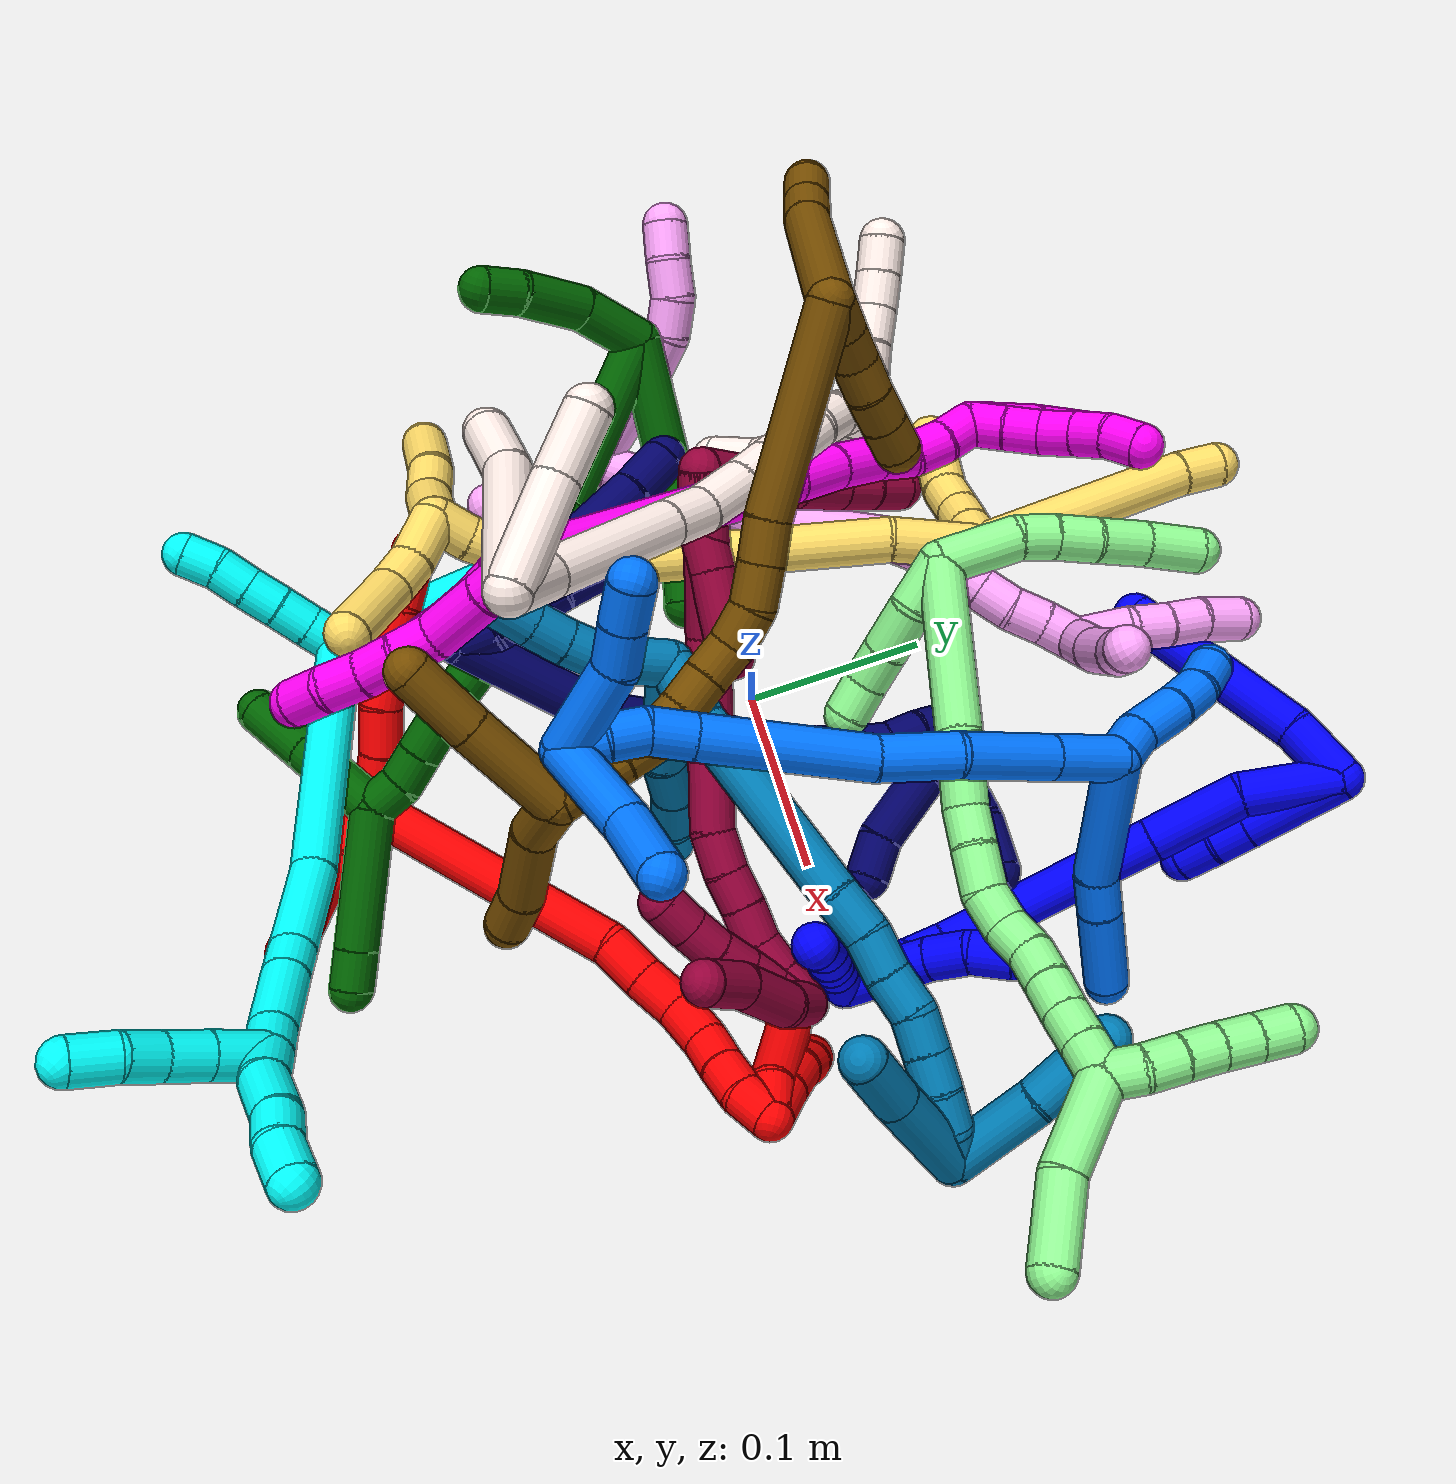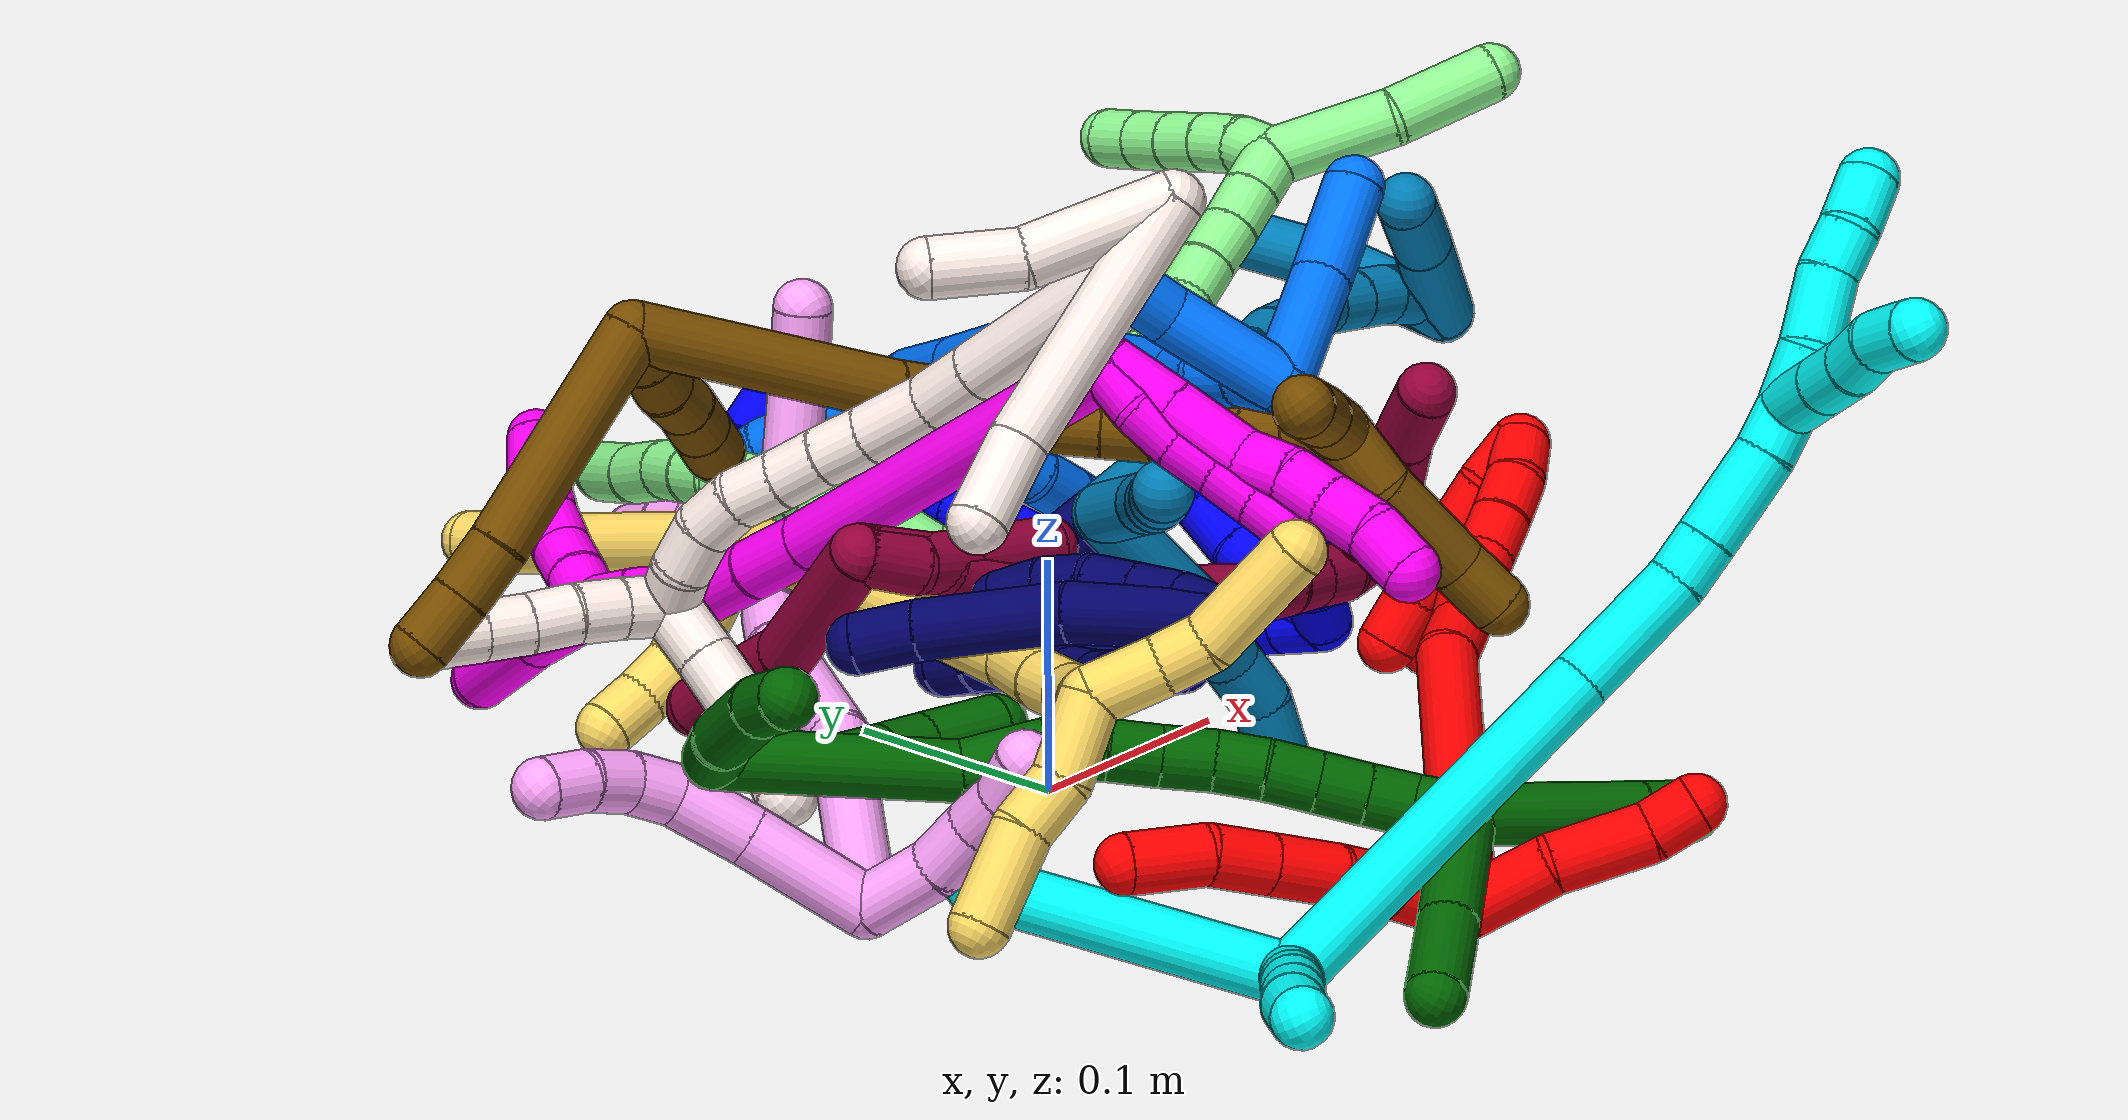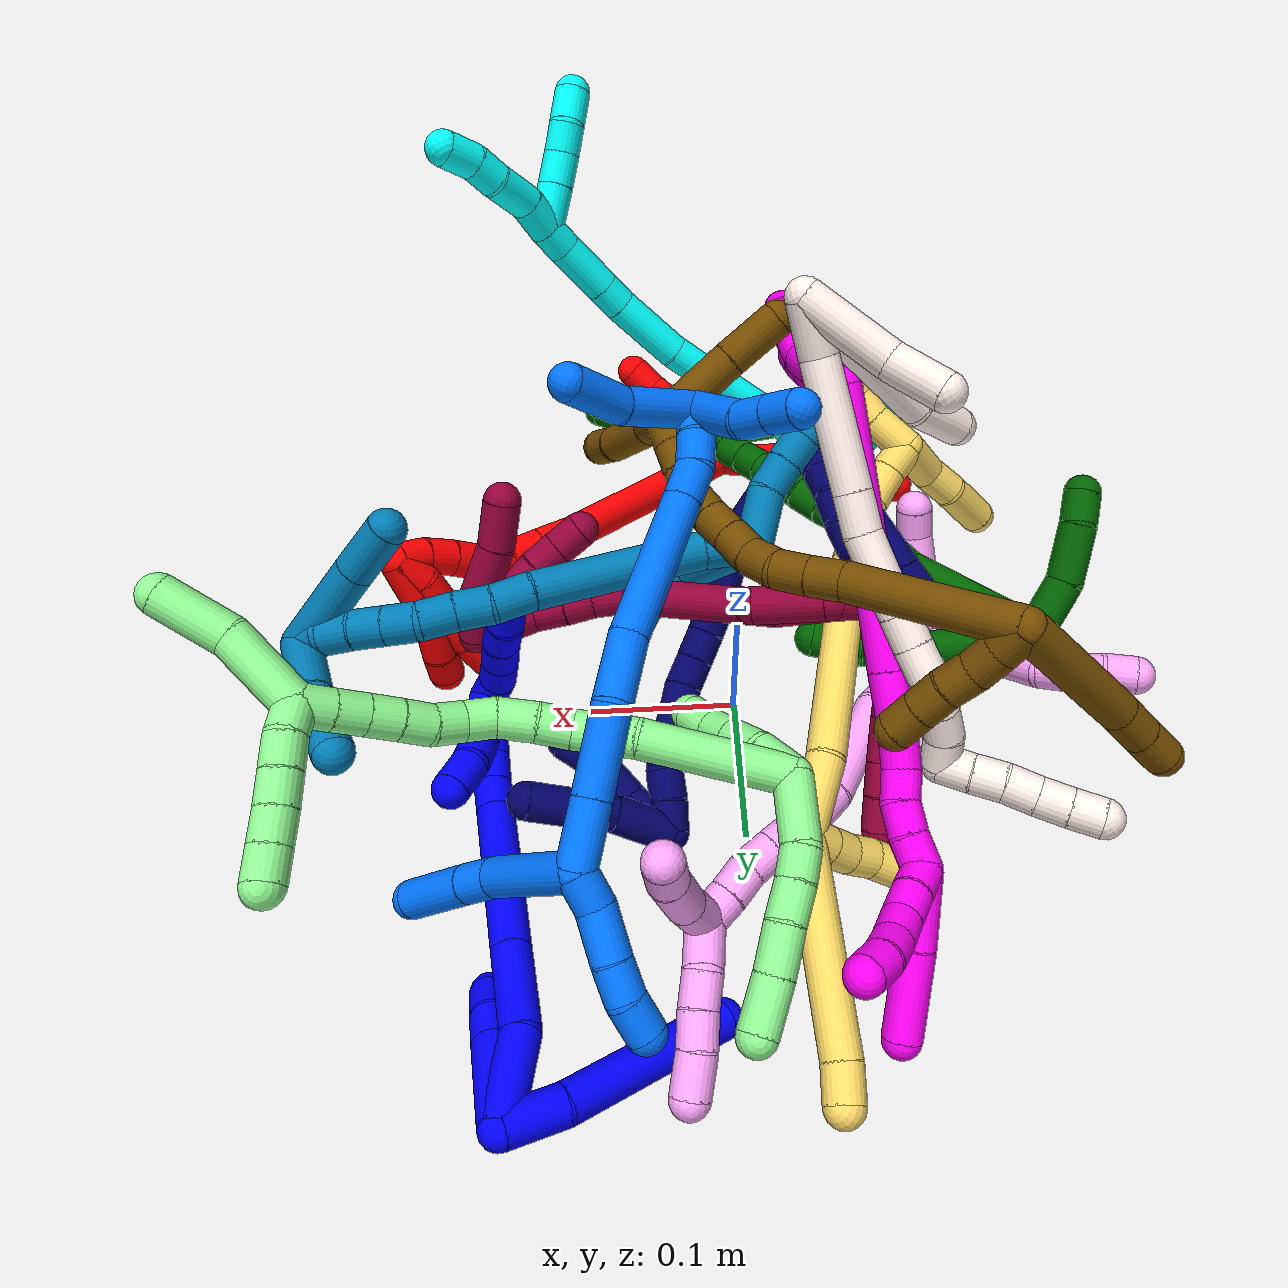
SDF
<sdf version="1.7">
 <world name="default">
  <plugin name="TubeGeneratorPlugin" filename="libtube_generator_plugin.so"/>
  <model name="photoneo_s_sensor">
   <static>1</static>
   <pose>0 0 2 1.57079 1.57079 3.14159</pose>
   <link name="link">
    <inertial><mass>0.1</mass></inertial>
    <sensor name="sensor" type="depth">
     <update_rate>30</update_rate>
     <camera>
      <horizontal_fov>1.22</horizontal_fov>
      <image><width>1920</width><height>1200</height><format>B8G8R8</format></image>
      <clip><near>0.1</near><far>4</far></clip>
      <depth_camera><output>points</output></depth_camera>
     </camera>
     <plugin name="camera_plugin" filename="libgazebo_ros_depth_camera.so">
      <baseline>0.2</baseline>
      <alwaysOn>1</alwaysOn>
      <updateRate>0.0</updateRate>
      <cameraName>camera_ir</cameraName>
      <imageTopicName>/camera/color/image_raw</imageTopicName>
      <cameraInfoTopicName>/camera/color/camera_info</cameraInfoTopicName>
      <depthImageTopicName>/camera/depth/image_raw</depthImageTopicName>
      <depthImageCameraInfoTopicName>/camera/depth/camera_info</depthImageCameraInfoTopicName>
      <pointCloudTopicName>/camera/depth/points</pointCloudTopicName>
      <frameName>fr_optical</frameName>
      <pointCloudCutoff>0.1</pointCloudCutoff>
      <pointCloudCutoffMax>2.0</pointCloudCutoffMax>
      <distortionK1>0</distortionK1>
      <distortionK2>0</distortionK2>
      <distortionK3>0</distortionK3>
      <distortionT1>0</distortionT1>
      <distortionT2>0</distortionT2>
      <CxPrime>0</CxPrime>
      <Cx>0</Cx>
      <Cy>0</Cy>
      <focalLength>0</focalLength>
      <hackBaseline>0</hackBaseline>
     </plugin>
    </sensor>
   </link>
  </model>
  <gravity>0 0 -9.8</gravity>
  <magnetic_field>6e-06 2.3e-05 -4.2e-05</magnetic_field>
  <atmosphere type="adiabatic"/>
  <physics name="default_physics" default="0" type="ode">
   <max_step_size>0.003</max_step_size>
   <real_time_factor>1</real_time_factor>
   <real_time_update_rate>1000</real_time_update_rate>
   <max_contacts>10000</max_contacts>
   <ode>
    <solver>
     <type>quick</type>
     <iters>100</iters>
     <sor>1.3</sor>
     <use_dynamic_moi_rescaling>0</use_dynamic_moi_rescaling>
    </solver>
    <constraints>
     <contact_max_correcting_vel>0</contact_max_correcting_vel>
     <contact_surface_layer>0.001</contact_surface_layer>
     <cfm>0</cfm>
     <erp>0.2</erp>
    </constraints>
   </ode>
  </physics>
  <scene><ambient>0.4 0.4 0.4 1</ambient><background>0.7 0.7 0.7 1</background><shadows>0</shadows></scene>
  <audio><device>default</device></audio>
  <spherical_coordinates>
   <surface_model>EARTH_WGS84</surface_model>
   <latitude_deg>0</latitude_deg>
   <longitude_deg>0</longitude_deg>
   <elevation>0</elevation>
   <heading_deg>0</heading_deg>
  </spherical_coordinates>
  <model name="bin">
   <static>1</static>
   <link name="bottom">
    <collision name="collision-bottom">
     <pose>0 0 -0.01 0 -0 0</pose>
     <geometry><box><size>0.8 0.6 0.02</size></box></geometry>
     <surface>
      <friction><ode><mu>100</mu><mu2>100</mu2></ode></friction>
      <contact><collide_bitmask>65535</collide_bitmask></contact>
     </surface>
    </collision>
   </link>
   <link name="west_wall">
    <collision name="collision-west_wall">
     <pose>-0.41 0 0.1 0 -0 0</pose>
     <geometry><box><size>0.02 0.6 0.2</size></box></geometry>
     <surface>
      <friction><ode><mu>100</mu><mu2>100</mu2></ode></friction>
      <contact><collide_bitmask>65535</collide_bitmask></contact>
     </surface>
    </collision>
   </link>
   <link name="east_wall">
    <collision name="collision-east_wall">
     <pose>0.41 0 0.1 0 -0 0</pose>
     <geometry><box><size>0.02 0.6 0.2</size></box></geometry>
     <surface>
      <friction><ode><mu>100</mu><mu2>100</mu2></ode></friction>
      <contact><collide_bitmask>65535</collide_bitmask></contact>
     </surface>
    </collision>
   </link>
   <link name="south_wall">
    <collision name="collision-south_wall">
     <pose>0 -0.31 0.1 0 -0 0</pose>
     <geometry><box><size>0.8 0.02 0.2</size></box></geometry>
     <surface>
      <friction><ode><mu>100</mu><mu2>100</mu2></ode></friction>
      <contact><collide_bitmask>65535</collide_bitmask></contact>
     </surface>
    </collision>
   </link>
   <link name="north_wall">
    <collision name="collision-north_wall">
     <pose>0 0.31 0.1 0 -0 0</pose>
     <geometry><box><size>0.8 0.02 0.2</size></box></geometry>
     <surface>
      <friction><ode><mu>100</mu><mu2>100</mu2></ode></friction>
      <contact><collide_bitmask>65535</collide_bitmask></contact>
     </surface>
    </collision>
   </link>
  </model>
  <model name="1">
   <static>0</static>
   <link name="1">
    <collision name="collision-cylinder-e_1_2_8">
     <pose>-0.017676 0.005353 -0.003426 -2.14019 -1.22565 1.81892</pose>
     <geometry><cylinder><radius>0.0125</radius><length>0.037569</length></cylinder></geometry>
     <surface>
      <friction><ode><mu>1.16</mu><mu2>1.16</mu2><slip1>0</slip1><slip2>0</slip2></ode></friction>
      <contact><ode><kp>1e+06</kp><kd>1</kd><max_vel>0</max_vel><min_depth>0.001</min_depth></ode></contact>
     </surface>
    </collision>
    <visual name="visual-cylinder-e_1_2_8">
     <pose>-0.017676 0.005353 -0.003426 -2.14019 -1.22565 1.81892</pose>
     <geometry><cylinder><radius>0.0125</radius><length>0.037569</length></cylinder></geometry>
     <material><ambient>0 0 1 1</ambient></material>
    </visual>
    <collision name="collision-cylinder-e_2_8_6">
     <pose>-0.084607 0.028922 -0.026913 -2.40431 -1.06783 1.98402</pose>
     <geometry><cylinder><radius>0.0125</radius><length>0.112431</length></cylinder></geometry>
     <surface>
      <friction><ode><mu>1.16</mu><mu2>1.16</mu2><slip1>0</slip1><slip2>0</slip2></ode></friction>
      <contact><ode><kp>1e+06</kp><kd>1</kd><max_vel>0</max_vel><min_depth>0.001</min_depth></ode></contact>
     </surface>
    </collision>
    <visual name="visual-cylinder-e_2_8_6">
     <pose>-0.084607 0.028922 -0.026913 -2.40431 -1.06783 1.98402</pose>
     <geometry><cylinder><radius>0.0125</radius><length>0.112431</length></cylinder></geometry>
     <material><ambient>0 0 1 1</ambient></material>
    </visual>
    <collision name="collision-cylinder-e_1_2_9">
     <pose>-0.00109 0.005785 -0.02833 -2.94017 -0.037696 0.36883</pose>
     <geometry><cylinder><radius>0.0125</radius><length>0.05787</length></cylinder></geometry>
     <surface>
      <friction><ode><mu>1.16</mu><mu2>1.16</mu2><slip1>0</slip1><slip2>0</slip2></ode></friction>
      <contact><ode><kp>1e+06</kp><kd>1</kd><max_vel>0</max_vel><min_depth>0.001</min_depth></ode></contact>
     </surface>
    </collision>
    <visual name="visual-cylinder-e_1_2_9">
     <pose>-0.00109 0.005785 -0.02833 -2.94017 -0.037696 0.36883</pose>
     <geometry><cylinder><radius>0.0125</radius><length>0.05787</length></cylinder></geometry>
     <material><ambient>0 0 1 1</ambient></material>
    </visual>
    <collision name="collision-cylinder-e_2_9_10">
     <pose>-0.002714 0.01356 -0.066731 -2.94645 -0.051844 0.517896</pose>
     <geometry><cylinder><radius>0.0125</radius><length>0.02056</length></cylinder></geometry>
     <surface>
      <friction><ode><mu>1.16</mu><mu2>1.16</mu2><slip1>0</slip1><slip2>0</slip2></ode></friction>
      <contact><ode><kp>1e+06</kp><kd>1</kd><max_vel>0</max_vel><min_depth>0.001</min_depth></ode></contact>
     </surface>
    </collision>
    <visual name="visual-cylinder-e_2_9_10">
     <pose>-0.002714 0.01356 -0.066731 -2.94645 -0.051844 0.517896</pose>
     <geometry><cylinder><radius>0.0125</radius><length>0.02056</length></cylinder></geometry>
     <material><ambient>0 0 1 1</ambient></material>
    </visual>
    <collision name="collision-cylinder-e_3_10_5">
     <pose>-0.003728 0.019439 -0.086851 -2.77237 -0.044666 0.238103</pose>
     <geometry><cylinder><radius>0.0125</radius><length>0.02157</length></cylinder></geometry>
     <surface>
      <friction><ode><mu>1.16</mu><mu2>1.16</mu2><slip1>0</slip1><slip2>0</slip2></ode></friction>
      <contact><ode><kp>1e+06</kp><kd>1</kd><max_vel>0</max_vel><min_depth>0.001</min_depth></ode></contact>
     </surface>
    </collision>
    <visual name="visual-cylinder-e_3_10_5">
     <pose>-0.003728 0.019439 -0.086851 -2.77237 -0.044666 0.238103</pose>
     <geometry><cylinder><radius>0.0125</radius><length>0.02157</length></cylinder></geometry>
     <material><ambient>0 0 1 1</ambient></material>
    </visual>
    <collision name="collision-cylinder-e_1_2_11">
     <pose>-0.010254 -0.00016 -0.025338 3.13528 -0.384533 -3.10915</pose>
     <geometry><cylinder><radius>0.0125</radius><length>0.05467</length></cylinder></geometry>
     <surface>
      <friction><ode><mu>1.16</mu><mu2>1.16</mu2><slip1>0</slip1><slip2>0</slip2></ode></friction>
      <contact><ode><kp>1e+06</kp><kd>1</kd><max_vel>0</max_vel><min_depth>0.001</min_depth></ode></contact>
     </surface>
    </collision>
    <visual name="visual-cylinder-e_1_2_11">
     <pose>-0.010254 -0.00016 -0.025338 3.13528 -0.384533 -3.10915</pose>
     <geometry><cylinder><radius>0.0125</radius><length>0.05467</length></cylinder></geometry>
     <material><ambient>0 0 1 1</ambient></material>
    </visual>
    <collision name="collision-cylinder-e_2_11_12">
     <pose>-0.02233 -0.000201 -0.0779 -3.13721 -0.06681 3.01055</pose>
     <geometry><cylinder><radius>0.0125</radius><length>0.054569</length></cylinder></geometry>
     <surface>
      <friction><ode><mu>1.16</mu><mu2>1.16</mu2><slip1>0</slip1><slip2>0</slip2></ode></friction>
      <contact><ode><kp>1e+06</kp><kd>1</kd><max_vel>0</max_vel><min_depth>0.001</min_depth></ode></contact>
     </surface>
    </collision>
    <visual name="visual-cylinder-e_2_11_12">
     <pose>-0.02233 -0.000201 -0.0779 -3.13721 -0.06681 3.01055</pose>
     <geometry><cylinder><radius>0.0125</radius><length>0.054569</length></cylinder></geometry>
     <material><ambient>0 0 1 1</ambient></material>
    </visual>
    <collision name="collision-cylinder-e_3_12_13">
     <pose>-0.027834 0.000166 -0.158789 -3.13699 -0.068508 3.00733</pose>
     <geometry><cylinder><radius>0.0125</radius><length>0.107585</length></cylinder></geometry>
     <surface>
      <friction><ode><mu>1.16</mu><mu2>1.16</mu2><slip1>0</slip1><slip2>0</slip2></ode></friction>
      <contact><ode><kp>1e+06</kp><kd>1</kd><max_vel>0</max_vel><min_depth>0.001</min_depth></ode></contact>
     </surface>
    </collision>
    <visual name="visual-cylinder-e_3_12_13">
     <pose>-0.027834 0.000166 -0.158789 -3.13699 -0.068508 3.00733</pose>
     <geometry><cylinder><radius>0.0125</radius><length>0.107585</length></cylinder></geometry>
     <material><ambient>0 0 1 1</ambient></material>
    </visual>
    <collision name="collision-cylinder-e_4_13_14">
     <pose>-0.032543 -0.001488 -0.222477 2.95414 -0.100376 -0.981498</pose>
     <geometry><cylinder><radius>0.0125</radius><length>0.020506</length></cylinder></geometry>
     <surface>
      <friction><ode><mu>1.16</mu><mu2>1.16</mu2><slip1>0</slip1><slip2>0</slip2></ode></friction>
      <contact><ode><kp>1e+06</kp><kd>1</kd><max_vel>0</max_vel><min_depth>0.001</min_depth></ode></contact>
     </surface>
    </collision>
    <visual name="visual-cylinder-e_4_13_14">
     <pose>-0.032543 -0.001488 -0.222477 2.95414 -0.100376 -0.981498</pose>
     <geometry><cylinder><radius>0.0125</radius><length>0.020506</length></cylinder></geometry>
     <material><ambient>0 0 1 1</ambient></material>
    </visual>
    <collision name="collision-cylinder-e_5_14_15">
     <pose>-0.035045 -0.0055 -0.242837 2.94013 -0.138862 -1.20532</pose>
     <geometry><cylinder><radius>0.0125</radius><length>0.021306</length></cylinder></geometry>
     <surface>
      <friction><ode><mu>1.16</mu><mu2>1.16</mu2><slip1>0</slip1><slip2>0</slip2></ode></friction>
      <contact><ode><kp>1e+06</kp><kd>1</kd><max_vel>0</max_vel><min_depth>0.001</min_depth></ode></contact>
     </surface>
    </collision>
    <visual name="visual-cylinder-e_5_14_15">
     <pose>-0.035045 -0.0055 -0.242837 2.94013 -0.138862 -1.20532</pose>
     <geometry><cylinder><radius>0.0125</radius><length>0.021306</length></cylinder></geometry>
     <material><ambient>0 0 1 1</ambient></material>
    </visual>
    <collision name="collision-cylinder-e_6_15_16">
     <pose>-0.038447 -0.012388 -0.261998 2.64542 -0.189767 -0.718785</pose>
     <geometry><cylinder><radius>0.0125</radius><length>0.020435</length></cylinder></geometry>
     <surface>
      <friction><ode><mu>1.16</mu><mu2>1.16</mu2><slip1>0</slip1><slip2>0</slip2></ode></friction>
      <contact><ode><kp>1e+06</kp><kd>1</kd><max_vel>0</max_vel><min_depth>0.001</min_depth></ode></contact>
     </surface>
    </collision>
    <visual name="visual-cylinder-e_6_15_16">
     <pose>-0.038447 -0.012388 -0.261998 2.64542 -0.189767 -0.718785</pose>
     <geometry><cylinder><radius>0.0125</radius><length>0.020435</length></cylinder></geometry>
     <material><ambient>0 0 1 1</ambient></material>
    </visual>
    <collision name="collision-cylinder-e_7_16_1">
     <pose>-0.042351 -0.02206 -0.279857 2.64507 -0.190017 -0.719183</pose>
     <geometry><cylinder><radius>0.0125</radius><length>0.02093</length></cylinder></geometry>
     <surface>
      <friction><ode><mu>1.16</mu><mu2>1.16</mu2><slip1>0</slip1><slip2>0</slip2></ode></friction>
      <contact><ode><kp>1e+06</kp><kd>1</kd><max_vel>0</max_vel><min_depth>0.001</min_depth></ode></contact>
     </surface>
    </collision>
    <visual name="visual-cylinder-e_7_16_1">
     <pose>-0.042351 -0.02206 -0.279857 2.64507 -0.190017 -0.719183</pose>
     <geometry><cylinder><radius>0.0125</radius><length>0.02093</length></cylinder></geometry>
     <material><ambient>0 0 1 1</ambient></material>
    </visual>
    <collision name="collision-cylinder-e_1_1_17">
     <pose>-0.039149 -0.032682 -0.263987 0.226001 0.199919 0.022762</pose>
     <geometry><cylinder><radius>0.0125</radius><length>0.052149</length></cylinder></geometry>
     <surface>
      <friction><ode><mu>1.16</mu><mu2>1.16</mu2><slip1>0</slip1><slip2>0</slip2></ode></friction>
      <contact><ode><kp>1e+06</kp><kd>1</kd><max_vel>0</max_vel><min_depth>0.001</min_depth></ode></contact>
     </surface>
    </collision>
    <visual name="visual-cylinder-e_1_1_17">
     <pose>-0.039149 -0.032682 -0.263987 0.226001 0.199919 0.022762</pose>
     <geometry><cylinder><radius>0.0125</radius><length>0.052149</length></cylinder></geometry>
     <material><ambient>0 0 1 1</ambient></material>
    </visual>
    <collision name="collision-cylinder-e_2_17_18">
     <pose>-0.030226 -0.042082 -0.228308 0.328604 0.317869 0.053137</pose>
     <geometry><cylinder><radius>0.0125</radius><length>0.023967</length></cylinder></geometry>
     <surface>
      <friction><ode><mu>1.16</mu><mu2>1.16</mu2><slip1>0</slip1><slip2>0</slip2></ode></friction>
      <contact><ode><kp>1e+06</kp><kd>1</kd><max_vel>0</max_vel><min_depth>0.001</min_depth></ode></contact>
     </surface>
    </collision>
    <visual name="visual-cylinder-e_2_17_18">
     <pose>-0.030226 -0.042082 -0.228308 0.328604 0.317869 0.053137</pose>
     <geometry><cylinder><radius>0.0125</radius><length>0.023967</length></cylinder></geometry>
     <material><ambient>0 0 1 1</ambient></material>
    </visual>
    <collision name="collision-cylinder-e_3_18_4">
     <pose>-0.019412 -0.047339 -0.20804 0.165223 0.633442 0.054263</pose>
     <geometry><cylinder><radius>0.0125</radius><length>0.023883</length></cylinder></geometry>
     <surface>
      <friction><ode><mu>1.16</mu><mu2>1.16</mu2><slip1>0</slip1><slip2>0</slip2></ode></friction>
      <contact><ode><kp>1e+06</kp><kd>1</kd><max_vel>0</max_vel><min_depth>0.001</min_depth></ode></contact>
     </surface>
    </collision>
    <visual name="visual-cylinder-e_3_18_4">
     <pose>-0.019412 -0.047339 -0.20804 0.165223 0.633442 0.054263</pose>
     <geometry><cylinder><radius>0.0125</radius><length>0.023883</length></cylinder></geometry>
     <material><ambient>0 0 1 1</ambient></material>
    </visual>
    <collision name="collision-cylinder-e_1_1_19">
     <pose>-0.049689 -0.035278 -0.287485 1.40316 -0.565911 -0.481832</pose>
     <geometry><cylinder><radius>0.0125</radius><length>0.02</length></cylinder></geometry>
     <surface>
      <friction><ode><mu>1.16</mu><mu2>1.16</mu2><slip1>0</slip1><slip2>0</slip2></ode></friction>
      <contact><ode><kp>1e+06</kp><kd>1</kd><max_vel>0</max_vel><min_depth>0.001</min_depth></ode></contact>
     </surface>
    </collision>
    <visual name="visual-cylinder-e_1_1_19">
     <pose>-0.049689 -0.035278 -0.287485 1.40316 -0.565911 -0.481832</pose>
     <geometry><cylinder><radius>0.0125</radius><length>0.02</length></cylinder></geometry>
     <material><ambient>0 0 1 1</ambient></material>
    </visual>
    <collision name="collision-cylinder-e_2_19_20">
     <pose>-0.057891 -0.053088 -0.284686 1.42535 -0.287939 -0.249268</pose>
     <geometry><cylinder><radius>0.0125</radius><length>0.02</length></cylinder></geometry>
     <surface>
      <friction><ode><mu>1.16</mu><mu2>1.16</mu2><slip1>0</slip1><slip2>0</slip2></ode></friction>
      <contact><ode><kp>1e+06</kp><kd>1</kd><max_vel>0</max_vel><min_depth>0.001</min_depth></ode></contact>
     </surface>
    </collision>
    <visual name="visual-cylinder-e_2_19_20">
     <pose>-0.057891 -0.053088 -0.284686 1.42535 -0.287939 -0.249268</pose>
     <geometry><cylinder><radius>0.0125</radius><length>0.02</length></cylinder></geometry>
     <material><ambient>0 0 1 1</ambient></material>
    </visual>
    <collision name="collision-cylinder-e_3_20_21">
     <pose>-0.063043 -0.072105 -0.281339 1.36816 -0.23331 -0.190537</pose>
     <geometry><cylinder><radius>0.0125</radius><length>0.02</length></cylinder></geometry>
     <surface>
      <friction><ode><mu>1.16</mu><mu2>1.16</mu2><slip1>0</slip1><slip2>0</slip2></ode></friction>
      <contact><ode><kp>1e+06</kp><kd>1</kd><max_vel>0</max_vel><min_depth>0.001</min_depth></ode></contact>
     </surface>
    </collision>
    <visual name="visual-cylinder-e_3_20_21">
     <pose>-0.063043 -0.072105 -0.281339 1.36816 -0.23331 -0.190537</pose>
     <geometry><cylinder><radius>0.0125</radius><length>0.02</length></cylinder></geometry>
     <material><ambient>0 0 1 1</ambient></material>
    </visual>
    <collision name="collision-cylinder-e_4_21_22">
     <pose>-0.068564 -0.090866 -0.277261 1.34505 -0.326659 -0.260989</pose>
     <geometry><cylinder><radius>0.0125</radius><length>0.02</length></cylinder></geometry>
     <surface>
      <friction><ode><mu>1.16</mu><mu2>1.16</mu2><slip1>0</slip1><slip2>0</slip2></ode></friction>
      <contact><ode><kp>1e+06</kp><kd>1</kd><max_vel>0</max_vel><min_depth>0.001</min_depth></ode></contact>
     </surface>
    </collision>
    <visual name="visual-cylinder-e_4_21_22">
     <pose>-0.068564 -0.090866 -0.277261 1.34505 -0.326659 -0.260989</pose>
     <geometry><cylinder><radius>0.0125</radius><length>0.02</length></cylinder></geometry>
     <material><ambient>0 0 1 1</ambient></material>
    </visual>
    <collision name="collision-cylinder-e_5_22_3">
     <pose>-0.074276 -0.109778 -0.275096 1.5662 -0.253037 -0.25189</pose>
     <geometry><cylinder><radius>0.0125</radius><length>0.02</length></cylinder></geometry>
     <surface>
      <friction><ode><mu>1.16</mu><mu2>1.16</mu2><slip1>0</slip1><slip2>0</slip2></ode></friction>
      <contact><ode><kp>1e+06</kp><kd>1</kd><max_vel>0</max_vel><min_depth>0.001</min_depth></ode></contact>
     </surface>
    </collision>
    <visual name="visual-cylinder-e_5_22_3">
     <pose>-0.074276 -0.109778 -0.275096 1.5662 -0.253037 -0.25189</pose>
     <geometry><cylinder><radius>0.0125</radius><length>0.02</length></cylinder></geometry>
     <material><ambient>0 0 1 1</ambient></material>
    </visual>
    <collision name="collision-sphere-3">
     <pose>-0.076779 -0.11946 -0.275052 0 -0 0</pose>
     <geometry><sphere><radius>0.0125</radius></sphere></geometry>
     <surface>
      <friction><ode><mu>1.16</mu><mu2>1.16</mu2><slip1>0</slip1><slip2>0</slip2></ode></friction>
      <contact><ode><kp>1e+06</kp><kd>1</kd><max_vel>0</max_vel><min_depth>0.001</min_depth></ode></contact>
     </surface>
    </collision>
    <visual name="visual-sphere-3">
     <pose>-0.076779 -0.11946 -0.275052 0 -0 0</pose>
     <geometry><sphere><radius>0.0125</radius></sphere></geometry>
     <material><ambient>0 0 1 1</ambient></material>
    </visual>
    <collision name="collision-sphere-22">
     <pose>-0.071772 -0.100097 -0.275141 0 -0 0</pose>
     <geometry><sphere><radius>0.0125</radius></sphere></geometry>
     <surface>
      <friction><ode><mu>1.16</mu><mu2>1.16</mu2><slip1>0</slip1><slip2>0</slip2></ode></friction>
      <contact><ode><kp>1e+06</kp><kd>1</kd><max_vel>0</max_vel><min_depth>0.001</min_depth></ode></contact>
     </surface>
    </collision>
    <visual name="visual-sphere-22">
     <pose>-0.071772 -0.100097 -0.275141 0 -0 0</pose>
     <geometry><sphere><radius>0.0125</radius></sphere></geometry>
     <material><ambient>0 0 1 1</ambient></material>
    </visual>
    <collision name="collision-sphere-21">
     <pose>-0.065355 -0.081635 -0.279381 0 -0 0</pose>
     <geometry><sphere><radius>0.0125</radius></sphere></geometry>
     <surface>
      <friction><ode><mu>1.16</mu><mu2>1.16</mu2><slip1>0</slip1><slip2>0</slip2></ode></friction>
      <contact><ode><kp>1e+06</kp><kd>1</kd><max_vel>0</max_vel><min_depth>0.001</min_depth></ode></contact>
     </surface>
    </collision>
    <visual name="visual-sphere-21">
     <pose>-0.065355 -0.081635 -0.279381 0 -0 0</pose>
     <geometry><sphere><radius>0.0125</radius></sphere></geometry>
     <material><ambient>0 0 1 1</ambient></material>
    </visual>
    <collision name="collision-sphere-20">
     <pose>-0.060731 -0.062575 -0.283297 0 -0 0</pose>
     <geometry><sphere><radius>0.0125</radius></sphere></geometry>
     <surface>
      <friction><ode><mu>1.16</mu><mu2>1.16</mu2><slip1>0</slip1><slip2>0</slip2></ode></friction>
      <contact><ode><kp>1e+06</kp><kd>1</kd><max_vel>0</max_vel><min_depth>0.001</min_depth></ode></contact>
     </surface>
    </collision>
    <visual name="visual-sphere-20">
     <pose>-0.060731 -0.062575 -0.283297 0 -0 0</pose>
     <geometry><sphere><radius>0.0125</radius></sphere></geometry>
     <material><ambient>0 0 1 1</ambient></material>
    </visual>
    <collision name="collision-sphere-19">
     <pose>-0.055051 -0.043601 -0.286076 0 -0 0</pose>
     <geometry><sphere><radius>0.0125</radius></sphere></geometry>
     <surface>
      <friction><ode><mu>1.16</mu><mu2>1.16</mu2><slip1>0</slip1><slip2>0</slip2></ode></friction>
      <contact><ode><kp>1e+06</kp><kd>1</kd><max_vel>0</max_vel><min_depth>0.001</min_depth></ode></contact>
     </surface>
    </collision>
    <visual name="visual-sphere-19">
     <pose>-0.055051 -0.043601 -0.286076 0 -0 0</pose>
     <geometry><sphere><radius>0.0125</radius></sphere></geometry>
     <material><ambient>0 0 1 1</ambient></material>
    </visual>
    <collision name="collision-sphere-5">
     <pose>-0.00421 0.023327 -0.096899 0 -0 0</pose>
     <geometry><sphere><radius>0.0125</radius></sphere></geometry>
     <surface>
      <friction><ode><mu>1.16</mu><mu2>1.16</mu2><slip1>0</slip1><slip2>0</slip2></ode></friction>
      <contact><ode><kp>1e+06</kp><kd>1</kd><max_vel>0</max_vel><min_depth>0.001</min_depth></ode></contact>
     </surface>
    </collision>
    <visual name="visual-sphere-5">
     <pose>-0.00421 0.023327 -0.096899 0 -0 0</pose>
     <geometry><sphere><radius>0.0125</radius></sphere></geometry>
     <material><ambient>0 0 1 1</ambient></material>
    </visual>
    <collision name="collision-sphere-10">
     <pose>-0.003246 0.015551 -0.076802 0 -0 0</pose>
     <geometry><sphere><radius>0.0125</radius></sphere></geometry>
     <surface>
      <friction><ode><mu>1.16</mu><mu2>1.16</mu2><slip1>0</slip1><slip2>0</slip2></ode></friction>
      <contact><ode><kp>1e+06</kp><kd>1</kd><max_vel>0</max_vel><min_depth>0.001</min_depth></ode></contact>
     </surface>
    </collision>
    <visual name="visual-sphere-10">
     <pose>-0.003246 0.015551 -0.076802 0 -0 0</pose>
     <geometry><sphere><radius>0.0125</radius></sphere></geometry>
     <material><ambient>0 0 1 1</ambient></material>
    </visual>
    <collision name="collision-sphere-6">
     <pose>-0.133861 0.047139 -0.046973 0 -0 0</pose>
     <geometry><sphere><radius>0.0125</radius></sphere></geometry>
     <surface>
      <friction><ode><mu>1.16</mu><mu2>1.16</mu2><slip1>0</slip1><slip2>0</slip2></ode></friction>
      <contact><ode><kp>1e+06</kp><kd>1</kd><max_vel>0</max_vel><min_depth>0.001</min_depth></ode></contact>
     </surface>
    </collision>
    <visual name="visual-sphere-6">
     <pose>-0.133861 0.047139 -0.046973 0 -0 0</pose>
     <geometry><sphere><radius>0.0125</radius></sphere></geometry>
     <material><ambient>0 0 1 1</ambient></material>
    </visual>
    <collision name="collision-sphere-9">
     <pose>-0.002181 0.01157 -0.056659 0 -0 0</pose>
     <geometry><sphere><radius>0.0125</radius></sphere></geometry>
     <surface>
      <friction><ode><mu>1.16</mu><mu2>1.16</mu2><slip1>0</slip1><slip2>0</slip2></ode></friction>
      <contact><ode><kp>1e+06</kp><kd>1</kd><max_vel>0</max_vel><min_depth>0.001</min_depth></ode></contact>
     </surface>
    </collision>
    <visual name="visual-sphere-9">
     <pose>-0.002181 0.01157 -0.056659 0 -0 0</pose>
     <geometry><sphere><radius>0.0125</radius></sphere></geometry>
     <material><ambient>0 0 1 1</ambient></material>
    </visual>
    <collision name="collision-sphere-2">
     <geometry><sphere><radius>0.0125</radius></sphere></geometry>
     <surface>
      <friction><ode><mu>1.16</mu><mu2>1.16</mu2><slip1>0</slip1><slip2>0</slip2></ode></friction>
      <contact><ode><kp>1e+06</kp><kd>1</kd><max_vel>0</max_vel><min_depth>0.001</min_depth></ode></contact>
     </surface>
    </collision>
    <visual name="visual-sphere-2">
     <geometry><sphere><radius>0.0125</radius></sphere></geometry>
     <material><ambient>0 0 1 1</ambient></material>
    </visual>
    <collision name="collision-sphere-8">
     <pose>-0.035353 0.010705 -0.006853 0 -0 0</pose>
     <geometry><sphere><radius>0.0125</radius></sphere></geometry>
     <surface>
      <friction><ode><mu>1.16</mu><mu2>1.16</mu2><slip1>0</slip1><slip2>0</slip2></ode></friction>
      <contact><ode><kp>1e+06</kp><kd>1</kd><max_vel>0</max_vel><min_depth>0.001</min_depth></ode></contact>
     </surface>
    </collision>
    <visual name="visual-sphere-8">
     <pose>-0.035353 0.010705 -0.006853 0 -0 0</pose>
     <geometry><sphere><radius>0.0125</radius></sphere></geometry>
     <material><ambient>0 0 1 1</ambient></material>
    </visual>
    <collision name="collision-sphere-11">
     <pose>-0.020508 -0.00032 -0.050677 0 -0 0</pose>
     <geometry><sphere><radius>0.0125</radius></sphere></geometry>
     <surface>
      <friction><ode><mu>1.16</mu><mu2>1.16</mu2><slip1>0</slip1><slip2>0</slip2></ode></friction>
      <contact><ode><kp>1e+06</kp><kd>1</kd><max_vel>0</max_vel><min_depth>0.001</min_depth></ode></contact>
     </surface>
    </collision>
    <visual name="visual-sphere-11">
     <pose>-0.020508 -0.00032 -0.050677 0 -0 0</pose>
     <geometry><sphere><radius>0.0125</radius></sphere></geometry>
     <material><ambient>0 0 1 1</ambient></material>
    </visual>
    <collision name="collision-sphere-12">
     <pose>-0.024151 -8.1e-05 -0.105124 0 -0 0</pose>
     <geometry><sphere><radius>0.0125</radius></sphere></geometry>
     <surface>
      <friction><ode><mu>1.16</mu><mu2>1.16</mu2><slip1>0</slip1><slip2>0</slip2></ode></friction>
      <contact><ode><kp>1e+06</kp><kd>1</kd><max_vel>0</max_vel><min_depth>0.001</min_depth></ode></contact>
     </surface>
    </collision>
    <visual name="visual-sphere-12">
     <pose>-0.024151 -8.1e-05 -0.105124 0 -0 0</pose>
     <geometry><sphere><radius>0.0125</radius></sphere></geometry>
     <material><ambient>0 0 1 1</ambient></material>
    </visual>
    <collision name="collision-sphere-13">
     <pose>-0.031516 0.000413 -0.212455 0 -0 0</pose>
     <geometry><sphere><radius>0.0125</radius></sphere></geometry>
     <surface>
      <friction><ode><mu>1.16</mu><mu2>1.16</mu2><slip1>0</slip1><slip2>0</slip2></ode></friction>
      <contact><ode><kp>1e+06</kp><kd>1</kd><max_vel>0</max_vel><min_depth>0.001</min_depth></ode></contact>
     </surface>
    </collision>
    <visual name="visual-sphere-13">
     <pose>-0.031516 0.000413 -0.212455 0 -0 0</pose>
     <geometry><sphere><radius>0.0125</radius></sphere></geometry>
     <material><ambient>0 0 1 1</ambient></material>
    </visual>
    <collision name="collision-sphere-14">
     <pose>-0.033571 -0.003389 -0.2325 0 -0 0</pose>
     <geometry><sphere><radius>0.0125</radius></sphere></geometry>
     <surface>
      <friction><ode><mu>1.16</mu><mu2>1.16</mu2><slip1>0</slip1><slip2>0</slip2></ode></friction>
      <contact><ode><kp>1e+06</kp><kd>1</kd><max_vel>0</max_vel><min_depth>0.001</min_depth></ode></contact>
     </surface>
    </collision>
    <visual name="visual-sphere-14">
     <pose>-0.033571 -0.003389 -0.2325 0 -0 0</pose>
     <geometry><sphere><radius>0.0125</radius></sphere></geometry>
     <material><ambient>0 0 1 1</ambient></material>
    </visual>
    <collision name="collision-sphere-15">
     <pose>-0.03652 -0.007611 -0.253174 0 -0 0</pose>
     <geometry><sphere><radius>0.0125</radius></sphere></geometry>
     <surface>
      <friction><ode><mu>1.16</mu><mu2>1.16</mu2><slip1>0</slip1><slip2>0</slip2></ode></friction>
      <contact><ode><kp>1e+06</kp><kd>1</kd><max_vel>0</max_vel><min_depth>0.001</min_depth></ode></contact>
     </surface>
    </collision>
    <visual name="visual-sphere-15">
     <pose>-0.03652 -0.007611 -0.253174 0 -0 0</pose>
     <geometry><sphere><radius>0.0125</radius></sphere></geometry>
     <material><ambient>0 0 1 1</ambient></material>
    </visual>
    <collision name="collision-sphere-16">
     <pose>-0.040374 -0.017165 -0.270822 0 -0 0</pose>
     <geometry><sphere><radius>0.0125</radius></sphere></geometry>
     <surface>
      <friction><ode><mu>1.16</mu><mu2>1.16</mu2><slip1>0</slip1><slip2>0</slip2></ode></friction>
      <contact><ode><kp>1e+06</kp><kd>1</kd><max_vel>0</max_vel><min_depth>0.001</min_depth></ode></contact>
     </surface>
    </collision>
    <visual name="visual-sphere-16">
     <pose>-0.040374 -0.017165 -0.270822 0 -0 0</pose>
     <geometry><sphere><radius>0.0125</radius></sphere></geometry>
     <material><ambient>0 0 1 1</ambient></material>
    </visual>
    <collision name="collision-sphere-1">
     <pose>-0.044328 -0.026956 -0.288893 0 -0 0</pose>
     <geometry><sphere><radius>0.0125</radius></sphere></geometry>
     <surface>
      <friction><ode><mu>1.16</mu><mu2>1.16</mu2><slip1>0</slip1><slip2>0</slip2></ode></friction>
      <contact><ode><kp>1e+06</kp><kd>1</kd><max_vel>0</max_vel><min_depth>0.001</min_depth></ode></contact>
     </surface>
    </collision>
    <visual name="visual-sphere-1">
     <pose>-0.044328 -0.026956 -0.288893 0 -0 0</pose>
     <geometry><sphere><radius>0.0125</radius></sphere></geometry>
     <material><ambient>0 0 1 1</ambient></material>
    </visual>
    <collision name="collision-sphere-18">
     <pose>-0.02648 -0.045756 -0.217534 0 -0 0</pose>
     <geometry><sphere><radius>0.0125</radius></sphere></geometry>
     <surface>
      <friction><ode><mu>1.16</mu><mu2>1.16</mu2><slip1>0</slip1><slip2>0</slip2></ode></friction>
      <contact><ode><kp>1e+06</kp><kd>1</kd><max_vel>0</max_vel><min_depth>0.001</min_depth></ode></contact>
     </surface>
    </collision>
    <visual name="visual-sphere-18">
     <pose>-0.02648 -0.045756 -0.217534 0 -0 0</pose>
     <geometry><sphere><radius>0.0125</radius></sphere></geometry>
     <material><ambient>0 0 1 1</ambient></material>
    </visual>
    <collision name="collision-sphere-17">
     <pose>-0.033971 -0.038409 -0.239082 0 -0 0</pose>
     <geometry><sphere><radius>0.0125</radius></sphere></geometry>
     <surface>
      <friction><ode><mu>1.16</mu><mu2>1.16</mu2><slip1>0</slip1><slip2>0</slip2></ode></friction>
      <contact><ode><kp>1e+06</kp><kd>1</kd><max_vel>0</max_vel><min_depth>0.001</min_depth></ode></contact>
     </surface>
    </collision>
    <visual name="visual-sphere-17">
     <pose>-0.033971 -0.038409 -0.239082 0 -0 0</pose>
     <geometry><sphere><radius>0.0125</radius></sphere></geometry>
     <material><ambient>0 0 1 1</ambient></material>
    </visual>
    <collision name="collision-sphere-4">
     <pose>-0.012343 -0.048922 -0.198546 0 -0 0</pose>
     <geometry><sphere><radius>0.0125</radius></sphere></geometry>
     <surface>
      <friction><ode><mu>1.16</mu><mu2>1.16</mu2><slip1>0</slip1><slip2>0</slip2></ode></friction>
      <contact><ode><kp>1e+06</kp><kd>1</kd><max_vel>0</max_vel><min_depth>0.001</min_depth></ode></contact>
     </surface>
    </collision>
    <visual name="visual-sphere-4">
     <pose>-0.012343 -0.048922 -0.198546 0 -0 0</pose>
     <geometry><sphere><radius>0.0125</radius></sphere></geometry>
     <material><ambient>0 0 1 1</ambient></material>
    </visual>
    <inertial>
     <pose>-0.036979 -0.009926 -0.138708 0 -0 0</pose>
     <mass>0.75</mass>
     <inertia>
      <ixx>-5.4e-05</ixx>
      <ixy>0</ixy>
      <ixz>0</ixz>
      <iyy>0.000311</iyy>
      <iyz>0</iyz>
      <izz>6.8e-05</izz>
     </inertia>
    </inertial>
   </link>
   <pose>0.150324 0.288473 0.05702 -1.34909 0.079296 0.23138</pose>
  </model>
  <model name="2">
   <static>0</static>
   <link name="2">
    <collision name="collision-cylinder-e_1_2_8">
     <pose>0.000701 0.011869 -0.011958 -2.35993 0.041562 -0.100801</pose>
     <geometry><cylinder><radius>0.0125</radius><length>0.033725</length></cylinder></geometry>
     <surface>
      <friction><ode><mu>1.16</mu><mu2>1.16</mu2><slip1>0</slip1><slip2>0</slip2></ode></friction>
      <contact><ode><kp>1e+06</kp><kd>1</kd><max_vel>0</max_vel><min_depth>0.001</min_depth></ode></contact>
     </surface>
    </collision>
    <visual name="visual-cylinder-e_1_2_8">
     <pose>0.000701 0.011869 -0.011958 -2.35993 0.041562 -0.100801</pose>
     <geometry><cylinder><radius>0.0125</radius><length>0.033725</length></cylinder></geometry>
     <material><ambient>1 0 0 1</ambient></material>
    </visual>
    <collision name="collision-cylinder-e_2_8_9">
     <pose>-0.000104 0.032993 -0.033517 -2.37454 -0.112368 0.276987</pose>
     <geometry><cylinder><radius>0.0125</radius><length>0.026841</length></cylinder></geometry>
     <surface>
      <friction><ode><mu>1.16</mu><mu2>1.16</mu2><slip1>0</slip1><slip2>0</slip2></ode></friction>
      <contact><ode><kp>1e+06</kp><kd>1</kd><max_vel>0</max_vel><min_depth>0.001</min_depth></ode></contact>
     </surface>
    </collision>
    <visual name="visual-cylinder-e_2_8_9">
     <pose>-0.000104 0.032993 -0.033517 -2.37454 -0.112368 0.276987</pose>
     <geometry><cylinder><radius>0.0125</radius><length>0.026841</length></cylinder></geometry>
     <material><ambient>1 0 0 1</ambient></material>
    </visual>
    <collision name="collision-cylinder-e_3_9_10">
     <pose>-0.00101 0.051331 -0.054927 -2.48594 0.040129 -0.117872</pose>
     <geometry><cylinder><radius>0.0125</radius><length>0.02982</length></cylinder></geometry>
     <surface>
      <friction><ode><mu>1.16</mu><mu2>1.16</mu2><slip1>0</slip1><slip2>0</slip2></ode></friction>
      <contact><ode><kp>1e+06</kp><kd>1</kd><max_vel>0</max_vel><min_depth>0.001</min_depth></ode></contact>
     </surface>
    </collision>
    <visual name="visual-cylinder-e_3_9_10">
     <pose>-0.00101 0.051331 -0.054927 -2.48594 0.040129 -0.117872</pose>
     <geometry><cylinder><radius>0.0125</radius><length>0.02982</length></cylinder></geometry>
     <material><ambient>1 0 0 1</ambient></material>
    </visual>
    <collision name="collision-cylinder-e_4_10_11">
     <pose>0.00018 0.068372 -0.077148 -2.48902 0.045178 -0.133338</pose>
     <geometry><cylinder><radius>0.0125</radius><length>0.026236</length></cylinder></geometry>
     <surface>
      <friction><ode><mu>1.16</mu><mu2>1.16</mu2><slip1>0</slip1><slip2>0</slip2></ode></friction>
      <contact><ode><kp>1e+06</kp><kd>1</kd><max_vel>0</max_vel><min_depth>0.001</min_depth></ode></contact>
     </surface>
    </collision>
    <visual name="visual-cylinder-e_4_10_11">
     <pose>0.00018 0.068372 -0.077148 -2.48902 0.045178 -0.133338</pose>
     <geometry><cylinder><radius>0.0125</radius><length>0.026236</length></cylinder></geometry>
     <material><ambient>1 0 0 1</ambient></material>
    </visual>
    <collision name="collision-cylinder-e_5_11_6">
     <pose>0.001684 0.082335 -0.103104 -2.77291 0.054641 -0.291049</pose>
     <geometry><cylinder><radius>0.0125</radius><length>0.033377</length></cylinder></geometry>
     <surface>
      <friction><ode><mu>1.16</mu><mu2>1.16</mu2><slip1>0</slip1><slip2>0</slip2></ode></friction>
      <contact><ode><kp>1e+06</kp><kd>1</kd><max_vel>0</max_vel><min_depth>0.001</min_depth></ode></contact>
     </surface>
    </collision>
    <visual name="visual-cylinder-e_5_11_6">
     <pose>0.001684 0.082335 -0.103104 -2.77291 0.054641 -0.291049</pose>
     <geometry><cylinder><radius>0.0125</radius><length>0.033377</length></cylinder></geometry>
     <material><ambient>1 0 0 1</ambient></material>
    </visual>
    <collision name="collision-cylinder-e_1_2_12">
     <pose>-0.005193 0.003411 0.01827 -0.184597 -0.272438 0.025373</pose>
     <geometry><cylinder><radius>0.0125</radius><length>0.038595</length></cylinder></geometry>
     <surface>
      <friction><ode><mu>1.16</mu><mu2>1.16</mu2><slip1>0</slip1><slip2>0</slip2></ode></friction>
      <contact><ode><kp>1e+06</kp><kd>1</kd><max_vel>0</max_vel><min_depth>0.001</min_depth></ode></contact>
     </surface>
    </collision>
    <visual name="visual-cylinder-e_1_2_12">
     <pose>-0.005193 0.003411 0.01827 -0.184597 -0.272438 0.025373</pose>
     <geometry><cylinder><radius>0.0125</radius><length>0.038595</length></cylinder></geometry>
     <material><ambient>1 0 0 1</ambient></material>
    </visual>
    <collision name="collision-cylinder-e_2_12_13">
     <pose>-0.014169 0.005382 0.056451 0.072229 -0.187316 -0.006788</pose>
     <geometry><cylinder><radius>0.0125</radius><length>0.040636</length></cylinder></geometry>
     <surface>
      <friction><ode><mu>1.16</mu><mu2>1.16</mu2><slip1>0</slip1><slip2>0</slip2></ode></friction>
      <contact><ode><kp>1e+06</kp><kd>1</kd><max_vel>0</max_vel><min_depth>0.001</min_depth></ode></contact>
     </surface>
    </collision>
    <visual name="visual-cylinder-e_2_12_13">
     <pose>-0.014169 0.005382 0.056451 0.072229 -0.187316 -0.006788</pose>
     <geometry><cylinder><radius>0.0125</radius><length>0.040636</length></cylinder></geometry>
     <material><ambient>1 0 0 1</ambient></material>
    </visual>
    <collision name="collision-cylinder-e_3_13_5">
     <pose>-0.019133 0.005575 0.086548 -0.15895 -0.113885 0.00908</pose>
     <geometry><cylinder><radius>0.0125</radius><length>0.020769</length></cylinder></geometry>
     <surface>
      <friction><ode><mu>1.16</mu><mu2>1.16</mu2><slip1>0</slip1><slip2>0</slip2></ode></friction>
      <contact><ode><kp>1e+06</kp><kd>1</kd><max_vel>0</max_vel><min_depth>0.001</min_depth></ode></contact>
     </surface>
    </collision>
    <visual name="visual-cylinder-e_3_13_5">
     <pose>-0.019133 0.005575 0.086548 -0.15895 -0.113885 0.00908</pose>
     <geometry><cylinder><radius>0.0125</radius><length>0.020769</length></cylinder></geometry>
     <material><ambient>1 0 0 1</ambient></material>
    </visual>
    <collision name="collision-cylinder-e_1_2_14">
     <pose>0.075079 0.008089 0.030935 -0.255758 1.16817 -0.169582</pose>
     <geometry><cylinder><radius>0.0125</radius><length>0.163209</length></cylinder></geometry>
     <surface>
      <friction><ode><mu>1.16</mu><mu2>1.16</mu2><slip1>0</slip1><slip2>0</slip2></ode></friction>
      <contact><ode><kp>1e+06</kp><kd>1</kd><max_vel>0</max_vel><min_depth>0.001</min_depth></ode></contact>
     </surface>
    </collision>
    <visual name="visual-cylinder-e_1_2_14">
     <pose>0.075079 0.008089 0.030935 -0.255758 1.16817 -0.169582</pose>
     <geometry><cylinder><radius>0.0125</radius><length>0.163209</length></cylinder></geometry>
     <material><ambient>1 0 0 1</ambient></material>
    </visual>
    <collision name="collision-cylinder-e_2_14_15">
     <pose>0.160902 0.014446 0.068894 0.241845 0.978205 0.12917</pose>
     <geometry><cylinder><radius>0.0125</radius><length>0.025905</length></cylinder></geometry>
     <surface>
      <friction><ode><mu>1.16</mu><mu2>1.16</mu2><slip1>0</slip1><slip2>0</slip2></ode></friction>
      <contact><ode><kp>1e+06</kp><kd>1</kd><max_vel>0</max_vel><min_depth>0.001</min_depth></ode></contact>
     </surface>
    </collision>
    <visual name="visual-cylinder-e_2_14_15">
     <pose>0.160902 0.014446 0.068894 0.241845 0.978205 0.12917</pose>
     <geometry><cylinder><radius>0.0125</radius><length>0.025905</length></cylinder></geometry>
     <material><ambient>1 0 0 1</ambient></material>
    </visual>
    <collision name="collision-cylinder-e_3_15_16">
     <pose>0.182365 0.011899 0.082194 0.129085 1.03744 0.073759</pose>
     <geometry><cylinder><radius>0.0125</radius><length>0.024895</length></cylinder></geometry>
     <surface>
      <friction><ode><mu>1.16</mu><mu2>1.16</mu2><slip1>0</slip1><slip2>0</slip2></ode></friction>
      <contact><ode><kp>1e+06</kp><kd>1</kd><max_vel>0</max_vel><min_depth>0.001</min_depth></ode></contact>
     </surface>
    </collision>
    <visual name="visual-cylinder-e_3_15_16">
     <pose>0.182365 0.011899 0.082194 0.129085 1.03744 0.073759</pose>
     <geometry><cylinder><radius>0.0125</radius><length>0.024895</length></cylinder></geometry>
     <material><ambient>1 0 0 1</ambient></material>
    </visual>
    <collision name="collision-cylinder-e_4_16_17">
     <pose>0.202269 0.012169 0.096632 -0.132119 0.840002 -0.05907</pose>
     <geometry><cylinder><radius>0.0125</radius><length>0.024673</length></cylinder></geometry>
     <surface>
      <friction><ode><mu>1.16</mu><mu2>1.16</mu2><slip1>0</slip1><slip2>0</slip2></ode></friction>
      <contact><ode><kp>1e+06</kp><kd>1</kd><max_vel>0</max_vel><min_depth>0.001</min_depth></ode></contact>
     </surface>
    </collision>
    <visual name="visual-cylinder-e_4_16_17">
     <pose>0.202269 0.012169 0.096632 -0.132119 0.840002 -0.05907</pose>
     <geometry><cylinder><radius>0.0125</radius><length>0.024673</length></cylinder></geometry>
     <material><ambient>1 0 0 1</ambient></material>
    </visual>
    <collision name="collision-cylinder-e_5_17_18">
     <pose>0.21737 0.01626 0.112308 -0.380612 0.631115 -0.125614</pose>
     <geometry><cylinder><radius>0.0125</radius><length>0.020047</length></cylinder></geometry>
     <surface>
      <friction><ode><mu>1.16</mu><mu2>1.16</mu2><slip1>0</slip1><slip2>0</slip2></ode></friction>
      <contact><ode><kp>1e+06</kp><kd>1</kd><max_vel>0</max_vel><min_depth>0.001</min_depth></ode></contact>
     </surface>
    </collision>
    <visual name="visual-cylinder-e_5_17_18">
     <pose>0.21737 0.01626 0.112308 -0.380612 0.631115 -0.125614</pose>
     <geometry><cylinder><radius>0.0125</radius><length>0.020047</length></cylinder></geometry>
     <material><ambient>1 0 0 1</ambient></material>
    </visual>
    <collision name="collision-cylinder-e_6_18_19">
     <pose>0.229911 0.021858 0.1271 -0.342118 0.708967 -0.1277</pose>
     <geometry><cylinder><radius>0.0125</radius><length>0.020358</length></cylinder></geometry>
     <surface>
      <friction><ode><mu>1.16</mu><mu2>1.16</mu2><slip1>0</slip1><slip2>0</slip2></ode></friction>
      <contact><ode><kp>1e+06</kp><kd>1</kd><max_vel>0</max_vel><min_depth>0.001</min_depth></ode></contact>
     </surface>
    </collision>
    <visual name="visual-cylinder-e_6_18_19">
     <pose>0.229911 0.021858 0.1271 -0.342118 0.708967 -0.1277</pose>
     <geometry><cylinder><radius>0.0125</radius><length>0.020358</length></cylinder></geometry>
     <material><ambient>1 0 0 1</ambient></material>
    </visual>
    <collision name="collision-cylinder-e_7_19_1">
     <pose>0.245107 0.026581 0.139979 -0.363588 0.960488 -0.190933</pose>
     <geometry><cylinder><radius>0.0125</radius><length>0.020914</length></cylinder></geometry>
     <surface>
      <friction><ode><mu>1.16</mu><mu2>1.16</mu2><slip1>0</slip1><slip2>0</slip2></ode></friction>
      <contact><ode><kp>1e+06</kp><kd>1</kd><max_vel>0</max_vel><min_depth>0.001</min_depth></ode></contact>
     </surface>
    </collision>
    <visual name="visual-cylinder-e_7_19_1">
     <pose>0.245107 0.026581 0.139979 -0.363588 0.960488 -0.190933</pose>
     <geometry><cylinder><radius>0.0125</radius><length>0.020914</length></cylinder></geometry>
     <material><ambient>1 0 0 1</ambient></material>
    </visual>
    <collision name="collision-cylinder-e_1_1_20">
     <pose>0.255509 0.020481 0.134926 2.48383 0.135299 0.39196</pose>
     <geometry><cylinder><radius>0.0125</radius><length>0.027177</length></cylinder></geometry>
     <surface>
      <friction><ode><mu>1.16</mu><mu2>1.16</mu2><slip1>0</slip1><slip2>0</slip2></ode></friction>
      <contact><ode><kp>1e+06</kp><kd>1</kd><max_vel>0</max_vel><min_depth>0.001</min_depth></ode></contact>
     </surface>
    </collision>
    <visual name="visual-cylinder-e_1_1_20">
     <pose>0.255509 0.020481 0.134926 2.48383 0.135299 0.39196</pose>
     <geometry><cylinder><radius>0.0125</radius><length>0.027177</length></cylinder></geometry>
     <material><ambient>1 0 0 1</ambient></material>
    </visual>
    <collision name="collision-cylinder-e_2_20_21">
     <pose>0.259524 0.00243 0.113883 2.3843 0.151457 0.3769</pose>
     <geometry><cylinder><radius>0.0125</radius><length>0.028921</length></cylinder></geometry>
     <surface>
      <friction><ode><mu>1.16</mu><mu2>1.16</mu2><slip1>0</slip1><slip2>0</slip2></ode></friction>
      <contact><ode><kp>1e+06</kp><kd>1</kd><max_vel>0</max_vel><min_depth>0.001</min_depth></ode></contact>
     </surface>
    </collision>
    <visual name="visual-cylinder-e_2_20_21">
     <pose>0.259524 0.00243 0.113883 2.3843 0.151457 0.3769</pose>
     <geometry><cylinder><radius>0.0125</radius><length>0.028921</length></cylinder></geometry>
     <material><ambient>1 0 0 1</ambient></material>
    </visual>
    <collision name="collision-cylinder-e_3_21_22">
     <pose>0.263698 -0.016982 0.097482 2.13074 0.174185 0.312989</pose>
     <geometry><cylinder><radius>0.0125</radius><length>0.022991</length></cylinder></geometry>
     <surface>
      <friction><ode><mu>1.16</mu><mu2>1.16</mu2><slip1>0</slip1><slip2>0</slip2></ode></friction>
      <contact><ode><kp>1e+06</kp><kd>1</kd><max_vel>0</max_vel><min_depth>0.001</min_depth></ode></contact>
     </surface>
    </collision>
    <visual name="visual-cylinder-e_3_21_22">
     <pose>0.263698 -0.016982 0.097482 2.13074 0.174185 0.312989</pose>
     <geometry><cylinder><radius>0.0125</radius><length>0.022991</length></cylinder></geometry>
     <material><ambient>1 0 0 1</ambient></material>
    </visual>
    <collision name="collision-cylinder-e_4_22_4">
     <pose>0.266052 -0.03568 0.086341 2.08371 0.034614 0.059209</pose>
     <geometry><cylinder><radius>0.0125</radius><length>0.020912</length></cylinder></geometry>
     <surface>
      <friction><ode><mu>1.16</mu><mu2>1.16</mu2><slip1>0</slip1><slip2>0</slip2></ode></friction>
      <contact><ode><kp>1e+06</kp><kd>1</kd><max_vel>0</max_vel><min_depth>0.001</min_depth></ode></contact>
     </surface>
    </collision>
    <visual name="visual-cylinder-e_4_22_4">
     <pose>0.266052 -0.03568 0.086341 2.08371 0.034614 0.059209</pose>
     <geometry><cylinder><radius>0.0125</radius><length>0.020912</length></cylinder></geometry>
     <material><ambient>1 0 0 1</ambient></material>
    </visual>
    <collision name="collision-cylinder-e_1_1_23">
     <pose>0.252272 0.024226 0.135332 2.72893 -0.124853 -0.580406</pose>
     <geometry><cylinder><radius>0.0125</radius><length>0.022551</length></cylinder></geometry>
     <surface>
      <friction><ode><mu>1.16</mu><mu2>1.16</mu2><slip1>0</slip1><slip2>0</slip2></ode></friction>
      <contact><ode><kp>1e+06</kp><kd>1</kd><max_vel>0</max_vel><min_depth>0.001</min_depth></ode></contact>
     </surface>
    </collision>
    <visual name="visual-cylinder-e_1_1_23">
     <pose>0.252272 0.024226 0.135332 2.72893 -0.124853 -0.580406</pose>
     <geometry><cylinder><radius>0.0125</radius><length>0.022551</length></cylinder></geometry>
     <material><ambient>1 0 0 1</ambient></material>
    </visual>
    <collision name="collision-cylinder-e_2_23_24">
     <pose>0.251623 0.003183 0.102649 2.50582 0.027077 0.082247</pose>
     <geometry><cylinder><radius>0.0125</radius><length>0.055784</length></cylinder></geometry>
     <surface>
      <friction><ode><mu>1.16</mu><mu2>1.16</mu2><slip1>0</slip1><slip2>0</slip2></ode></friction>
      <contact><ode><kp>1e+06</kp><kd>1</kd><max_vel>0</max_vel><min_depth>0.001</min_depth></ode></contact>
     </surface>
    </collision>
    <visual name="visual-cylinder-e_2_23_24">
     <pose>0.251623 0.003183 0.102649 2.50582 0.027077 0.082247</pose>
     <geometry><cylinder><radius>0.0125</radius><length>0.055784</length></cylinder></geometry>
     <material><ambient>1 0 0 1</ambient></material>
    </visual>
    <collision name="collision-cylinder-e_3_24_3">
     <pose>0.251244 -0.01943 0.071306 2.54457 -0.104904 -0.337981</pose>
     <geometry><cylinder><radius>0.0125</radius><length>0.021665</length></cylinder></geometry>
     <surface>
      <friction><ode><mu>1.16</mu><mu2>1.16</mu2><slip1>0</slip1><slip2>0</slip2></ode></friction>
      <contact><ode><kp>1e+06</kp><kd>1</kd><max_vel>0</max_vel><min_depth>0.001</min_depth></ode></contact>
     </surface>
    </collision>
    <visual name="visual-cylinder-e_3_24_3">
     <pose>0.251244 -0.01943 0.071306 2.54457 -0.104904 -0.337981</pose>
     <geometry><cylinder><radius>0.0125</radius><length>0.021665</length></cylinder></geometry>
     <material><ambient>1 0 0 1</ambient></material>
    </visual>
    <collision name="collision-sphere-3">
     <pose>0.25011 -0.025486 0.062397 0 -0 0</pose>
     <geometry><sphere><radius>0.0125</radius></sphere></geometry>
     <surface>
      <friction><ode><mu>1.16</mu><mu2>1.16</mu2><slip1>0</slip1><slip2>0</slip2></ode></friction>
      <contact><ode><kp>1e+06</kp><kd>1</kd><max_vel>0</max_vel><min_depth>0.001</min_depth></ode></contact>
     </surface>
    </collision>
    <visual name="visual-sphere-3">
     <pose>0.25011 -0.025486 0.062397 0 -0 0</pose>
     <geometry><sphere><radius>0.0125</radius></sphere></geometry>
     <material><ambient>1 0 0 1</ambient></material>
    </visual>
    <collision name="collision-sphere-24">
     <pose>0.252378 -0.013373 0.080215 0 -0 0</pose>
     <geometry><sphere><radius>0.0125</radius></sphere></geometry>
     <surface>
      <friction><ode><mu>1.16</mu><mu2>1.16</mu2><slip1>0</slip1><slip2>0</slip2></ode></friction>
      <contact><ode><kp>1e+06</kp><kd>1</kd><max_vel>0</max_vel><min_depth>0.001</min_depth></ode></contact>
     </surface>
    </collision>
    <visual name="visual-sphere-24">
     <pose>0.252378 -0.013373 0.080215 0 -0 0</pose>
     <geometry><sphere><radius>0.0125</radius></sphere></geometry>
     <material><ambient>1 0 0 1</ambient></material>
    </visual>
    <collision name="collision-sphere-23">
     <pose>0.250868 0.019739 0.125084 0 -0 0</pose>
     <geometry><sphere><radius>0.0125</radius></sphere></geometry>
     <surface>
      <friction><ode><mu>1.16</mu><mu2>1.16</mu2><slip1>0</slip1><slip2>0</slip2></ode></friction>
      <contact><ode><kp>1e+06</kp><kd>1</kd><max_vel>0</max_vel><min_depth>0.001</min_depth></ode></contact>
     </surface>
    </collision>
    <visual name="visual-sphere-23">
     <pose>0.250868 0.019739 0.125084 0 -0 0</pose>
     <geometry><sphere><radius>0.0125</radius></sphere></geometry>
     <material><ambient>1 0 0 1</ambient></material>
    </visual>
    <collision name="collision-sphere-4">
     <pose>0.266414 -0.044785 0.081213 0 -0 0</pose>
     <geometry><sphere><radius>0.0125</radius></sphere></geometry>
     <surface>
      <friction><ode><mu>1.16</mu><mu2>1.16</mu2><slip1>0</slip1><slip2>0</slip2></ode></friction>
      <contact><ode><kp>1e+06</kp><kd>1</kd><max_vel>0</max_vel><min_depth>0.001</min_depth></ode></contact>
     </surface>
    </collision>
    <visual name="visual-sphere-4">
     <pose>0.266414 -0.044785 0.081213 0 -0 0</pose>
     <geometry><sphere><radius>0.0125</radius></sphere></geometry>
     <material><ambient>1 0 0 1</ambient></material>
    </visual>
    <collision name="collision-sphere-22">
     <pose>0.26569 -0.026574 0.091468 0 -0 0</pose>
     <geometry><sphere><radius>0.0125</radius></sphere></geometry>
     <surface>
      <friction><ode><mu>1.16</mu><mu2>1.16</mu2><slip1>0</slip1><slip2>0</slip2></ode></friction>
      <contact><ode><kp>1e+06</kp><kd>1</kd><max_vel>0</max_vel><min_depth>0.001</min_depth></ode></contact>
     </surface>
    </collision>
    <visual name="visual-sphere-22">
     <pose>0.26569 -0.026574 0.091468 0 -0 0</pose>
     <geometry><sphere><radius>0.0125</radius></sphere></geometry>
     <material><ambient>1 0 0 1</ambient></material>
    </visual>
    <collision name="collision-sphere-21">
     <pose>0.261706 -0.00739 0.103495 0 -0 0</pose>
     <geometry><sphere><radius>0.0125</radius></sphere></geometry>
     <surface>
      <friction><ode><mu>1.16</mu><mu2>1.16</mu2><slip1>0</slip1><slip2>0</slip2></ode></friction>
      <contact><ode><kp>1e+06</kp><kd>1</kd><max_vel>0</max_vel><min_depth>0.001</min_depth></ode></contact>
     </surface>
    </collision>
    <visual name="visual-sphere-21">
     <pose>0.261706 -0.00739 0.103495 0 -0 0</pose>
     <geometry><sphere><radius>0.0125</radius></sphere></geometry>
     <material><ambient>1 0 0 1</ambient></material>
    </visual>
    <collision name="collision-sphere-20">
     <pose>0.257342 0.01225 0.124271 0 -0 0</pose>
     <geometry><sphere><radius>0.0125</radius></sphere></geometry>
     <surface>
      <friction><ode><mu>1.16</mu><mu2>1.16</mu2><slip1>0</slip1><slip2>0</slip2></ode></friction>
      <contact><ode><kp>1e+06</kp><kd>1</kd><max_vel>0</max_vel><min_depth>0.001</min_depth></ode></contact>
     </surface>
    </collision>
    <visual name="visual-sphere-20">
     <pose>0.257342 0.01225 0.124271 0 -0 0</pose>
     <geometry><sphere><radius>0.0125</radius></sphere></geometry>
     <material><ambient>1 0 0 1</ambient></material>
    </visual>
    <collision name="collision-sphere-6">
     <pose>0.002596 0.08834 -0.118648 0 -0 0</pose>
     <geometry><sphere><radius>0.0125</radius></sphere></geometry>
     <surface>
      <friction><ode><mu>1.16</mu><mu2>1.16</mu2><slip1>0</slip1><slip2>0</slip2></ode></friction>
      <contact><ode><kp>1e+06</kp><kd>1</kd><max_vel>0</max_vel><min_depth>0.001</min_depth></ode></contact>
     </surface>
    </collision>
    <visual name="visual-sphere-6">
     <pose>0.002596 0.08834 -0.118648 0 -0 0</pose>
     <geometry><sphere><radius>0.0125</radius></sphere></geometry>
     <material><ambient>1 0 0 1</ambient></material>
    </visual>
    <collision name="collision-sphere-11">
     <pose>0.000773 0.076329 -0.08756 0 -0 0</pose>
     <geometry><sphere><radius>0.0125</radius></sphere></geometry>
     <surface>
      <friction><ode><mu>1.16</mu><mu2>1.16</mu2><slip1>0</slip1><slip2>0</slip2></ode></friction>
      <contact><ode><kp>1e+06</kp><kd>1</kd><max_vel>0</max_vel><min_depth>0.001</min_depth></ode></contact>
     </surface>
    </collision>
    <visual name="visual-sphere-11">
     <pose>0.000773 0.076329 -0.08756 0 -0 0</pose>
     <geometry><sphere><radius>0.0125</radius></sphere></geometry>
     <material><ambient>1 0 0 1</ambient></material>
    </visual>
    <collision name="collision-sphere-10">
     <pose>-0.000412 0.060414 -0.066736 0 -0 0</pose>
     <geometry><sphere><radius>0.0125</radius></sphere></geometry>
     <surface>
      <friction><ode><mu>1.16</mu><mu2>1.16</mu2><slip1>0</slip1><slip2>0</slip2></ode></friction>
      <contact><ode><kp>1e+06</kp><kd>1</kd><max_vel>0</max_vel><min_depth>0.001</min_depth></ode></contact>
     </surface>
    </collision>
    <visual name="visual-sphere-10">
     <pose>-0.000412 0.060414 -0.066736 0 -0 0</pose>
     <geometry><sphere><radius>0.0125</radius></sphere></geometry>
     <material><ambient>1 0 0 1</ambient></material>
    </visual>
    <collision name="collision-sphere-9">
     <pose>-0.001608 0.042248 -0.043118 0 -0 0</pose>
     <geometry><sphere><radius>0.0125</radius></sphere></geometry>
     <surface>
      <friction><ode><mu>1.16</mu><mu2>1.16</mu2><slip1>0</slip1><slip2>0</slip2></ode></friction>
      <contact><ode><kp>1e+06</kp><kd>1</kd><max_vel>0</max_vel><min_depth>0.001</min_depth></ode></contact>
     </surface>
    </collision>
    <visual name="visual-sphere-9">
     <pose>-0.001608 0.042248 -0.043118 0 -0 0</pose>
     <geometry><sphere><radius>0.0125</radius></sphere></geometry>
     <material><ambient>1 0 0 1</ambient></material>
    </visual>
    <collision name="collision-sphere-2">
     <geometry><sphere><radius>0.0125</radius></sphere></geometry>
     <surface>
      <friction><ode><mu>1.16</mu><mu2>1.16</mu2><slip1>0</slip1><slip2>0</slip2></ode></friction>
      <contact><ode><kp>1e+06</kp><kd>1</kd><max_vel>0</max_vel><min_depth>0.001</min_depth></ode></contact>
     </surface>
    </collision>
    <visual name="visual-sphere-2">
     <geometry><sphere><radius>0.0125</radius></sphere></geometry>
     <material><ambient>1 0 0 1</ambient></material>
    </visual>
    <collision name="collision-sphere-19">
     <pose>0.236538 0.02445 0.134378 0 -0 0</pose>
     <geometry><sphere><radius>0.0125</radius></sphere></geometry>
     <surface>
      <friction><ode><mu>1.16</mu><mu2>1.16</mu2><slip1>0</slip1><slip2>0</slip2></ode></friction>
      <contact><ode><kp>1e+06</kp><kd>1</kd><max_vel>0</max_vel><min_depth>0.001</min_depth></ode></contact>
     </surface>
    </collision>
    <visual name="visual-sphere-19">
     <pose>0.236538 0.02445 0.134378 0 -0 0</pose>
     <geometry><sphere><radius>0.0125</radius></sphere></geometry>
     <material><ambient>1 0 0 1</ambient></material>
    </visual>
    <collision name="collision-sphere-8">
     <pose>0.001401 0.023738 -0.023916 0 -0 0</pose>
     <geometry><sphere><radius>0.0125</radius></sphere></geometry>
     <surface>
      <friction><ode><mu>1.16</mu><mu2>1.16</mu2><slip1>0</slip1><slip2>0</slip2></ode></friction>
      <contact><ode><kp>1e+06</kp><kd>1</kd><max_vel>0</max_vel><min_depth>0.001</min_depth></ode></contact>
     </surface>
    </collision>
    <visual name="visual-sphere-8">
     <pose>0.001401 0.023738 -0.023916 0 -0 0</pose>
     <geometry><sphere><radius>0.0125</radius></sphere></geometry>
     <material><ambient>1 0 0 1</ambient></material>
    </visual>
    <collision name="collision-sphere-12">
     <pose>-0.010385 0.006823 0.03654 0 -0 0</pose>
     <geometry><sphere><radius>0.0125</radius></sphere></geometry>
     <surface>
      <friction><ode><mu>1.16</mu><mu2>1.16</mu2><slip1>0</slip1><slip2>0</slip2></ode></friction>
      <contact><ode><kp>1e+06</kp><kd>1</kd><max_vel>0</max_vel><min_depth>0.001</min_depth></ode></contact>
     </surface>
    </collision>
    <visual name="visual-sphere-12">
     <pose>-0.010385 0.006823 0.03654 0 -0 0</pose>
     <geometry><sphere><radius>0.0125</radius></sphere></geometry>
     <material><ambient>1 0 0 1</ambient></material>
    </visual>
    <collision name="collision-sphere-13">
     <pose>-0.017953 0.003942 0.076361 0 -0 0</pose>
     <geometry><sphere><radius>0.0125</radius></sphere></geometry>
     <surface>
      <friction><ode><mu>1.16</mu><mu2>1.16</mu2><slip1>0</slip1><slip2>0</slip2></ode></friction>
      <contact><ode><kp>1e+06</kp><kd>1</kd><max_vel>0</max_vel><min_depth>0.001</min_depth></ode></contact>
     </surface>
    </collision>
    <visual name="visual-sphere-13">
     <pose>-0.017953 0.003942 0.076361 0 -0 0</pose>
     <geometry><sphere><radius>0.0125</radius></sphere></geometry>
     <material><ambient>1 0 0 1</ambient></material>
    </visual>
    <collision name="collision-sphere-5">
     <pose>-0.020313 0.007208 0.096735 0 -0 0</pose>
     <geometry><sphere><radius>0.0125</radius></sphere></geometry>
     <surface>
      <friction><ode><mu>1.16</mu><mu2>1.16</mu2><slip1>0</slip1><slip2>0</slip2></ode></friction>
      <contact><ode><kp>1e+06</kp><kd>1</kd><max_vel>0</max_vel><min_depth>0.001</min_depth></ode></contact>
     </surface>
    </collision>
    <visual name="visual-sphere-5">
     <pose>-0.020313 0.007208 0.096735 0 -0 0</pose>
     <geometry><sphere><radius>0.0125</radius></sphere></geometry>
     <material><ambient>1 0 0 1</ambient></material>
    </visual>
    <collision name="collision-sphere-14">
     <pose>0.150158 0.016178 0.061871 0 -0 0</pose>
     <geometry><sphere><radius>0.0125</radius></sphere></geometry>
     <surface>
      <friction><ode><mu>1.16</mu><mu2>1.16</mu2><slip1>0</slip1><slip2>0</slip2></ode></friction>
      <contact><ode><kp>1e+06</kp><kd>1</kd><max_vel>0</max_vel><min_depth>0.001</min_depth></ode></contact>
     </surface>
    </collision>
    <visual name="visual-sphere-14">
     <pose>0.150158 0.016178 0.061871 0 -0 0</pose>
     <geometry><sphere><radius>0.0125</radius></sphere></geometry>
     <material><ambient>1 0 0 1</ambient></material>
    </visual>
    <collision name="collision-sphere-15">
     <pose>0.171646 0.012713 0.075918 0 -0 0</pose>
     <geometry><sphere><radius>0.0125</radius></sphere></geometry>
     <surface>
      <friction><ode><mu>1.16</mu><mu2>1.16</mu2><slip1>0</slip1><slip2>0</slip2></ode></friction>
      <contact><ode><kp>1e+06</kp><kd>1</kd><max_vel>0</max_vel><min_depth>0.001</min_depth></ode></contact>
     </surface>
    </collision>
    <visual name="visual-sphere-15">
     <pose>0.171646 0.012713 0.075918 0 -0 0</pose>
     <geometry><sphere><radius>0.0125</radius></sphere></geometry>
     <material><ambient>1 0 0 1</ambient></material>
    </visual>
    <collision name="collision-sphere-16">
     <pose>0.193083 0.011084 0.08847 0 -0 0</pose>
     <geometry><sphere><radius>0.0125</radius></sphere></geometry>
     <surface>
      <friction><ode><mu>1.16</mu><mu2>1.16</mu2><slip1>0</slip1><slip2>0</slip2></ode></friction>
      <contact><ode><kp>1e+06</kp><kd>1</kd><max_vel>0</max_vel><min_depth>0.001</min_depth></ode></contact>
     </surface>
    </collision>
    <visual name="visual-sphere-16">
     <pose>0.193083 0.011084 0.08847 0 -0 0</pose>
     <geometry><sphere><radius>0.0125</radius></sphere></geometry>
     <material><ambient>1 0 0 1</ambient></material>
    </visual>
    <collision name="collision-sphere-17">
     <pose>0.211455 0.013253 0.104794 0 -0 0</pose>
     <geometry><sphere><radius>0.0125</radius></sphere></geometry>
     <surface>
      <friction><ode><mu>1.16</mu><mu2>1.16</mu2><slip1>0</slip1><slip2>0</slip2></ode></friction>
      <contact><ode><kp>1e+06</kp><kd>1</kd><max_vel>0</max_vel><min_depth>0.001</min_depth></ode></contact>
     </surface>
    </collision>
    <visual name="visual-sphere-17">
     <pose>0.211455 0.013253 0.104794 0 -0 0</pose>
     <geometry><sphere><radius>0.0125</radius></sphere></geometry>
     <material><ambient>1 0 0 1</ambient></material>
    </visual>
    <collision name="collision-sphere-18">
     <pose>0.223284 0.019266 0.119822 0 -0 0</pose>
     <geometry><sphere><radius>0.0125</radius></sphere></geometry>
     <surface>
      <friction><ode><mu>1.16</mu><mu2>1.16</mu2><slip1>0</slip1><slip2>0</slip2></ode></friction>
      <contact><ode><kp>1e+06</kp><kd>1</kd><max_vel>0</max_vel><min_depth>0.001</min_depth></ode></contact>
     </surface>
    </collision>
    <visual name="visual-sphere-18">
     <pose>0.223284 0.019266 0.119822 0 -0 0</pose>
     <geometry><sphere><radius>0.0125</radius></sphere></geometry>
     <material><ambient>1 0 0 1</ambient></material>
    </visual>
    <collision name="collision-sphere-1">
     <pose>0.253676 0.028713 0.145581 0 -0 0</pose>
     <geometry><sphere><radius>0.0125</radius></sphere></geometry>
     <surface>
      <friction><ode><mu>1.16</mu><mu2>1.16</mu2><slip1>0</slip1><slip2>0</slip2></ode></friction>
      <contact><ode><kp>1e+06</kp><kd>1</kd><max_vel>0</max_vel><min_depth>0.001</min_depth></ode></contact>
     </surface>
    </collision>
    <visual name="visual-sphere-1">
     <pose>0.253676 0.028713 0.145581 0 -0 0</pose>
     <geometry><sphere><radius>0.0125</radius></sphere></geometry>
     <material><ambient>1 0 0 1</ambient></material>
    </visual>
    <inertial>
     <pose>0.120319 0.014981 0.049001 0 -0 0</pose>
     <mass>0.75</mass>
     <inertia>
      <ixx>0.000205</ixx>
      <ixy>0</ixy>
      <ixz>0</ixz>
      <iyy>0.000333</iyy>
      <iyz>0</iyz>
      <izz>-0.000378</izz>
     </inertia>
    </inertial>
   </link>
   <pose>-0.007096 -0.222462 0.011491 1.20588 -0.048228 1.0696</pose>
  </model>
  <model name="3">
   <static>0</static>
   <link name="3">
    <collision name="collision-cylinder-e_1_2_8">
     <pose>0.024218 0.030395 -0.050767 -2.60211 0.388497 -1.23687</pose>
     <geometry><cylinder><radius>0.0125</radius><length>0.127869</length></cylinder></geometry>
     <surface>
      <friction><ode><mu>1.16</mu><mu2>1.16</mu2><slip1>0</slip1><slip2>0</slip2></ode></friction>
      <contact><ode><kp>1e+06</kp><kd>1</kd><max_vel>0</max_vel><min_depth>0.001</min_depth></ode></contact>
     </surface>
    </collision>
    <visual name="visual-cylinder-e_1_2_8">
     <pose>0.024218 0.030395 -0.050767 -2.60211 0.388497 -1.23687</pose>
     <geometry><cylinder><radius>0.0125</radius><length>0.127869</length></cylinder></geometry>
     <material><ambient>0.003922 1 0.996078 1</ambient></material>
    </visual>
    <collision name="collision-cylinder-e_2_8_6">
     <pose>0.050529 0.067726 -0.109897 -2.44932 0.190231 -0.517208</pose>
     <geometry><cylinder><radius>0.0125</radius><length>0.022131</length></cylinder></geometry>
     <surface>
      <friction><ode><mu>1.16</mu><mu2>1.16</mu2><slip1>0</slip1><slip2>0</slip2></ode></friction>
      <contact><ode><kp>1e+06</kp><kd>1</kd><max_vel>0</max_vel><min_depth>0.001</min_depth></ode></contact>
     </surface>
    </collision>
    <visual name="visual-cylinder-e_2_8_6">
     <pose>0.050529 0.067726 -0.109897 -2.44932 0.190231 -0.517208</pose>
     <geometry><cylinder><radius>0.0125</radius><length>0.022131</length></cylinder></geometry>
     <material><ambient>0.003922 1 0.996078 1</ambient></material>
    </visual>
    <collision name="collision-cylinder-e_1_2_9">
     <pose>-0.00946 0.000888 0.003117 -0.277497 -1.24074 0.198886</pose>
     <geometry><cylinder><radius>0.0125</radius><length>0.02</length></cylinder></geometry>
     <surface>
      <friction><ode><mu>1.16</mu><mu2>1.16</mu2><slip1>0</slip1><slip2>0</slip2></ode></friction>
      <contact><ode><kp>1e+06</kp><kd>1</kd><max_vel>0</max_vel><min_depth>0.001</min_depth></ode></contact>
     </surface>
    </collision>
    <visual name="visual-cylinder-e_1_2_9">
     <pose>-0.00946 0.000888 0.003117 -0.277497 -1.24074 0.198886</pose>
     <geometry><cylinder><radius>0.0125</radius><length>0.02</length></cylinder></geometry>
     <material><ambient>0.003922 1 0.996078 1</ambient></material>
    </visual>
    <collision name="collision-cylinder-e_2_9_10">
     <pose>-0.028354 0.003028 0.009307 -0.387046 -1.23259 0.275868</pose>
     <geometry><cylinder><radius>0.0125</radius><length>0.02</length></cylinder></geometry>
     <surface>
      <friction><ode><mu>1.16</mu><mu2>1.16</mu2><slip1>0</slip1><slip2>0</slip2></ode></friction>
      <contact><ode><kp>1e+06</kp><kd>1</kd><max_vel>0</max_vel><min_depth>0.001</min_depth></ode></contact>
     </surface>
    </collision>
    <visual name="visual-cylinder-e_2_9_10">
     <pose>-0.028354 0.003028 0.009307 -0.387046 -1.23259 0.275868</pose>
     <geometry><cylinder><radius>0.0125</radius><length>0.02</length></cylinder></geometry>
     <material><ambient>0.003922 1 0.996078 1</ambient></material>
    </visual>
    <collision name="collision-cylinder-e_3_10_11">
     <pose>-0.047356 0.004759 0.015246 -0.165299 -1.27583 0.122663</pose>
     <geometry><cylinder><radius>0.0125</radius><length>0.02</length></cylinder></geometry>
     <surface>
      <friction><ode><mu>1.16</mu><mu2>1.16</mu2><slip1>0</slip1><slip2>0</slip2></ode></friction>
      <contact><ode><kp>1e+06</kp><kd>1</kd><max_vel>0</max_vel><min_depth>0.001</min_depth></ode></contact>
     </surface>
    </collision>
    <visual name="visual-cylinder-e_3_10_11">
     <pose>-0.047356 0.004759 0.015246 -0.165299 -1.27583 0.122663</pose>
     <geometry><cylinder><radius>0.0125</radius><length>0.02</length></cylinder></geometry>
     <material><ambient>0.003922 1 0.996078 1</ambient></material>
    </visual>
    <collision name="collision-cylinder-e_4_11_12">
     <pose>-0.066604 0.005779 0.020562 -0.217826 -1.31737 0.168865</pose>
     <geometry><cylinder><radius>0.0125</radius><length>0.02</length></cylinder></geometry>
     <surface>
      <friction><ode><mu>1.16</mu><mu2>1.16</mu2><slip1>0</slip1><slip2>0</slip2></ode></friction>
      <contact><ode><kp>1e+06</kp><kd>1</kd><max_vel>0</max_vel><min_depth>0.001</min_depth></ode></contact>
     </surface>
    </collision>
    <visual name="visual-cylinder-e_4_11_12">
     <pose>-0.066604 0.005779 0.020562 -0.217826 -1.31737 0.168865</pose>
     <geometry><cylinder><radius>0.0125</radius><length>0.02</length></cylinder></geometry>
     <material><ambient>0.003922 1 0.996078 1</ambient></material>
    </visual>
    <collision name="collision-cylinder-e_5_12_5">
     <pose>-0.085493 0.005357 0.02679 0.249518 -1.17004 -0.165755</pose>
     <geometry><cylinder><radius>0.0125</radius><length>0.02</length></cylinder></geometry>
     <surface>
      <friction><ode><mu>1.16</mu><mu2>1.16</mu2><slip1>0</slip1><slip2>0</slip2></ode></friction>
      <contact><ode><kp>1e+06</kp><kd>1</kd><max_vel>0</max_vel><min_depth>0.001</min_depth></ode></contact>
     </surface>
    </collision>
    <visual name="visual-cylinder-e_5_12_5">
     <pose>-0.085493 0.005357 0.02679 0.249518 -1.17004 -0.165755</pose>
     <geometry><cylinder><radius>0.0125</radius><length>0.02</length></cylinder></geometry>
     <material><ambient>0.003922 1 0.996078 1</ambient></material>
    </visual>
    <collision name="collision-cylinder-e_1_2_13">
     <pose>0.046586 0.020519 0.064924 -0.30612 0.60004 -0.095375</pose>
     <geometry><cylinder><radius>0.0125</radius><length>0.165002</length></cylinder></geometry>
     <surface>
      <friction><ode><mu>1.16</mu><mu2>1.16</mu2><slip1>0</slip1><slip2>0</slip2></ode></friction>
      <contact><ode><kp>1e+06</kp><kd>1</kd><max_vel>0</max_vel><min_depth>0.001</min_depth></ode></contact>
     </surface>
    </collision>
    <visual name="visual-cylinder-e_1_2_13">
     <pose>0.046586 0.020519 0.064924 -0.30612 0.60004 -0.095375</pose>
     <geometry><cylinder><radius>0.0125</radius><length>0.165002</length></cylinder></geometry>
     <material><ambient>0.003922 1 0.996078 1</ambient></material>
    </visual>
    <collision name="collision-cylinder-e_2_13_14">
     <pose>0.105508 0.048759 0.152631 -0.326714 0.473822 -0.079551</pose>
     <geometry><cylinder><radius>0.0125</radius><length>0.054069</length></cylinder></geometry>
     <surface>
      <friction><ode><mu>1.16</mu><mu2>1.16</mu2><slip1>0</slip1><slip2>0</slip2></ode></friction>
      <contact><ode><kp>1e+06</kp><kd>1</kd><max_vel>0</max_vel><min_depth>0.001</min_depth></ode></contact>
     </surface>
    </collision>
    <visual name="visual-cylinder-e_2_13_14">
     <pose>0.105508 0.048759 0.152631 -0.326714 0.473822 -0.079551</pose>
     <geometry><cylinder><radius>0.0125</radius><length>0.054069</length></cylinder></geometry>
     <material><ambient>0.003922 1 0.996078 1</ambient></material>
    </visual>
    <collision name="collision-cylinder-e_3_14_15">
     <pose>0.122002 0.060919 0.183486 -0.502821 0.424016 -0.110455</pose>
     <geometry><cylinder><radius>0.0125</radius><length>0.020213</length></cylinder></geometry>
     <surface>
      <friction><ode><mu>1.16</mu><mu2>1.16</mu2><slip1>0</slip1><slip2>0</slip2></ode></friction>
      <contact><ode><kp>1e+06</kp><kd>1</kd><max_vel>0</max_vel><min_depth>0.001</min_depth></ode></contact>
     </surface>
    </collision>
    <visual name="visual-cylinder-e_3_14_15">
     <pose>0.122002 0.060919 0.183486 -0.502821 0.424016 -0.110455</pose>
     <geometry><cylinder><radius>0.0125</radius><length>0.020213</length></cylinder></geometry>
     <material><ambient>0.003922 1 0.996078 1</ambient></material>
    </visual>
    <collision name="collision-cylinder-e_4_15_16">
     <pose>0.134706 0.074406 0.207546 -0.514973 0.43543 -0.116378</pose>
     <geometry><cylinder><radius>0.0125</radius><length>0.040524</length></cylinder></geometry>
     <surface>
      <friction><ode><mu>1.16</mu><mu2>1.16</mu2><slip1>0</slip1><slip2>0</slip2></ode></friction>
      <contact><ode><kp>1e+06</kp><kd>1</kd><max_vel>0</max_vel><min_depth>0.001</min_depth></ode></contact>
     </surface>
    </collision>
    <visual name="visual-cylinder-e_4_15_16">
     <pose>0.134706 0.074406 0.207546 -0.514973 0.43543 -0.116378</pose>
     <geometry><cylinder><radius>0.0125</radius><length>0.040524</length></cylinder></geometry>
     <material><ambient>0.003922 1 0.996078 1</ambient></material>
    </visual>
    <collision name="collision-cylinder-e_5_16_1">
     <pose>0.147454 0.089163 0.230724 -0.671156 0.429219 -0.151748</pose>
     <geometry><cylinder><radius>0.0125</radius><length>0.020192</length></cylinder></geometry>
     <surface>
      <friction><ode><mu>1.16</mu><mu2>1.16</mu2><slip1>0</slip1><slip2>0</slip2></ode></friction>
      <contact><ode><kp>1e+06</kp><kd>1</kd><max_vel>0</max_vel><min_depth>0.001</min_depth></ode></contact>
     </surface>
    </collision>
    <visual name="visual-cylinder-e_5_16_1">
     <pose>0.147454 0.089163 0.230724 -0.671156 0.429219 -0.151748</pose>
     <geometry><cylinder><radius>0.0125</radius><length>0.020192</length></cylinder></geometry>
     <material><ambient>0.003922 1 0.996078 1</ambient></material>
    </visual>
    <collision name="collision-cylinder-e_1_1_17">
     <pose>0.155883 0.103123 0.246209 -0.782641 0.346638 -0.144222</pose>
     <geometry><cylinder><radius>0.0125</radius><length>0.024881</length></cylinder></geometry>
     <surface>
      <friction><ode><mu>1.16</mu><mu2>1.16</mu2><slip1>0</slip1><slip2>0</slip2></ode></friction>
      <contact><ode><kp>1e+06</kp><kd>1</kd><max_vel>0</max_vel><min_depth>0.001</min_depth></ode></contact>
     </surface>
    </collision>
    <visual name="visual-cylinder-e_1_1_17">
     <pose>0.155883 0.103123 0.246209 -0.782641 0.346638 -0.144222</pose>
     <geometry><cylinder><radius>0.0125</radius><length>0.024881</length></cylinder></geometry>
     <material><ambient>0.003922 1 0.996078 1</ambient></material>
    </visual>
    <collision name="collision-cylinder-e_2_17_18">
     <pose>0.169109 0.121757 0.262083 -0.940354 0.610836 -0.317746</pose>
     <geometry><cylinder><radius>0.0125</radius><length>0.031384</length></cylinder></geometry>
     <surface>
      <friction><ode><mu>1.16</mu><mu2>1.16</mu2><slip1>0</slip1><slip2>0</slip2></ode></friction>
      <contact><ode><kp>1e+06</kp><kd>1</kd><max_vel>0</max_vel><min_depth>0.001</min_depth></ode></contact>
     </surface>
    </collision>
    <visual name="visual-cylinder-e_2_17_18">
     <pose>0.169109 0.121757 0.262083 -0.940354 0.610836 -0.317746</pose>
     <geometry><cylinder><radius>0.0125</radius><length>0.031384</length></cylinder></geometry>
     <material><ambient>0.003922 1 0.996078 1</ambient></material>
    </visual>
    <collision name="collision-cylinder-e_3_18_19">
     <pose>0.183304 0.137659 0.276284 -0.694716 0.542256 -0.200598</pose>
     <geometry><cylinder><radius>0.0125</radius><length>0.020131</length></cylinder></geometry>
     <surface>
      <friction><ode><mu>1.16</mu><mu2>1.16</mu2><slip1>0</slip1><slip2>0</slip2></ode></friction>
      <contact><ode><kp>1e+06</kp><kd>1</kd><max_vel>0</max_vel><min_depth>0.001</min_depth></ode></contact>
     </surface>
    </collision>
    <visual name="visual-cylinder-e_3_18_19">
     <pose>0.183304 0.137659 0.276284 -0.694716 0.542256 -0.200598</pose>
     <geometry><cylinder><radius>0.0125</radius><length>0.020131</length></cylinder></geometry>
     <material><ambient>0.003922 1 0.996078 1</ambient></material>
    </visual>
    <collision name="collision-cylinder-e_4_19_4">
     <pose>0.196975 0.14909 0.288608 -0.803598 0.801203 -0.356094</pose>
     <geometry><cylinder><radius>0.0125</radius><length>0.023604</length></cylinder></geometry>
     <surface>
      <friction><ode><mu>1.16</mu><mu2>1.16</mu2><slip1>0</slip1><slip2>0</slip2></ode></friction>
      <contact><ode><kp>1e+06</kp><kd>1</kd><max_vel>0</max_vel><min_depth>0.001</min_depth></ode></contact>
     </surface>
    </collision>
    <visual name="visual-cylinder-e_4_19_4">
     <pose>0.196975 0.14909 0.288608 -0.803598 0.801203 -0.356094</pose>
     <geometry><cylinder><radius>0.0125</radius><length>0.023604</length></cylinder></geometry>
     <material><ambient>0.003922 1 0.996078 1</ambient></material>
    </visual>
    <collision name="collision-cylinder-e_1_1_20">
     <pose>0.142248 0.098033 0.249433 -0.267818 -0.667114 0.093291</pose>
     <geometry><cylinder><radius>0.0125</radius><length>0.030412</length></cylinder></geometry>
     <surface>
      <friction><ode><mu>1.16</mu><mu2>1.16</mu2><slip1>0</slip1><slip2>0</slip2></ode></friction>
      <contact><ode><kp>1e+06</kp><kd>1</kd><max_vel>0</max_vel><min_depth>0.001</min_depth></ode></contact>
     </surface>
    </collision>
    <visual name="visual-cylinder-e_1_1_20">
     <pose>0.142248 0.098033 0.249433 -0.267818 -0.667114 0.093291</pose>
     <geometry><cylinder><radius>0.0125</radius><length>0.030412</length></cylinder></geometry>
     <material><ambient>0.003922 1 0.996078 1</ambient></material>
    </visual>
    <collision name="collision-cylinder-e_2_20_21">
     <pose>0.125774 0.103566 0.269979 -0.256922 -0.648043 0.086713</pose>
     <geometry><cylinder><radius>0.0125</radius><length>0.023412</length></cylinder></geometry>
     <surface>
      <friction><ode><mu>1.16</mu><mu2>1.16</mu2><slip1>0</slip1><slip2>0</slip2></ode></friction>
      <contact><ode><kp>1e+06</kp><kd>1</kd><max_vel>0</max_vel><min_depth>0.001</min_depth></ode></contact>
     </surface>
    </collision>
    <visual name="visual-cylinder-e_2_20_21">
     <pose>0.125774 0.103566 0.269979 -0.256922 -0.648043 0.086713</pose>
     <geometry><cylinder><radius>0.0125</radius><length>0.023412</length></cylinder></geometry>
     <material><ambient>0.003922 1 0.996078 1</ambient></material>
    </visual>
    <collision name="collision-cylinder-e_3_21_22">
     <pose>0.112666 0.109412 0.287178 -0.402 -0.597376 0.125306</pose>
     <geometry><cylinder><radius>0.0125</radius><length>0.021482</length></cylinder></geometry>
     <surface>
      <friction><ode><mu>1.16</mu><mu2>1.16</mu2><slip1>0</slip1><slip2>0</slip2></ode></friction>
      <contact><ode><kp>1e+06</kp><kd>1</kd><max_vel>0</max_vel><min_depth>0.001</min_depth></ode></contact>
     </surface>
    </collision>
    <visual name="visual-cylinder-e_3_21_22">
     <pose>0.112666 0.109412 0.287178 -0.402 -0.597376 0.125306</pose>
     <geometry><cylinder><radius>0.0125</radius><length>0.021482</length></cylinder></geometry>
     <material><ambient>0.003922 1 0.996078 1</ambient></material>
    </visual>
    <collision name="collision-cylinder-e_4_22_3">
     <pose>0.099226 0.113411 0.305222 -0.053021 -0.642573 0.01765</pose>
     <geometry><cylinder><radius>0.0125</radius><length>0.024695</length></cylinder></geometry>
     <surface>
      <friction><ode><mu>1.16</mu><mu2>1.16</mu2><slip1>0</slip1><slip2>0</slip2></ode></friction>
      <contact><ode><kp>1e+06</kp><kd>1</kd><max_vel>0</max_vel><min_depth>0.001</min_depth></ode></contact>
     </surface>
    </collision>
    <visual name="visual-cylinder-e_4_22_3">
     <pose>0.099226 0.113411 0.305222 -0.053021 -0.642573 0.01765</pose>
     <geometry><cylinder><radius>0.0125</radius><length>0.024695</length></cylinder></geometry>
     <material><ambient>0.003922 1 0.996078 1</ambient></material>
    </visual>
    <collision name="collision-sphere-3">
     <pose>0.091826 0.113934 0.315093 0 -0 0</pose>
     <geometry><sphere><radius>0.0125</radius></sphere></geometry>
     <surface>
      <friction><ode><mu>1.16</mu><mu2>1.16</mu2><slip1>0</slip1><slip2>0</slip2></ode></friction>
      <contact><ode><kp>1e+06</kp><kd>1</kd><max_vel>0</max_vel><min_depth>0.001</min_depth></ode></contact>
     </surface>
    </collision>
    <visual name="visual-sphere-3">
     <pose>0.091826 0.113934 0.315093 0 -0 0</pose>
     <geometry><sphere><radius>0.0125</radius></sphere></geometry>
     <material><ambient>0.003922 1 0.996078 1</ambient></material>
    </visual>
    <collision name="collision-sphere-22">
     <pose>0.106625 0.112887 0.295351 0 -0 0</pose>
     <geometry><sphere><radius>0.0125</radius></sphere></geometry>
     <surface>
      <friction><ode><mu>1.16</mu><mu2>1.16</mu2><slip1>0</slip1><slip2>0</slip2></ode></friction>
      <contact><ode><kp>1e+06</kp><kd>1</kd><max_vel>0</max_vel><min_depth>0.001</min_depth></ode></contact>
     </surface>
    </collision>
    <visual name="visual-sphere-22">
     <pose>0.106625 0.112887 0.295351 0 -0 0</pose>
     <geometry><sphere><radius>0.0125</radius></sphere></geometry>
     <material><ambient>0.003922 1 0.996078 1</ambient></material>
    </visual>
    <collision name="collision-sphere-21">
     <pose>0.118708 0.105937 0.279005 0 -0 0</pose>
     <geometry><sphere><radius>0.0125</radius></sphere></geometry>
     <surface>
      <friction><ode><mu>1.16</mu><mu2>1.16</mu2><slip1>0</slip1><slip2>0</slip2></ode></friction>
      <contact><ode><kp>1e+06</kp><kd>1</kd><max_vel>0</max_vel><min_depth>0.001</min_depth></ode></contact>
     </surface>
    </collision>
    <visual name="visual-sphere-21">
     <pose>0.118708 0.105937 0.279005 0 -0 0</pose>
     <geometry><sphere><radius>0.0125</radius></sphere></geometry>
     <material><ambient>0.003922 1 0.996078 1</ambient></material>
    </visual>
    <collision name="collision-sphere-20">
     <pose>0.13284 0.101194 0.260953 0 -0 0</pose>
     <geometry><sphere><radius>0.0125</radius></sphere></geometry>
     <surface>
      <friction><ode><mu>1.16</mu><mu2>1.16</mu2><slip1>0</slip1><slip2>0</slip2></ode></friction>
      <contact><ode><kp>1e+06</kp><kd>1</kd><max_vel>0</max_vel><min_depth>0.001</min_depth></ode></contact>
     </surface>
    </collision>
    <visual name="visual-sphere-20">
     <pose>0.13284 0.101194 0.260953 0 -0 0</pose>
     <geometry><sphere><radius>0.0125</radius></sphere></geometry>
     <material><ambient>0.003922 1 0.996078 1</ambient></material>
    </visual>
    <collision name="collision-sphere-4">
     <pose>0.205451 0.155002 0.294308 0 -0 0</pose>
     <geometry><sphere><radius>0.0125</radius></sphere></geometry>
     <surface>
      <friction><ode><mu>1.16</mu><mu2>1.16</mu2><slip1>0</slip1><slip2>0</slip2></ode></friction>
      <contact><ode><kp>1e+06</kp><kd>1</kd><max_vel>0</max_vel><min_depth>0.001</min_depth></ode></contact>
     </surface>
    </collision>
    <visual name="visual-sphere-4">
     <pose>0.205451 0.155002 0.294308 0 -0 0</pose>
     <geometry><sphere><radius>0.0125</radius></sphere></geometry>
     <material><ambient>0.003922 1 0.996078 1</ambient></material>
    </visual>
    <collision name="collision-sphere-11">
     <pose>-0.056924 0.005237 0.018114 0 -0 0</pose>
     <geometry><sphere><radius>0.0125</radius></sphere></geometry>
     <surface>
      <friction><ode><mu>1.16</mu><mu2>1.16</mu2><slip1>0</slip1><slip2>0</slip2></ode></friction>
      <contact><ode><kp>1e+06</kp><kd>1</kd><max_vel>0</max_vel><min_depth>0.001</min_depth></ode></contact>
     </surface>
    </collision>
    <visual name="visual-sphere-11">
     <pose>-0.056924 0.005237 0.018114 0 -0 0</pose>
     <geometry><sphere><radius>0.0125</radius></sphere></geometry>
     <material><ambient>0.003922 1 0.996078 1</ambient></material>
    </visual>
    <collision name="collision-sphere-10">
     <pose>-0.037787 0.00428 0.012379 0 -0 0</pose>
     <geometry><sphere><radius>0.0125</radius></sphere></geometry>
     <surface>
      <friction><ode><mu>1.16</mu><mu2>1.16</mu2><slip1>0</slip1><slip2>0</slip2></ode></friction>
      <contact><ode><kp>1e+06</kp><kd>1</kd><max_vel>0</max_vel><min_depth>0.001</min_depth></ode></contact>
     </surface>
    </collision>
    <visual name="visual-sphere-10">
     <pose>-0.037787 0.00428 0.012379 0 -0 0</pose>
     <geometry><sphere><radius>0.0125</radius></sphere></geometry>
     <material><ambient>0.003922 1 0.996078 1</ambient></material>
    </visual>
    <collision name="collision-sphere-6">
     <pose>0.052621 0.074662 -0.118262 0 -0 0</pose>
     <geometry><sphere><radius>0.0125</radius></sphere></geometry>
     <surface>
      <friction><ode><mu>1.16</mu><mu2>1.16</mu2><slip1>0</slip1><slip2>0</slip2></ode></friction>
      <contact><ode><kp>1e+06</kp><kd>1</kd><max_vel>0</max_vel><min_depth>0.001</min_depth></ode></contact>
     </surface>
    </collision>
    <visual name="visual-sphere-6">
     <pose>0.052621 0.074662 -0.118262 0 -0 0</pose>
     <geometry><sphere><radius>0.0125</radius></sphere></geometry>
     <material><ambient>0.003922 1 0.996078 1</ambient></material>
    </visual>
    <collision name="collision-sphere-9">
     <pose>-0.01892 0.001776 0.006234 0 -0 0</pose>
     <geometry><sphere><radius>0.0125</radius></sphere></geometry>
     <surface>
      <friction><ode><mu>1.16</mu><mu2>1.16</mu2><slip1>0</slip1><slip2>0</slip2></ode></friction>
      <contact><ode><kp>1e+06</kp><kd>1</kd><max_vel>0</max_vel><min_depth>0.001</min_depth></ode></contact>
     </surface>
    </collision>
    <visual name="visual-sphere-9">
     <pose>-0.01892 0.001776 0.006234 0 -0 0</pose>
     <geometry><sphere><radius>0.0125</radius></sphere></geometry>
     <material><ambient>0.003922 1 0.996078 1</ambient></material>
    </visual>
    <collision name="collision-sphere-2">
     <geometry><sphere><radius>0.0125</radius></sphere></geometry>
     <surface>
      <friction><ode><mu>1.16</mu><mu2>1.16</mu2><slip1>0</slip1><slip2>0</slip2></ode></friction>
      <contact><ode><kp>1e+06</kp><kd>1</kd><max_vel>0</max_vel><min_depth>0.001</min_depth></ode></contact>
     </surface>
    </collision>
    <visual name="visual-sphere-2">
     <geometry><sphere><radius>0.0125</radius></sphere></geometry>
     <material><ambient>0.003922 1 0.996078 1</ambient></material>
    </visual>
    <collision name="collision-sphere-19">
     <pose>0.188499 0.143179 0.282907 0 -0 0</pose>
     <geometry><sphere><radius>0.0125</radius></sphere></geometry>
     <surface>
      <friction><ode><mu>1.16</mu><mu2>1.16</mu2><slip1>0</slip1><slip2>0</slip2></ode></friction>
      <contact><ode><kp>1e+06</kp><kd>1</kd><max_vel>0</max_vel><min_depth>0.001</min_depth></ode></contact>
     </surface>
    </collision>
    <visual name="visual-sphere-19">
     <pose>0.188499 0.143179 0.282907 0 -0 0</pose>
     <geometry><sphere><radius>0.0125</radius></sphere></geometry>
     <material><ambient>0.003922 1 0.996078 1</ambient></material>
    </visual>
    <collision name="collision-sphere-8">
     <pose>0.048437 0.060791 -0.101533 0 -0 0</pose>
     <geometry><sphere><radius>0.0125</radius></sphere></geometry>
     <surface>
      <friction><ode><mu>1.16</mu><mu2>1.16</mu2><slip1>0</slip1><slip2>0</slip2></ode></friction>
      <contact><ode><kp>1e+06</kp><kd>1</kd><max_vel>0</max_vel><min_depth>0.001</min_depth></ode></contact>
     </surface>
    </collision>
    <visual name="visual-sphere-8">
     <pose>0.048437 0.060791 -0.101533 0 -0 0</pose>
     <geometry><sphere><radius>0.0125</radius></sphere></geometry>
     <material><ambient>0.003922 1 0.996078 1</ambient></material>
    </visual>
    <collision name="collision-sphere-12">
     <pose>-0.076285 0.006321 0.02301 0 -0 0</pose>
     <geometry><sphere><radius>0.0125</radius></sphere></geometry>
     <surface>
      <friction><ode><mu>1.16</mu><mu2>1.16</mu2><slip1>0</slip1><slip2>0</slip2></ode></friction>
      <contact><ode><kp>1e+06</kp><kd>1</kd><max_vel>0</max_vel><min_depth>0.001</min_depth></ode></contact>
     </surface>
    </collision>
    <visual name="visual-sphere-12">
     <pose>-0.076285 0.006321 0.02301 0 -0 0</pose>
     <geometry><sphere><radius>0.0125</radius></sphere></geometry>
     <material><ambient>0.003922 1 0.996078 1</ambient></material>
    </visual>
    <collision name="collision-sphere-5">
     <pose>-0.0947 0.004394 0.03057 0 -0 0</pose>
     <geometry><sphere><radius>0.0125</radius></sphere></geometry>
     <surface>
      <friction><ode><mu>1.16</mu><mu2>1.16</mu2><slip1>0</slip1><slip2>0</slip2></ode></friction>
      <contact><ode><kp>1e+06</kp><kd>1</kd><max_vel>0</max_vel><min_depth>0.001</min_depth></ode></contact>
     </surface>
    </collision>
    <visual name="visual-sphere-5">
     <pose>-0.0947 0.004394 0.03057 0 -0 0</pose>
     <geometry><sphere><radius>0.0125</radius></sphere></geometry>
     <material><ambient>0.003922 1 0.996078 1</ambient></material>
    </visual>
    <collision name="collision-sphere-13">
     <pose>0.093173 0.041039 0.129847 0 -0 0</pose>
     <geometry><sphere><radius>0.0125</radius></sphere></geometry>
     <surface>
      <friction><ode><mu>1.16</mu><mu2>1.16</mu2><slip1>0</slip1><slip2>0</slip2></ode></friction>
      <contact><ode><kp>1e+06</kp><kd>1</kd><max_vel>0</max_vel><min_depth>0.001</min_depth></ode></contact>
     </surface>
    </collision>
    <visual name="visual-sphere-13">
     <pose>0.093173 0.041039 0.129847 0 -0 0</pose>
     <geometry><sphere><radius>0.0125</radius></sphere></geometry>
     <material><ambient>0.003922 1 0.996078 1</ambient></material>
    </visual>
    <collision name="collision-sphere-14">
     <pose>0.117844 0.05648 0.175415 0 -0 0</pose>
     <geometry><sphere><radius>0.0125</radius></sphere></geometry>
     <surface>
      <friction><ode><mu>1.16</mu><mu2>1.16</mu2><slip1>0</slip1><slip2>0</slip2></ode></friction>
      <contact><ode><kp>1e+06</kp><kd>1</kd><max_vel>0</max_vel><min_depth>0.001</min_depth></ode></contact>
     </surface>
    </collision>
    <visual name="visual-sphere-14">
     <pose>0.117844 0.05648 0.175415 0 -0 0</pose>
     <geometry><sphere><radius>0.0125</radius></sphere></geometry>
     <material><ambient>0.003922 1 0.996078 1</ambient></material>
    </visual>
    <collision name="collision-sphere-15">
     <pose>0.12616 0.065358 0.191557 0 -0 0</pose>
     <geometry><sphere><radius>0.0125</radius></sphere></geometry>
     <surface>
      <friction><ode><mu>1.16</mu><mu2>1.16</mu2><slip1>0</slip1><slip2>0</slip2></ode></friction>
      <contact><ode><kp>1e+06</kp><kd>1</kd><max_vel>0</max_vel><min_depth>0.001</min_depth></ode></contact>
     </surface>
    </collision>
    <visual name="visual-sphere-15">
     <pose>0.12616 0.065358 0.191557 0 -0 0</pose>
     <geometry><sphere><radius>0.0125</radius></sphere></geometry>
     <material><ambient>0.003922 1 0.996078 1</ambient></material>
    </visual>
    <collision name="collision-sphere-16">
     <pose>0.143253 0.083454 0.223534 0 -0 0</pose>
     <geometry><sphere><radius>0.0125</radius></sphere></geometry>
     <surface>
      <friction><ode><mu>1.16</mu><mu2>1.16</mu2><slip1>0</slip1><slip2>0</slip2></ode></friction>
      <contact><ode><kp>1e+06</kp><kd>1</kd><max_vel>0</max_vel><min_depth>0.001</min_depth></ode></contact>
     </surface>
    </collision>
    <visual name="visual-sphere-16">
     <pose>0.143253 0.083454 0.223534 0 -0 0</pose>
     <geometry><sphere><radius>0.0125</radius></sphere></geometry>
     <material><ambient>0.003922 1 0.996078 1</ambient></material>
    </visual>
    <collision name="collision-sphere-1">
     <pose>0.151656 0.094872 0.237913 0 -0 0</pose>
     <geometry><sphere><radius>0.0125</radius></sphere></geometry>
     <surface>
      <friction><ode><mu>1.16</mu><mu2>1.16</mu2><slip1>0</slip1><slip2>0</slip2></ode></friction>
      <contact><ode><kp>1e+06</kp><kd>1</kd><max_vel>0</max_vel><min_depth>0.001</min_depth></ode></contact>
     </surface>
    </collision>
    <visual name="visual-sphere-1">
     <pose>0.151656 0.094872 0.237913 0 -0 0</pose>
     <geometry><sphere><radius>0.0125</radius></sphere></geometry>
     <material><ambient>0.003922 1 0.996078 1</ambient></material>
    </visual>
    <collision name="collision-sphere-18">
     <pose>0.17811 0.13214 0.269661 0 -0 0</pose>
     <geometry><sphere><radius>0.0125</radius></sphere></geometry>
     <surface>
      <friction><ode><mu>1.16</mu><mu2>1.16</mu2><slip1>0</slip1><slip2>0</slip2></ode></friction>
      <contact><ode><kp>1e+06</kp><kd>1</kd><max_vel>0</max_vel><min_depth>0.001</min_depth></ode></contact>
     </surface>
    </collision>
    <visual name="visual-sphere-18">
     <pose>0.17811 0.13214 0.269661 0 -0 0</pose>
     <geometry><sphere><radius>0.0125</radius></sphere></geometry>
     <material><ambient>0.003922 1 0.996078 1</ambient></material>
    </visual>
    <collision name="collision-sphere-17">
     <pose>0.160109 0.111373 0.254505 0 -0 0</pose>
     <geometry><sphere><radius>0.0125</radius></sphere></geometry>
     <surface>
      <friction><ode><mu>1.16</mu><mu2>1.16</mu2><slip1>0</slip1><slip2>0</slip2></ode></friction>
      <contact><ode><kp>1e+06</kp><kd>1</kd><max_vel>0</max_vel><min_depth>0.001</min_depth></ode></contact>
     </surface>
    </collision>
    <visual name="visual-sphere-17">
     <pose>0.160109 0.111373 0.254505 0 -0 0</pose>
     <geometry><sphere><radius>0.0125</radius></sphere></geometry>
     <material><ambient>0.003922 1 0.996078 1</ambient></material>
    </visual>
    <inertial>
     <pose>0.07124 0.05478 0.110211 0 -0 0</pose>
     <mass>0.75</mass>
     <inertia>
      <ixx>0.000226</ixx>
      <ixy>0</ixy>
      <ixz>0</ixz>
      <iyy>0.000225</iyy>
      <iyz>0</iyz>
      <izz>-0.000463</izz>
     </inertia>
    </inertial>
   </link>
   <pose>-0.102703 -0.21261 0.011898 1.06709 0.060316 0.479966</pose>
  </model>
  <model name="4">
   <static>0</static>
   <link name="4">
    <collision name="collision-cylinder-e_1_2_8">
     <pose>-0.010753 -0.004935 0.024592 0.198052 -0.404995 -0.04079</pose>
     <geometry><cylinder><radius>0.0125</radius><length>0.05458</length></cylinder></geometry>
     <surface>
      <friction><ode><mu>1.16</mu><mu2>1.16</mu2><slip1>0</slip1><slip2>0</slip2></ode></friction>
      <contact><ode><kp>1e+06</kp><kd>1</kd><max_vel>0</max_vel><min_depth>0.001</min_depth></ode></contact>
     </surface>
    </collision>
    <visual name="visual-cylinder-e_1_2_8">
     <pose>-0.010753 -0.004935 0.024592 0.198052 -0.404995 -0.04079</pose>
     <geometry><cylinder><radius>0.0125</radius><length>0.05458</length></cylinder></geometry>
     <material><ambient>1 0.65098 0.996078 1</ambient></material>
    </visual>
    <collision name="collision-cylinder-e_2_8_9">
     <pose>-0.029197 -0.014033 0.06357 0.281663 -0.474492 -0.068533</pose>
     <geometry><cylinder><radius>0.0125</radius><length>0.033671</length></cylinder></geometry>
     <surface>
      <friction><ode><mu>1.16</mu><mu2>1.16</mu2><slip1>0</slip1><slip2>0</slip2></ode></friction>
      <contact><ode><kp>1e+06</kp><kd>1</kd><max_vel>0</max_vel><min_depth>0.001</min_depth></ode></contact>
     </surface>
    </collision>
    <visual name="visual-cylinder-e_2_8_9">
     <pose>-0.029197 -0.014033 0.06357 0.281663 -0.474492 -0.068533</pose>
     <geometry><cylinder><radius>0.0125</radius><length>0.033671</length></cylinder></geometry>
     <material><ambient>1 0.65098 0.996078 1</ambient></material>
    </visual>
    <collision name="collision-cylinder-e_3_9_10">
     <pose>-0.043811 -0.022278 0.084461 0.5604 -0.733514 -0.220193</pose>
     <geometry><cylinder><radius>0.0125</radius><length>0.020678</length></cylinder></geometry>
     <surface>
      <friction><ode><mu>1.16</mu><mu2>1.16</mu2><slip1>0</slip1><slip2>0</slip2></ode></friction>
      <contact><ode><kp>1e+06</kp><kd>1</kd><max_vel>0</max_vel><min_depth>0.001</min_depth></ode></contact>
     </surface>
    </collision>
    <visual name="visual-cylinder-e_3_9_10">
     <pose>-0.043811 -0.022278 0.084461 0.5604 -0.733514 -0.220193</pose>
     <geometry><cylinder><radius>0.0125</radius><length>0.020678</length></cylinder></geometry>
     <material><ambient>1 0.65098 0.996078 1</ambient></material>
    </visual>
    <collision name="collision-cylinder-e_4_10_11">
     <pose>-0.058935 -0.031762 0.094738 0.961364 -0.894041 -0.489937</pose>
     <geometry><cylinder><radius>0.0125</radius><length>0.021041</length></cylinder></geometry>
     <surface>
      <friction><ode><mu>1.16</mu><mu2>1.16</mu2><slip1>0</slip1><slip2>0</slip2></ode></friction>
      <contact><ode><kp>1e+06</kp><kd>1</kd><max_vel>0</max_vel><min_depth>0.001</min_depth></ode></contact>
     </surface>
    </collision>
    <visual name="visual-cylinder-e_4_10_11">
     <pose>-0.058935 -0.031762 0.094738 0.961364 -0.894041 -0.489937</pose>
     <geometry><cylinder><radius>0.0125</radius><length>0.021041</length></cylinder></geometry>
     <material><ambient>1 0.65098 0.996078 1</ambient></material>
    </visual>
    <collision name="collision-cylinder-e_5_11_6">
     <pose>-0.076034 -0.040782 0.101347 0.905537 -1.0939 -0.575974</pose>
     <geometry><cylinder><radius>0.0125</radius><length>0.020029</length></cylinder></geometry>
     <surface>
      <friction><ode><mu>1.16</mu><mu2>1.16</mu2><slip1>0</slip1><slip2>0</slip2></ode></friction>
      <contact><ode><kp>1e+06</kp><kd>1</kd><max_vel>0</max_vel><min_depth>0.001</min_depth></ode></contact>
     </surface>
    </collision>
    <visual name="visual-cylinder-e_5_11_6">
     <pose>-0.076034 -0.040782 0.101347 0.905537 -1.0939 -0.575974</pose>
     <geometry><cylinder><radius>0.0125</radius><length>0.020029</length></cylinder></geometry>
     <material><ambient>1 0.65098 0.996078 1</ambient></material>
    </visual>
    <collision name="collision-cylinder-e_1_2_12">
     <pose>0.012549 -0.010738 -0.004179 1.94191 0.828022 1.14217</pose>
     <geometry><cylinder><radius>0.0125</radius><length>0.034072</length></cylinder></geometry>
     <surface>
      <friction><ode><mu>1.16</mu><mu2>1.16</mu2><slip1>0</slip1><slip2>0</slip2></ode></friction>
      <contact><ode><kp>1e+06</kp><kd>1</kd><max_vel>0</max_vel><min_depth>0.001</min_depth></ode></contact>
     </surface>
    </collision>
    <visual name="visual-cylinder-e_1_2_12">
     <pose>0.012549 -0.010738 -0.004179 1.94191 0.828022 1.14217</pose>
     <geometry><cylinder><radius>0.0125</radius><length>0.034072</length></cylinder></geometry>
     <material><ambient>1 0.65098 0.996078 1</ambient></material>
    </visual>
    <collision name="collision-cylinder-e_2_12_13">
     <pose>0.033526 -0.03049 -0.008443 1.58038 0.751848 0.758415</pose>
     <geometry><cylinder><radius>0.0125</radius><length>0.024683</length></cylinder></geometry>
     <surface>
      <friction><ode><mu>1.16</mu><mu2>1.16</mu2><slip1>0</slip1><slip2>0</slip2></ode></friction>
      <contact><ode><kp>1e+06</kp><kd>1</kd><max_vel>0</max_vel><min_depth>0.001</min_depth></ode></contact>
     </surface>
    </collision>
    <visual name="visual-cylinder-e_2_12_13">
     <pose>0.033526 -0.03049 -0.008443 1.58038 0.751848 0.758415</pose>
     <geometry><cylinder><radius>0.0125</radius><length>0.024683</length></cylinder></geometry>
     <material><ambient>1 0.65098 0.996078 1</ambient></material>
    </visual>
    <collision name="collision-cylinder-e_3_13_14">
     <pose>0.047553 -0.048255 -0.009598 1.69228 0.565643 0.634336</pose>
     <geometry><cylinder><radius>0.0125</radius><length>0.020887</length></cylinder></geometry>
     <surface>
      <friction><ode><mu>1.16</mu><mu2>1.16</mu2><slip1>0</slip1><slip2>0</slip2></ode></friction>
      <contact><ode><kp>1e+06</kp><kd>1</kd><max_vel>0</max_vel><min_depth>0.001</min_depth></ode></contact>
     </surface>
    </collision>
    <visual name="visual-cylinder-e_3_13_14">
     <pose>0.047553 -0.048255 -0.009598 1.69228 0.565643 0.634336</pose>
     <geometry><cylinder><radius>0.0125</radius><length>0.020887</length></cylinder></geometry>
     <material><ambient>1 0.65098 0.996078 1</ambient></material>
    </visual>
    <collision name="collision-cylinder-e_4_14_5">
     <pose>0.058225 -0.065665 -0.008967 1.37695 0.521989 0.43263</pose>
     <geometry><cylinder><radius>0.0125</radius><length>0.020359</length></cylinder></geometry>
     <surface>
      <friction><ode><mu>1.16</mu><mu2>1.16</mu2><slip1>0</slip1><slip2>0</slip2></ode></friction>
      <contact><ode><kp>1e+06</kp><kd>1</kd><max_vel>0</max_vel><min_depth>0.001</min_depth></ode></contact>
     </surface>
    </collision>
    <visual name="visual-cylinder-e_4_14_5">
     <pose>0.058225 -0.065665 -0.008967 1.37695 0.521989 0.43263</pose>
     <geometry><cylinder><radius>0.0125</radius><length>0.020359</length></cylinder></geometry>
     <material><ambient>1 0.65098 0.996078 1</ambient></material>
    </visual>
    <collision name="collision-cylinder-e_1_2_15">
     <pose>0.027397 0.025434 0.037549 -0.59536 0.543426 -0.170534</pose>
     <geometry><cylinder><radius>0.0125</radius><length>0.10597</length></cylinder></geometry>
     <surface>
      <friction><ode><mu>1.16</mu><mu2>1.16</mu2><slip1>0</slip1><slip2>0</slip2></ode></friction>
      <contact><ode><kp>1e+06</kp><kd>1</kd><max_vel>0</max_vel><min_depth>0.001</min_depth></ode></contact>
     </surface>
    </collision>
    <visual name="visual-cylinder-e_1_2_15">
     <pose>0.027397 0.025434 0.037549 -0.59536 0.543426 -0.170534</pose>
     <geometry><cylinder><radius>0.0125</radius><length>0.10597</length></cylinder></geometry>
     <material><ambient>1 0.65098 0.996078 1</ambient></material>
    </visual>
    <collision name="collision-cylinder-e_2_15_16">
     <pose>0.065257 0.074209 0.103737 -0.683838 0.275973 -0.098766</pose>
     <geometry><cylinder><radius>0.0125</radius><length>0.076798</length></cylinder></geometry>
     <surface>
      <friction><ode><mu>1.16</mu><mu2>1.16</mu2><slip1>0</slip1><slip2>0</slip2></ode></friction>
      <contact><ode><kp>1e+06</kp><kd>1</kd><max_vel>0</max_vel><min_depth>0.001</min_depth></ode></contact>
     </surface>
    </collision>
    <visual name="visual-cylinder-e_2_15_16">
     <pose>0.065257 0.074209 0.103737 -0.683838 0.275973 -0.098766</pose>
     <geometry><cylinder><radius>0.0125</radius><length>0.076798</length></cylinder></geometry>
     <material><ambient>1 0.65098 0.996078 1</ambient></material>
    </visual>
    <collision name="collision-cylinder-e_3_16_17">
     <pose>0.081516 0.104158 0.140118 -0.706484 0.517621 -0.194612</pose>
     <geometry><cylinder><radius>0.0125</radius><length>0.023426</length></cylinder></geometry>
     <surface>
      <friction><ode><mu>1.16</mu><mu2>1.16</mu2><slip1>0</slip1><slip2>0</slip2></ode></friction>
      <contact><ode><kp>1e+06</kp><kd>1</kd><max_vel>0</max_vel><min_depth>0.001</min_depth></ode></contact>
     </surface>
    </collision>
    <visual name="visual-cylinder-e_3_16_17">
     <pose>0.081516 0.104158 0.140118 -0.706484 0.517621 -0.194612</pose>
     <geometry><cylinder><radius>0.0125</radius><length>0.023426</length></cylinder></geometry>
     <material><ambient>1 0.65098 0.996078 1</ambient></material>
    </visual>
    <collision name="collision-cylinder-e_4_17_18">
     <pose>0.096723 0.122767 0.15474 -1.05028 0.597418 -0.353108</pose>
     <geometry><cylinder><radius>0.0125</radius><length>0.033462</length></cylinder></geometry>
     <surface>
      <friction><ode><mu>1.16</mu><mu2>1.16</mu2><slip1>0</slip1><slip2>0</slip2></ode></friction>
      <contact><ode><kp>1e+06</kp><kd>1</kd><max_vel>0</max_vel><min_depth>0.001</min_depth></ode></contact>
     </surface>
    </collision>
    <visual name="visual-cylinder-e_4_17_18">
     <pose>0.096723 0.122767 0.15474 -1.05028 0.597418 -0.353108</pose>
     <geometry><cylinder><radius>0.0125</radius><length>0.033462</length></cylinder></geometry>
     <material><ambient>1 0.65098 0.996078 1</ambient></material>
    </visual>
    <collision name="collision-cylinder-e_5_18_19">
     <pose>0.111603 0.141979 0.165966 -1.02845 0.576026 -0.33164</pose>
     <geometry><cylinder><radius>0.0125</radius><length>0.020079</length></cylinder></geometry>
     <surface>
      <friction><ode><mu>1.16</mu><mu2>1.16</mu2><slip1>0</slip1><slip2>0</slip2></ode></friction>
      <contact><ode><kp>1e+06</kp><kd>1</kd><max_vel>0</max_vel><min_depth>0.001</min_depth></ode></contact>
     </surface>
    </collision>
    <visual name="visual-cylinder-e_5_18_19">
     <pose>0.111603 0.141979 0.165966 -1.02845 0.576026 -0.33164</pose>
     <geometry><cylinder><radius>0.0125</radius><length>0.020079</length></cylinder></geometry>
     <material><ambient>1 0.65098 0.996078 1</ambient></material>
    </visual>
    <collision name="collision-cylinder-e_6_19_20">
     <pose>0.120699 0.157186 0.175267 -1.01598 0.368069 -0.206519</pose>
     <geometry><cylinder><radius>0.0125</radius><length>0.020163</length></cylinder></geometry>
     <surface>
      <friction><ode><mu>1.16</mu><mu2>1.16</mu2><slip1>0</slip1><slip2>0</slip2></ode></friction>
      <contact><ode><kp>1e+06</kp><kd>1</kd><max_vel>0</max_vel><min_depth>0.001</min_depth></ode></contact>
     </surface>
    </collision>
    <visual name="visual-cylinder-e_6_19_20">
     <pose>0.120699 0.157186 0.175267 -1.01598 0.368069 -0.206519</pose>
     <geometry><cylinder><radius>0.0125</radius><length>0.020163</length></cylinder></geometry>
     <material><ambient>1 0.65098 0.996078 1</ambient></material>
    </visual>
    <collision name="collision-cylinder-e_7_20_1">
     <pose>0.128739 0.172993 0.184752 -1.04527 0.454443 -0.264832</pose>
     <geometry><cylinder><radius>0.0125</radius><length>0.020101</length></cylinder></geometry>
     <surface>
      <friction><ode><mu>1.16</mu><mu2>1.16</mu2><slip1>0</slip1><slip2>0</slip2></ode></friction>
      <contact><ode><kp>1e+06</kp><kd>1</kd><max_vel>0</max_vel><min_depth>0.001</min_depth></ode></contact>
     </surface>
    </collision>
    <visual name="visual-cylinder-e_7_20_1">
     <pose>0.128739 0.172993 0.184752 -1.04527 0.454443 -0.264832</pose>
     <geometry><cylinder><radius>0.0125</radius><length>0.020101</length></cylinder></geometry>
     <material><ambient>1 0.65098 0.996078 1</ambient></material>
    </visual>
    <collision name="collision-cylinder-e_1_1_21">
     <pose>0.131237 0.189806 0.201677 -0.628114 -0.124269 0.04041</pose>
     <geometry><cylinder><radius>0.0125</radius><length>0.030874</length></cylinder></geometry>
     <surface>
      <friction><ode><mu>1.16</mu><mu2>1.16</mu2><slip1>0</slip1><slip2>0</slip2></ode></friction>
      <contact><ode><kp>1e+06</kp><kd>1</kd><max_vel>0</max_vel><min_depth>0.001</min_depth></ode></contact>
     </surface>
    </collision>
    <visual name="visual-cylinder-e_1_1_21">
     <pose>0.131237 0.189806 0.201677 -0.628114 -0.124269 0.04041</pose>
     <geometry><cylinder><radius>0.0125</radius><length>0.030874</length></cylinder></geometry>
     <material><ambient>1 0.65098 0.996078 1</ambient></material>
    </visual>
    <collision name="collision-cylinder-e_2_21_22">
     <pose>0.127524 0.207353 0.220187 -0.949652 -0.169591 0.087333</pose>
     <geometry><cylinder><radius>0.0125</radius><length>0.021323</length></cylinder></geometry>
     <surface>
      <friction><ode><mu>1.16</mu><mu2>1.16</mu2><slip1>0</slip1><slip2>0</slip2></ode></friction>
      <contact><ode><kp>1e+06</kp><kd>1</kd><max_vel>0</max_vel><min_depth>0.001</min_depth></ode></contact>
     </surface>
    </collision>
    <visual name="visual-cylinder-e_2_21_22">
     <pose>0.127524 0.207353 0.220187 -0.949652 -0.169591 0.087333</pose>
     <geometry><cylinder><radius>0.0125</radius><length>0.021323</length></cylinder></geometry>
     <material><ambient>1 0.65098 0.996078 1</ambient></material>
    </visual>
    <collision name="collision-cylinder-e_3_22_23">
     <pose>0.122814 0.224618 0.232227 -0.973954 -0.269369 0.143257</pose>
     <geometry><cylinder><radius>0.0125</radius><length>0.021873</length></cylinder></geometry>
     <surface>
      <friction><ode><mu>1.16</mu><mu2>1.16</mu2><slip1>0</slip1><slip2>0</slip2></ode></friction>
      <contact><ode><kp>1e+06</kp><kd>1</kd><max_vel>0</max_vel><min_depth>0.001</min_depth></ode></contact>
     </surface>
    </collision>
    <visual name="visual-cylinder-e_3_22_23">
     <pose>0.122814 0.224618 0.232227 -0.973954 -0.269369 0.143257</pose>
     <geometry><cylinder><radius>0.0125</radius><length>0.021873</length></cylinder></geometry>
     <material><ambient>1 0.65098 0.996078 1</ambient></material>
    </visual>
    <collision name="collision-cylinder-e_4_23_4">
     <pose>0.117495 0.244742 0.243829 -1.10892 -0.186891 0.115942</pose>
     <geometry><cylinder><radius>0.0125</radius><length>0.02593</length></cylinder></geometry>
     <surface>
      <friction><ode><mu>1.16</mu><mu2>1.16</mu2><slip1>0</slip1><slip2>0</slip2></ode></friction>
      <contact><ode><kp>1e+06</kp><kd>1</kd><max_vel>0</max_vel><min_depth>0.001</min_depth></ode></contact>
     </surface>
    </collision>
    <visual name="visual-cylinder-e_4_23_4">
     <pose>0.117495 0.244742 0.243829 -1.10892 -0.186891 0.115942</pose>
     <geometry><cylinder><radius>0.0125</radius><length>0.02593</length></cylinder></geometry>
     <material><ambient>1 0.65098 0.996078 1</ambient></material>
    </visual>
    <collision name="collision-cylinder-e_1_1_24">
     <pose>0.144565 0.172955 0.199576 0.651523 0.722622 0.253933</pose>
     <geometry><cylinder><radius>0.0125</radius><length>0.034519</length></cylinder></geometry>
     <surface>
      <friction><ode><mu>1.16</mu><mu2>1.16</mu2><slip1>0</slip1><slip2>0</slip2></ode></friction>
      <contact><ode><kp>1e+06</kp><kd>1</kd><max_vel>0</max_vel><min_depth>0.001</min_depth></ode></contact>
     </surface>
    </collision>
    <visual name="visual-cylinder-e_1_1_24">
     <pose>0.144565 0.172955 0.199576 0.651523 0.722622 0.253933</pose>
     <geometry><cylinder><radius>0.0125</radius><length>0.034519</length></cylinder></geometry>
     <material><ambient>1 0.65098 0.996078 1</ambient></material>
    </visual>
    <collision name="collision-cylinder-e_2_24_25">
     <pose>0.16778 0.15402 0.223449 0.684625 0.592514 0.216687</pose>
     <geometry><cylinder><radius>0.0125</radius><length>0.042261</length></cylinder></geometry>
     <surface>
      <friction><ode><mu>1.16</mu><mu2>1.16</mu2><slip1>0</slip1><slip2>0</slip2></ode></friction>
      <contact><ode><kp>1e+06</kp><kd>1</kd><max_vel>0</max_vel><min_depth>0.001</min_depth></ode></contact>
     </surface>
    </collision>
    <visual name="visual-cylinder-e_2_24_25">
     <pose>0.16778 0.15402 0.223449 0.684625 0.592514 0.216687</pose>
     <geometry><cylinder><radius>0.0125</radius><length>0.042261</length></cylinder></geometry>
     <material><ambient>1 0.65098 0.996078 1</ambient></material>
    </visual>
    <collision name="collision-cylinder-e_3_25_3">
     <pose>0.184974 0.135419 0.244042 0.819906 0.483212 0.213362</pose>
     <geometry><cylinder><radius>0.0125</radius><length>0.023221</length></cylinder></geometry>
     <surface>
      <friction><ode><mu>1.16</mu><mu2>1.16</mu2><slip1>0</slip1><slip2>0</slip2></ode></friction>
      <contact><ode><kp>1e+06</kp><kd>1</kd><max_vel>0</max_vel><min_depth>0.001</min_depth></ode></contact>
     </surface>
    </collision>
    <visual name="visual-cylinder-e_3_25_3">
     <pose>0.184974 0.135419 0.244042 0.819906 0.483212 0.213362</pose>
     <geometry><cylinder><radius>0.0125</radius><length>0.023221</length></cylinder></geometry>
     <material><ambient>1 0.65098 0.996078 1</ambient></material>
    </visual>
    <collision name="collision-sphere-3">
     <pose>0.190369 0.127903 0.251057 0 -0 0</pose>
     <geometry><sphere><radius>0.0125</radius></sphere></geometry>
     <surface>
      <friction><ode><mu>1.16</mu><mu2>1.16</mu2><slip1>0</slip1><slip2>0</slip2></ode></friction>
      <contact><ode><kp>1e+06</kp><kd>1</kd><max_vel>0</max_vel><min_depth>0.001</min_depth></ode></contact>
     </surface>
    </collision>
    <visual name="visual-sphere-3">
     <pose>0.190369 0.127903 0.251057 0 -0 0</pose>
     <geometry><sphere><radius>0.0125</radius></sphere></geometry>
     <material><ambient>1 0.65098 0.996078 1</ambient></material>
    </visual>
    <collision name="collision-sphere-25">
     <pose>0.17958 0.142935 0.237027 0 -0 0</pose>
     <geometry><sphere><radius>0.0125</radius></sphere></geometry>
     <surface>
      <friction><ode><mu>1.16</mu><mu2>1.16</mu2><slip1>0</slip1><slip2>0</slip2></ode></friction>
      <contact><ode><kp>1e+06</kp><kd>1</kd><max_vel>0</max_vel><min_depth>0.001</min_depth></ode></contact>
     </surface>
    </collision>
    <visual name="visual-sphere-25">
     <pose>0.17958 0.142935 0.237027 0 -0 0</pose>
     <geometry><sphere><radius>0.0125</radius></sphere></geometry>
     <material><ambient>1 0.65098 0.996078 1</ambient></material>
    </visual>
    <collision name="collision-sphere-24">
     <pose>0.155979 0.165105 0.20987 0 -0 0</pose>
     <geometry><sphere><radius>0.0125</radius></sphere></geometry>
     <surface>
      <friction><ode><mu>1.16</mu><mu2>1.16</mu2><slip1>0</slip1><slip2>0</slip2></ode></friction>
      <contact><ode><kp>1e+06</kp><kd>1</kd><max_vel>0</max_vel><min_depth>0.001</min_depth></ode></contact>
     </surface>
    </collision>
    <visual name="visual-sphere-24">
     <pose>0.155979 0.165105 0.20987 0 -0 0</pose>
     <geometry><sphere><radius>0.0125</radius></sphere></geometry>
     <material><ambient>1 0.65098 0.996078 1</ambient></material>
    </visual>
    <collision name="collision-sphere-4">
     <pose>0.115086 0.256147 0.249506 0 -0 0</pose>
     <geometry><sphere><radius>0.0125</radius></sphere></geometry>
     <surface>
      <friction><ode><mu>1.16</mu><mu2>1.16</mu2><slip1>0</slip1><slip2>0</slip2></ode></friction>
      <contact><ode><kp>1e+06</kp><kd>1</kd><max_vel>0</max_vel><min_depth>0.001</min_depth></ode></contact>
     </surface>
    </collision>
    <visual name="visual-sphere-4">
     <pose>0.115086 0.256147 0.249506 0 -0 0</pose>
     <geometry><sphere><radius>0.0125</radius></sphere></geometry>
     <material><ambient>1 0.65098 0.996078 1</ambient></material>
    </visual>
    <collision name="collision-sphere-23">
     <pose>0.119904 0.233338 0.238152 0 -0 0</pose>
     <geometry><sphere><radius>0.0125</radius></sphere></geometry>
     <surface>
      <friction><ode><mu>1.16</mu><mu2>1.16</mu2><slip1>0</slip1><slip2>0</slip2></ode></friction>
      <contact><ode><kp>1e+06</kp><kd>1</kd><max_vel>0</max_vel><min_depth>0.001</min_depth></ode></contact>
     </surface>
    </collision>
    <visual name="visual-sphere-23">
     <pose>0.119904 0.233338 0.238152 0 -0 0</pose>
     <geometry><sphere><radius>0.0125</radius></sphere></geometry>
     <material><ambient>1 0.65098 0.996078 1</ambient></material>
    </visual>
    <collision name="collision-sphere-22">
     <pose>0.125725 0.215899 0.226302 0 -0 0</pose>
     <geometry><sphere><radius>0.0125</radius></sphere></geometry>
     <surface>
      <friction><ode><mu>1.16</mu><mu2>1.16</mu2><slip1>0</slip1><slip2>0</slip2></ode></friction>
      <contact><ode><kp>1e+06</kp><kd>1</kd><max_vel>0</max_vel><min_depth>0.001</min_depth></ode></contact>
     </surface>
    </collision>
    <visual name="visual-sphere-22">
     <pose>0.125725 0.215899 0.226302 0 -0 0</pose>
     <geometry><sphere><radius>0.0125</radius></sphere></geometry>
     <material><ambient>1 0.65098 0.996078 1</ambient></material>
    </visual>
    <collision name="collision-sphere-21">
     <pose>0.129324 0.198807 0.214071 0 -0 0</pose>
     <geometry><sphere><radius>0.0125</radius></sphere></geometry>
     <surface>
      <friction><ode><mu>1.16</mu><mu2>1.16</mu2><slip1>0</slip1><slip2>0</slip2></ode></friction>
      <contact><ode><kp>1e+06</kp><kd>1</kd><max_vel>0</max_vel><min_depth>0.001</min_depth></ode></contact>
     </surface>
    </collision>
    <visual name="visual-sphere-21">
     <pose>0.129324 0.198807 0.214071 0 -0 0</pose>
     <geometry><sphere><radius>0.0125</radius></sphere></geometry>
     <material><ambient>1 0.65098 0.996078 1</ambient></material>
    </visual>
    <collision name="collision-sphere-1">
     <pose>0.13315 0.180805 0.189282 0 -0 0</pose>
     <geometry><sphere><radius>0.0125</radius></sphere></geometry>
     <surface>
      <friction><ode><mu>1.16</mu><mu2>1.16</mu2><slip1>0</slip1><slip2>0</slip2></ode></friction>
      <contact><ode><kp>1e+06</kp><kd>1</kd><max_vel>0</max_vel><min_depth>0.001</min_depth></ode></contact>
     </surface>
    </collision>
    <visual name="visual-sphere-1">
     <pose>0.13315 0.180805 0.189282 0 -0 0</pose>
     <geometry><sphere><radius>0.0125</radius></sphere></geometry>
     <material><ambient>1 0.65098 0.996078 1</ambient></material>
    </visual>
    <collision name="collision-sphere-6">
     <pose>-0.084931 -0.044398 0.104184 0 -0 0</pose>
     <geometry><sphere><radius>0.0125</radius></sphere></geometry>
     <surface>
      <friction><ode><mu>1.16</mu><mu2>1.16</mu2><slip1>0</slip1><slip2>0</slip2></ode></friction>
      <contact><ode><kp>1e+06</kp><kd>1</kd><max_vel>0</max_vel><min_depth>0.001</min_depth></ode></contact>
     </surface>
    </collision>
    <visual name="visual-sphere-6">
     <pose>-0.084931 -0.044398 0.104184 0 -0 0</pose>
     <geometry><sphere><radius>0.0125</radius></sphere></geometry>
     <material><ambient>1 0.65098 0.996078 1</ambient></material>
    </visual>
    <collision name="collision-sphere-11">
     <pose>-0.067137 -0.037165 0.098509 0 -0 0</pose>
     <geometry><sphere><radius>0.0125</radius></sphere></geometry>
     <surface>
      <friction><ode><mu>1.16</mu><mu2>1.16</mu2><slip1>0</slip1><slip2>0</slip2></ode></friction>
      <contact><ode><kp>1e+06</kp><kd>1</kd><max_vel>0</max_vel><min_depth>0.001</min_depth></ode></contact>
     </surface>
    </collision>
    <visual name="visual-sphere-11">
     <pose>-0.067137 -0.037165 0.098509 0 -0 0</pose>
     <geometry><sphere><radius>0.0125</radius></sphere></geometry>
     <material><ambient>1 0.65098 0.996078 1</ambient></material>
    </visual>
    <collision name="collision-sphere-10">
     <pose>-0.050733 -0.02636 0.090966 0 -0 0</pose>
     <geometry><sphere><radius>0.0125</radius></sphere></geometry>
     <surface>
      <friction><ode><mu>1.16</mu><mu2>1.16</mu2><slip1>0</slip1><slip2>0</slip2></ode></friction>
      <contact><ode><kp>1e+06</kp><kd>1</kd><max_vel>0</max_vel><min_depth>0.001</min_depth></ode></contact>
     </surface>
    </collision>
    <visual name="visual-sphere-10">
     <pose>-0.050733 -0.02636 0.090966 0 -0 0</pose>
     <geometry><sphere><radius>0.0125</radius></sphere></geometry>
     <material><ambient>1 0.65098 0.996078 1</ambient></material>
    </visual>
    <collision name="collision-sphere-9">
     <pose>-0.036889 -0.018196 0.077955 0 -0 0</pose>
     <geometry><sphere><radius>0.0125</radius></sphere></geometry>
     <surface>
      <friction><ode><mu>1.16</mu><mu2>1.16</mu2><slip1>0</slip1><slip2>0</slip2></ode></friction>
      <contact><ode><kp>1e+06</kp><kd>1</kd><max_vel>0</max_vel><min_depth>0.001</min_depth></ode></contact>
     </surface>
    </collision>
    <visual name="visual-sphere-9">
     <pose>-0.036889 -0.018196 0.077955 0 -0 0</pose>
     <geometry><sphere><radius>0.0125</radius></sphere></geometry>
     <material><ambient>1 0.65098 0.996078 1</ambient></material>
    </visual>
    <collision name="collision-sphere-2">
     <geometry><sphere><radius>0.0125</radius></sphere></geometry>
     <surface>
      <friction><ode><mu>1.16</mu><mu2>1.16</mu2><slip1>0</slip1><slip2>0</slip2></ode></friction>
      <contact><ode><kp>1e+06</kp><kd>1</kd><max_vel>0</max_vel><min_depth>0.001</min_depth></ode></contact>
     </surface>
    </collision>
    <visual name="visual-sphere-2">
     <geometry><sphere><radius>0.0125</radius></sphere></geometry>
     <material><ambient>1 0.65098 0.996078 1</ambient></material>
    </visual>
    <collision name="collision-sphere-19">
     <pose>0.117072 0.149191 0.170312 0 -0 0</pose>
     <geometry><sphere><radius>0.0125</radius></sphere></geometry>
     <surface>
      <friction><ode><mu>1.16</mu><mu2>1.16</mu2><slip1>0</slip1><slip2>0</slip2></ode></friction>
      <contact><ode><kp>1e+06</kp><kd>1</kd><max_vel>0</max_vel><min_depth>0.001</min_depth></ode></contact>
     </surface>
    </collision>
    <visual name="visual-sphere-19">
     <pose>0.117072 0.149191 0.170312 0 -0 0</pose>
     <geometry><sphere><radius>0.0125</radius></sphere></geometry>
     <material><ambient>1 0.65098 0.996078 1</ambient></material>
    </visual>
    <collision name="collision-sphere-8">
     <pose>-0.021505 -0.00987 0.049184 0 -0 0</pose>
     <geometry><sphere><radius>0.0125</radius></sphere></geometry>
     <surface>
      <friction><ode><mu>1.16</mu><mu2>1.16</mu2><slip1>0</slip1><slip2>0</slip2></ode></friction>
      <contact><ode><kp>1e+06</kp><kd>1</kd><max_vel>0</max_vel><min_depth>0.001</min_depth></ode></contact>
     </surface>
    </collision>
    <visual name="visual-sphere-8">
     <pose>-0.021505 -0.00987 0.049184 0 -0 0</pose>
     <geometry><sphere><radius>0.0125</radius></sphere></geometry>
     <material><ambient>1 0.65098 0.996078 1</ambient></material>
    </visual>
    <collision name="collision-sphere-12">
     <pose>0.025098 -0.021476 -0.008357 0 -0 0</pose>
     <geometry><sphere><radius>0.0125</radius></sphere></geometry>
     <surface>
      <friction><ode><mu>1.16</mu><mu2>1.16</mu2><slip1>0</slip1><slip2>0</slip2></ode></friction>
      <contact><ode><kp>1e+06</kp><kd>1</kd><max_vel>0</max_vel><min_depth>0.001</min_depth></ode></contact>
     </surface>
    </collision>
    <visual name="visual-sphere-12">
     <pose>0.025098 -0.021476 -0.008357 0 -0 0</pose>
     <geometry><sphere><radius>0.0125</radius></sphere></geometry>
     <material><ambient>1 0.65098 0.996078 1</ambient></material>
    </visual>
    <collision name="collision-sphere-13">
     <pose>0.041955 -0.039504 -0.00853 0 -0 0</pose>
     <geometry><sphere><radius>0.0125</radius></sphere></geometry>
     <surface>
      <friction><ode><mu>1.16</mu><mu2>1.16</mu2><slip1>0</slip1><slip2>0</slip2></ode></friction>
      <contact><ode><kp>1e+06</kp><kd>1</kd><max_vel>0</max_vel><min_depth>0.001</min_depth></ode></contact>
     </surface>
    </collision>
    <visual name="visual-sphere-13">
     <pose>0.041955 -0.039504 -0.00853 0 -0 0</pose>
     <geometry><sphere><radius>0.0125</radius></sphere></geometry>
     <material><ambient>1 0.65098 0.996078 1</ambient></material>
    </visual>
    <collision name="collision-sphere-14">
     <pose>0.05315 -0.057007 -0.010667 0 -0 0</pose>
     <geometry><sphere><radius>0.0125</radius></sphere></geometry>
     <surface>
      <friction><ode><mu>1.16</mu><mu2>1.16</mu2><slip1>0</slip1><slip2>0</slip2></ode></friction>
      <contact><ode><kp>1e+06</kp><kd>1</kd><max_vel>0</max_vel><min_depth>0.001</min_depth></ode></contact>
     </surface>
    </collision>
    <visual name="visual-sphere-14">
     <pose>0.05315 -0.057007 -0.010667 0 -0 0</pose>
     <geometry><sphere><radius>0.0125</radius></sphere></geometry>
     <material><ambient>1 0.65098 0.996078 1</ambient></material>
    </visual>
    <collision name="collision-sphere-5">
     <pose>0.063301 -0.074324 -0.007267 0 -0 0</pose>
     <geometry><sphere><radius>0.0125</radius></sphere></geometry>
     <surface>
      <friction><ode><mu>1.16</mu><mu2>1.16</mu2><slip1>0</slip1><slip2>0</slip2></ode></friction>
      <contact><ode><kp>1e+06</kp><kd>1</kd><max_vel>0</max_vel><min_depth>0.001</min_depth></ode></contact>
     </surface>
    </collision>
    <visual name="visual-sphere-5">
     <pose>0.063301 -0.074324 -0.007267 0 -0 0</pose>
     <geometry><sphere><radius>0.0125</radius></sphere></geometry>
     <material><ambient>1 0.65098 0.996078 1</ambient></material>
    </visual>
    <collision name="collision-sphere-15">
     <pose>0.054794 0.050868 0.075098 0 -0 0</pose>
     <geometry><sphere><radius>0.0125</radius></sphere></geometry>
     <surface>
      <friction><ode><mu>1.16</mu><mu2>1.16</mu2><slip1>0</slip1><slip2>0</slip2></ode></friction>
      <contact><ode><kp>1e+06</kp><kd>1</kd><max_vel>0</max_vel><min_depth>0.001</min_depth></ode></contact>
     </surface>
    </collision>
    <visual name="visual-sphere-15">
     <pose>0.054794 0.050868 0.075098 0 -0 0</pose>
     <geometry><sphere><radius>0.0125</radius></sphere></geometry>
     <material><ambient>1 0.65098 0.996078 1</ambient></material>
    </visual>
    <collision name="collision-sphere-16">
     <pose>0.07572 0.097551 0.132376 0 -0 0</pose>
     <geometry><sphere><radius>0.0125</radius></sphere></geometry>
     <surface>
      <friction><ode><mu>1.16</mu><mu2>1.16</mu2><slip1>0</slip1><slip2>0</slip2></ode></friction>
      <contact><ode><kp>1e+06</kp><kd>1</kd><max_vel>0</max_vel><min_depth>0.001</min_depth></ode></contact>
     </surface>
    </collision>
    <visual name="visual-sphere-16">
     <pose>0.07572 0.097551 0.132376 0 -0 0</pose>
     <geometry><sphere><radius>0.0125</radius></sphere></geometry>
     <material><ambient>1 0.65098 0.996078 1</ambient></material>
    </visual>
    <collision name="collision-sphere-17">
     <pose>0.087312 0.110766 0.147861 0 -0 0</pose>
     <geometry><sphere><radius>0.0125</radius></sphere></geometry>
     <surface>
      <friction><ode><mu>1.16</mu><mu2>1.16</mu2><slip1>0</slip1><slip2>0</slip2></ode></friction>
      <contact><ode><kp>1e+06</kp><kd>1</kd><max_vel>0</max_vel><min_depth>0.001</min_depth></ode></contact>
     </surface>
    </collision>
    <visual name="visual-sphere-17">
     <pose>0.087312 0.110766 0.147861 0 -0 0</pose>
     <geometry><sphere><radius>0.0125</radius></sphere></geometry>
     <material><ambient>1 0.65098 0.996078 1</ambient></material>
    </visual>
    <collision name="collision-sphere-18">
     <pose>0.106135 0.134768 0.16162 0 -0 0</pose>
     <geometry><sphere><radius>0.0125</radius></sphere></geometry>
     <surface>
      <friction><ode><mu>1.16</mu><mu2>1.16</mu2><slip1>0</slip1><slip2>0</slip2></ode></friction>
      <contact><ode><kp>1e+06</kp><kd>1</kd><max_vel>0</max_vel><min_depth>0.001</min_depth></ode></contact>
     </surface>
    </collision>
    <visual name="visual-sphere-18">
     <pose>0.106135 0.134768 0.16162 0 -0 0</pose>
     <geometry><sphere><radius>0.0125</radius></sphere></geometry>
     <material><ambient>1 0.65098 0.996078 1</ambient></material>
    </visual>
    <collision name="collision-sphere-20">
     <pose>0.124327 0.165181 0.180222 0 -0 0</pose>
     <geometry><sphere><radius>0.0125</radius></sphere></geometry>
     <surface>
      <friction><ode><mu>1.16</mu><mu2>1.16</mu2><slip1>0</slip1><slip2>0</slip2></ode></friction>
      <contact><ode><kp>1e+06</kp><kd>1</kd><max_vel>0</max_vel><min_depth>0.001</min_depth></ode></contact>
     </surface>
    </collision>
    <visual name="visual-sphere-20">
     <pose>0.124327 0.165181 0.180222 0 -0 0</pose>
     <geometry><sphere><radius>0.0125</radius></sphere></geometry>
     <material><ambient>1 0.65098 0.996078 1</ambient></material>
    </visual>
    <inertial>
     <pose>0.063197 0.073938 0.11177 0 -0 0</pose>
     <mass>0.75</mass>
     <inertia>
      <ixx>0.000179</ixx>
      <ixy>0</ixy>
      <ixz>0</ixz>
      <iyy>0.000167</iyy>
      <iyz>0</iyz>
      <izz>-0.000108</izz>
     </inertia>
    </inertial>
   </link>
   <pose>-0.157925 -0.042118 0.011484 -0.848095 -0.395623 -0.26135</pose>
  </model>
  <model name="5">
   <static>0</static>
   <link name="5">
    <collision name="collision-cylinder-e_1_2_8">
     <pose>0.00495 0.061086 -0.016913 -1.84091 0.077939 -0.102413</pose>
     <geometry><cylinder><radius>0.0125</radius><length>0.127155</length></cylinder></geometry>
     <surface>
      <friction><ode><mu>1.16</mu><mu2>1.16</mu2><slip1>0</slip1><slip2>0</slip2></ode></friction>
      <contact><ode><kp>1e+06</kp><kd>1</kd><max_vel>0</max_vel><min_depth>0.001</min_depth></ode></contact>
     </surface>
    </collision>
    <visual name="visual-cylinder-e_1_2_8">
     <pose>0.00495 0.061086 -0.016913 -1.84091 0.077939 -0.102413</pose>
     <geometry><cylinder><radius>0.0125</radius><length>0.127155</length></cylinder></geometry>
     <material><ambient>1 0.858824 0.4 1</ambient></material>
    </visual>
    <collision name="collision-cylinder-e_2_8_6">
     <pose>0.011506 0.133318 -0.035741 -1.74085 0.141079 -0.167257</pose>
     <geometry><cylinder><radius>0.0125</radius><length>0.022845</length></cylinder></geometry>
     <surface>
      <friction><ode><mu>1.16</mu><mu2>1.16</mu2><slip1>0</slip1><slip2>0</slip2></ode></friction>
      <contact><ode><kp>1e+06</kp><kd>1</kd><max_vel>0</max_vel><min_depth>0.001</min_depth></ode></contact>
     </surface>
    </collision>
    <visual name="visual-cylinder-e_2_8_6">
     <pose>0.011506 0.133318 -0.035741 -1.74085 0.141079 -0.167257</pose>
     <geometry><cylinder><radius>0.0125</radius><length>0.022845</length></cylinder></geometry>
     <material><ambient>1 0.858824 0.4 1</ambient></material>
    </visual>
    <collision name="collision-cylinder-e_1_2_9">
     <pose>-0.000467 -0.000439 -0.009979 3.09762 -0.046707 -1.63112</pose>
     <geometry><cylinder><radius>0.0125</radius><length>0.02</length></cylinder></geometry>
     <surface>
      <friction><ode><mu>1.16</mu><mu2>1.16</mu2><slip1>0</slip1><slip2>0</slip2></ode></friction>
      <contact><ode><kp>1e+06</kp><kd>1</kd><max_vel>0</max_vel><min_depth>0.001</min_depth></ode></contact>
     </surface>
    </collision>
    <visual name="visual-cylinder-e_1_2_9">
     <pose>-0.000467 -0.000439 -0.009979 3.09762 -0.046707 -1.63112</pose>
     <geometry><cylinder><radius>0.0125</radius><length>0.02</length></cylinder></geometry>
     <material><ambient>1 0.858824 0.4 1</ambient></material>
    </visual>
    <collision name="collision-cylinder-e_2_9_10">
     <pose>-0.001382 -0.001571 -0.029925 3.07215 -0.044867 -1.14709</pose>
     <geometry><cylinder><radius>0.0125</radius><length>0.02</length></cylinder></geometry>
     <surface>
      <friction><ode><mu>1.16</mu><mu2>1.16</mu2><slip1>0</slip1><slip2>0</slip2></ode></friction>
      <contact><ode><kp>1e+06</kp><kd>1</kd><max_vel>0</max_vel><min_depth>0.001</min_depth></ode></contact>
     </surface>
    </collision>
    <visual name="visual-cylinder-e_2_9_10">
     <pose>-0.001382 -0.001571 -0.029925 3.07215 -0.044867 -1.14709</pose>
     <geometry><cylinder><radius>0.0125</radius><length>0.02</length></cylinder></geometry>
     <material><ambient>1 0.858824 0.4 1</ambient></material>
    </visual>
    <collision name="collision-cylinder-e_3_10_11">
     <pose>-0.003871 -0.003586 -0.049591 3.00621 -0.205507 -1.97836</pose>
     <geometry><cylinder><radius>0.0125</radius><length>0.02</length></cylinder></geometry>
     <surface>
      <friction><ode><mu>1.16</mu><mu2>1.16</mu2><slip1>0</slip1><slip2>0</slip2></ode></friction>
      <contact><ode><kp>1e+06</kp><kd>1</kd><max_vel>0</max_vel><min_depth>0.001</min_depth></ode></contact>
     </surface>
    </collision>
    <visual name="visual-cylinder-e_3_10_11">
     <pose>-0.003871 -0.003586 -0.049591 3.00621 -0.205507 -1.97836</pose>
     <geometry><cylinder><radius>0.0125</radius><length>0.02</length></cylinder></geometry>
     <material><ambient>1 0.858824 0.4 1</ambient></material>
    </visual>
    <collision name="collision-cylinder-e_4_11_12">
     <pose>-0.008897 -0.003963 -0.068788 -3.04249 -0.303122 2.51366</pose>
     <geometry><cylinder><radius>0.0125</radius><length>0.02</length></cylinder></geometry>
     <surface>
      <friction><ode><mu>1.16</mu><mu2>1.16</mu2><slip1>0</slip1><slip2>0</slip2></ode></friction>
      <contact><ode><kp>1e+06</kp><kd>1</kd><max_vel>0</max_vel><min_depth>0.001</min_depth></ode></contact>
     </surface>
    </collision>
    <visual name="visual-cylinder-e_4_11_12">
     <pose>-0.008897 -0.003963 -0.068788 -3.04249 -0.303122 2.51366</pose>
     <geometry><cylinder><radius>0.0125</radius><length>0.02</length></cylinder></geometry>
     <material><ambient>1 0.858824 0.4 1</ambient></material>
    </visual>
    <collision name="collision-cylinder-e_5_12_5">
     <pose>-0.016093 -0.002486 -0.08734 -3.08281 -0.434676 2.87689</pose>
     <geometry><cylinder><radius>0.0125</radius><length>0.02</length></cylinder></geometry>
     <surface>
      <friction><ode><mu>1.16</mu><mu2>1.16</mu2><slip1>0</slip1><slip2>0</slip2></ode></friction>
      <contact><ode><kp>1e+06</kp><kd>1</kd><max_vel>0</max_vel><min_depth>0.001</min_depth></ode></contact>
     </surface>
    </collision>
    <visual name="visual-cylinder-e_5_12_5">
     <pose>-0.016093 -0.002486 -0.08734 -3.08281 -0.434676 2.87689</pose>
     <geometry><cylinder><radius>0.0125</radius><length>0.02</length></cylinder></geometry>
     <material><ambient>1 0.858824 0.4 1</ambient></material>
    </visual>
    <collision name="collision-cylinder-e_1_2_13">
     <pose>-0.009115 -0.023275 -0.001206 1.62257 -0.372796 -0.392124</pose>
     <geometry><cylinder><radius>0.0125</radius><length>0.05005</length></cylinder></geometry>
     <surface>
      <friction><ode><mu>1.16</mu><mu2>1.16</mu2><slip1>0</slip1><slip2>0</slip2></ode></friction>
      <contact><ode><kp>1e+06</kp><kd>1</kd><max_vel>0</max_vel><min_depth>0.001</min_depth></ode></contact>
     </surface>
    </collision>
    <visual name="visual-cylinder-e_1_2_13">
     <pose>-0.009115 -0.023275 -0.001206 1.62257 -0.372796 -0.392124</pose>
     <geometry><cylinder><radius>0.0125</radius><length>0.05005</length></cylinder></geometry>
     <material><ambient>1 0.858824 0.4 1</ambient></material>
    </visual>
    <collision name="collision-cylinder-e_2_13_14">
     <pose>-0.0304 -0.120105 -0.008855 1.65817 -0.163368 -0.178227</pose>
     <geometry><cylinder><radius>0.0125</radius><length>0.149667</length></cylinder></geometry>
     <surface>
      <friction><ode><mu>1.16</mu><mu2>1.16</mu2><slip1>0</slip1><slip2>0</slip2></ode></friction>
      <contact><ode><kp>1e+06</kp><kd>1</kd><max_vel>0</max_vel><min_depth>0.001</min_depth></ode></contact>
     </surface>
    </collision>
    <visual name="visual-cylinder-e_2_13_14">
     <pose>-0.0304 -0.120105 -0.008855 1.65817 -0.163368 -0.178227</pose>
     <geometry><cylinder><radius>0.0125</radius><length>0.149667</length></cylinder></geometry>
     <material><ambient>1 0.858824 0.4 1</ambient></material>
    </visual>
    <collision name="collision-cylinder-e_3_14_15">
     <pose>-0.047323 -0.206803 -0.017769 1.75666 -0.341415 -0.409806</pose>
     <geometry><cylinder><radius>0.0125</radius><length>0.028382</length></cylinder></geometry>
     <surface>
      <friction><ode><mu>1.16</mu><mu2>1.16</mu2><slip1>0</slip1><slip2>0</slip2></ode></friction>
      <contact><ode><kp>1e+06</kp><kd>1</kd><max_vel>0</max_vel><min_depth>0.001</min_depth></ode></contact>
     </surface>
    </collision>
    <visual name="visual-cylinder-e_3_14_15">
     <pose>-0.047323 -0.206803 -0.017769 1.75666 -0.341415 -0.409806</pose>
     <geometry><cylinder><radius>0.0125</radius><length>0.028382</length></cylinder></geometry>
     <material><ambient>1 0.858824 0.4 1</ambient></material>
    </visual>
    <collision name="collision-cylinder-e_4_15_16">
     <pose>-0.05538 -0.230707 -0.021412 1.67924 -0.296327 -0.329756</pose>
     <geometry><cylinder><radius>0.0125</radius><length>0.022639</length></cylinder></geometry>
     <surface>
      <friction><ode><mu>1.16</mu><mu2>1.16</mu2><slip1>0</slip1><slip2>0</slip2></ode></friction>
      <contact><ode><kp>1e+06</kp><kd>1</kd><max_vel>0</max_vel><min_depth>0.001</min_depth></ode></contact>
     </surface>
    </collision>
    <visual name="visual-cylinder-e_4_15_16">
     <pose>-0.05538 -0.230707 -0.021412 1.67924 -0.296327 -0.329756</pose>
     <geometry><cylinder><radius>0.0125</radius><length>0.022639</length></cylinder></geometry>
     <material><ambient>1 0.858824 0.4 1</ambient></material>
    </visual>
    <collision name="collision-cylinder-e_5_16_17">
     <pose>-0.067127 -0.252692 -0.024194 1.71332 -0.640022 -0.730402</pose>
     <geometry><cylinder><radius>0.0125</radius><length>0.028272</length></cylinder></geometry>
     <surface>
      <friction><ode><mu>1.16</mu><mu2>1.16</mu2><slip1>0</slip1><slip2>0</slip2></ode></friction>
      <contact><ode><kp>1e+06</kp><kd>1</kd><max_vel>0</max_vel><min_depth>0.001</min_depth></ode></contact>
     </surface>
    </collision>
    <visual name="visual-cylinder-e_5_16_17">
     <pose>-0.067127 -0.252692 -0.024194 1.71332 -0.640022 -0.730402</pose>
     <geometry><cylinder><radius>0.0125</radius><length>0.028272</length></cylinder></geometry>
     <material><ambient>1 0.858824 0.4 1</ambient></material>
    </visual>
    <collision name="collision-cylinder-e_6_17_1">
     <pose>-0.083444 -0.270803 -0.026644 1.69207 -0.848496 -0.943332</pose>
     <geometry><cylinder><radius>0.0125</radius><length>0.02099</length></cylinder></geometry>
     <surface>
      <friction><ode><mu>1.16</mu><mu2>1.16</mu2><slip1>0</slip1><slip2>0</slip2></ode></friction>
      <contact><ode><kp>1e+06</kp><kd>1</kd><max_vel>0</max_vel><min_depth>0.001</min_depth></ode></contact>
     </surface>
    </collision>
    <visual name="visual-cylinder-e_6_17_1">
     <pose>-0.083444 -0.270803 -0.026644 1.69207 -0.848496 -0.943332</pose>
     <geometry><cylinder><radius>0.0125</radius><length>0.02099</length></cylinder></geometry>
     <material><ambient>1 0.858824 0.4 1</ambient></material>
    </visual>
    <collision name="collision-cylinder-e_1_1_18">
     <pose>-0.088752 -0.279124 -0.044558 3.05783 0.148616 2.11621</pose>
     <geometry><cylinder><radius>0.0125</radius><length>0.034651</length></cylinder></geometry>
     <surface>
      <friction><ode><mu>1.16</mu><mu2>1.16</mu2><slip1>0</slip1><slip2>0</slip2></ode></friction>
      <contact><ode><kp>1e+06</kp><kd>1</kd><max_vel>0</max_vel><min_depth>0.001</min_depth></ode></contact>
     </surface>
    </collision>
    <visual name="visual-cylinder-e_1_1_18">
     <pose>-0.088752 -0.279124 -0.044558 3.05783 0.148616 2.11621</pose>
     <geometry><cylinder><radius>0.0125</radius><length>0.034651</length></cylinder></geometry>
     <material><ambient>1 0.858824 0.4 1</ambient></material>
    </visual>
    <collision name="collision-cylinder-e_2_18_19">
     <pose>-0.087646 -0.278879 -0.073633 -3.00267 -0.119809 1.42289</pose>
     <geometry><cylinder><radius>0.0125</radius><length>0.02441</length></cylinder></geometry>
     <surface>
      <friction><ode><mu>1.16</mu><mu2>1.16</mu2><slip1>0</slip1><slip2>0</slip2></ode></friction>
      <contact><ode><kp>1e+06</kp><kd>1</kd><max_vel>0</max_vel><min_depth>0.001</min_depth></ode></contact>
     </surface>
    </collision>
    <visual name="visual-cylinder-e_2_18_19">
     <pose>-0.087646 -0.278879 -0.073633 -3.00267 -0.119809 1.42289</pose>
     <geometry><cylinder><radius>0.0125</radius><length>0.02441</length></cylinder></geometry>
     <material><ambient>1 0.858824 0.4 1</ambient></material>
    </visual>
    <collision name="collision-cylinder-e_3_19_4">
     <pose>-0.088024 -0.278365 -0.106042 3.08466 0.052829 1.49592</pose>
     <geometry><cylinder><radius>0.0125</radius><length>0.040939</length></cylinder></geometry>
     <surface>
      <friction><ode><mu>1.16</mu><mu2>1.16</mu2><slip1>0</slip1><slip2>0</slip2></ode></friction>
      <contact><ode><kp>1e+06</kp><kd>1</kd><max_vel>0</max_vel><min_depth>0.001</min_depth></ode></contact>
     </surface>
    </collision>
    <visual name="visual-cylinder-e_3_19_4">
     <pose>-0.088024 -0.278365 -0.106042 3.08466 0.052829 1.49592</pose>
     <geometry><cylinder><radius>0.0125</radius><length>0.040939</length></cylinder></geometry>
     <material><ambient>1 0.858824 0.4 1</ambient></material>
    </visual>
    <collision name="collision-cylinder-e_1_1_20">
     <pose>-0.086673 -0.285884 -0.015816 0.612223 0.314959 0.100288</pose>
     <geometry><cylinder><radius>0.0125</radius><length>0.029989</length></cylinder></geometry>
     <surface>
      <friction><ode><mu>1.16</mu><mu2>1.16</mu2><slip1>0</slip1><slip2>0</slip2></ode></friction>
      <contact><ode><kp>1e+06</kp><kd>1</kd><max_vel>0</max_vel><min_depth>0.001</min_depth></ode></contact>
     </surface>
    </collision>
    <visual name="visual-cylinder-e_1_1_20">
     <pose>-0.086673 -0.285884 -0.015816 0.612223 0.314959 0.100288</pose>
     <geometry><cylinder><radius>0.0125</radius><length>0.029989</length></cylinder></geometry>
     <material><ambient>1 0.858824 0.4 1</ambient></material>
    </visual>
    <collision name="collision-cylinder-e_2_20_21">
     <pose>-0.080615 -0.300508 0.00377 0.682098 0.137671 0.048929</pose>
     <geometry><cylinder><radius>0.0125</radius><length>0.020597</length></cylinder></geometry>
     <surface>
      <friction><ode><mu>1.16</mu><mu2>1.16</mu2><slip1>0</slip1><slip2>0</slip2></ode></friction>
      <contact><ode><kp>1e+06</kp><kd>1</kd><max_vel>0</max_vel><min_depth>0.001</min_depth></ode></contact>
     </surface>
    </collision>
    <visual name="visual-cylinder-e_2_20_21">
     <pose>-0.080615 -0.300508 0.00377 0.682098 0.137671 0.048929</pose>
     <geometry><cylinder><radius>0.0125</radius><length>0.020597</length></cylinder></geometry>
     <material><ambient>1 0.858824 0.4 1</ambient></material>
    </visual>
    <collision name="collision-cylinder-e_3_21_3">
     <pose>-0.082226 -0.317759 0.033694 0.456973 -0.122725 -0.028573</pose>
     <geometry><cylinder><radius>0.0125</radius><length>0.049414</length></cylinder></geometry>
     <surface>
      <friction><ode><mu>1.16</mu><mu2>1.16</mu2><slip1>0</slip1><slip2>0</slip2></ode></friction>
      <contact><ode><kp>1e+06</kp><kd>1</kd><max_vel>0</max_vel><min_depth>0.001</min_depth></ode></contact>
     </surface>
    </collision>
    <visual name="visual-cylinder-e_3_21_3">
     <pose>-0.082226 -0.317759 0.033694 0.456973 -0.122725 -0.028573</pose>
     <geometry><cylinder><radius>0.0125</radius><length>0.049414</length></cylinder></geometry>
     <material><ambient>1 0.858824 0.4 1</ambient></material>
    </visual>
    <collision name="collision-sphere-3">
     <pose>-0.08525 -0.328578 0.055699 0 -0 0</pose>
     <geometry><sphere><radius>0.0125</radius></sphere></geometry>
     <surface>
      <friction><ode><mu>1.16</mu><mu2>1.16</mu2><slip1>0</slip1><slip2>0</slip2></ode></friction>
      <contact><ode><kp>1e+06</kp><kd>1</kd><max_vel>0</max_vel><min_depth>0.001</min_depth></ode></contact>
     </surface>
    </collision>
    <visual name="visual-sphere-3">
     <pose>-0.08525 -0.328578 0.055699 0 -0 0</pose>
     <geometry><sphere><radius>0.0125</radius></sphere></geometry>
     <material><ambient>1 0.858824 0.4 1</ambient></material>
    </visual>
    <collision name="collision-sphere-21">
     <pose>-0.079201 -0.306939 0.011689 0 -0 0</pose>
     <geometry><sphere><radius>0.0125</radius></sphere></geometry>
     <surface>
      <friction><ode><mu>1.16</mu><mu2>1.16</mu2><slip1>0</slip1><slip2>0</slip2></ode></friction>
      <contact><ode><kp>1e+06</kp><kd>1</kd><max_vel>0</max_vel><min_depth>0.001</min_depth></ode></contact>
     </surface>
    </collision>
    <visual name="visual-sphere-21">
     <pose>-0.079201 -0.306939 0.011689 0 -0 0</pose>
     <geometry><sphere><radius>0.0125</radius></sphere></geometry>
     <material><ambient>1 0.858824 0.4 1</ambient></material>
    </visual>
    <collision name="collision-sphere-20">
     <pose>-0.082028 -0.294077 -0.004149 0 -0 0</pose>
     <geometry><sphere><radius>0.0125</radius></sphere></geometry>
     <surface>
      <friction><ode><mu>1.16</mu><mu2>1.16</mu2><slip1>0</slip1><slip2>0</slip2></ode></friction>
      <contact><ode><kp>1e+06</kp><kd>1</kd><max_vel>0</max_vel><min_depth>0.001</min_depth></ode></contact>
     </surface>
    </collision>
    <visual name="visual-sphere-20">
     <pose>-0.082028 -0.294077 -0.004149 0 -0 0</pose>
     <geometry><sphere><radius>0.0125</radius></sphere></geometry>
     <material><ambient>1 0.858824 0.4 1</ambient></material>
    </visual>
    <collision name="collision-sphere-4">
     <pose>-0.086943 -0.279528 -0.126449 0 -0 0</pose>
     <geometry><sphere><radius>0.0125</radius></sphere></geometry>
     <surface>
      <friction><ode><mu>1.16</mu><mu2>1.16</mu2><slip1>0</slip1><slip2>0</slip2></ode></friction>
      <contact><ode><kp>1e+06</kp><kd>1</kd><max_vel>0</max_vel><min_depth>0.001</min_depth></ode></contact>
     </surface>
    </collision>
    <visual name="visual-sphere-4">
     <pose>-0.086943 -0.279528 -0.126449 0 -0 0</pose>
     <geometry><sphere><radius>0.0125</radius></sphere></geometry>
     <material><ambient>1 0.858824 0.4 1</ambient></material>
    </visual>
    <collision name="collision-sphere-11">
     <pose>-0.005912 -0.004907 -0.059291 0 -0 0</pose>
     <geometry><sphere><radius>0.0125</radius></sphere></geometry>
     <surface>
      <friction><ode><mu>1.16</mu><mu2>1.16</mu2><slip1>0</slip1><slip2>0</slip2></ode></friction>
      <contact><ode><kp>1e+06</kp><kd>1</kd><max_vel>0</max_vel><min_depth>0.001</min_depth></ode></contact>
     </surface>
    </collision>
    <visual name="visual-sphere-11">
     <pose>-0.005912 -0.004907 -0.059291 0 -0 0</pose>
     <geometry><sphere><radius>0.0125</radius></sphere></geometry>
     <material><ambient>1 0.858824 0.4 1</ambient></material>
    </visual>
    <collision name="collision-sphere-10">
     <pose>-0.001831 -0.002264 -0.039891 0 -0 0</pose>
     <geometry><sphere><radius>0.0125</radius></sphere></geometry>
     <surface>
      <friction><ode><mu>1.16</mu><mu2>1.16</mu2><slip1>0</slip1><slip2>0</slip2></ode></friction>
      <contact><ode><kp>1e+06</kp><kd>1</kd><max_vel>0</max_vel><min_depth>0.001</min_depth></ode></contact>
     </surface>
    </collision>
    <visual name="visual-sphere-10">
     <pose>-0.001831 -0.002264 -0.039891 0 -0 0</pose>
     <geometry><sphere><radius>0.0125</radius></sphere></geometry>
     <material><ambient>1 0.858824 0.4 1</ambient></material>
    </visual>
    <collision name="collision-sphere-6">
     <pose>0.013113 0.144464 -0.037655 0 -0 0</pose>
     <geometry><sphere><radius>0.0125</radius></sphere></geometry>
     <surface>
      <friction><ode><mu>1.16</mu><mu2>1.16</mu2><slip1>0</slip1><slip2>0</slip2></ode></friction>
      <contact><ode><kp>1e+06</kp><kd>1</kd><max_vel>0</max_vel><min_depth>0.001</min_depth></ode></contact>
     </surface>
    </collision>
    <visual name="visual-sphere-6">
     <pose>0.013113 0.144464 -0.037655 0 -0 0</pose>
     <geometry><sphere><radius>0.0125</radius></sphere></geometry>
     <material><ambient>1 0.858824 0.4 1</ambient></material>
    </visual>
    <collision name="collision-sphere-9">
     <pose>-0.000934 -0.000878 -0.019959 0 -0 0</pose>
     <geometry><sphere><radius>0.0125</radius></sphere></geometry>
     <surface>
      <friction><ode><mu>1.16</mu><mu2>1.16</mu2><slip1>0</slip1><slip2>0</slip2></ode></friction>
      <contact><ode><kp>1e+06</kp><kd>1</kd><max_vel>0</max_vel><min_depth>0.001</min_depth></ode></contact>
     </surface>
    </collision>
    <visual name="visual-sphere-9">
     <pose>-0.000934 -0.000878 -0.019959 0 -0 0</pose>
     <geometry><sphere><radius>0.0125</radius></sphere></geometry>
     <material><ambient>1 0.858824 0.4 1</ambient></material>
    </visual>
    <collision name="collision-sphere-2">
     <geometry><sphere><radius>0.0125</radius></sphere></geometry>
     <surface>
      <friction><ode><mu>1.16</mu><mu2>1.16</mu2><slip1>0</slip1><slip2>0</slip2></ode></friction>
      <contact><ode><kp>1e+06</kp><kd>1</kd><max_vel>0</max_vel><min_depth>0.001</min_depth></ode></contact>
     </surface>
    </collision>
    <visual name="visual-sphere-2">
     <geometry><sphere><radius>0.0125</radius></sphere></geometry>
     <material><ambient>1 0.858824 0.4 1</ambient></material>
    </visual>
    <collision name="collision-sphere-19">
     <pose>-0.089105 -0.277201 -0.085634 0 -0 0</pose>
     <geometry><sphere><radius>0.0125</radius></sphere></geometry>
     <surface>
      <friction><ode><mu>1.16</mu><mu2>1.16</mu2><slip1>0</slip1><slip2>0</slip2></ode></friction>
      <contact><ode><kp>1e+06</kp><kd>1</kd><max_vel>0</max_vel><min_depth>0.001</min_depth></ode></contact>
     </surface>
    </collision>
    <visual name="visual-sphere-19">
     <pose>-0.089105 -0.277201 -0.085634 0 -0 0</pose>
     <geometry><sphere><radius>0.0125</radius></sphere></geometry>
     <material><ambient>1 0.858824 0.4 1</ambient></material>
    </visual>
    <collision name="collision-sphere-8">
     <pose>0.0099 0.122173 -0.033827 0 -0 0</pose>
     <geometry><sphere><radius>0.0125</radius></sphere></geometry>
     <surface>
      <friction><ode><mu>1.16</mu><mu2>1.16</mu2><slip1>0</slip1><slip2>0</slip2></ode></friction>
      <contact><ode><kp>1e+06</kp><kd>1</kd><max_vel>0</max_vel><min_depth>0.001</min_depth></ode></contact>
     </surface>
    </collision>
    <visual name="visual-sphere-8">
     <pose>0.0099 0.122173 -0.033827 0 -0 0</pose>
     <geometry><sphere><radius>0.0125</radius></sphere></geometry>
     <material><ambient>1 0.858824 0.4 1</ambient></material>
    </visual>
    <collision name="collision-sphere-12">
     <pose>-0.011882 -0.003019 -0.078285 0 -0 0</pose>
     <geometry><sphere><radius>0.0125</radius></sphere></geometry>
     <surface>
      <friction><ode><mu>1.16</mu><mu2>1.16</mu2><slip1>0</slip1><slip2>0</slip2></ode></friction>
      <contact><ode><kp>1e+06</kp><kd>1</kd><max_vel>0</max_vel><min_depth>0.001</min_depth></ode></contact>
     </surface>
    </collision>
    <visual name="visual-sphere-12">
     <pose>-0.011882 -0.003019 -0.078285 0 -0 0</pose>
     <geometry><sphere><radius>0.0125</radius></sphere></geometry>
     <material><ambient>1 0.858824 0.4 1</ambient></material>
    </visual>
    <collision name="collision-sphere-5">
     <pose>-0.020304 -0.001953 -0.096394 0 -0 0</pose>
     <geometry><sphere><radius>0.0125</radius></sphere></geometry>
     <surface>
      <friction><ode><mu>1.16</mu><mu2>1.16</mu2><slip1>0</slip1><slip2>0</slip2></ode></friction>
      <contact><ode><kp>1e+06</kp><kd>1</kd><max_vel>0</max_vel><min_depth>0.001</min_depth></ode></contact>
     </surface>
    </collision>
    <visual name="visual-sphere-5">
     <pose>-0.020304 -0.001953 -0.096394 0 -0 0</pose>
     <geometry><sphere><radius>0.0125</radius></sphere></geometry>
     <material><ambient>1 0.858824 0.4 1</ambient></material>
    </visual>
    <collision name="collision-sphere-13">
     <pose>-0.018229 -0.04655 -0.002412 0 -0 0</pose>
     <geometry><sphere><radius>0.0125</radius></sphere></geometry>
     <surface>
      <friction><ode><mu>1.16</mu><mu2>1.16</mu2><slip1>0</slip1><slip2>0</slip2></ode></friction>
      <contact><ode><kp>1e+06</kp><kd>1</kd><max_vel>0</max_vel><min_depth>0.001</min_depth></ode></contact>
     </surface>
    </collision>
    <visual name="visual-sphere-13">
     <pose>-0.018229 -0.04655 -0.002412 0 -0 0</pose>
     <geometry><sphere><radius>0.0125</radius></sphere></geometry>
     <material><ambient>1 0.858824 0.4 1</ambient></material>
    </visual>
    <collision name="collision-sphere-14">
     <pose>-0.042571 -0.193661 -0.015298 0 -0 0</pose>
     <geometry><sphere><radius>0.0125</radius></sphere></geometry>
     <surface>
      <friction><ode><mu>1.16</mu><mu2>1.16</mu2><slip1>0</slip1><slip2>0</slip2></ode></friction>
      <contact><ode><kp>1e+06</kp><kd>1</kd><max_vel>0</max_vel><min_depth>0.001</min_depth></ode></contact>
     </surface>
    </collision>
    <visual name="visual-sphere-14">
     <pose>-0.042571 -0.193661 -0.015298 0 -0 0</pose>
     <geometry><sphere><radius>0.0125</radius></sphere></geometry>
     <material><ambient>1 0.858824 0.4 1</ambient></material>
    </visual>
    <collision name="collision-sphere-15">
     <pose>-0.052074 -0.219944 -0.02024 0 -0 0</pose>
     <geometry><sphere><radius>0.0125</radius></sphere></geometry>
     <surface>
      <friction><ode><mu>1.16</mu><mu2>1.16</mu2><slip1>0</slip1><slip2>0</slip2></ode></friction>
      <contact><ode><kp>1e+06</kp><kd>1</kd><max_vel>0</max_vel><min_depth>0.001</min_depth></ode></contact>
     </surface>
    </collision>
    <visual name="visual-sphere-15">
     <pose>-0.052074 -0.219944 -0.02024 0 -0 0</pose>
     <geometry><sphere><radius>0.0125</radius></sphere></geometry>
     <material><ambient>1 0.858824 0.4 1</ambient></material>
    </visual>
    <collision name="collision-sphere-16">
     <pose>-0.058685 -0.241469 -0.022584 0 -0 0</pose>
     <geometry><sphere><radius>0.0125</radius></sphere></geometry>
     <surface>
      <friction><ode><mu>1.16</mu><mu2>1.16</mu2><slip1>0</slip1><slip2>0</slip2></ode></friction>
      <contact><ode><kp>1e+06</kp><kd>1</kd><max_vel>0</max_vel><min_depth>0.001</min_depth></ode></contact>
     </surface>
    </collision>
    <visual name="visual-sphere-16">
     <pose>-0.058685 -0.241469 -0.022584 0 -0 0</pose>
     <geometry><sphere><radius>0.0125</radius></sphere></geometry>
     <material><ambient>1 0.858824 0.4 1</ambient></material>
    </visual>
    <collision name="collision-sphere-17">
     <pose>-0.075569 -0.263916 -0.025805 0 -0 0</pose>
     <geometry><sphere><radius>0.0125</radius></sphere></geometry>
     <surface>
      <friction><ode><mu>1.16</mu><mu2>1.16</mu2><slip1>0</slip1><slip2>0</slip2></ode></friction>
      <contact><ode><kp>1e+06</kp><kd>1</kd><max_vel>0</max_vel><min_depth>0.001</min_depth></ode></contact>
     </surface>
    </collision>
    <visual name="visual-sphere-17">
     <pose>-0.075569 -0.263916 -0.025805 0 -0 0</pose>
     <geometry><sphere><radius>0.0125</radius></sphere></geometry>
     <material><ambient>1 0.858824 0.4 1</ambient></material>
    </visual>
    <collision name="collision-sphere-1">
     <pose>-0.091318 -0.27769 -0.027483 0 -0 0</pose>
     <geometry><sphere><radius>0.0125</radius></sphere></geometry>
     <surface>
      <friction><ode><mu>1.16</mu><mu2>1.16</mu2><slip1>0</slip1><slip2>0</slip2></ode></friction>
      <contact><ode><kp>1e+06</kp><kd>1</kd><max_vel>0</max_vel><min_depth>0.001</min_depth></ode></contact>
     </surface>
    </collision>
    <visual name="visual-sphere-1">
     <pose>-0.091318 -0.27769 -0.027483 0 -0 0</pose>
     <geometry><sphere><radius>0.0125</radius></sphere></geometry>
     <material><ambient>1 0.858824 0.4 1</ambient></material>
    </visual>
    <collision name="collision-sphere-18">
     <pose>-0.086187 -0.280557 -0.061632 0 -0 0</pose>
     <geometry><sphere><radius>0.0125</radius></sphere></geometry>
     <surface>
      <friction><ode><mu>1.16</mu><mu2>1.16</mu2><slip1>0</slip1><slip2>0</slip2></ode></friction>
      <contact><ode><kp>1e+06</kp><kd>1</kd><max_vel>0</max_vel><min_depth>0.001</min_depth></ode></contact>
     </surface>
    </collision>
    <visual name="visual-sphere-18">
     <pose>-0.086187 -0.280557 -0.061632 0 -0 0</pose>
     <geometry><sphere><radius>0.0125</radius></sphere></geometry>
     <material><ambient>1 0.858824 0.4 1</ambient></material>
    </visual>
    <inertial>
     <pose>-0.037487 -0.121106 -0.023883 0 -0 0</pose>
     <mass>0.75</mass>
     <inertia>
      <ixx>0.000411</ixx>
      <ixy>0</ixy>
      <ixz>0</ixz>
      <iyy>-0.000121</iyy>
      <iyz>0</iyz>
      <izz>0.000166</izz>
     </inertia>
    </inertial>
   </link>
   <pose>-0.029186 0.14028 0.082048 0.030803 0.725699 -0.028306</pose>
  </model>
  <model name="6">
   <static>0</static>
   <link name="6">
    <collision name="collision-cylinder-e_1_2_8">
     <pose>-0.01227 0.012133 0.030804 -0.375227 -0.35491 0.068068</pose>
     <geometry><cylinder><radius>0.0125</radius><length>0.070615</length></cylinder></geometry>
     <surface>
      <friction><ode><mu>1.16</mu><mu2>1.16</mu2><slip1>0</slip1><slip2>0</slip2></ode></friction>
      <contact><ode><kp>1e+06</kp><kd>1</kd><max_vel>0</max_vel><min_depth>0.001</min_depth></ode></contact>
     </surface>
    </collision>
    <visual name="visual-cylinder-e_1_2_8">
     <pose>-0.01227 0.012133 0.030804 -0.375227 -0.35491 0.068068</pose>
     <geometry><cylinder><radius>0.0125</radius><length>0.070615</length></cylinder></geometry>
     <material><ambient>0 0.392157 0.003922 1</ambient></material>
    </visual>
    <collision name="collision-cylinder-e_2_8_9">
     <pose>-0.030741 0.026585 0.070847 -0.245894 -0.57707 0.073323</pose>
     <geometry><cylinder><radius>0.0125</radius><length>0.022733</length></cylinder></geometry>
     <surface>
      <friction><ode><mu>1.16</mu><mu2>1.16</mu2><slip1>0</slip1><slip2>0</slip2></ode></friction>
      <contact><ode><kp>1e+06</kp><kd>1</kd><max_vel>0</max_vel><min_depth>0.001</min_depth></ode></contact>
     </surface>
    </collision>
    <visual name="visual-cylinder-e_2_8_9">
     <pose>-0.030741 0.026585 0.070847 -0.245894 -0.57707 0.073323</pose>
     <geometry><cylinder><radius>0.0125</radius><length>0.022733</length></cylinder></geometry>
     <material><ambient>0 0.392157 0.003922 1</ambient></material>
    </visual>
    <collision name="collision-cylinder-e_3_9_10">
     <pose>-0.04321 0.031012 0.089062 -0.230711 -0.597058 0.071282</pose>
     <geometry><cylinder><radius>0.0125</radius><length>0.022297</length></cylinder></geometry>
     <surface>
      <friction><ode><mu>1.16</mu><mu2>1.16</mu2><slip1>0</slip1><slip2>0</slip2></ode></friction>
      <contact><ode><kp>1e+06</kp><kd>1</kd><max_vel>0</max_vel><min_depth>0.001</min_depth></ode></contact>
     </surface>
    </collision>
    <visual name="visual-cylinder-e_3_9_10">
     <pose>-0.04321 0.031012 0.089062 -0.230711 -0.597058 0.071282</pose>
     <geometry><cylinder><radius>0.0125</radius><length>0.022297</length></cylinder></geometry>
     <material><ambient>0 0.392157 0.003922 1</ambient></material>
    </visual>
    <collision name="collision-cylinder-e_4_10_6">
     <pose>-0.059193 0.033603 0.112195 -0.034041 -0.601138 0.010552</pose>
     <geometry><cylinder><radius>0.0125</radius><length>0.034355</length></cylinder></geometry>
     <surface>
      <friction><ode><mu>1.16</mu><mu2>1.16</mu2><slip1>0</slip1><slip2>0</slip2></ode></friction>
      <contact><ode><kp>1e+06</kp><kd>1</kd><max_vel>0</max_vel><min_depth>0.001</min_depth></ode></contact>
     </surface>
    </collision>
    <visual name="visual-cylinder-e_4_10_6">
     <pose>-0.059193 0.033603 0.112195 -0.034041 -0.601138 0.010552</pose>
     <geometry><cylinder><radius>0.0125</radius><length>0.034355</length></cylinder></geometry>
     <material><ambient>0 0.392157 0.003922 1</ambient></material>
    </visual>
    <collision name="collision-cylinder-e_1_2_11">
     <pose>0.000779 -0.018193 -0.006751 1.92614 0.040124 0.05768</pose>
     <geometry><cylinder><radius>0.0125</radius><length>0.038841</length></cylinder></geometry>
     <surface>
      <friction><ode><mu>1.16</mu><mu2>1.16</mu2><slip1>0</slip1><slip2>0</slip2></ode></friction>
      <contact><ode><kp>1e+06</kp><kd>1</kd><max_vel>0</max_vel><min_depth>0.001</min_depth></ode></contact>
     </surface>
    </collision>
    <visual name="visual-cylinder-e_1_2_11">
     <pose>0.000779 -0.018193 -0.006751 1.92614 0.040124 0.05768</pose>
     <geometry><cylinder><radius>0.0125</radius><length>0.038841</length></cylinder></geometry>
     <material><ambient>0 0.392157 0.003922 1</ambient></material>
    </visual>
    <collision name="collision-cylinder-e_2_11_12">
     <pose>-0.001729 -0.05554 -0.016187 1.71002 -0.168314 -0.193397</pose>
     <geometry><cylinder><radius>0.0125</radius><length>0.039238</length></cylinder></geometry>
     <surface>
      <friction><ode><mu>1.16</mu><mu2>1.16</mu2><slip1>0</slip1><slip2>0</slip2></ode></friction>
      <contact><ode><kp>1e+06</kp><kd>1</kd><max_vel>0</max_vel><min_depth>0.001</min_depth></ode></contact>
     </surface>
    </collision>
    <visual name="visual-cylinder-e_2_11_12">
     <pose>-0.001729 -0.05554 -0.016187 1.71002 -0.168314 -0.193397</pose>
     <geometry><cylinder><radius>0.0125</radius><length>0.039238</length></cylinder></geometry>
     <material><ambient>0 0.392157 0.003922 1</ambient></material>
    </visual>
    <collision name="collision-cylinder-e_3_12_5">
     <pose>-0.005463 -0.08564 -0.018492 1.53624 -0.040839 -0.039452</pose>
     <geometry><cylinder><radius>0.0125</radius><length>0.02192</length></cylinder></geometry>
     <surface>
      <friction><ode><mu>1.16</mu><mu2>1.16</mu2><slip1>0</slip1><slip2>0</slip2></ode></friction>
      <contact><ode><kp>1e+06</kp><kd>1</kd><max_vel>0</max_vel><min_depth>0.001</min_depth></ode></contact>
     </surface>
    </collision>
    <visual name="visual-cylinder-e_3_12_5">
     <pose>-0.005463 -0.08564 -0.018492 1.53624 -0.040839 -0.039452</pose>
     <geometry><cylinder><radius>0.0125</radius><length>0.02192</length></cylinder></geometry>
     <material><ambient>0 0.392157 0.003922 1</ambient></material>
    </visual>
    <collision name="collision-cylinder-e_1_2_13">
     <pose>-0.013151 -0.015608 0.044469 0.337543 -0.27213 -0.046649</pose>
     <geometry><cylinder><radius>0.0125</radius><length>0.097859</length></cylinder></geometry>
     <surface>
      <friction><ode><mu>1.16</mu><mu2>1.16</mu2><slip1>0</slip1><slip2>0</slip2></ode></friction>
      <contact><ode><kp>1e+06</kp><kd>1</kd><max_vel>0</max_vel><min_depth>0.001</min_depth></ode></contact>
     </surface>
    </collision>
    <visual name="visual-cylinder-e_1_2_13">
     <pose>-0.013151 -0.015608 0.044469 0.337543 -0.27213 -0.046649</pose>
     <geometry><cylinder><radius>0.0125</radius><length>0.097859</length></cylinder></geometry>
     <material><ambient>0 0.392157 0.003922 1</ambient></material>
    </visual>
    <collision name="collision-cylinder-e_2_13_14">
     <pose>-0.035034 -0.039977 0.101579 0.606122 -0.516335 -0.164766</pose>
     <geometry><cylinder><radius>0.0125</radius><length>0.03537</length></cylinder></geometry>
     <surface>
      <friction><ode><mu>1.16</mu><mu2>1.16</mu2><slip1>0</slip1><slip2>0</slip2></ode></friction>
      <contact><ode><kp>1e+06</kp><kd>1</kd><max_vel>0</max_vel><min_depth>0.001</min_depth></ode></contact>
     </surface>
    </collision>
    <visual name="visual-cylinder-e_2_13_14">
     <pose>-0.035034 -0.039977 0.101579 0.606122 -0.516335 -0.164766</pose>
     <geometry><cylinder><radius>0.0125</radius><length>0.03537</length></cylinder></geometry>
     <material><ambient>0 0.392157 0.003922 1</ambient></material>
    </visual>
    <collision name="collision-cylinder-e_3_14_15">
     <pose>-0.046804 -0.053282 0.123933 0.437517 -0.276108 -0.061757</pose>
     <geometry><cylinder><radius>0.0125</radius><length>0.022292</length></cylinder></geometry>
     <surface>
      <friction><ode><mu>1.16</mu><mu2>1.16</mu2><slip1>0</slip1><slip2>0</slip2></ode></friction>
      <contact><ode><kp>1e+06</kp><kd>1</kd><max_vel>0</max_vel><min_depth>0.001</min_depth></ode></contact>
     </surface>
    </collision>
    <visual name="visual-cylinder-e_3_14_15">
     <pose>-0.046804 -0.053282 0.123933 0.437517 -0.276108 -0.061757</pose>
     <geometry><cylinder><radius>0.0125</radius><length>0.022292</length></cylinder></geometry>
     <material><ambient>0 0.392157 0.003922 1</ambient></material>
    </visual>
    <collision name="collision-cylinder-e_4_15_16">
     <pose>-0.052086 -0.061187 0.143621 0.325033 -0.210007 -0.034557</pose>
     <geometry><cylinder><radius>0.0125</radius><length>0.021525</length></cylinder></geometry>
     <surface>
      <friction><ode><mu>1.16</mu><mu2>1.16</mu2><slip1>0</slip1><slip2>0</slip2></ode></friction>
      <contact><ode><kp>1e+06</kp><kd>1</kd><max_vel>0</max_vel><min_depth>0.001</min_depth></ode></contact>
     </surface>
    </collision>
    <visual name="visual-cylinder-e_4_15_16">
     <pose>-0.052086 -0.061187 0.143621 0.325033 -0.210007 -0.034557</pose>
     <geometry><cylinder><radius>0.0125</radius><length>0.021525</length></cylinder></geometry>
     <material><ambient>0 0.392157 0.003922 1</ambient></material>
    </visual>
    <collision name="collision-cylinder-e_5_16_17">
     <pose>-0.056683 -0.068906 0.163383 0.418847 -0.216213 -0.046126</pose>
     <geometry><cylinder><radius>0.0125</radius><length>0.021936</length></cylinder></geometry>
     <surface>
      <friction><ode><mu>1.16</mu><mu2>1.16</mu2><slip1>0</slip1><slip2>0</slip2></ode></friction>
      <contact><ode><kp>1e+06</kp><kd>1</kd><max_vel>0</max_vel><min_depth>0.001</min_depth></ode></contact>
     </surface>
    </collision>
    <visual name="visual-cylinder-e_5_16_17">
     <pose>-0.056683 -0.068906 0.163383 0.418847 -0.216213 -0.046126</pose>
     <geometry><cylinder><radius>0.0125</radius><length>0.021936</length></cylinder></geometry>
     <material><ambient>0 0.392157 0.003922 1</ambient></material>
    </visual>
    <collision name="collision-cylinder-e_6_17_18">
     <pose>-0.060113 -0.078165 0.182077 0.503182 -0.105573 -0.02716</pose>
     <geometry><cylinder><radius>0.0125</radius><length>0.020448</length></cylinder></geometry>
     <surface>
      <friction><ode><mu>1.16</mu><mu2>1.16</mu2><slip1>0</slip1><slip2>0</slip2></ode></friction>
      <contact><ode><kp>1e+06</kp><kd>1</kd><max_vel>0</max_vel><min_depth>0.001</min_depth></ode></contact>
     </surface>
    </collision>
    <visual name="visual-cylinder-e_6_17_18">
     <pose>-0.060113 -0.078165 0.182077 0.503182 -0.105573 -0.02716</pose>
     <geometry><cylinder><radius>0.0125</radius><length>0.020448</length></cylinder></geometry>
     <material><ambient>0 0.392157 0.003922 1</ambient></material>
    </visual>
    <collision name="collision-cylinder-e_7_18_19">
     <pose>-0.061831 -0.086943 0.200477 0.38757 -0.062383 -0.012246</pose>
     <geometry><cylinder><radius>0.0125</radius><length>0.020547</length></cylinder></geometry>
     <surface>
      <friction><ode><mu>1.16</mu><mu2>1.16</mu2><slip1>0</slip1><slip2>0</slip2></ode></friction>
      <contact><ode><kp>1e+06</kp><kd>1</kd><max_vel>0</max_vel><min_depth>0.001</min_depth></ode></contact>
     </surface>
    </collision>
    <visual name="visual-cylinder-e_7_18_19">
     <pose>-0.061831 -0.086943 0.200477 0.38757 -0.062383 -0.012246</pose>
     <geometry><cylinder><radius>0.0125</radius><length>0.020547</length></cylinder></geometry>
     <material><ambient>0 0.392157 0.003922 1</ambient></material>
    </visual>
    <collision name="collision-cylinder-e_8_19_20">
     <pose>-0.063083 -0.094591 0.219217 0.387332 -0.061189 -0.012004</pose>
     <geometry><cylinder><radius>0.0125</radius><length>0.020011</length></cylinder></geometry>
     <surface>
      <friction><ode><mu>1.16</mu><mu2>1.16</mu2><slip1>0</slip1><slip2>0</slip2></ode></friction>
      <contact><ode><kp>1e+06</kp><kd>1</kd><max_vel>0</max_vel><min_depth>0.001</min_depth></ode></contact>
     </surface>
    </collision>
    <visual name="visual-cylinder-e_8_19_20">
     <pose>-0.063083 -0.094591 0.219217 0.387332 -0.061189 -0.012004</pose>
     <geometry><cylinder><radius>0.0125</radius><length>0.020011</length></cylinder></geometry>
     <material><ambient>0 0.392157 0.003922 1</ambient></material>
    </visual>
    <collision name="collision-cylinder-e_9_20_21">
     <pose>-0.064512 -0.10211 0.237701 0.385412 -0.081758 -0.015962</pose>
     <geometry><cylinder><radius>0.0125</radius><length>0.020003</length></cylinder></geometry>
     <surface>
      <friction><ode><mu>1.16</mu><mu2>1.16</mu2><slip1>0</slip1><slip2>0</slip2></ode></friction>
      <contact><ode><kp>1e+06</kp><kd>1</kd><max_vel>0</max_vel><min_depth>0.001</min_depth></ode></contact>
     </surface>
    </collision>
    <visual name="visual-cylinder-e_9_20_21">
     <pose>-0.064512 -0.10211 0.237701 0.385412 -0.081758 -0.015962</pose>
     <geometry><cylinder><radius>0.0125</radius><length>0.020003</length></cylinder></geometry>
     <material><ambient>0 0.392157 0.003922 1</ambient></material>
    </visual>
    <collision name="collision-cylinder-e_10_21_1">
     <pose>-0.065617 -0.112483 0.254428 0.72421 -0.028861 -0.010934</pose>
     <geometry><cylinder><radius>0.0125</radius><length>0.020008</length></cylinder></geometry>
     <surface>
      <friction><ode><mu>1.16</mu><mu2>1.16</mu2><slip1>0</slip1><slip2>0</slip2></ode></friction>
      <contact><ode><kp>1e+06</kp><kd>1</kd><max_vel>0</max_vel><min_depth>0.001</min_depth></ode></contact>
     </surface>
    </collision>
    <visual name="visual-cylinder-e_10_21_1">
     <pose>-0.065617 -0.112483 0.254428 0.72421 -0.028861 -0.010934</pose>
     <geometry><cylinder><radius>0.0125</radius><length>0.020008</length></cylinder></geometry>
     <material><ambient>0 0.392157 0.003922 1</ambient></material>
    </visual>
    <collision name="collision-cylinder-e_1_1_22">
     <pose>-0.040056 -0.13257 0.258423 1.82477 1.07719 1.31541</pose>
     <geometry><cylinder><radius>0.0125</radius><length>0.058708</length></cylinder></geometry>
     <surface>
      <friction><ode><mu>1.16</mu><mu2>1.16</mu2><slip1>0</slip1><slip2>0</slip2></ode></friction>
      <contact><ode><kp>1e+06</kp><kd>1</kd><max_vel>0</max_vel><min_depth>0.001</min_depth></ode></contact>
     </surface>
    </collision>
    <visual name="visual-cylinder-e_1_1_22">
     <pose>-0.040056 -0.13257 0.258423 1.82477 1.07719 1.31541</pose>
     <geometry><cylinder><radius>0.0125</radius><length>0.058708</length></cylinder></geometry>
     <material><ambient>0 0.392157 0.003922 1</ambient></material>
    </visual>
    <collision name="collision-cylinder-e_2_22_4">
     <pose>0.003142 -0.156658 0.251407 1.89087 0.997743 1.29286</pose>
     <geometry><cylinder><radius>0.0125</radius><length>0.041292</length></cylinder></geometry>
     <surface>
      <friction><ode><mu>1.16</mu><mu2>1.16</mu2><slip1>0</slip1><slip2>0</slip2></ode></friction>
      <contact><ode><kp>1e+06</kp><kd>1</kd><max_vel>0</max_vel><min_depth>0.001</min_depth></ode></contact>
     </surface>
    </collision>
    <visual name="visual-cylinder-e_2_22_4">
     <pose>0.003142 -0.156658 0.251407 1.89087 0.997743 1.29286</pose>
     <geometry><cylinder><radius>0.0125</radius><length>0.041292</length></cylinder></geometry>
     <material><ambient>0 0.392157 0.003922 1</ambient></material>
    </visual>
    <collision name="collision-cylinder-e_1_1_23">
     <pose>-0.080497 -0.120625 0.297971 0.042038 -0.384247 -0.008178</pose>
     <geometry><cylinder><radius>0.0125</radius><length>0.077846</length></cylinder></geometry>
     <surface>
      <friction><ode><mu>1.16</mu><mu2>1.16</mu2><slip1>0</slip1><slip2>0</slip2></ode></friction>
      <contact><ode><kp>1e+06</kp><kd>1</kd><max_vel>0</max_vel><min_depth>0.001</min_depth></ode></contact>
     </surface>
    </collision>
    <visual name="visual-cylinder-e_1_1_23">
     <pose>-0.080497 -0.120625 0.297971 0.042038 -0.384247 -0.008178</pose>
     <geometry><cylinder><radius>0.0125</radius><length>0.077846</length></cylinder></geometry>
     <material><ambient>0 0.392157 0.003922 1</ambient></material>
    </visual>
    <collision name="collision-cylinder-e_2_23_3">
     <pose>-0.099319 -0.122694 0.344245 0.054065 -0.391947 -0.010735</pose>
     <geometry><cylinder><radius>0.0125</radius><length>0.022154</length></cylinder></geometry>
     <surface>
      <friction><ode><mu>1.16</mu><mu2>1.16</mu2><slip1>0</slip1><slip2>0</slip2></ode></friction>
      <contact><ode><kp>1e+06</kp><kd>1</kd><max_vel>0</max_vel><min_depth>0.001</min_depth></ode></contact>
     </surface>
    </collision>
    <visual name="visual-cylinder-e_2_23_3">
     <pose>-0.099319 -0.122694 0.344245 0.054065 -0.391947 -0.010735</pose>
     <geometry><cylinder><radius>0.0125</radius><length>0.022154</length></cylinder></geometry>
     <material><ambient>0 0.392157 0.003922 1</ambient></material>
    </visual>
    <collision name="collision-sphere-3">
     <pose>-0.10355 -0.123248 0.354467 0 -0 0</pose>
     <geometry><sphere><radius>0.0125</radius></sphere></geometry>
     <surface>
      <friction><ode><mu>1.16</mu><mu2>1.16</mu2><slip1>0</slip1><slip2>0</slip2></ode></friction>
      <contact><ode><kp>1e+06</kp><kd>1</kd><max_vel>0</max_vel><min_depth>0.001</min_depth></ode></contact>
     </surface>
    </collision>
    <visual name="visual-sphere-3">
     <pose>-0.10355 -0.123248 0.354467 0 -0 0</pose>
     <geometry><sphere><radius>0.0125</radius></sphere></geometry>
     <material><ambient>0 0.392157 0.003922 1</ambient></material>
    </visual>
    <collision name="collision-sphere-23">
     <pose>-0.095087 -0.122141 0.334023 0 -0 0</pose>
     <geometry><sphere><radius>0.0125</radius></sphere></geometry>
     <surface>
      <friction><ode><mu>1.16</mu><mu2>1.16</mu2><slip1>0</slip1><slip2>0</slip2></ode></friction>
      <contact><ode><kp>1e+06</kp><kd>1</kd><max_vel>0</max_vel><min_depth>0.001</min_depth></ode></contact>
     </surface>
    </collision>
    <visual name="visual-sphere-23">
     <pose>-0.095087 -0.122141 0.334023 0 -0 0</pose>
     <geometry><sphere><radius>0.0125</radius></sphere></geometry>
     <material><ambient>0 0.392157 0.003922 1</ambient></material>
    </visual>
    <collision name="collision-sphere-4">
     <pose>0.02049 -0.167284 0.247884 0 -0 0</pose>
     <geometry><sphere><radius>0.0125</radius></sphere></geometry>
     <surface>
      <friction><ode><mu>1.16</mu><mu2>1.16</mu2><slip1>0</slip1><slip2>0</slip2></ode></friction>
      <contact><ode><kp>1e+06</kp><kd>1</kd><max_vel>0</max_vel><min_depth>0.001</min_depth></ode></contact>
     </surface>
    </collision>
    <visual name="visual-sphere-4">
     <pose>0.02049 -0.167284 0.247884 0 -0 0</pose>
     <geometry><sphere><radius>0.0125</radius></sphere></geometry>
     <material><ambient>0 0.392157 0.003922 1</ambient></material>
    </visual>
    <collision name="collision-sphere-22">
     <pose>-0.014206 -0.146032 0.254929 0 -0 0</pose>
     <geometry><sphere><radius>0.0125</radius></sphere></geometry>
     <surface>
      <friction><ode><mu>1.16</mu><mu2>1.16</mu2><slip1>0</slip1><slip2>0</slip2></ode></friction>
      <contact><ode><kp>1e+06</kp><kd>1</kd><max_vel>0</max_vel><min_depth>0.001</min_depth></ode></contact>
     </surface>
    </collision>
    <visual name="visual-sphere-22">
     <pose>-0.014206 -0.146032 0.254929 0 -0 0</pose>
     <geometry><sphere><radius>0.0125</radius></sphere></geometry>
     <material><ambient>0 0.392157 0.003922 1</ambient></material>
    </visual>
    <collision name="collision-sphere-1">
     <pose>-0.065906 -0.119108 0.261918 0 -0 0</pose>
     <geometry><sphere><radius>0.0125</radius></sphere></geometry>
     <surface>
      <friction><ode><mu>1.16</mu><mu2>1.16</mu2><slip1>0</slip1><slip2>0</slip2></ode></friction>
      <contact><ode><kp>1e+06</kp><kd>1</kd><max_vel>0</max_vel><min_depth>0.001</min_depth></ode></contact>
     </surface>
    </collision>
    <visual name="visual-sphere-1">
     <pose>-0.065906 -0.119108 0.261918 0 -0 0</pose>
     <geometry><sphere><radius>0.0125</radius></sphere></geometry>
     <material><ambient>0 0.392157 0.003922 1</ambient></material>
    </visual>
    <collision name="collision-sphere-21">
     <pose>-0.065329 -0.105858 0.246937 0 -0 0</pose>
     <geometry><sphere><radius>0.0125</radius></sphere></geometry>
     <surface>
      <friction><ode><mu>1.16</mu><mu2>1.16</mu2><slip1>0</slip1><slip2>0</slip2></ode></friction>
      <contact><ode><kp>1e+06</kp><kd>1</kd><max_vel>0</max_vel><min_depth>0.001</min_depth></ode></contact>
     </surface>
    </collision>
    <visual name="visual-sphere-21">
     <pose>-0.065329 -0.105858 0.246937 0 -0 0</pose>
     <geometry><sphere><radius>0.0125</radius></sphere></geometry>
     <material><ambient>0 0.392157 0.003922 1</ambient></material>
    </visual>
    <collision name="collision-sphere-11">
     <pose>0.001558 -0.036385 -0.013503 0 -0 0</pose>
     <geometry><sphere><radius>0.0125</radius></sphere></geometry>
     <surface>
      <friction><ode><mu>1.16</mu><mu2>1.16</mu2><slip1>0</slip1><slip2>0</slip2></ode></friction>
      <contact><ode><kp>1e+06</kp><kd>1</kd><max_vel>0</max_vel><min_depth>0.001</min_depth></ode></contact>
     </surface>
    </collision>
    <visual name="visual-sphere-11">
     <pose>0.001558 -0.036385 -0.013503 0 -0 0</pose>
     <geometry><sphere><radius>0.0125</radius></sphere></geometry>
     <material><ambient>0 0.392157 0.003922 1</ambient></material>
    </visual>
    <collision name="collision-sphere-6">
     <pose>-0.068908 0.034085 0.126353 0 -0 0</pose>
     <geometry><sphere><radius>0.0125</radius></sphere></geometry>
     <surface>
      <friction><ode><mu>1.16</mu><mu2>1.16</mu2><slip1>0</slip1><slip2>0</slip2></ode></friction>
      <contact><ode><kp>1e+06</kp><kd>1</kd><max_vel>0</max_vel><min_depth>0.001</min_depth></ode></contact>
     </surface>
    </collision>
    <visual name="visual-sphere-6">
     <pose>-0.068908 0.034085 0.126353 0 -0 0</pose>
     <geometry><sphere><radius>0.0125</radius></sphere></geometry>
     <material><ambient>0 0.392157 0.003922 1</ambient></material>
    </visual>
    <collision name="collision-sphere-10">
     <pose>-0.049477 0.033121 0.098037 0 -0 0</pose>
     <geometry><sphere><radius>0.0125</radius></sphere></geometry>
     <surface>
      <friction><ode><mu>1.16</mu><mu2>1.16</mu2><slip1>0</slip1><slip2>0</slip2></ode></friction>
      <contact><ode><kp>1e+06</kp><kd>1</kd><max_vel>0</max_vel><min_depth>0.001</min_depth></ode></contact>
     </surface>
    </collision>
    <visual name="visual-sphere-10">
     <pose>-0.049477 0.033121 0.098037 0 -0 0</pose>
     <geometry><sphere><radius>0.0125</radius></sphere></geometry>
     <material><ambient>0 0.392157 0.003922 1</ambient></material>
    </visual>
    <collision name="collision-sphere-9">
     <pose>-0.036942 0.028904 0.080086 0 -0 0</pose>
     <geometry><sphere><radius>0.0125</radius></sphere></geometry>
     <surface>
      <friction><ode><mu>1.16</mu><mu2>1.16</mu2><slip1>0</slip1><slip2>0</slip2></ode></friction>
      <contact><ode><kp>1e+06</kp><kd>1</kd><max_vel>0</max_vel><min_depth>0.001</min_depth></ode></contact>
     </surface>
    </collision>
    <visual name="visual-sphere-9">
     <pose>-0.036942 0.028904 0.080086 0 -0 0</pose>
     <geometry><sphere><radius>0.0125</radius></sphere></geometry>
     <material><ambient>0 0.392157 0.003922 1</ambient></material>
    </visual>
    <collision name="collision-sphere-2">
     <geometry><sphere><radius>0.0125</radius></sphere></geometry>
     <surface>
      <friction><ode><mu>1.16</mu><mu2>1.16</mu2><slip1>0</slip1><slip2>0</slip2></ode></friction>
      <contact><ode><kp>1e+06</kp><kd>1</kd><max_vel>0</max_vel><min_depth>0.001</min_depth></ode></contact>
     </surface>
    </collision>
    <visual name="visual-sphere-2">
     <geometry><sphere><radius>0.0125</radius></sphere></geometry>
     <material><ambient>0 0.392157 0.003922 1</ambient></material>
    </visual>
    <collision name="collision-sphere-19">
     <pose>-0.062471 -0.090818 0.209969 0 -0 0</pose>
     <geometry><sphere><radius>0.0125</radius></sphere></geometry>
     <surface>
      <friction><ode><mu>1.16</mu><mu2>1.16</mu2><slip1>0</slip1><slip2>0</slip2></ode></friction>
      <contact><ode><kp>1e+06</kp><kd>1</kd><max_vel>0</max_vel><min_depth>0.001</min_depth></ode></contact>
     </surface>
    </collision>
    <visual name="visual-sphere-19">
     <pose>-0.062471 -0.090818 0.209969 0 -0 0</pose>
     <geometry><sphere><radius>0.0125</radius></sphere></geometry>
     <material><ambient>0 0.392157 0.003922 1</ambient></material>
    </visual>
    <collision name="collision-sphere-8">
     <pose>-0.024539 0.024266 0.061607 0 -0 0</pose>
     <geometry><sphere><radius>0.0125</radius></sphere></geometry>
     <surface>
      <friction><ode><mu>1.16</mu><mu2>1.16</mu2><slip1>0</slip1><slip2>0</slip2></ode></friction>
      <contact><ode><kp>1e+06</kp><kd>1</kd><max_vel>0</max_vel><min_depth>0.001</min_depth></ode></contact>
     </surface>
    </collision>
    <visual name="visual-sphere-8">
     <pose>-0.024539 0.024266 0.061607 0 -0 0</pose>
     <geometry><sphere><radius>0.0125</radius></sphere></geometry>
     <material><ambient>0 0.392157 0.003922 1</ambient></material>
    </visual>
    <collision name="collision-sphere-12">
     <pose>-0.005015 -0.074695 -0.018871 0 -0 0</pose>
     <geometry><sphere><radius>0.0125</radius></sphere></geometry>
     <surface>
      <friction><ode><mu>1.16</mu><mu2>1.16</mu2><slip1>0</slip1><slip2>0</slip2></ode></friction>
      <contact><ode><kp>1e+06</kp><kd>1</kd><max_vel>0</max_vel><min_depth>0.001</min_depth></ode></contact>
     </surface>
    </collision>
    <visual name="visual-sphere-12">
     <pose>-0.005015 -0.074695 -0.018871 0 -0 0</pose>
     <geometry><sphere><radius>0.0125</radius></sphere></geometry>
     <material><ambient>0 0.392157 0.003922 1</ambient></material>
    </visual>
    <collision name="collision-sphere-5">
     <pose>-0.00591 -0.096584 -0.018114 0 -0 0</pose>
     <geometry><sphere><radius>0.0125</radius></sphere></geometry>
     <surface>
      <friction><ode><mu>1.16</mu><mu2>1.16</mu2><slip1>0</slip1><slip2>0</slip2></ode></friction>
      <contact><ode><kp>1e+06</kp><kd>1</kd><max_vel>0</max_vel><min_depth>0.001</min_depth></ode></contact>
     </surface>
    </collision>
    <visual name="visual-sphere-5">
     <pose>-0.00591 -0.096584 -0.018114 0 -0 0</pose>
     <geometry><sphere><radius>0.0125</radius></sphere></geometry>
     <material><ambient>0 0.392157 0.003922 1</ambient></material>
    </visual>
    <collision name="collision-sphere-13">
     <pose>-0.026303 -0.031215 0.088939 0 -0 0</pose>
     <geometry><sphere><radius>0.0125</radius></sphere></geometry>
     <surface>
      <friction><ode><mu>1.16</mu><mu2>1.16</mu2><slip1>0</slip1><slip2>0</slip2></ode></friction>
      <contact><ode><kp>1e+06</kp><kd>1</kd><max_vel>0</max_vel><min_depth>0.001</min_depth></ode></contact>
     </surface>
    </collision>
    <visual name="visual-sphere-13">
     <pose>-0.026303 -0.031215 0.088939 0 -0 0</pose>
     <geometry><sphere><radius>0.0125</radius></sphere></geometry>
     <material><ambient>0 0.392157 0.003922 1</ambient></material>
    </visual>
    <collision name="collision-sphere-14">
     <pose>-0.043765 -0.048738 0.114219 0 -0 0</pose>
     <geometry><sphere><radius>0.0125</radius></sphere></geometry>
     <surface>
      <friction><ode><mu>1.16</mu><mu2>1.16</mu2><slip1>0</slip1><slip2>0</slip2></ode></friction>
      <contact><ode><kp>1e+06</kp><kd>1</kd><max_vel>0</max_vel><min_depth>0.001</min_depth></ode></contact>
     </surface>
    </collision>
    <visual name="visual-sphere-14">
     <pose>-0.043765 -0.048738 0.114219 0 -0 0</pose>
     <geometry><sphere><radius>0.0125</radius></sphere></geometry>
     <material><ambient>0 0.392157 0.003922 1</ambient></material>
    </visual>
    <collision name="collision-sphere-15">
     <pose>-0.049842 -0.057826 0.133646 0 -0 0</pose>
     <geometry><sphere><radius>0.0125</radius></sphere></geometry>
     <surface>
      <friction><ode><mu>1.16</mu><mu2>1.16</mu2><slip1>0</slip1><slip2>0</slip2></ode></friction>
      <contact><ode><kp>1e+06</kp><kd>1</kd><max_vel>0</max_vel><min_depth>0.001</min_depth></ode></contact>
     </surface>
    </collision>
    <visual name="visual-sphere-15">
     <pose>-0.049842 -0.057826 0.133646 0 -0 0</pose>
     <geometry><sphere><radius>0.0125</radius></sphere></geometry>
     <material><ambient>0 0.392157 0.003922 1</ambient></material>
    </visual>
    <collision name="collision-sphere-16">
     <pose>-0.05433 -0.064549 0.153597 0 -0 0</pose>
     <geometry><sphere><radius>0.0125</radius></sphere></geometry>
     <surface>
      <friction><ode><mu>1.16</mu><mu2>1.16</mu2><slip1>0</slip1><slip2>0</slip2></ode></friction>
      <contact><ode><kp>1e+06</kp><kd>1</kd><max_vel>0</max_vel><min_depth>0.001</min_depth></ode></contact>
     </surface>
    </collision>
    <visual name="visual-sphere-16">
     <pose>-0.05433 -0.064549 0.153597 0 -0 0</pose>
     <geometry><sphere><radius>0.0125</radius></sphere></geometry>
     <material><ambient>0 0.392157 0.003922 1</ambient></material>
    </visual>
    <collision name="collision-sphere-17">
     <pose>-0.059036 -0.073262 0.17317 0 -0 0</pose>
     <geometry><sphere><radius>0.0125</radius></sphere></geometry>
     <surface>
      <friction><ode><mu>1.16</mu><mu2>1.16</mu2><slip1>0</slip1><slip2>0</slip2></ode></friction>
      <contact><ode><kp>1e+06</kp><kd>1</kd><max_vel>0</max_vel><min_depth>0.001</min_depth></ode></contact>
     </surface>
    </collision>
    <visual name="visual-sphere-17">
     <pose>-0.059036 -0.073262 0.17317 0 -0 0</pose>
     <geometry><sphere><radius>0.0125</radius></sphere></geometry>
     <material><ambient>0 0.392157 0.003922 1</ambient></material>
    </visual>
    <collision name="collision-sphere-18">
     <pose>-0.06119 -0.083068 0.190984 0 -0 0</pose>
     <geometry><sphere><radius>0.0125</radius></sphere></geometry>
     <surface>
      <friction><ode><mu>1.16</mu><mu2>1.16</mu2><slip1>0</slip1><slip2>0</slip2></ode></friction>
      <contact><ode><kp>1e+06</kp><kd>1</kd><max_vel>0</max_vel><min_depth>0.001</min_depth></ode></contact>
     </surface>
    </collision>
    <visual name="visual-sphere-18">
     <pose>-0.06119 -0.083068 0.190984 0 -0 0</pose>
     <geometry><sphere><radius>0.0125</radius></sphere></geometry>
     <material><ambient>0 0.392157 0.003922 1</ambient></material>
    </visual>
    <collision name="collision-sphere-20">
     <pose>-0.063695 -0.098363 0.228464 0 -0 0</pose>
     <geometry><sphere><radius>0.0125</radius></sphere></geometry>
     <surface>
      <friction><ode><mu>1.16</mu><mu2>1.16</mu2><slip1>0</slip1><slip2>0</slip2></ode></friction>
      <contact><ode><kp>1e+06</kp><kd>1</kd><max_vel>0</max_vel><min_depth>0.001</min_depth></ode></contact>
     </surface>
    </collision>
    <visual name="visual-sphere-20">
     <pose>-0.063695 -0.098363 0.228464 0 -0 0</pose>
     <geometry><sphere><radius>0.0125</radius></sphere></geometry>
     <material><ambient>0 0.392157 0.003922 1</ambient></material>
    </visual>
    <inertial>
     <pose>-0.036943 -0.059126 0.138874 0 -0 0</pose>
     <mass>0.75</mass>
     <inertia>
      <ixx>0.000193</ixx>
      <ixy>0</ixy>
      <ixz>0</ixz>
      <iyy>0.000183</iyy>
      <iyz>0</iyz>
      <izz>0.000122</izz>
     </inertia>
    </inertial>
   </link>
   <pose>-0.199153 0.000535 0.076124 -2.41821 0.856254 -2.8731</pose>
  </model>
  <model name="7">
   <static>0</static>
   <link name="7">
    <collision name="collision-cylinder-e_1_2_8">
     <pose>0.009181 0.007609 0.028771 -0.25856 0.299227 -0.039189</pose>
     <geometry><cylinder><radius>0.0125</radius><length>0.062288</length></cylinder></geometry>
     <surface>
      <friction><ode><mu>1.16</mu><mu2>1.16</mu2><slip1>0</slip1><slip2>0</slip2></ode></friction>
      <contact><ode><kp>1e+06</kp><kd>1</kd><max_vel>0</max_vel><min_depth>0.001</min_depth></ode></contact>
     </surface>
    </collision>
    <visual name="visual-cylinder-e_1_2_8">
     <pose>0.009181 0.007609 0.028771 -0.25856 0.299227 -0.039189</pose>
     <geometry><cylinder><radius>0.0125</radius><length>0.062288</length></cylinder></geometry>
     <material><ambient>0.003922 0 0.403922 1</ambient></material>
    </visual>
    <collision name="collision-cylinder-e_2_8_9">
     <pose>0.023375 0.025432 0.086164 -0.342769 0.1635 -0.02836</pose>
     <geometry><cylinder><radius>0.0125</radius><length>0.061601</length></cylinder></geometry>
     <surface>
      <friction><ode><mu>1.16</mu><mu2>1.16</mu2><slip1>0</slip1><slip2>0</slip2></ode></friction>
      <contact><ode><kp>1e+06</kp><kd>1</kd><max_vel>0</max_vel><min_depth>0.001</min_depth></ode></contact>
     </surface>
    </collision>
    <visual name="visual-cylinder-e_2_8_9">
     <pose>0.023375 0.025432 0.086164 -0.342769 0.1635 -0.02836</pose>
     <geometry><cylinder><radius>0.0125</radius><length>0.061601</length></cylinder></geometry>
     <material><ambient>0.003922 0 0.403922 1</ambient></material>
    </visual>
    <collision name="collision-cylinder-e_3_9_6">
     <pose>0.029195 0.040198 0.126995 -0.356802 0.061822 -0.011151</pose>
     <geometry><cylinder><radius>0.0125</radius><length>0.026111</length></cylinder></geometry>
     <surface>
      <friction><ode><mu>1.16</mu><mu2>1.16</mu2><slip1>0</slip1><slip2>0</slip2></ode></friction>
      <contact><ode><kp>1e+06</kp><kd>1</kd><max_vel>0</max_vel><min_depth>0.001</min_depth></ode></contact>
     </surface>
    </collision>
    <visual name="visual-cylinder-e_3_9_6">
     <pose>0.029195 0.040198 0.126995 -0.356802 0.061822 -0.011151</pose>
     <geometry><cylinder><radius>0.0125</radius><length>0.026111</length></cylinder></geometry>
     <material><ambient>0.003922 0 0.403922 1</ambient></material>
    </visual>
    <collision name="collision-cylinder-e_1_2_10">
     <pose>0.006449 0.00271 0.007146 -0.362456 0.700946 -0.133771</pose>
     <geometry><cylinder><radius>0.0125</radius><length>0.02</length></cylinder></geometry>
     <surface>
      <friction><ode><mu>1.16</mu><mu2>1.16</mu2><slip1>0</slip1><slip2>0</slip2></ode></friction>
      <contact><ode><kp>1e+06</kp><kd>1</kd><max_vel>0</max_vel><min_depth>0.001</min_depth></ode></contact>
     </surface>
    </collision>
    <visual name="visual-cylinder-e_1_2_10">
     <pose>0.006449 0.00271 0.007146 -0.362456 0.700946 -0.133771</pose>
     <geometry><cylinder><radius>0.0125</radius><length>0.02</length></cylinder></geometry>
     <material><ambient>0.003922 0 0.403922 1</ambient></material>
    </visual>
    <collision name="collision-cylinder-e_2_10_11">
     <pose>0.017624 0.00789 0.022752 -0.284139 0.492117 -0.071814</pose>
     <geometry><cylinder><radius>0.0125</radius><length>0.02</length></cylinder></geometry>
     <surface>
      <friction><ode><mu>1.16</mu><mu2>1.16</mu2><slip1>0</slip1><slip2>0</slip2></ode></friction>
      <contact><ode><kp>1e+06</kp><kd>1</kd><max_vel>0</max_vel><min_depth>0.001</min_depth></ode></contact>
     </surface>
    </collision>
    <visual name="visual-cylinder-e_2_10_11">
     <pose>0.017624 0.00789 0.022752 -0.284139 0.492117 -0.071814</pose>
     <geometry><cylinder><radius>0.0125</radius><length>0.02</length></cylinder></geometry>
     <material><ambient>0.003922 0 0.403922 1</ambient></material>
    </visual>
    <collision name="collision-cylinder-e_3_11_12">
     <pose>0.026978 0.012893 0.039706 -0.289662 0.48135 -0.071563</pose>
     <geometry><cylinder><radius>0.0125</radius><length>0.02</length></cylinder></geometry>
     <surface>
      <friction><ode><mu>1.16</mu><mu2>1.16</mu2><slip1>0</slip1><slip2>0</slip2></ode></friction>
      <contact><ode><kp>1e+06</kp><kd>1</kd><max_vel>0</max_vel><min_depth>0.001</min_depth></ode></contact>
     </surface>
    </collision>
    <visual name="visual-cylinder-e_3_11_12">
     <pose>0.026978 0.012893 0.039706 -0.289662 0.48135 -0.071563</pose>
     <geometry><cylinder><radius>0.0125</radius><length>0.02</length></cylinder></geometry>
     <material><ambient>0.003922 0 0.403922 1</ambient></material>
    </visual>
    <collision name="collision-cylinder-e_4_12_13">
     <pose>0.034901 0.02006 0.056426 -0.513194 0.335513 -0.088809</pose>
     <geometry><cylinder><radius>0.0125</radius><length>0.02</length></cylinder></geometry>
     <surface>
      <friction><ode><mu>1.16</mu><mu2>1.16</mu2><slip1>0</slip1><slip2>0</slip2></ode></friction>
      <contact><ode><kp>1e+06</kp><kd>1</kd><max_vel>0</max_vel><min_depth>0.001</min_depth></ode></contact>
     </surface>
    </collision>
    <visual name="visual-cylinder-e_4_12_13">
     <pose>0.034901 0.02006 0.056426 -0.513194 0.335513 -0.088809</pose>
     <geometry><cylinder><radius>0.0125</radius><length>0.02</length></cylinder></geometry>
     <material><ambient>0.003922 0 0.403922 1</ambient></material>
    </visual>
    <collision name="collision-cylinder-e_5_13_5">
     <pose>0.039174 0.029912 0.073128 -0.551648 0.098202 -0.027815</pose>
     <geometry><cylinder><radius>0.0125</radius><length>0.02</length></cylinder></geometry>
     <surface>
      <friction><ode><mu>1.16</mu><mu2>1.16</mu2><slip1>0</slip1><slip2>0</slip2></ode></friction>
      <contact><ode><kp>1e+06</kp><kd>1</kd><max_vel>0</max_vel><min_depth>0.001</min_depth></ode></contact>
     </surface>
    </collision>
    <visual name="visual-cylinder-e_5_13_5">
     <pose>0.039174 0.029912 0.073128 -0.551648 0.098202 -0.027815</pose>
     <geometry><cylinder><radius>0.0125</radius><length>0.02</length></cylinder></geometry>
     <material><ambient>0.003922 0 0.403922 1</ambient></material>
    </visual>
    <collision name="collision-cylinder-e_1_2_14">
     <pose>0.023559 0.037425 0.00159 -1.52834 0.561432 -0.539226</pose>
     <geometry><cylinder><radius>0.0125</radius><length>0.088503</length></cylinder></geometry>
     <surface>
      <friction><ode><mu>1.16</mu><mu2>1.16</mu2><slip1>0</slip1><slip2>0</slip2></ode></friction>
      <contact><ode><kp>1e+06</kp><kd>1</kd><max_vel>0</max_vel><min_depth>0.001</min_depth></ode></contact>
     </surface>
    </collision>
    <visual name="visual-cylinder-e_1_2_14">
     <pose>0.023559 0.037425 0.00159 -1.52834 0.561432 -0.539226</pose>
     <geometry><cylinder><radius>0.0125</radius><length>0.088503</length></cylinder></geometry>
     <material><ambient>0.003922 0 0.403922 1</ambient></material>
    </visual>
    <collision name="collision-cylinder-e_2_14_15">
     <pose>0.055389 0.096125 0.010523 -1.23846 0.352136 -0.252264</pose>
     <geometry><cylinder><radius>0.0125</radius><length>0.047957</length></cylinder></geometry>
     <surface>
      <friction><ode><mu>1.16</mu><mu2>1.16</mu2><slip1>0</slip1><slip2>0</slip2></ode></friction>
      <contact><ode><kp>1e+06</kp><kd>1</kd><max_vel>0</max_vel><min_depth>0.001</min_depth></ode></contact>
     </surface>
    </collision>
    <visual name="visual-cylinder-e_2_14_15">
     <pose>0.055389 0.096125 0.010523 -1.23846 0.352136 -0.252264</pose>
     <geometry><cylinder><radius>0.0125</radius><length>0.047957</length></cylinder></geometry>
     <material><ambient>0.003922 0 0.403922 1</ambient></material>
    </visual>
    <collision name="collision-cylinder-e_3_15_16">
     <pose>0.069104 0.126334 0.020733 -1.26023 0.525803 -0.387621</pose>
     <geometry><cylinder><radius>0.0125</radius><length>0.021696</length></cylinder></geometry>
     <surface>
      <friction><ode><mu>1.16</mu><mu2>1.16</mu2><slip1>0</slip1><slip2>0</slip2></ode></friction>
      <contact><ode><kp>1e+06</kp><kd>1</kd><max_vel>0</max_vel><min_depth>0.001</min_depth></ode></contact>
     </surface>
    </collision>
    <visual name="visual-cylinder-e_3_15_16">
     <pose>0.069104 0.126334 0.020733 -1.26023 0.525803 -0.387621</pose>
     <geometry><cylinder><radius>0.0125</radius><length>0.021696</length></cylinder></geometry>
     <material><ambient>0.003922 0 0.403922 1</ambient></material>
    </visual>
    <collision name="collision-cylinder-e_4_16_17">
     <pose>0.079987 0.14338 0.02619 -1.26177 0.568342 -0.420404</pose>
     <geometry><cylinder><radius>0.0125</radius><length>0.020207</length></cylinder></geometry>
     <surface>
      <friction><ode><mu>1.16</mu><mu2>1.16</mu2><slip1>0</slip1><slip2>0</slip2></ode></friction>
      <contact><ode><kp>1e+06</kp><kd>1</kd><max_vel>0</max_vel><min_depth>0.001</min_depth></ode></contact>
     </surface>
    </collision>
    <visual name="visual-cylinder-e_4_16_17">
     <pose>0.079987 0.14338 0.02619 -1.26177 0.568342 -0.420404</pose>
     <geometry><cylinder><radius>0.0125</radius><length>0.020207</length></cylinder></geometry>
     <material><ambient>0.003922 0 0.403922 1</ambient></material>
    </visual>
    <collision name="collision-cylinder-e_5_17_18">
     <pose>0.091397 0.159302 0.031503 -1.23532 0.625323 -0.451454</pose>
     <geometry><cylinder><radius>0.0125</radius><length>0.020404</length></cylinder></geometry>
     <surface>
      <friction><ode><mu>1.16</mu><mu2>1.16</mu2><slip1>0</slip1><slip2>0</slip2></ode></friction>
      <contact><ode><kp>1e+06</kp><kd>1</kd><max_vel>0</max_vel><min_depth>0.001</min_depth></ode></contact>
     </surface>
    </collision>
    <visual name="visual-cylinder-e_5_17_18">
     <pose>0.091397 0.159302 0.031503 -1.23532 0.625323 -0.451454</pose>
     <geometry><cylinder><radius>0.0125</radius><length>0.020404</length></cylinder></geometry>
     <material><ambient>0.003922 0 0.403922 1</ambient></material>
    </visual>
    <collision name="collision-cylinder-e_6_18_19">
     <pose>0.103745 0.173545 0.039109 -0.921432 0.668348 -0.341302</pose>
     <geometry><cylinder><radius>0.0125</radius><length>0.020579</length></cylinder></geometry>
     <surface>
      <friction><ode><mu>1.16</mu><mu2>1.16</mu2><slip1>0</slip1><slip2>0</slip2></ode></friction>
      <contact><ode><kp>1e+06</kp><kd>1</kd><max_vel>0</max_vel><min_depth>0.001</min_depth></ode></contact>
     </surface>
    </collision>
    <visual name="visual-cylinder-e_6_18_19">
     <pose>0.103745 0.173545 0.039109 -0.921432 0.668348 -0.341302</pose>
     <geometry><cylinder><radius>0.0125</radius><length>0.020579</length></cylinder></geometry>
     <material><ambient>0.003922 0 0.403922 1</ambient></material>
    </visual>
    <collision name="collision-cylinder-e_7_19_20">
     <pose>0.116889 0.185798 0.04852 -0.909807 0.742479 -0.376312</pose>
     <geometry><cylinder><radius>0.0125</radius><length>0.020019</length></cylinder></geometry>
     <surface>
      <friction><ode><mu>1.16</mu><mu2>1.16</mu2><slip1>0</slip1><slip2>0</slip2></ode></friction>
      <contact><ode><kp>1e+06</kp><kd>1</kd><max_vel>0</max_vel><min_depth>0.001</min_depth></ode></contact>
     </surface>
    </collision>
    <visual name="visual-cylinder-e_7_19_20">
     <pose>0.116889 0.185798 0.04852 -0.909807 0.742479 -0.376312</pose>
     <geometry><cylinder><radius>0.0125</radius><length>0.020019</length></cylinder></geometry>
     <material><ambient>0.003922 0 0.403922 1</ambient></material>
    </visual>
    <collision name="collision-cylinder-e_8_20_21">
     <pose>0.130391 0.197124 0.058552 -0.78535 0.713237 -0.306192</pose>
     <geometry><cylinder><radius>0.0125</radius><length>0.020586</length></cylinder></geometry>
     <surface>
      <friction><ode><mu>1.16</mu><mu2>1.16</mu2><slip1>0</slip1><slip2>0</slip2></ode></friction>
      <contact><ode><kp>1e+06</kp><kd>1</kd><max_vel>0</max_vel><min_depth>0.001</min_depth></ode></contact>
     </surface>
    </collision>
    <visual name="visual-cylinder-e_8_20_21">
     <pose>0.130391 0.197124 0.058552 -0.78535 0.713237 -0.306192</pose>
     <geometry><cylinder><radius>0.0125</radius><length>0.020586</length></cylinder></geometry>
     <material><ambient>0.003922 0 0.403922 1</ambient></material>
    </visual>
    <collision name="collision-cylinder-e_9_21_22">
     <pose>0.141016 0.208144 0.071467 -0.639863 0.39855 -0.133622</pose>
     <geometry><cylinder><radius>0.0125</radius><length>0.020047</length></cylinder></geometry>
     <surface>
      <friction><ode><mu>1.16</mu><mu2>1.16</mu2><slip1>0</slip1><slip2>0</slip2></ode></friction>
      <contact><ode><kp>1e+06</kp><kd>1</kd><max_vel>0</max_vel><min_depth>0.001</min_depth></ode></contact>
     </surface>
    </collision>
    <visual name="visual-cylinder-e_9_21_22">
     <pose>0.141016 0.208144 0.071467 -0.639863 0.39855 -0.133622</pose>
     <geometry><cylinder><radius>0.0125</radius><length>0.020047</length></cylinder></geometry>
     <material><ambient>0.003922 0 0.403922 1</ambient></material>
    </visual>
    <collision name="collision-cylinder-e_10_22_1">
     <pose>0.148866 0.220201 0.085323 -0.792721 0.407178 -0.172374</pose>
     <geometry><cylinder><radius>0.0125</radius><length>0.020002</length></cylinder></geometry>
     <surface>
      <friction><ode><mu>1.16</mu><mu2>1.16</mu2><slip1>0</slip1><slip2>0</slip2></ode></friction>
      <contact><ode><kp>1e+06</kp><kd>1</kd><max_vel>0</max_vel><min_depth>0.001</min_depth></ode></contact>
     </surface>
    </collision>
    <visual name="visual-cylinder-e_10_22_1">
     <pose>0.148866 0.220201 0.085323 -0.792721 0.407178 -0.172374</pose>
     <geometry><cylinder><radius>0.0125</radius><length>0.020002</length></cylinder></geometry>
     <material><ambient>0.003922 0 0.403922 1</ambient></material>
    </visual>
    <collision name="collision-cylinder-e_1_1_23">
     <pose>0.16643 0.224031 0.076111 2.97017 0.707989 2.68471</pose>
     <geometry><cylinder><radius>0.0125</radius><length>0.041836</length></cylinder></geometry>
     <surface>
      <friction><ode><mu>1.16</mu><mu2>1.16</mu2><slip1>0</slip1><slip2>0</slip2></ode></friction>
      <contact><ode><kp>1e+06</kp><kd>1</kd><max_vel>0</max_vel><min_depth>0.001</min_depth></ode></contact>
     </surface>
    </collision>
    <visual name="visual-cylinder-e_1_1_23">
     <pose>0.16643 0.224031 0.076111 2.97017 0.707989 2.68471</pose>
     <geometry><cylinder><radius>0.0125</radius><length>0.041836</length></cylinder></geometry>
     <material><ambient>0.003922 0 0.403922 1</ambient></material>
    </visual>
    <collision name="collision-cylinder-e_2_23_24">
     <pose>0.191291 0.220247 0.052408 3.00899 0.946189 2.88359</pose>
     <geometry><cylinder><radius>0.0125</radius><length>0.027757</length></cylinder></geometry>
     <surface>
      <friction><ode><mu>1.16</mu><mu2>1.16</mu2><slip1>0</slip1><slip2>0</slip2></ode></friction>
      <contact><ode><kp>1e+06</kp><kd>1</kd><max_vel>0</max_vel><min_depth>0.001</min_depth></ode></contact>
     </surface>
    </collision>
    <visual name="visual-cylinder-e_2_23_24">
     <pose>0.191291 0.220247 0.052408 3.00899 0.946189 2.88359</pose>
     <geometry><cylinder><radius>0.0125</radius><length>0.027757</length></cylinder></geometry>
     <material><ambient>0.003922 0 0.403922 1</ambient></material>
    </visual>
    <collision name="collision-cylinder-e_3_24_4">
     <pose>0.213032 0.220254 0.033405 -3.04337 0.76081 -2.897</pose>
     <geometry><cylinder><radius>0.0125</radius><length>0.030407</length></cylinder></geometry>
     <surface>
      <friction><ode><mu>1.16</mu><mu2>1.16</mu2><slip1>0</slip1><slip2>0</slip2></ode></friction>
      <contact><ode><kp>1e+06</kp><kd>1</kd><max_vel>0</max_vel><min_depth>0.001</min_depth></ode></contact>
     </surface>
    </collision>
    <visual name="visual-cylinder-e_3_24_4">
     <pose>0.213032 0.220254 0.033405 -3.04337 0.76081 -2.897</pose>
     <geometry><cylinder><radius>0.0125</radius><length>0.030407</length></cylinder></geometry>
     <material><ambient>0.003922 0 0.403922 1</ambient></material>
    </visual>
    <collision name="collision-cylinder-e_1_1_25">
     <pose>0.153233 0.226576 0.075287 3.13153 0.024638 2.36602</pose>
     <geometry><cylinder><radius>0.0125</radius><length>0.032975</length></cylinder></geometry>
     <surface>
      <friction><ode><mu>1.16</mu><mu2>1.16</mu2><slip1>0</slip1><slip2>0</slip2></ode></friction>
      <contact><ode><kp>1e+06</kp><kd>1</kd><max_vel>0</max_vel><min_depth>0.001</min_depth></ode></contact>
     </surface>
    </collision>
    <visual name="visual-cylinder-e_1_1_25">
     <pose>0.153233 0.226576 0.075287 3.13153 0.024638 2.36602</pose>
     <geometry><cylinder><radius>0.0125</radius><length>0.032975</length></cylinder></geometry>
     <material><ambient>0.003922 0 0.403922 1</ambient></material>
    </visual>
    <collision name="collision-cylinder-e_2_25_26">
     <pose>0.149515 0.225712 0.037681 3.10857 -0.19272 -2.80314</pose>
     <geometry><cylinder><radius>0.0125</radius><length>0.043069</length></cylinder></geometry>
     <surface>
      <friction><ode><mu>1.16</mu><mu2>1.16</mu2><slip1>0</slip1><slip2>0</slip2></ode></friction>
      <contact><ode><kp>1e+06</kp><kd>1</kd><max_vel>0</max_vel><min_depth>0.001</min_depth></ode></contact>
     </surface>
    </collision>
    <visual name="visual-cylinder-e_2_25_26">
     <pose>0.149515 0.225712 0.037681 3.10857 -0.19272 -2.80314</pose>
     <geometry><cylinder><radius>0.0125</radius><length>0.043069</length></cylinder></geometry>
     <material><ambient>0.003922 0 0.403922 1</ambient></material>
    </visual>
    <collision name="collision-cylinder-e_3_26_3">
     <pose>0.146795 0.225534 0.004673 -3.09783 0.117548 -2.42939</pose>
     <geometry><cylinder><radius>0.0125</radius><length>0.023955</length></cylinder></geometry>
     <surface>
      <friction><ode><mu>1.16</mu><mu2>1.16</mu2><slip1>0</slip1><slip2>0</slip2></ode></friction>
      <contact><ode><kp>1e+06</kp><kd>1</kd><max_vel>0</max_vel><min_depth>0.001</min_depth></ode></contact>
     </surface>
    </collision>
    <visual name="visual-cylinder-e_3_26_3">
     <pose>0.146795 0.225534 0.004673 -3.09783 0.117548 -2.42939</pose>
     <geometry><cylinder><radius>0.0125</radius><length>0.023955</length></cylinder></geometry>
     <material><ambient>0.003922 0 0.403922 1</ambient></material>
    </visual>
    <collision name="collision-sphere-3">
     <pose>0.1482 0.226055 -0.007211 0 -0 0</pose>
     <geometry><sphere><radius>0.0125</radius></sphere></geometry>
     <surface>
      <friction><ode><mu>1.16</mu><mu2>1.16</mu2><slip1>0</slip1><slip2>0</slip2></ode></friction>
      <contact><ode><kp>1e+06</kp><kd>1</kd><max_vel>0</max_vel><min_depth>0.001</min_depth></ode></contact>
     </surface>
    </collision>
    <visual name="visual-sphere-3">
     <pose>0.1482 0.226055 -0.007211 0 -0 0</pose>
     <geometry><sphere><radius>0.0125</radius></sphere></geometry>
     <material><ambient>0.003922 0 0.403922 1</ambient></material>
    </visual>
    <collision name="collision-sphere-26">
     <pose>0.14539 0.225014 0.016557 0 -0 0</pose>
     <geometry><sphere><radius>0.0125</radius></sphere></geometry>
     <surface>
      <friction><ode><mu>1.16</mu><mu2>1.16</mu2><slip1>0</slip1><slip2>0</slip2></ode></friction>
      <contact><ode><kp>1e+06</kp><kd>1</kd><max_vel>0</max_vel><min_depth>0.001</min_depth></ode></contact>
     </surface>
    </collision>
    <visual name="visual-sphere-26">
     <pose>0.14539 0.225014 0.016557 0 -0 0</pose>
     <geometry><sphere><radius>0.0125</radius></sphere></geometry>
     <material><ambient>0.003922 0 0.403922 1</ambient></material>
    </visual>
    <collision name="collision-sphere-25">
     <pose>0.153639 0.22641 0.058805 0 -0 0</pose>
     <geometry><sphere><radius>0.0125</radius></sphere></geometry>
     <surface>
      <friction><ode><mu>1.16</mu><mu2>1.16</mu2><slip1>0</slip1><slip2>0</slip2></ode></friction>
      <contact><ode><kp>1e+06</kp><kd>1</kd><max_vel>0</max_vel><min_depth>0.001</min_depth></ode></contact>
     </surface>
    </collision>
    <visual name="visual-sphere-25">
     <pose>0.153639 0.22641 0.058805 0 -0 0</pose>
     <geometry><sphere><radius>0.0125</radius></sphere></geometry>
     <material><ambient>0.003922 0 0.403922 1</ambient></material>
    </visual>
    <collision name="collision-sphere-4">
     <pose>0.223515 0.221333 0.022447 0 -0 0</pose>
     <geometry><sphere><radius>0.0125</radius></sphere></geometry>
     <surface>
      <friction><ode><mu>1.16</mu><mu2>1.16</mu2><slip1>0</slip1><slip2>0</slip2></ode></friction>
      <contact><ode><kp>1e+06</kp><kd>1</kd><max_vel>0</max_vel><min_depth>0.001</min_depth></ode></contact>
     </surface>
    </collision>
    <visual name="visual-sphere-4">
     <pose>0.223515 0.221333 0.022447 0 -0 0</pose>
     <geometry><sphere><radius>0.0125</radius></sphere></geometry>
     <material><ambient>0.003922 0 0.403922 1</ambient></material>
    </visual>
    <collision name="collision-sphere-24">
     <pose>0.20255 0.219174 0.044364 0 -0 0</pose>
     <geometry><sphere><radius>0.0125</radius></sphere></geometry>
     <surface>
      <friction><ode><mu>1.16</mu><mu2>1.16</mu2><slip1>0</slip1><slip2>0</slip2></ode></friction>
      <contact><ode><kp>1e+06</kp><kd>1</kd><max_vel>0</max_vel><min_depth>0.001</min_depth></ode></contact>
     </surface>
    </collision>
    <visual name="visual-sphere-24">
     <pose>0.20255 0.219174 0.044364 0 -0 0</pose>
     <geometry><sphere><radius>0.0125</radius></sphere></geometry>
     <material><ambient>0.003922 0 0.403922 1</ambient></material>
    </visual>
    <collision name="collision-sphere-23">
     <pose>0.180033 0.22132 0.060453 0 -0 0</pose>
     <geometry><sphere><radius>0.0125</radius></sphere></geometry>
     <surface>
      <friction><ode><mu>1.16</mu><mu2>1.16</mu2><slip1>0</slip1><slip2>0</slip2></ode></friction>
      <contact><ode><kp>1e+06</kp><kd>1</kd><max_vel>0</max_vel><min_depth>0.001</min_depth></ode></contact>
     </surface>
    </collision>
    <visual name="visual-sphere-23">
     <pose>0.180033 0.22132 0.060453 0 -0 0</pose>
     <geometry><sphere><radius>0.0125</radius></sphere></geometry>
     <material><ambient>0.003922 0 0.403922 1</ambient></material>
    </visual>
    <collision name="collision-sphere-1">
     <pose>0.152827 0.226742 0.091769 0 -0 0</pose>
     <geometry><sphere><radius>0.0125</radius></sphere></geometry>
     <surface>
      <friction><ode><mu>1.16</mu><mu2>1.16</mu2><slip1>0</slip1><slip2>0</slip2></ode></friction>
      <contact><ode><kp>1e+06</kp><kd>1</kd><max_vel>0</max_vel><min_depth>0.001</min_depth></ode></contact>
     </surface>
    </collision>
    <visual name="visual-sphere-1">
     <pose>0.152827 0.226742 0.091769 0 -0 0</pose>
     <geometry><sphere><radius>0.0125</radius></sphere></geometry>
     <material><ambient>0.003922 0 0.403922 1</ambient></material>
    </visual>
    <collision name="collision-sphere-22">
     <pose>0.144906 0.21366 0.078877 0 -0 0</pose>
     <geometry><sphere><radius>0.0125</radius></sphere></geometry>
     <surface>
      <friction><ode><mu>1.16</mu><mu2>1.16</mu2><slip1>0</slip1><slip2>0</slip2></ode></friction>
      <contact><ode><kp>1e+06</kp><kd>1</kd><max_vel>0</max_vel><min_depth>0.001</min_depth></ode></contact>
     </surface>
    </collision>
    <visual name="visual-sphere-22">
     <pose>0.144906 0.21366 0.078877 0 -0 0</pose>
     <geometry><sphere><radius>0.0125</radius></sphere></geometry>
     <material><ambient>0.003922 0 0.403922 1</ambient></material>
    </visual>
    <collision name="collision-sphere-21">
     <pose>0.137126 0.202628 0.064056 0 -0 0</pose>
     <geometry><sphere><radius>0.0125</radius></sphere></geometry>
     <surface>
      <friction><ode><mu>1.16</mu><mu2>1.16</mu2><slip1>0</slip1><slip2>0</slip2></ode></friction>
      <contact><ode><kp>1e+06</kp><kd>1</kd><max_vel>0</max_vel><min_depth>0.001</min_depth></ode></contact>
     </surface>
    </collision>
    <visual name="visual-sphere-21">
     <pose>0.137126 0.202628 0.064056 0 -0 0</pose>
     <geometry><sphere><radius>0.0125</radius></sphere></geometry>
     <material><ambient>0.003922 0 0.403922 1</ambient></material>
    </visual>
    <collision name="collision-sphere-11">
     <pose>0.022349 0.010361 0.031212 0 -0 0</pose>
     <geometry><sphere><radius>0.0125</radius></sphere></geometry>
     <surface>
      <friction><ode><mu>1.16</mu><mu2>1.16</mu2><slip1>0</slip1><slip2>0</slip2></ode></friction>
      <contact><ode><kp>1e+06</kp><kd>1</kd><max_vel>0</max_vel><min_depth>0.001</min_depth></ode></contact>
     </surface>
    </collision>
    <visual name="visual-sphere-11">
     <pose>0.022349 0.010361 0.031212 0 -0 0</pose>
     <geometry><sphere><radius>0.0125</radius></sphere></geometry>
     <material><ambient>0.003922 0 0.403922 1</ambient></material>
    </visual>
    <collision name="collision-sphere-10">
     <pose>0.012899 0.005419 0.014292 0 -0 0</pose>
     <geometry><sphere><radius>0.0125</radius></sphere></geometry>
     <surface>
      <friction><ode><mu>1.16</mu><mu2>1.16</mu2><slip1>0</slip1><slip2>0</slip2></ode></friction>
      <contact><ode><kp>1e+06</kp><kd>1</kd><max_vel>0</max_vel><min_depth>0.001</min_depth></ode></contact>
     </surface>
    </collision>
    <visual name="visual-sphere-10">
     <pose>0.012899 0.005419 0.014292 0 -0 0</pose>
     <geometry><sphere><radius>0.0125</radius></sphere></geometry>
     <material><ambient>0.003922 0 0.403922 1</ambient></material>
    </visual>
    <collision name="collision-sphere-6">
     <pose>0.030001 0.044749 0.139205 0 -0 0</pose>
     <geometry><sphere><radius>0.0125</radius></sphere></geometry>
     <surface>
      <friction><ode><mu>1.16</mu><mu2>1.16</mu2><slip1>0</slip1><slip2>0</slip2></ode></friction>
      <contact><ode><kp>1e+06</kp><kd>1</kd><max_vel>0</max_vel><min_depth>0.001</min_depth></ode></contact>
     </surface>
    </collision>
    <visual name="visual-sphere-6">
     <pose>0.030001 0.044749 0.139205 0 -0 0</pose>
     <geometry><sphere><radius>0.0125</radius></sphere></geometry>
     <material><ambient>0.003922 0 0.403922 1</ambient></material>
    </visual>
    <collision name="collision-sphere-9">
     <pose>0.028388 0.035646 0.114785 0 -0 0</pose>
     <geometry><sphere><radius>0.0125</radius></sphere></geometry>
     <surface>
      <friction><ode><mu>1.16</mu><mu2>1.16</mu2><slip1>0</slip1><slip2>0</slip2></ode></friction>
      <contact><ode><kp>1e+06</kp><kd>1</kd><max_vel>0</max_vel><min_depth>0.001</min_depth></ode></contact>
     </surface>
    </collision>
    <visual name="visual-sphere-9">
     <pose>0.028388 0.035646 0.114785 0 -0 0</pose>
     <geometry><sphere><radius>0.0125</radius></sphere></geometry>
     <material><ambient>0.003922 0 0.403922 1</ambient></material>
    </visual>
    <collision name="collision-sphere-2">
     <geometry><sphere><radius>0.0125</radius></sphere></geometry>
     <surface>
      <friction><ode><mu>1.16</mu><mu2>1.16</mu2><slip1>0</slip1><slip2>0</slip2></ode></friction>
      <contact><ode><kp>1e+06</kp><kd>1</kd><max_vel>0</max_vel><min_depth>0.001</min_depth></ode></contact>
     </surface>
    </collision>
    <visual name="visual-sphere-2">
     <geometry><sphere><radius>0.0125</radius></sphere></geometry>
     <material><ambient>0.003922 0 0.403922 1</ambient></material>
    </visual>
    <collision name="collision-sphere-19">
     <pose>0.110121 0.179977 0.043993 0 -0 0</pose>
     <geometry><sphere><radius>0.0125</radius></sphere></geometry>
     <surface>
      <friction><ode><mu>1.16</mu><mu2>1.16</mu2><slip1>0</slip1><slip2>0</slip2></ode></friction>
      <contact><ode><kp>1e+06</kp><kd>1</kd><max_vel>0</max_vel><min_depth>0.001</min_depth></ode></contact>
     </surface>
    </collision>
    <visual name="visual-sphere-19">
     <pose>0.110121 0.179977 0.043993 0 -0 0</pose>
     <geometry><sphere><radius>0.0125</radius></sphere></geometry>
     <material><ambient>0.003922 0 0.403922 1</ambient></material>
    </visual>
    <collision name="collision-sphere-8">
     <pose>0.018361 0.015219 0.057542 0 -0 0</pose>
     <geometry><sphere><radius>0.0125</radius></sphere></geometry>
     <surface>
      <friction><ode><mu>1.16</mu><mu2>1.16</mu2><slip1>0</slip1><slip2>0</slip2></ode></friction>
      <contact><ode><kp>1e+06</kp><kd>1</kd><max_vel>0</max_vel><min_depth>0.001</min_depth></ode></contact>
     </surface>
    </collision>
    <visual name="visual-sphere-8">
     <pose>0.018361 0.015219 0.057542 0 -0 0</pose>
     <geometry><sphere><radius>0.0125</radius></sphere></geometry>
     <material><ambient>0.003922 0 0.403922 1</ambient></material>
    </visual>
    <collision name="collision-sphere-12">
     <pose>0.031608 0.015424 0.0482 0 -0 0</pose>
     <geometry><sphere><radius>0.0125</radius></sphere></geometry>
     <surface>
      <friction><ode><mu>1.16</mu><mu2>1.16</mu2><slip1>0</slip1><slip2>0</slip2></ode></friction>
      <contact><ode><kp>1e+06</kp><kd>1</kd><max_vel>0</max_vel><min_depth>0.001</min_depth></ode></contact>
     </surface>
    </collision>
    <visual name="visual-sphere-12">
     <pose>0.031608 0.015424 0.0482 0 -0 0</pose>
     <geometry><sphere><radius>0.0125</radius></sphere></geometry>
     <material><ambient>0.003922 0 0.403922 1</ambient></material>
    </visual>
    <collision name="collision-sphere-13">
     <pose>0.038193 0.024696 0.064653 0 -0 0</pose>
     <geometry><sphere><radius>0.0125</radius></sphere></geometry>
     <surface>
      <friction><ode><mu>1.16</mu><mu2>1.16</mu2><slip1>0</slip1><slip2>0</slip2></ode></friction>
      <contact><ode><kp>1e+06</kp><kd>1</kd><max_vel>0</max_vel><min_depth>0.001</min_depth></ode></contact>
     </surface>
    </collision>
    <visual name="visual-sphere-13">
     <pose>0.038193 0.024696 0.064653 0 -0 0</pose>
     <geometry><sphere><radius>0.0125</radius></sphere></geometry>
     <material><ambient>0.003922 0 0.403922 1</ambient></material>
    </visual>
    <collision name="collision-sphere-5">
     <pose>0.040154 0.035127 0.081604 0 -0 0</pose>
     <geometry><sphere><radius>0.0125</radius></sphere></geometry>
     <surface>
      <friction><ode><mu>1.16</mu><mu2>1.16</mu2><slip1>0</slip1><slip2>0</slip2></ode></friction>
      <contact><ode><kp>1e+06</kp><kd>1</kd><max_vel>0</max_vel><min_depth>0.001</min_depth></ode></contact>
     </surface>
    </collision>
    <visual name="visual-sphere-5">
     <pose>0.040154 0.035127 0.081604 0 -0 0</pose>
     <geometry><sphere><radius>0.0125</radius></sphere></geometry>
     <material><ambient>0.003922 0 0.403922 1</ambient></material>
    </visual>
    <collision name="collision-sphere-14">
     <pose>0.047119 0.07485 0.00318 0 -0 0</pose>
     <geometry><sphere><radius>0.0125</radius></sphere></geometry>
     <surface>
      <friction><ode><mu>1.16</mu><mu2>1.16</mu2><slip1>0</slip1><slip2>0</slip2></ode></friction>
      <contact><ode><kp>1e+06</kp><kd>1</kd><max_vel>0</max_vel><min_depth>0.001</min_depth></ode></contact>
     </surface>
    </collision>
    <visual name="visual-sphere-14">
     <pose>0.047119 0.07485 0.00318 0 -0 0</pose>
     <geometry><sphere><radius>0.0125</radius></sphere></geometry>
     <material><ambient>0.003922 0 0.403922 1</ambient></material>
    </visual>
    <collision name="collision-sphere-15">
     <pose>0.063659 0.117401 0.017866 0 -0 0</pose>
     <geometry><sphere><radius>0.0125</radius></sphere></geometry>
     <surface>
      <friction><ode><mu>1.16</mu><mu2>1.16</mu2><slip1>0</slip1><slip2>0</slip2></ode></friction>
      <contact><ode><kp>1e+06</kp><kd>1</kd><max_vel>0</max_vel><min_depth>0.001</min_depth></ode></contact>
     </surface>
    </collision>
    <visual name="visual-sphere-15">
     <pose>0.063659 0.117401 0.017866 0 -0 0</pose>
     <geometry><sphere><radius>0.0125</radius></sphere></geometry>
     <material><ambient>0.003922 0 0.403922 1</ambient></material>
    </visual>
    <collision name="collision-sphere-16">
     <pose>0.074549 0.135268 0.0236 0 -0 0</pose>
     <geometry><sphere><radius>0.0125</radius></sphere></geometry>
     <surface>
      <friction><ode><mu>1.16</mu><mu2>1.16</mu2><slip1>0</slip1><slip2>0</slip2></ode></friction>
      <contact><ode><kp>1e+06</kp><kd>1</kd><max_vel>0</max_vel><min_depth>0.001</min_depth></ode></contact>
     </surface>
    </collision>
    <visual name="visual-sphere-16">
     <pose>0.074549 0.135268 0.0236 0 -0 0</pose>
     <geometry><sphere><radius>0.0125</radius></sphere></geometry>
     <material><ambient>0.003922 0 0.403922 1</ambient></material>
    </visual>
    <collision name="collision-sphere-17">
     <pose>0.085425 0.151492 0.02878 0 -0 0</pose>
     <geometry><sphere><radius>0.0125</radius></sphere></geometry>
     <surface>
      <friction><ode><mu>1.16</mu><mu2>1.16</mu2><slip1>0</slip1><slip2>0</slip2></ode></friction>
      <contact><ode><kp>1e+06</kp><kd>1</kd><max_vel>0</max_vel><min_depth>0.001</min_depth></ode></contact>
     </surface>
    </collision>
    <visual name="visual-sphere-17">
     <pose>0.085425 0.151492 0.02878 0 -0 0</pose>
     <geometry><sphere><radius>0.0125</radius></sphere></geometry>
     <material><ambient>0.003922 0 0.403922 1</ambient></material>
    </visual>
    <collision name="collision-sphere-18">
     <pose>0.097368 0.167112 0.034226 0 -0 0</pose>
     <geometry><sphere><radius>0.0125</radius></sphere></geometry>
     <surface>
      <friction><ode><mu>1.16</mu><mu2>1.16</mu2><slip1>0</slip1><slip2>0</slip2></ode></friction>
      <contact><ode><kp>1e+06</kp><kd>1</kd><max_vel>0</max_vel><min_depth>0.001</min_depth></ode></contact>
     </surface>
    </collision>
    <visual name="visual-sphere-18">
     <pose>0.097368 0.167112 0.034226 0 -0 0</pose>
     <geometry><sphere><radius>0.0125</radius></sphere></geometry>
     <material><ambient>0.003922 0 0.403922 1</ambient></material>
    </visual>
    <collision name="collision-sphere-20">
     <pose>0.123656 0.19162 0.053047 0 -0 0</pose>
     <geometry><sphere><radius>0.0125</radius></sphere></geometry>
     <surface>
      <friction><ode><mu>1.16</mu><mu2>1.16</mu2><slip1>0</slip1><slip2>0</slip2></ode></friction>
      <contact><ode><kp>1e+06</kp><kd>1</kd><max_vel>0</max_vel><min_depth>0.001</min_depth></ode></contact>
     </surface>
    </collision>
    <visual name="visual-sphere-20">
     <pose>0.123656 0.19162 0.053047 0 -0 0</pose>
     <geometry><sphere><radius>0.0125</radius></sphere></geometry>
     <material><ambient>0.003922 0 0.403922 1</ambient></material>
    </visual>
    <inertial>
     <pose>0.082295 0.114766 0.043545 0 -0 0</pose>
     <mass>0.75</mass>
     <inertia>
      <ixx>8.4e-05</ixx>
      <ixy>0</ixy>
      <ixz>0</ixz>
      <iyy>9.9e-05</iyy>
      <iyz>0</iyz>
      <izz>-0.000138</izz>
     </inertia>
    </inertial>
   </link>
   <pose>-0.059023 -0.140022 0.128453 -1.58717 -0.547986 0.807465</pose>
  </model>
  <model name="8">
   <static>0</static>
   <link name="8">
    <collision name="collision-cylinder-e_1_2_8">
     <pose>-0.0076 0.005139 -0.037762 -3.00635 -0.196842 1.93918</pose>
     <geometry><cylinder><radius>0.0125</radius><length>0.077721</length></cylinder></geometry>
     <surface>
      <friction><ode><mu>1.16</mu><mu2>1.16</mu2><slip1>0</slip1><slip2>0</slip2></ode></friction>
      <contact><ode><kp>1e+06</kp><kd>1</kd><max_vel>0</max_vel><min_depth>0.001</min_depth></ode></contact>
     </surface>
    </collision>
    <visual name="visual-cylinder-e_1_2_8">
     <pose>-0.0076 0.005139 -0.037762 -3.00635 -0.196842 1.93918</pose>
     <geometry><cylinder><radius>0.0125</radius><length>0.077721</length></cylinder></geometry>
     <material><ambient>0.584314 0 0.227451 1</ambient></material>
    </visual>
    <collision name="collision-cylinder-e_2_8_9">
     <pose>-0.017047 0.015674 -0.08898 -2.76015 -0.126678 0.634793</pose>
     <geometry><cylinder><radius>0.0125</radius><length>0.02923</length></cylinder></geometry>
     <surface>
      <friction><ode><mu>1.16</mu><mu2>1.16</mu2><slip1>0</slip1><slip2>0</slip2></ode></friction>
      <contact><ode><kp>1e+06</kp><kd>1</kd><max_vel>0</max_vel><min_depth>0.001</min_depth></ode></contact>
     </surface>
    </collision>
    <visual name="visual-cylinder-e_2_8_9">
     <pose>-0.017047 0.015674 -0.08898 -2.76015 -0.126678 0.634793</pose>
     <geometry><cylinder><radius>0.0125</radius><length>0.02923</length></cylinder></geometry>
     <material><ambient>0.584314 0 0.227451 1</ambient></material>
    </visual>
    <collision name="collision-cylinder-e_3_9_10">
     <pose>-0.020272 0.025292 -0.112182 -2.73291 -0.129154 0.604953</pose>
     <geometry><cylinder><radius>0.0125</radius><length>0.02142</length></cylinder></geometry>
     <surface>
      <friction><ode><mu>1.16</mu><mu2>1.16</mu2><slip1>0</slip1><slip2>0</slip2></ode></friction>
      <contact><ode><kp>1e+06</kp><kd>1</kd><max_vel>0</max_vel><min_depth>0.001</min_depth></ode></contact>
     </surface>
    </collision>
    <visual name="visual-cylinder-e_3_9_10">
     <pose>-0.020272 0.025292 -0.112182 -2.73291 -0.129154 0.604953</pose>
     <geometry><cylinder><radius>0.0125</radius><length>0.02142</length></cylinder></geometry>
     <material><ambient>0.584314 0 0.227451 1</ambient></material>
    </visual>
    <collision name="collision-cylinder-e_4_10_6">
     <pose>-0.023561 0.033064 -0.131963 -2.80146 -0.177467 0.956022</pose>
     <geometry><cylinder><radius>0.0125</radius><length>0.021629</length></cylinder></geometry>
     <surface>
      <friction><ode><mu>1.16</mu><mu2>1.16</mu2><slip1>0</slip1><slip2>0</slip2></ode></friction>
      <contact><ode><kp>1e+06</kp><kd>1</kd><max_vel>0</max_vel><min_depth>0.001</min_depth></ode></contact>
     </surface>
    </collision>
    <visual name="visual-cylinder-e_4_10_6">
     <pose>-0.023561 0.033064 -0.131963 -2.80146 -0.177467 0.956022</pose>
     <geometry><cylinder><radius>0.0125</radius><length>0.021629</length></cylinder></geometry>
     <material><ambient>0.584314 0 0.227451 1</ambient></material>
    </visual>
    <collision name="collision-cylinder-e_1_2_11">
     <pose>0.009717 -0.007965 -0.005401 2.16669 0.79022 1.33314</pose>
     <geometry><cylinder><radius>0.0125</radius><length>0.027352</length></cylinder></geometry>
     <surface>
      <friction><ode><mu>1.16</mu><mu2>1.16</mu2><slip1>0</slip1><slip2>0</slip2></ode></friction>
      <contact><ode><kp>1e+06</kp><kd>1</kd><max_vel>0</max_vel><min_depth>0.001</min_depth></ode></contact>
     </surface>
    </collision>
    <visual name="visual-cylinder-e_1_2_11">
     <pose>0.009717 -0.007965 -0.005401 2.16669 0.79022 1.33314</pose>
     <geometry><cylinder><radius>0.0125</radius><length>0.027352</length></cylinder></geometry>
     <material><ambient>0.584314 0 0.227451 1</ambient></material>
    </visual>
    <collision name="collision-cylinder-e_2_11_12">
     <pose>0.03045 -0.019925 -0.01667 2.54379 0.99842 2.11288</pose>
     <geometry><cylinder><radius>0.0125</radius><length>0.02621</length></cylinder></geometry>
     <surface>
      <friction><ode><mu>1.16</mu><mu2>1.16</mu2><slip1>0</slip1><slip2>0</slip2></ode></friction>
      <contact><ode><kp>1e+06</kp><kd>1</kd><max_vel>0</max_vel><min_depth>0.001</min_depth></ode></contact>
     </surface>
    </collision>
    <visual name="visual-cylinder-e_2_11_12">
     <pose>0.03045 -0.019925 -0.01667 2.54379 0.99842 2.11288</pose>
     <geometry><cylinder><radius>0.0125</radius><length>0.02621</length></cylinder></geometry>
     <material><ambient>0.584314 0 0.227451 1</ambient></material>
    </visual>
    <collision name="collision-cylinder-e_3_12_5">
     <pose>0.061534 -0.030791 -0.031982 2.5127 1.04372 2.11211</pose>
     <geometry><cylinder><radius>0.0125</radius><length>0.046438</length></cylinder></geometry>
     <surface>
      <friction><ode><mu>1.16</mu><mu2>1.16</mu2><slip1>0</slip1><slip2>0</slip2></ode></friction>
      <contact><ode><kp>1e+06</kp><kd>1</kd><max_vel>0</max_vel><min_depth>0.001</min_depth></ode></contact>
     </surface>
    </collision>
    <visual name="visual-cylinder-e_3_12_5">
     <pose>0.061534 -0.030791 -0.031982 2.5127 1.04372 2.11211</pose>
     <geometry><cylinder><radius>0.0125</radius><length>0.046438</length></cylinder></geometry>
     <material><ambient>0.584314 0 0.227451 1</ambient></material>
    </visual>
    <collision name="collision-cylinder-e_1_2_13">
     <pose>0.016972 -0.011355 -0.009906 2.28812 0.844733 1.55916</pose>
     <geometry><cylinder><radius>0.0125</radius><length>0.045393</length></cylinder></geometry>
     <surface>
      <friction><ode><mu>1.16</mu><mu2>1.16</mu2><slip1>0</slip1><slip2>0</slip2></ode></friction>
      <contact><ode><kp>1e+06</kp><kd>1</kd><max_vel>0</max_vel><min_depth>0.001</min_depth></ode></contact>
     </surface>
    </collision>
    <visual name="visual-cylinder-e_1_2_13">
     <pose>0.016972 -0.011355 -0.009906 2.28812 0.844733 1.55916</pose>
     <geometry><cylinder><radius>0.0125</radius><length>0.045393</length></cylinder></geometry>
     <material><ambient>0.584314 0 0.227451 1</ambient></material>
    </visual>
    <collision name="collision-cylinder-e_2_13_14">
     <pose>0.047387 -0.036034 -0.031474 2.28981 0.649365 1.27666</pose>
     <geometry><cylinder><radius>0.0125</radius><length>0.044461</length></cylinder></geometry>
     <surface>
      <friction><ode><mu>1.16</mu><mu2>1.16</mu2><slip1>0</slip1><slip2>0</slip2></ode></friction>
      <contact><ode><kp>1e+06</kp><kd>1</kd><max_vel>0</max_vel><min_depth>0.001</min_depth></ode></contact>
     </surface>
    </collision>
    <visual name="visual-cylinder-e_2_13_14">
     <pose>0.047387 -0.036034 -0.031474 2.28981 0.649365 1.27666</pose>
     <geometry><cylinder><radius>0.0125</radius><length>0.044461</length></cylinder></geometry>
     <material><ambient>0.584314 0 0.227451 1</ambient></material>
    </visual>
    <collision name="collision-cylinder-e_3_14_15">
     <pose>0.10359 -0.074305 -0.05992 2.16302 0.957928 1.54574</pose>
     <geometry><cylinder><radius>0.0125</radius><length>0.104549</length></cylinder></geometry>
     <surface>
      <friction><ode><mu>1.16</mu><mu2>1.16</mu2><slip1>0</slip1><slip2>0</slip2></ode></friction>
      <contact><ode><kp>1e+06</kp><kd>1</kd><max_vel>0</max_vel><min_depth>0.001</min_depth></ode></contact>
     </surface>
    </collision>
    <visual name="visual-cylinder-e_3_14_15">
     <pose>0.10359 -0.074305 -0.05992 2.16302 0.957928 1.54574</pose>
     <geometry><cylinder><radius>0.0125</radius><length>0.104549</length></cylinder></geometry>
     <material><ambient>0.584314 0 0.227451 1</ambient></material>
    </visual>
    <collision name="collision-cylinder-e_4_15_16">
     <pose>0.156231 -0.101713 -0.081944 2.70272 1.0409 2.39941</pose>
     <geometry><cylinder><radius>0.0125</radius><length>0.022902</length></cylinder></geometry>
     <surface>
      <friction><ode><mu>1.16</mu><mu2>1.16</mu2><slip1>0</slip1><slip2>0</slip2></ode></friction>
      <contact><ode><kp>1e+06</kp><kd>1</kd><max_vel>0</max_vel><min_depth>0.001</min_depth></ode></contact>
     </surface>
    </collision>
    <visual name="visual-cylinder-e_4_15_16">
     <pose>0.156231 -0.101713 -0.081944 2.70272 1.0409 2.39941</pose>
     <geometry><cylinder><radius>0.0125</radius><length>0.022902</length></cylinder></geometry>
     <material><ambient>0.584314 0 0.227451 1</ambient></material>
    </visual>
    <collision name="collision-cylinder-e_5_16_17">
     <pose>0.17441 -0.105229 -0.092682 2.95179 0.977234 2.78723</pose>
     <geometry><cylinder><radius>0.0125</radius><length>0.02002</length></cylinder></geometry>
     <surface>
      <friction><ode><mu>1.16</mu><mu2>1.16</mu2><slip1>0</slip1><slip2>0</slip2></ode></friction>
      <contact><ode><kp>1e+06</kp><kd>1</kd><max_vel>0</max_vel><min_depth>0.001</min_depth></ode></contact>
     </surface>
    </collision>
    <visual name="visual-cylinder-e_5_16_17">
     <pose>0.17441 -0.105229 -0.092682 2.95179 0.977234 2.78723</pose>
     <geometry><cylinder><radius>0.0125</radius><length>0.02002</length></cylinder></geometry>
     <material><ambient>0.584314 0 0.227451 1</ambient></material>
    </visual>
    <collision name="collision-cylinder-e_6_17_18">
     <pose>0.191882 -0.108181 -0.103832 2.81787 0.994549 2.55714</pose>
     <geometry><cylinder><radius>0.0125</radius><length>0.021884</length></cylinder></geometry>
     <surface>
      <friction><ode><mu>1.16</mu><mu2>1.16</mu2><slip1>0</slip1><slip2>0</slip2></ode></friction>
      <contact><ode><kp>1e+06</kp><kd>1</kd><max_vel>0</max_vel><min_depth>0.001</min_depth></ode></contact>
     </surface>
    </collision>
    <visual name="visual-cylinder-e_6_17_18">
     <pose>0.191882 -0.108181 -0.103832 2.81787 0.994549 2.55714</pose>
     <geometry><cylinder><radius>0.0125</radius><length>0.021884</length></cylinder></geometry>
     <material><ambient>0.584314 0 0.227451 1</ambient></material>
    </visual>
    <collision name="collision-cylinder-e_7_18_19">
     <pose>0.209264 -0.109223 -0.115362 -2.99719 0.944305 -2.8602</pose>
     <geometry><cylinder><radius>0.0125</radius><length>0.020261</length></cylinder></geometry>
     <surface>
      <friction><ode><mu>1.16</mu><mu2>1.16</mu2><slip1>0</slip1><slip2>0</slip2></ode></friction>
      <contact><ode><kp>1e+06</kp><kd>1</kd><max_vel>0</max_vel><min_depth>0.001</min_depth></ode></contact>
     </surface>
    </collision>
    <visual name="visual-cylinder-e_7_18_19">
     <pose>0.209264 -0.109223 -0.115362 -2.99719 0.944305 -2.8602</pose>
     <geometry><cylinder><radius>0.0125</radius><length>0.020261</length></cylinder></geometry>
     <material><ambient>0.584314 0 0.227451 1</ambient></material>
    </visual>
    <collision name="collision-cylinder-e_8_19_1">
     <pose>0.226205 -0.106447 -0.126279 -2.77735 1.01764 -2.50383</pose>
     <geometry><cylinder><radius>0.0125</radius><length>0.020531</length></cylinder></geometry>
     <surface>
      <friction><ode><mu>1.16</mu><mu2>1.16</mu2><slip1>0</slip1><slip2>0</slip2></ode></friction>
      <contact><ode><kp>1e+06</kp><kd>1</kd><max_vel>0</max_vel><min_depth>0.001</min_depth></ode></contact>
     </surface>
    </collision>
    <visual name="visual-cylinder-e_8_19_1">
     <pose>0.226205 -0.106447 -0.126279 -2.77735 1.01764 -2.50383</pose>
     <geometry><cylinder><radius>0.0125</radius><length>0.020531</length></cylinder></geometry>
     <material><ambient>0.584314 0 0.227451 1</ambient></material>
    </visual>
    <collision name="collision-cylinder-e_1_1_20">
     <pose>0.238948 -0.102225 -0.118358 -0.175739 0.295624 -0.026233</pose>
     <geometry><cylinder><radius>0.0125</radius><length>0.02752</length></cylinder></geometry>
     <surface>
      <friction><ode><mu>1.16</mu><mu2>1.16</mu2><slip1>0</slip1><slip2>0</slip2></ode></friction>
      <contact><ode><kp>1e+06</kp><kd>1</kd><max_vel>0</max_vel><min_depth>0.001</min_depth></ode></contact>
     </surface>
    </collision>
    <visual name="visual-cylinder-e_1_1_20">
     <pose>0.238948 -0.102225 -0.118358 -0.175739 0.295624 -0.026233</pose>
     <geometry><cylinder><radius>0.0125</radius><length>0.02752</length></cylinder></geometry>
     <material><ambient>0.584314 0 0.227451 1</ambient></material>
    </visual>
    <collision name="collision-cylinder-e_2_20_21">
     <pose>0.242271 -0.098469 -0.084954 -0.071024 -0.033449 0.001188</pose>
     <geometry><cylinder><radius>0.0125</radius><length>0.041014</length></cylinder></geometry>
     <surface>
      <friction><ode><mu>1.16</mu><mu2>1.16</mu2><slip1>0</slip1><slip2>0</slip2></ode></friction>
      <contact><ode><kp>1e+06</kp><kd>1</kd><max_vel>0</max_vel><min_depth>0.001</min_depth></ode></contact>
     </surface>
    </collision>
    <visual name="visual-cylinder-e_2_20_21">
     <pose>0.242271 -0.098469 -0.084954 -0.071024 -0.033449 0.001188</pose>
     <geometry><cylinder><radius>0.0125</radius><length>0.041014</length></cylinder></geometry>
     <material><ambient>0.584314 0 0.227451 1</ambient></material>
    </visual>
    <collision name="collision-cylinder-e_3_21_4">
     <pose>0.244151 -0.096923 -0.048988 -0.005863 0.163855 -0.000481</pose>
     <geometry><cylinder><radius>0.0125</radius><length>0.031467</length></cylinder></geometry>
     <surface>
      <friction><ode><mu>1.16</mu><mu2>1.16</mu2><slip1>0</slip1><slip2>0</slip2></ode></friction>
      <contact><ode><kp>1e+06</kp><kd>1</kd><max_vel>0</max_vel><min_depth>0.001</min_depth></ode></contact>
     </surface>
    </collision>
    <visual name="visual-cylinder-e_3_21_4">
     <pose>0.244151 -0.096923 -0.048988 -0.005863 0.163855 -0.000481</pose>
     <geometry><cylinder><radius>0.0125</radius><length>0.031467</length></cylinder></geometry>
     <material><ambient>0.584314 0 0.227451 1</ambient></material>
    </visual>
    <collision name="collision-cylinder-e_1_1_22">
     <pose>0.230299 -0.107918 -0.123135 0.392924 -0.482555 -0.097872</pose>
     <geometry><cylinder><radius>0.0125</radius><length>0.02</length></cylinder></geometry>
     <surface>
      <friction><ode><mu>1.16</mu><mu2>1.16</mu2><slip1>0</slip1><slip2>0</slip2></ode></friction>
      <contact><ode><kp>1e+06</kp><kd>1</kd><max_vel>0</max_vel><min_depth>0.001</min_depth></ode></contact>
     </surface>
    </collision>
    <visual name="visual-cylinder-e_1_1_22">
     <pose>0.230299 -0.107918 -0.123135 0.392924 -0.482555 -0.097872</pose>
     <geometry><cylinder><radius>0.0125</radius><length>0.02</length></cylinder></geometry>
     <material><ambient>0.584314 0 0.227451 1</ambient></material>
    </visual>
    <collision name="collision-cylinder-e_2_22_23">
     <pose>0.221363 -0.112889 -0.106061 0.17582 -0.443955 -0.039779</pose>
     <geometry><cylinder><radius>0.0125</radius><length>0.02</length></cylinder></geometry>
     <surface>
      <friction><ode><mu>1.16</mu><mu2>1.16</mu2><slip1>0</slip1><slip2>0</slip2></ode></friction>
      <contact><ode><kp>1e+06</kp><kd>1</kd><max_vel>0</max_vel><min_depth>0.001</min_depth></ode></contact>
     </surface>
    </collision>
    <visual name="visual-cylinder-e_2_22_23">
     <pose>0.221363 -0.112889 -0.106061 0.17582 -0.443955 -0.039779</pose>
     <geometry><cylinder><radius>0.0125</radius><length>0.02</length></cylinder></geometry>
     <material><ambient>0.584314 0 0.227451 1</ambient></material>
    </visual>
    <collision name="collision-cylinder-e_3_23_24">
     <pose>0.212732 -0.116013 -0.088292 0.172254 -0.448467 -0.039378</pose>
     <geometry><cylinder><radius>0.0125</radius><length>0.02</length></cylinder></geometry>
     <surface>
      <friction><ode><mu>1.16</mu><mu2>1.16</mu2><slip1>0</slip1><slip2>0</slip2></ode></friction>
      <contact><ode><kp>1e+06</kp><kd>1</kd><max_vel>0</max_vel><min_depth>0.001</min_depth></ode></contact>
     </surface>
    </collision>
    <visual name="visual-cylinder-e_3_23_24">
     <pose>0.212732 -0.116013 -0.088292 0.172254 -0.448467 -0.039378</pose>
     <geometry><cylinder><radius>0.0125</radius><length>0.02</length></cylinder></geometry>
     <material><ambient>0.584314 0 0.227451 1</ambient></material>
    </visual>
    <collision name="collision-cylinder-e_4_24_25">
     <pose>0.20293 -0.118619 -0.071108 0.127034 -0.578311 -0.037838</pose>
     <geometry><cylinder><radius>0.0125</radius><length>0.02</length></cylinder></geometry>
     <surface>
      <friction><ode><mu>1.16</mu><mu2>1.16</mu2><slip1>0</slip1><slip2>0</slip2></ode></friction>
      <contact><ode><kp>1e+06</kp><kd>1</kd><max_vel>0</max_vel><min_depth>0.001</min_depth></ode></contact>
     </surface>
    </collision>
    <visual name="visual-cylinder-e_4_24_25">
     <pose>0.20293 -0.118619 -0.071108 0.127034 -0.578311 -0.037838</pose>
     <geometry><cylinder><radius>0.0125</radius><length>0.02</length></cylinder></geometry>
     <material><ambient>0.584314 0 0.227451 1</ambient></material>
    </visual>
    <collision name="collision-cylinder-e_5_25_3">
     <pose>0.191836 -0.120219 -0.054553 0.065262 -0.597757 -0.020114</pose>
     <geometry><cylinder><radius>0.0125</radius><length>0.02</length></cylinder></geometry>
     <surface>
      <friction><ode><mu>1.16</mu><mu2>1.16</mu2><slip1>0</slip1><slip2>0</slip2></ode></friction>
      <contact><ode><kp>1e+06</kp><kd>1</kd><max_vel>0</max_vel><min_depth>0.001</min_depth></ode></contact>
     </surface>
    </collision>
    <visual name="visual-cylinder-e_5_25_3">
     <pose>0.191836 -0.120219 -0.054553 0.065262 -0.597757 -0.020114</pose>
     <geometry><cylinder><radius>0.0125</radius><length>0.02</length></cylinder></geometry>
     <material><ambient>0.584314 0 0.227451 1</ambient></material>
    </visual>
    <collision name="collision-sphere-3">
     <pose>0.186208 -0.120758 -0.046304 0 -0 0</pose>
     <geometry><sphere><radius>0.0125</radius></sphere></geometry>
     <surface>
      <friction><ode><mu>1.16</mu><mu2>1.16</mu2><slip1>0</slip1><slip2>0</slip2></ode></friction>
      <contact><ode><kp>1e+06</kp><kd>1</kd><max_vel>0</max_vel><min_depth>0.001</min_depth></ode></contact>
     </surface>
    </collision>
    <visual name="visual-sphere-3">
     <pose>0.186208 -0.120758 -0.046304 0 -0 0</pose>
     <geometry><sphere><radius>0.0125</radius></sphere></geometry>
     <material><ambient>0.584314 0 0.227451 1</ambient></material>
    </visual>
    <collision name="collision-sphere-25">
     <pose>0.197464 -0.119679 -0.062801 0 -0 0</pose>
     <geometry><sphere><radius>0.0125</radius></sphere></geometry>
     <surface>
      <friction><ode><mu>1.16</mu><mu2>1.16</mu2><slip1>0</slip1><slip2>0</slip2></ode></friction>
      <contact><ode><kp>1e+06</kp><kd>1</kd><max_vel>0</max_vel><min_depth>0.001</min_depth></ode></contact>
     </surface>
    </collision>
    <visual name="visual-sphere-25">
     <pose>0.197464 -0.119679 -0.062801 0 -0 0</pose>
     <geometry><sphere><radius>0.0125</radius></sphere></geometry>
     <material><ambient>0.584314 0 0.227451 1</ambient></material>
    </visual>
    <collision name="collision-sphere-24">
     <pose>0.208396 -0.117558 -0.079414 0 -0 0</pose>
     <geometry><sphere><radius>0.0125</radius></sphere></geometry>
     <surface>
      <friction><ode><mu>1.16</mu><mu2>1.16</mu2><slip1>0</slip1><slip2>0</slip2></ode></friction>
      <contact><ode><kp>1e+06</kp><kd>1</kd><max_vel>0</max_vel><min_depth>0.001</min_depth></ode></contact>
     </surface>
    </collision>
    <visual name="visual-sphere-24">
     <pose>0.208396 -0.117558 -0.079414 0 -0 0</pose>
     <geometry><sphere><radius>0.0125</radius></sphere></geometry>
     <material><ambient>0.584314 0 0.227451 1</ambient></material>
    </visual>
    <collision name="collision-sphere-23">
     <pose>0.217068 -0.114469 -0.09717 0 -0 0</pose>
     <geometry><sphere><radius>0.0125</radius></sphere></geometry>
     <surface>
      <friction><ode><mu>1.16</mu><mu2>1.16</mu2><slip1>0</slip1><slip2>0</slip2></ode></friction>
      <contact><ode><kp>1e+06</kp><kd>1</kd><max_vel>0</max_vel><min_depth>0.001</min_depth></ode></contact>
     </surface>
    </collision>
    <visual name="visual-sphere-23">
     <pose>0.217068 -0.114469 -0.09717 0 -0 0</pose>
     <geometry><sphere><radius>0.0125</radius></sphere></geometry>
     <material><ambient>0.584314 0 0.227451 1</ambient></material>
    </visual>
    <collision name="collision-sphere-22">
     <pose>0.225658 -0.111309 -0.114952 0 -0 0</pose>
     <geometry><sphere><radius>0.0125</radius></sphere></geometry>
     <surface>
      <friction><ode><mu>1.16</mu><mu2>1.16</mu2><slip1>0</slip1><slip2>0</slip2></ode></friction>
      <contact><ode><kp>1e+06</kp><kd>1</kd><max_vel>0</max_vel><min_depth>0.001</min_depth></ode></contact>
     </surface>
    </collision>
    <visual name="visual-sphere-22">
     <pose>0.225658 -0.111309 -0.114952 0 -0 0</pose>
     <geometry><sphere><radius>0.0125</radius></sphere></geometry>
     <material><ambient>0.584314 0 0.227451 1</ambient></material>
    </visual>
    <collision name="collision-sphere-4">
     <pose>0.246718 -0.096832 -0.033466 0 -0 0</pose>
     <geometry><sphere><radius>0.0125</radius></sphere></geometry>
     <surface>
      <friction><ode><mu>1.16</mu><mu2>1.16</mu2><slip1>0</slip1><slip2>0</slip2></ode></friction>
      <contact><ode><kp>1e+06</kp><kd>1</kd><max_vel>0</max_vel><min_depth>0.001</min_depth></ode></contact>
     </surface>
    </collision>
    <visual name="visual-sphere-4">
     <pose>0.246718 -0.096832 -0.033466 0 -0 0</pose>
     <geometry><sphere><radius>0.0125</radius></sphere></geometry>
     <material><ambient>0.584314 0 0.227451 1</ambient></material>
    </visual>
    <collision name="collision-sphere-21">
     <pose>0.241585 -0.097014 -0.064511 0 -0 0</pose>
     <geometry><sphere><radius>0.0125</radius></sphere></geometry>
     <surface>
      <friction><ode><mu>1.16</mu><mu2>1.16</mu2><slip1>0</slip1><slip2>0</slip2></ode></friction>
      <contact><ode><kp>1e+06</kp><kd>1</kd><max_vel>0</max_vel><min_depth>0.001</min_depth></ode></contact>
     </surface>
    </collision>
    <visual name="visual-sphere-21">
     <pose>0.241585 -0.097014 -0.064511 0 -0 0</pose>
     <geometry><sphere><radius>0.0125</radius></sphere></geometry>
     <material><ambient>0.584314 0 0.227451 1</ambient></material>
    </visual>
    <collision name="collision-sphere-20">
     <pose>0.242957 -0.099923 -0.105398 0 -0 0</pose>
     <geometry><sphere><radius>0.0125</radius></sphere></geometry>
     <surface>
      <friction><ode><mu>1.16</mu><mu2>1.16</mu2><slip1>0</slip1><slip2>0</slip2></ode></friction>
      <contact><ode><kp>1e+06</kp><kd>1</kd><max_vel>0</max_vel><min_depth>0.001</min_depth></ode></contact>
     </surface>
    </collision>
    <visual name="visual-sphere-20">
     <pose>0.242957 -0.099923 -0.105398 0 -0 0</pose>
     <geometry><sphere><radius>0.0125</radius></sphere></geometry>
     <material><ambient>0.584314 0 0.227451 1</ambient></material>
    </visual>
    <collision name="collision-sphere-11">
     <pose>0.019434 -0.01593 -0.010803 0 -0 0</pose>
     <geometry><sphere><radius>0.0125</radius></sphere></geometry>
     <surface>
      <friction><ode><mu>1.16</mu><mu2>1.16</mu2><slip1>0</slip1><slip2>0</slip2></ode></friction>
      <contact><ode><kp>1e+06</kp><kd>1</kd><max_vel>0</max_vel><min_depth>0.001</min_depth></ode></contact>
     </surface>
    </collision>
    <visual name="visual-sphere-11">
     <pose>0.019434 -0.01593 -0.010803 0 -0 0</pose>
     <geometry><sphere><radius>0.0125</radius></sphere></geometry>
     <material><ambient>0.584314 0 0.227451 1</ambient></material>
    </visual>
    <collision name="collision-sphere-6">
     <pose>-0.02547 0.036615 -0.141998 0 -0 0</pose>
     <geometry><sphere><radius>0.0125</radius></sphere></geometry>
     <surface>
      <friction><ode><mu>1.16</mu><mu2>1.16</mu2><slip1>0</slip1><slip2>0</slip2></ode></friction>
      <contact><ode><kp>1e+06</kp><kd>1</kd><max_vel>0</max_vel><min_depth>0.001</min_depth></ode></contact>
     </surface>
    </collision>
    <visual name="visual-sphere-6">
     <pose>-0.02547 0.036615 -0.141998 0 -0 0</pose>
     <geometry><sphere><radius>0.0125</radius></sphere></geometry>
     <material><ambient>0.584314 0 0.227451 1</ambient></material>
    </visual>
    <collision name="collision-sphere-10">
     <pose>-0.021652 0.029513 -0.121928 0 -0 0</pose>
     <geometry><sphere><radius>0.0125</radius></sphere></geometry>
     <surface>
      <friction><ode><mu>1.16</mu><mu2>1.16</mu2><slip1>0</slip1><slip2>0</slip2></ode></friction>
      <contact><ode><kp>1e+06</kp><kd>1</kd><max_vel>0</max_vel><min_depth>0.001</min_depth></ode></contact>
     </surface>
    </collision>
    <visual name="visual-sphere-10">
     <pose>-0.021652 0.029513 -0.121928 0 -0 0</pose>
     <geometry><sphere><radius>0.0125</radius></sphere></geometry>
     <material><ambient>0.584314 0 0.227451 1</ambient></material>
    </visual>
    <collision name="collision-sphere-9">
     <pose>-0.018893 0.021071 -0.102436 0 -0 0</pose>
     <geometry><sphere><radius>0.0125</radius></sphere></geometry>
     <surface>
      <friction><ode><mu>1.16</mu><mu2>1.16</mu2><slip1>0</slip1><slip2>0</slip2></ode></friction>
      <contact><ode><kp>1e+06</kp><kd>1</kd><max_vel>0</max_vel><min_depth>0.001</min_depth></ode></contact>
     </surface>
    </collision>
    <visual name="visual-sphere-9">
     <pose>-0.018893 0.021071 -0.102436 0 -0 0</pose>
     <geometry><sphere><radius>0.0125</radius></sphere></geometry>
     <material><ambient>0.584314 0 0.227451 1</ambient></material>
    </visual>
    <collision name="collision-sphere-2">
     <geometry><sphere><radius>0.0125</radius></sphere></geometry>
     <surface>
      <friction><ode><mu>1.16</mu><mu2>1.16</mu2><slip1>0</slip1><slip2>0</slip2></ode></friction>
      <contact><ode><kp>1e+06</kp><kd>1</kd><max_vel>0</max_vel><min_depth>0.001</min_depth></ode></contact>
     </surface>
    </collision>
    <visual name="visual-sphere-2">
     <geometry><sphere><radius>0.0125</radius></sphere></geometry>
     <material><ambient>0.584314 0 0.227451 1</ambient></material>
    </visual>
    <collision name="collision-sphere-19">
     <pose>0.21747 -0.108368 -0.12124 0 -0 0</pose>
     <geometry><sphere><radius>0.0125</radius></sphere></geometry>
     <surface>
      <friction><ode><mu>1.16</mu><mu2>1.16</mu2><slip1>0</slip1><slip2>0</slip2></ode></friction>
      <contact><ode><kp>1e+06</kp><kd>1</kd><max_vel>0</max_vel><min_depth>0.001</min_depth></ode></contact>
     </surface>
    </collision>
    <visual name="visual-sphere-19">
     <pose>0.21747 -0.108368 -0.12124 0 -0 0</pose>
     <geometry><sphere><radius>0.0125</radius></sphere></geometry>
     <material><ambient>0.584314 0 0.227451 1</ambient></material>
    </visual>
    <collision name="collision-sphere-8">
     <pose>-0.0152 0.010277 -0.075524 0 -0 0</pose>
     <geometry><sphere><radius>0.0125</radius></sphere></geometry>
     <surface>
      <friction><ode><mu>1.16</mu><mu2>1.16</mu2><slip1>0</slip1><slip2>0</slip2></ode></friction>
      <contact><ode><kp>1e+06</kp><kd>1</kd><max_vel>0</max_vel><min_depth>0.001</min_depth></ode></contact>
     </surface>
    </collision>
    <visual name="visual-sphere-8">
     <pose>-0.0152 0.010277 -0.075524 0 -0 0</pose>
     <geometry><sphere><radius>0.0125</radius></sphere></geometry>
     <material><ambient>0.584314 0 0.227451 1</ambient></material>
    </visual>
    <collision name="collision-sphere-12">
     <pose>0.041466 -0.02392 -0.022537 0 -0 0</pose>
     <geometry><sphere><radius>0.0125</radius></sphere></geometry>
     <surface>
      <friction><ode><mu>1.16</mu><mu2>1.16</mu2><slip1>0</slip1><slip2>0</slip2></ode></friction>
      <contact><ode><kp>1e+06</kp><kd>1</kd><max_vel>0</max_vel><min_depth>0.001</min_depth></ode></contact>
     </surface>
    </collision>
    <visual name="visual-sphere-12">
     <pose>0.041466 -0.02392 -0.022537 0 -0 0</pose>
     <geometry><sphere><radius>0.0125</radius></sphere></geometry>
     <material><ambient>0.584314 0 0.227451 1</ambient></material>
    </visual>
    <collision name="collision-sphere-5">
     <pose>0.081602 -0.037661 -0.041426 0 -0 0</pose>
     <geometry><sphere><radius>0.0125</radius></sphere></geometry>
     <surface>
      <friction><ode><mu>1.16</mu><mu2>1.16</mu2><slip1>0</slip1><slip2>0</slip2></ode></friction>
      <contact><ode><kp>1e+06</kp><kd>1</kd><max_vel>0</max_vel><min_depth>0.001</min_depth></ode></contact>
     </surface>
    </collision>
    <visual name="visual-sphere-5">
     <pose>0.081602 -0.037661 -0.041426 0 -0 0</pose>
     <geometry><sphere><radius>0.0125</radius></sphere></geometry>
     <material><ambient>0.584314 0 0.227451 1</ambient></material>
    </visual>
    <collision name="collision-sphere-13">
     <pose>0.033945 -0.022711 -0.019812 0 -0 0</pose>
     <geometry><sphere><radius>0.0125</radius></sphere></geometry>
     <surface>
      <friction><ode><mu>1.16</mu><mu2>1.16</mu2><slip1>0</slip1><slip2>0</slip2></ode></friction>
      <contact><ode><kp>1e+06</kp><kd>1</kd><max_vel>0</max_vel><min_depth>0.001</min_depth></ode></contact>
     </surface>
    </collision>
    <visual name="visual-sphere-13">
     <pose>0.033945 -0.022711 -0.019812 0 -0 0</pose>
     <geometry><sphere><radius>0.0125</radius></sphere></geometry>
     <material><ambient>0.584314 0 0.227451 1</ambient></material>
    </visual>
    <collision name="collision-sphere-14">
     <pose>0.060829 -0.049357 -0.043135 0 -0 0</pose>
     <geometry><sphere><radius>0.0125</radius></sphere></geometry>
     <surface>
      <friction><ode><mu>1.16</mu><mu2>1.16</mu2><slip1>0</slip1><slip2>0</slip2></ode></friction>
      <contact><ode><kp>1e+06</kp><kd>1</kd><max_vel>0</max_vel><min_depth>0.001</min_depth></ode></contact>
     </surface>
    </collision>
    <visual name="visual-sphere-14">
     <pose>0.060829 -0.049357 -0.043135 0 -0 0</pose>
     <geometry><sphere><radius>0.0125</radius></sphere></geometry>
     <material><ambient>0.584314 0 0.227451 1</ambient></material>
    </visual>
    <collision name="collision-sphere-15">
     <pose>0.146351 -0.099254 -0.076705 0 -0 0</pose>
     <geometry><sphere><radius>0.0125</radius></sphere></geometry>
     <surface>
      <friction><ode><mu>1.16</mu><mu2>1.16</mu2><slip1>0</slip1><slip2>0</slip2></ode></friction>
      <contact><ode><kp>1e+06</kp><kd>1</kd><max_vel>0</max_vel><min_depth>0.001</min_depth></ode></contact>
     </surface>
    </collision>
    <visual name="visual-sphere-15">
     <pose>0.146351 -0.099254 -0.076705 0 -0 0</pose>
     <geometry><sphere><radius>0.0125</radius></sphere></geometry>
     <material><ambient>0.584314 0 0.227451 1</ambient></material>
    </visual>
    <collision name="collision-sphere-16">
     <pose>0.166112 -0.104172 -0.087184 0 -0 0</pose>
     <geometry><sphere><radius>0.0125</radius></sphere></geometry>
     <surface>
      <friction><ode><mu>1.16</mu><mu2>1.16</mu2><slip1>0</slip1><slip2>0</slip2></ode></friction>
      <contact><ode><kp>1e+06</kp><kd>1</kd><max_vel>0</max_vel><min_depth>0.001</min_depth></ode></contact>
     </surface>
    </collision>
    <visual name="visual-sphere-16">
     <pose>0.166112 -0.104172 -0.087184 0 -0 0</pose>
     <geometry><sphere><radius>0.0125</radius></sphere></geometry>
     <material><ambient>0.584314 0 0.227451 1</ambient></material>
    </visual>
    <collision name="collision-sphere-17">
     <pose>0.182707 -0.106285 -0.09818 0 -0 0</pose>
     <geometry><sphere><radius>0.0125</radius></sphere></geometry>
     <surface>
      <friction><ode><mu>1.16</mu><mu2>1.16</mu2><slip1>0</slip1><slip2>0</slip2></ode></friction>
      <contact><ode><kp>1e+06</kp><kd>1</kd><max_vel>0</max_vel><min_depth>0.001</min_depth></ode></contact>
     </surface>
    </collision>
    <visual name="visual-sphere-17">
     <pose>0.182707 -0.106285 -0.09818 0 -0 0</pose>
     <geometry><sphere><radius>0.0125</radius></sphere></geometry>
     <material><ambient>0.584314 0 0.227451 1</ambient></material>
    </visual>
    <collision name="collision-sphere-18">
     <pose>0.201057 -0.110078 -0.109484 0 -0 0</pose>
     <geometry><sphere><radius>0.0125</radius></sphere></geometry>
     <surface>
      <friction><ode><mu>1.16</mu><mu2>1.16</mu2><slip1>0</slip1><slip2>0</slip2></ode></friction>
      <contact><ode><kp>1e+06</kp><kd>1</kd><max_vel>0</max_vel><min_depth>0.001</min_depth></ode></contact>
     </surface>
    </collision>
    <visual name="visual-sphere-18">
     <pose>0.201057 -0.110078 -0.109484 0 -0 0</pose>
     <geometry><sphere><radius>0.0125</radius></sphere></geometry>
     <material><ambient>0.584314 0 0.227451 1</ambient></material>
    </visual>
    <collision name="collision-sphere-1">
     <pose>0.234939 -0.104526 -0.131318 0 -0 0</pose>
     <geometry><sphere><radius>0.0125</radius></sphere></geometry>
     <surface>
      <friction><ode><mu>1.16</mu><mu2>1.16</mu2><slip1>0</slip1><slip2>0</slip2></ode></friction>
      <contact><ode><kp>1e+06</kp><kd>1</kd><max_vel>0</max_vel><min_depth>0.001</min_depth></ode></contact>
     </surface>
    </collision>
    <visual name="visual-sphere-1">
     <pose>0.234939 -0.104526 -0.131318 0 -0 0</pose>
     <geometry><sphere><radius>0.0125</radius></sphere></geometry>
     <material><ambient>0.584314 0 0.227451 1</ambient></material>
    </visual>
    <inertial>
     <pose>0.108169 -0.056744 -0.065409 0 -0 0</pose>
     <mass>0.75</mass>
     <inertia>
      <ixx>0.000148</ixx>
      <ixy>0</ixy>
      <ixz>0</ixz>
      <iyy>0.000238</iyy>
      <iyz>0</iyz>
      <izz>-5.7e-05</izz>
     </inertia>
    </inertial>
   </link>
   <pose>-0.10515 0.007754 0.132047 0.59304 -0.38208 -0.07888</pose>
  </model>
  <model name="9">
   <static>0</static>
   <link name="9">
    <collision name="collision-cylinder-e_1_2_8">
     <pose>0.010014 -0.018805 -0.026031 2.51598 0.302268 0.880165</pose>
     <geometry><cylinder><radius>0.0125</radius><length>0.067276</length></cylinder></geometry>
     <surface>
      <friction><ode><mu>1.16</mu><mu2>1.16</mu2><slip1>0</slip1><slip2>0</slip2></ode></friction>
      <contact><ode><kp>1e+06</kp><kd>1</kd><max_vel>0</max_vel><min_depth>0.001</min_depth></ode></contact>
     </surface>
    </collision>
    <visual name="visual-cylinder-e_1_2_8">
     <pose>0.010014 -0.018805 -0.026031 2.51598 0.302268 0.880165</pose>
     <geometry><cylinder><radius>0.0125</radius><length>0.067276</length></cylinder></geometry>
     <material><ambient>0 0.490196 0.709804 1</ambient></material>
    </visual>
    <collision name="collision-cylinder-e_2_8_9">
     <pose>0.024537 -0.042211 -0.064849 2.79621 0.320424 1.49446</pose>
     <geometry><cylinder><radius>0.0125</radius><length>0.028637</length></cylinder></geometry>
     <surface>
      <friction><ode><mu>1.16</mu><mu2>1.16</mu2><slip1>0</slip1><slip2>0</slip2></ode></friction>
      <contact><ode><kp>1e+06</kp><kd>1</kd><max_vel>0</max_vel><min_depth>0.001</min_depth></ode></contact>
     </surface>
    </collision>
    <visual name="visual-cylinder-e_2_8_9">
     <pose>0.024537 -0.042211 -0.064849 2.79621 0.320424 1.49446</pose>
     <geometry><cylinder><radius>0.0125</radius><length>0.028637</length></cylinder></geometry>
     <material><ambient>0 0.490196 0.709804 1</ambient></material>
    </visual>
    <collision name="collision-cylinder-e_3_9_10">
     <pose>0.032074 -0.05295 -0.088299 2.61932 0.24128 0.851738</pose>
     <geometry><cylinder><radius>0.0125</radius><length>0.02534</length></cylinder></geometry>
     <surface>
      <friction><ode><mu>1.16</mu><mu2>1.16</mu2><slip1>0</slip1><slip2>0</slip2></ode></friction>
      <contact><ode><kp>1e+06</kp><kd>1</kd><max_vel>0</max_vel><min_depth>0.001</min_depth></ode></contact>
     </surface>
    </collision>
    <visual name="visual-cylinder-e_3_9_10">
     <pose>0.032074 -0.05295 -0.088299 2.61932 0.24128 0.851738</pose>
     <geometry><cylinder><radius>0.0125</radius><length>0.02534</length></cylinder></geometry>
     <material><ambient>0 0.490196 0.709804 1</ambient></material>
    </visual>
    <collision name="collision-cylinder-e_4_10_6">
     <pose>0.034796 -0.063984 -0.112472 2.79389 -0.021273 -0.120985</pose>
     <geometry><cylinder><radius>0.0125</radius><length>0.028747</length></cylinder></geometry>
     <surface>
      <friction><ode><mu>1.16</mu><mu2>1.16</mu2><slip1>0</slip1><slip2>0</slip2></ode></friction>
      <contact><ode><kp>1e+06</kp><kd>1</kd><max_vel>0</max_vel><min_depth>0.001</min_depth></ode></contact>
     </surface>
    </collision>
    <visual name="visual-cylinder-e_4_10_6">
     <pose>0.034796 -0.063984 -0.112472 2.79389 -0.021273 -0.120985</pose>
     <geometry><cylinder><radius>0.0125</radius><length>0.028747</length></cylinder></geometry>
     <material><ambient>0 0.490196 0.709804 1</ambient></material>
    </visual>
    <collision name="collision-cylinder-e_1_2_11">
     <pose>-0.007783 -0.011678 0.0112 0.806286 -0.448368 -0.19389</pose>
     <geometry><cylinder><radius>0.0125</radius><length>0.03591</length></cylinder></geometry>
     <surface>
      <friction><ode><mu>1.16</mu><mu2>1.16</mu2><slip1>0</slip1><slip2>0</slip2></ode></friction>
      <contact><ode><kp>1e+06</kp><kd>1</kd><max_vel>0</max_vel><min_depth>0.001</min_depth></ode></contact>
     </surface>
    </collision>
    <visual name="visual-cylinder-e_1_2_11">
     <pose>-0.007783 -0.011678 0.0112 0.806286 -0.448368 -0.19389</pose>
     <geometry><cylinder><radius>0.0125</radius><length>0.03591</length></cylinder></geometry>
     <material><ambient>0 0.490196 0.709804 1</ambient></material>
    </visual>
    <collision name="collision-cylinder-e_2_11_12">
     <pose>-0.023268 -0.028273 0.029317 0.617958 -0.736884 -0.245234</pose>
     <geometry><cylinder><radius>0.0125</radius><length>0.022922</length></cylinder></geometry>
     <surface>
      <friction><ode><mu>1.16</mu><mu2>1.16</mu2><slip1>0</slip1><slip2>0</slip2></ode></friction>
      <contact><ode><kp>1e+06</kp><kd>1</kd><max_vel>0</max_vel><min_depth>0.001</min_depth></ode></contact>
     </surface>
    </collision>
    <visual name="visual-cylinder-e_2_11_12">
     <pose>-0.023268 -0.028273 0.029317 0.617958 -0.736884 -0.245234</pose>
     <geometry><cylinder><radius>0.0125</radius><length>0.022922</length></cylinder></geometry>
     <material><ambient>0 0.490196 0.709804 1</ambient></material>
    </visual>
    <collision name="collision-cylinder-e_3_12_13">
     <pose>-0.038083 -0.036674 0.042894 0.48206 -0.757946 -0.195151</pose>
     <geometry><cylinder><radius>0.0125</radius><length>0.020694</length></cylinder></geometry>
     <surface>
      <friction><ode><mu>1.16</mu><mu2>1.16</mu2><slip1>0</slip1><slip2>0</slip2></ode></friction>
      <contact><ode><kp>1e+06</kp><kd>1</kd><max_vel>0</max_vel><min_depth>0.001</min_depth></ode></contact>
     </surface>
    </collision>
    <visual name="visual-cylinder-e_3_12_13">
     <pose>-0.038083 -0.036674 0.042894 0.48206 -0.757946 -0.195151</pose>
     <geometry><cylinder><radius>0.0125</radius><length>0.020694</length></cylinder></geometry>
     <material><ambient>0 0.490196 0.709804 1</ambient></material>
    </visual>
    <collision name="collision-cylinder-e_4_13_5">
     <pose>-0.052122 -0.043151 0.05647 0.408343 -0.743084 -0.161006</pose>
     <geometry><cylinder><radius>0.0125</radius><length>0.020474</length></cylinder></geometry>
     <surface>
      <friction><ode><mu>1.16</mu><mu2>1.16</mu2><slip1>0</slip1><slip2>0</slip2></ode></friction>
      <contact><ode><kp>1e+06</kp><kd>1</kd><max_vel>0</max_vel><min_depth>0.001</min_depth></ode></contact>
     </surface>
    </collision>
    <visual name="visual-cylinder-e_4_13_5">
     <pose>-0.052122 -0.043151 0.05647 0.408343 -0.743084 -0.161006</pose>
     <geometry><cylinder><radius>0.0125</radius><length>0.020474</length></cylinder></geometry>
     <material><ambient>0 0.490196 0.709804 1</ambient></material>
    </visual>
    <collision name="collision-cylinder-e_1_2_14">
     <pose>0.017345 -0.002817 -0.001614 2.09108 1.38575 1.92267</pose>
     <geometry><cylinder><radius>0.0125</radius><length>0.035292</length></cylinder></geometry>
     <surface>
      <friction><ode><mu>1.16</mu><mu2>1.16</mu2><slip1>0</slip1><slip2>0</slip2></ode></friction>
      <contact><ode><kp>1e+06</kp><kd>1</kd><max_vel>0</max_vel><min_depth>0.001</min_depth></ode></contact>
     </surface>
    </collision>
    <visual name="visual-cylinder-e_1_2_14">
     <pose>0.017345 -0.002817 -0.001614 2.09108 1.38575 1.92267</pose>
     <geometry><cylinder><radius>0.0125</radius><length>0.035292</length></cylinder></geometry>
     <material><ambient>0 0.490196 0.709804 1</ambient></material>
    </visual>
    <collision name="collision-cylinder-e_2_14_15">
     <pose>0.090883 -0.006478 -0.009209 3.00136 1.46372 2.98554</pose>
     <geometry><cylinder><radius>0.0125</radius><length>0.113035</length></cylinder></geometry>
     <surface>
      <friction><ode><mu>1.16</mu><mu2>1.16</mu2><slip1>0</slip1><slip2>0</slip2></ode></friction>
      <contact><ode><kp>1e+06</kp><kd>1</kd><max_vel>0</max_vel><min_depth>0.001</min_depth></ode></contact>
     </surface>
    </collision>
    <visual name="visual-cylinder-e_2_14_15">
     <pose>0.090883 -0.006478 -0.009209 3.00136 1.46372 2.98554</pose>
     <geometry><cylinder><radius>0.0125</radius><length>0.113035</length></cylinder></geometry>
     <material><ambient>0 0.490196 0.709804 1</ambient></material>
    </visual>
    <collision name="collision-cylinder-e_3_15_16">
     <pose>0.159238 -0.007343 -0.017998 3.13429 1.34386 3.13241</pose>
     <geometry><cylinder><radius>0.0125</radius><length>0.024963</length></cylinder></geometry>
     <surface>
      <friction><ode><mu>1.16</mu><mu2>1.16</mu2><slip1>0</slip1><slip2>0</slip2></ode></friction>
      <contact><ode><kp>1e+06</kp><kd>1</kd><max_vel>0</max_vel><min_depth>0.001</min_depth></ode></contact>
     </surface>
    </collision>
    <visual name="visual-cylinder-e_3_15_16">
     <pose>0.159238 -0.007343 -0.017998 3.13429 1.34386 3.13241</pose>
     <geometry><cylinder><radius>0.0125</radius><length>0.024963</length></cylinder></geometry>
     <material><ambient>0 0.490196 0.709804 1</ambient></material>
    </visual>
    <collision name="collision-cylinder-e_4_16_17">
     <pose>0.182177 -0.009873 -0.02361 2.41169 1.23485 2.15427</pose>
     <geometry><cylinder><radius>0.0125</radius><length>0.022832</length></cylinder></geometry>
     <surface>
      <friction><ode><mu>1.16</mu><mu2>1.16</mu2><slip1>0</slip1><slip2>0</slip2></ode></friction>
      <contact><ode><kp>1e+06</kp><kd>1</kd><max_vel>0</max_vel><min_depth>0.001</min_depth></ode></contact>
     </surface>
    </collision>
    <visual name="visual-cylinder-e_4_16_17">
     <pose>0.182177 -0.009873 -0.02361 2.41169 1.23485 2.15427</pose>
     <geometry><cylinder><radius>0.0125</radius><length>0.022832</length></cylinder></geometry>
     <material><ambient>0 0.490196 0.709804 1</ambient></material>
    </visual>
    <collision name="collision-cylinder-e_5_17_18">
     <pose>0.204132 -0.013228 -0.028706 2.78804 1.35571 2.7049</pose>
     <geometry><cylinder><radius>0.0125</radius><length>0.022881</length></cylinder></geometry>
     <surface>
      <friction><ode><mu>1.16</mu><mu2>1.16</mu2><slip1>0</slip1><slip2>0</slip2></ode></friction>
      <contact><ode><kp>1e+06</kp><kd>1</kd><max_vel>0</max_vel><min_depth>0.001</min_depth></ode></contact>
     </surface>
    </collision>
    <visual name="visual-cylinder-e_5_17_18">
     <pose>0.204132 -0.013228 -0.028706 2.78804 1.35571 2.7049</pose>
     <geometry><cylinder><radius>0.0125</radius><length>0.022881</length></cylinder></geometry>
     <material><ambient>0 0.490196 0.709804 1</ambient></material>
    </visual>
    <collision name="collision-cylinder-e_6_18_19">
     <pose>0.224272 -0.01784 -0.034228 2.27988 1.06511 1.81682</pose>
     <geometry><cylinder><radius>0.0125</radius><length>0.02049</length></cylinder></geometry>
     <surface>
      <friction><ode><mu>1.16</mu><mu2>1.16</mu2><slip1>0</slip1><slip2>0</slip2></ode></friction>
      <contact><ode><kp>1e+06</kp><kd>1</kd><max_vel>0</max_vel><min_depth>0.001</min_depth></ode></contact>
     </surface>
    </collision>
    <visual name="visual-cylinder-e_6_18_19">
     <pose>0.224272 -0.01784 -0.034228 2.27988 1.06511 1.81682</pose>
     <geometry><cylinder><radius>0.0125</radius><length>0.02049</length></cylinder></geometry>
     <material><ambient>0 0.490196 0.709804 1</ambient></material>
    </visual>
    <collision name="collision-cylinder-e_7_19_20">
     <pose>0.242194 -0.025389 -0.040686 2.27702 1.06418 1.81215</pose>
     <geometry><cylinder><radius>0.0125</radius><length>0.020494</length></cylinder></geometry>
     <surface>
      <friction><ode><mu>1.16</mu><mu2>1.16</mu2><slip1>0</slip1><slip2>0</slip2></ode></friction>
      <contact><ode><kp>1e+06</kp><kd>1</kd><max_vel>0</max_vel><min_depth>0.001</min_depth></ode></contact>
     </surface>
    </collision>
    <visual name="visual-cylinder-e_7_19_20">
     <pose>0.242194 -0.025389 -0.040686 2.27702 1.06418 1.81215</pose>
     <geometry><cylinder><radius>0.0125</radius><length>0.020494</length></cylinder></geometry>
     <material><ambient>0 0.490196 0.709804 1</ambient></material>
    </visual>
    <collision name="collision-cylinder-e_8_20_21">
     <pose>0.259276 -0.033159 -0.048181 2.39029 0.947374 1.83005</pose>
     <geometry><cylinder><radius>0.0125</radius><length>0.020008</length></cylinder></geometry>
     <surface>
      <friction><ode><mu>1.16</mu><mu2>1.16</mu2><slip1>0</slip1><slip2>0</slip2></ode></friction>
      <contact><ode><kp>1e+06</kp><kd>1</kd><max_vel>0</max_vel><min_depth>0.001</min_depth></ode></contact>
     </surface>
    </collision>
    <visual name="visual-cylinder-e_8_20_21">
     <pose>0.259276 -0.033159 -0.048181 2.39029 0.947374 1.83005</pose>
     <geometry><cylinder><radius>0.0125</radius><length>0.020008</length></cylinder></geometry>
     <material><ambient>0 0.490196 0.709804 1</ambient></material>
    </visual>
    <collision name="collision-cylinder-e_9_21_1">
     <pose>0.273189 -0.041873 -0.059095 2.52328 0.617444 1.5693</pose>
     <geometry><cylinder><radius>0.0125</radius><length>0.020006</length></cylinder></geometry>
     <surface>
      <friction><ode><mu>1.16</mu><mu2>1.16</mu2><slip1>0</slip1><slip2>0</slip2></ode></friction>
      <contact><ode><kp>1e+06</kp><kd>1</kd><max_vel>0</max_vel><min_depth>0.001</min_depth></ode></contact>
     </surface>
    </collision>
    <visual name="visual-cylinder-e_9_21_1">
     <pose>0.273189 -0.041873 -0.059095 2.52328 0.617444 1.5693</pose>
     <geometry><cylinder><radius>0.0125</radius><length>0.020006</length></cylinder></geometry>
     <material><ambient>0 0.490196 0.709804 1</ambient></material>
    </visual>
    <collision name="collision-cylinder-e_1_1_22">
     <pose>0.262603 -0.046046 -0.038269 -0.020191 -0.537493 0.005561</pose>
     <geometry><cylinder><radius>0.0125</radius><length>0.063977</length></cylinder></geometry>
     <surface>
      <friction><ode><mu>1.16</mu><mu2>1.16</mu2><slip1>0</slip1><slip2>0</slip2></ode></friction>
      <contact><ode><kp>1e+06</kp><kd>1</kd><max_vel>0</max_vel><min_depth>0.001</min_depth></ode></contact>
     </surface>
    </collision>
    <visual name="visual-cylinder-e_1_1_22">
     <pose>0.262603 -0.046046 -0.038269 -0.020191 -0.537493 0.005561</pose>
     <geometry><cylinder><radius>0.0125</radius><length>0.063977</length></cylinder></geometry>
     <material><ambient>0 0.490196 0.709804 1</ambient></material>
    </visual>
    <collision name="collision-cylinder-e_2_22_4">
     <pose>0.237229 -0.044407 0.004769 -0.069545 -0.523028 0.01862</pose>
     <geometry><cylinder><radius>0.0125</radius><length>0.036023</length></cylinder></geometry>
     <surface>
      <friction><ode><mu>1.16</mu><mu2>1.16</mu2><slip1>0</slip1><slip2>0</slip2></ode></friction>
      <contact><ode><kp>1e+06</kp><kd>1</kd><max_vel>0</max_vel><min_depth>0.001</min_depth></ode></contact>
     </surface>
    </collision>
    <visual name="visual-cylinder-e_2_22_4">
     <pose>0.237229 -0.044407 0.004769 -0.069545 -0.523028 0.01862</pose>
     <geometry><cylinder><radius>0.0125</radius><length>0.036023</length></cylinder></geometry>
     <material><ambient>0 0.490196 0.709804 1</ambient></material>
    </visual>
    <collision name="collision-cylinder-e_1_1_23">
     <pose>0.280958 -0.02055 -0.061802 -1.42074 0.074922 -0.064454</pose>
     <geometry><cylinder><radius>0.0125</radius><length>0.052843</length></cylinder></geometry>
     <surface>
      <friction><ode><mu>1.16</mu><mu2>1.16</mu2><slip1>0</slip1><slip2>0</slip2></ode></friction>
      <contact><ode><kp>1e+06</kp><kd>1</kd><max_vel>0</max_vel><min_depth>0.001</min_depth></ode></contact>
     </surface>
    </collision>
    <visual name="visual-cylinder-e_1_1_23">
     <pose>0.280958 -0.02055 -0.061802 -1.42074 0.074922 -0.064454</pose>
     <geometry><cylinder><radius>0.0125</radius><length>0.052843</length></cylinder></geometry>
     <material><ambient>0 0.490196 0.709804 1</ambient></material>
    </visual>
    <collision name="collision-cylinder-e_2_23_3">
     <pose>0.282129 0.029033 -0.05661 -1.51759 -0.034234 0.03246</pose>
     <geometry><cylinder><radius>0.0125</radius><length>0.047157</length></cylinder></geometry>
     <surface>
      <friction><ode><mu>1.16</mu><mu2>1.16</mu2><slip1>0</slip1><slip2>0</slip2></ode></friction>
      <contact><ode><kp>1e+06</kp><kd>1</kd><max_vel>0</max_vel><min_depth>0.001</min_depth></ode></contact>
     </surface>
    </collision>
    <visual name="visual-cylinder-e_2_23_3">
     <pose>0.282129 0.029033 -0.05661 -1.51759 -0.034234 0.03246</pose>
     <geometry><cylinder><radius>0.0125</radius><length>0.047157</length></cylinder></geometry>
     <material><ambient>0 0.490196 0.709804 1</ambient></material>
    </visual>
    <collision name="collision-sphere-3">
     <pose>0.281322 0.052564 -0.055357 0 -0 0</pose>
     <geometry><sphere><radius>0.0125</radius></sphere></geometry>
     <surface>
      <friction><ode><mu>1.16</mu><mu2>1.16</mu2><slip1>0</slip1><slip2>0</slip2></ode></friction>
      <contact><ode><kp>1e+06</kp><kd>1</kd><max_vel>0</max_vel><min_depth>0.001</min_depth></ode></contact>
     </surface>
    </collision>
    <visual name="visual-sphere-3">
     <pose>0.281322 0.052564 -0.055357 0 -0 0</pose>
     <geometry><sphere><radius>0.0125</radius></sphere></geometry>
     <material><ambient>0 0.490196 0.709804 1</ambient></material>
    </visual>
    <collision name="collision-sphere-23">
     <pose>0.282936 0.005502 -0.057864 0 -0 0</pose>
     <geometry><sphere><radius>0.0125</radius></sphere></geometry>
     <surface>
      <friction><ode><mu>1.16</mu><mu2>1.16</mu2><slip1>0</slip1><slip2>0</slip2></ode></friction>
      <contact><ode><kp>1e+06</kp><kd>1</kd><max_vel>0</max_vel><min_depth>0.001</min_depth></ode></contact>
     </surface>
    </collision>
    <visual name="visual-sphere-23">
     <pose>0.282936 0.005502 -0.057864 0 -0 0</pose>
     <geometry><sphere><radius>0.0125</radius></sphere></geometry>
     <material><ambient>0 0.490196 0.709804 1</ambient></material>
    </visual>
    <collision name="collision-sphere-4">
     <pose>0.228232 -0.043323 0.020335 0 -0 0</pose>
     <geometry><sphere><radius>0.0125</radius></sphere></geometry>
     <surface>
      <friction><ode><mu>1.16</mu><mu2>1.16</mu2><slip1>0</slip1><slip2>0</slip2></ode></friction>
      <contact><ode><kp>1e+06</kp><kd>1</kd><max_vel>0</max_vel><min_depth>0.001</min_depth></ode></contact>
     </surface>
    </collision>
    <visual name="visual-sphere-4">
     <pose>0.228232 -0.043323 0.020335 0 -0 0</pose>
     <geometry><sphere><radius>0.0125</radius></sphere></geometry>
     <material><ambient>0 0.490196 0.709804 1</ambient></material>
    </visual>
    <collision name="collision-sphere-22">
     <pose>0.246225 -0.045491 -0.010796 0 -0 0</pose>
     <geometry><sphere><radius>0.0125</radius></sphere></geometry>
     <surface>
      <friction><ode><mu>1.16</mu><mu2>1.16</mu2><slip1>0</slip1><slip2>0</slip2></ode></friction>
      <contact><ode><kp>1e+06</kp><kd>1</kd><max_vel>0</max_vel><min_depth>0.001</min_depth></ode></contact>
     </surface>
    </collision>
    <visual name="visual-sphere-22">
     <pose>0.246225 -0.045491 -0.010796 0 -0 0</pose>
     <geometry><sphere><radius>0.0125</radius></sphere></geometry>
     <material><ambient>0 0.490196 0.709804 1</ambient></material>
    </visual>
    <collision name="collision-sphere-1">
     <pose>0.278981 -0.046601 -0.065741 0 -0 0</pose>
     <geometry><sphere><radius>0.0125</radius></sphere></geometry>
     <surface>
      <friction><ode><mu>1.16</mu><mu2>1.16</mu2><slip1>0</slip1><slip2>0</slip2></ode></friction>
      <contact><ode><kp>1e+06</kp><kd>1</kd><max_vel>0</max_vel><min_depth>0.001</min_depth></ode></contact>
     </surface>
    </collision>
    <visual name="visual-sphere-1">
     <pose>0.278981 -0.046601 -0.065741 0 -0 0</pose>
     <geometry><sphere><radius>0.0125</radius></sphere></geometry>
     <material><ambient>0 0.490196 0.709804 1</ambient></material>
    </visual>
    <collision name="collision-sphere-21">
     <pose>0.267398 -0.037145 -0.052449 0 -0 0</pose>
     <geometry><sphere><radius>0.0125</radius></sphere></geometry>
     <surface>
      <friction><ode><mu>1.16</mu><mu2>1.16</mu2><slip1>0</slip1><slip2>0</slip2></ode></friction>
      <contact><ode><kp>1e+06</kp><kd>1</kd><max_vel>0</max_vel><min_depth>0.001</min_depth></ode></contact>
     </surface>
    </collision>
    <visual name="visual-sphere-21">
     <pose>0.267398 -0.037145 -0.052449 0 -0 0</pose>
     <geometry><sphere><radius>0.0125</radius></sphere></geometry>
     <material><ambient>0 0.490196 0.709804 1</ambient></material>
    </visual>
    <collision name="collision-sphere-11">
     <pose>-0.015567 -0.023355 0.022399 0 -0 0</pose>
     <geometry><sphere><radius>0.0125</radius></sphere></geometry>
     <surface>
      <friction><ode><mu>1.16</mu><mu2>1.16</mu2><slip1>0</slip1><slip2>0</slip2></ode></friction>
      <contact><ode><kp>1e+06</kp><kd>1</kd><max_vel>0</max_vel><min_depth>0.001</min_depth></ode></contact>
     </surface>
    </collision>
    <visual name="visual-sphere-11">
     <pose>-0.015567 -0.023355 0.022399 0 -0 0</pose>
     <geometry><sphere><radius>0.0125</radius></sphere></geometry>
     <material><ambient>0 0.490196 0.709804 1</ambient></material>
    </visual>
    <collision name="collision-sphere-6">
     <pose>0.03449 -0.06888 -0.125982 0 -0 0</pose>
     <geometry><sphere><radius>0.0125</radius></sphere></geometry>
     <surface>
      <friction><ode><mu>1.16</mu><mu2>1.16</mu2><slip1>0</slip1><slip2>0</slip2></ode></friction>
      <contact><ode><kp>1e+06</kp><kd>1</kd><max_vel>0</max_vel><min_depth>0.001</min_depth></ode></contact>
     </surface>
    </collision>
    <visual name="visual-sphere-6">
     <pose>0.03449 -0.06888 -0.125982 0 -0 0</pose>
     <geometry><sphere><radius>0.0125</radius></sphere></geometry>
     <material><ambient>0 0.490196 0.709804 1</ambient></material>
    </visual>
    <collision name="collision-sphere-10">
     <pose>0.035102 -0.059087 -0.098962 0 -0 0</pose>
     <geometry><sphere><radius>0.0125</radius></sphere></geometry>
     <surface>
      <friction><ode><mu>1.16</mu><mu2>1.16</mu2><slip1>0</slip1><slip2>0</slip2></ode></friction>
      <contact><ode><kp>1e+06</kp><kd>1</kd><max_vel>0</max_vel><min_depth>0.001</min_depth></ode></contact>
     </surface>
    </collision>
    <visual name="visual-sphere-10">
     <pose>0.035102 -0.059087 -0.098962 0 -0 0</pose>
     <geometry><sphere><radius>0.0125</radius></sphere></geometry>
     <material><ambient>0 0.490196 0.709804 1</ambient></material>
    </visual>
    <collision name="collision-sphere-9">
     <pose>0.029047 -0.046812 -0.077636 0 -0 0</pose>
     <geometry><sphere><radius>0.0125</radius></sphere></geometry>
     <surface>
      <friction><ode><mu>1.16</mu><mu2>1.16</mu2><slip1>0</slip1><slip2>0</slip2></ode></friction>
      <contact><ode><kp>1e+06</kp><kd>1</kd><max_vel>0</max_vel><min_depth>0.001</min_depth></ode></contact>
     </surface>
    </collision>
    <visual name="visual-sphere-9">
     <pose>0.029047 -0.046812 -0.077636 0 -0 0</pose>
     <geometry><sphere><radius>0.0125</radius></sphere></geometry>
     <material><ambient>0 0.490196 0.709804 1</ambient></material>
    </visual>
    <collision name="collision-sphere-2">
     <geometry><sphere><radius>0.0125</radius></sphere></geometry>
     <surface>
      <friction><ode><mu>1.16</mu><mu2>1.16</mu2><slip1>0</slip1><slip2>0</slip2></ode></friction>
      <contact><ode><kp>1e+06</kp><kd>1</kd><max_vel>0</max_vel><min_depth>0.001</min_depth></ode></contact>
     </surface>
    </collision>
    <visual name="visual-sphere-2">
     <geometry><sphere><radius>0.0125</radius></sphere></geometry>
     <material><ambient>0 0.490196 0.709804 1</ambient></material>
    </visual>
    <collision name="collision-sphere-19">
     <pose>0.233234 -0.021606 -0.037459 0 -0 0</pose>
     <geometry><sphere><radius>0.0125</radius></sphere></geometry>
     <surface>
      <friction><ode><mu>1.16</mu><mu2>1.16</mu2><slip1>0</slip1><slip2>0</slip2></ode></friction>
      <contact><ode><kp>1e+06</kp><kd>1</kd><max_vel>0</max_vel><min_depth>0.001</min_depth></ode></contact>
     </surface>
    </collision>
    <visual name="visual-sphere-19">
     <pose>0.233234 -0.021606 -0.037459 0 -0 0</pose>
     <geometry><sphere><radius>0.0125</radius></sphere></geometry>
     <material><ambient>0 0.490196 0.709804 1</ambient></material>
    </visual>
    <collision name="collision-sphere-8">
     <pose>0.020027 -0.037611 -0.052062 0 -0 0</pose>
     <geometry><sphere><radius>0.0125</radius></sphere></geometry>
     <surface>
      <friction><ode><mu>1.16</mu><mu2>1.16</mu2><slip1>0</slip1><slip2>0</slip2></ode></friction>
      <contact><ode><kp>1e+06</kp><kd>1</kd><max_vel>0</max_vel><min_depth>0.001</min_depth></ode></contact>
     </surface>
    </collision>
    <visual name="visual-sphere-8">
     <pose>0.020027 -0.037611 -0.052062 0 -0 0</pose>
     <geometry><sphere><radius>0.0125</radius></sphere></geometry>
     <material><ambient>0 0.490196 0.709804 1</ambient></material>
    </visual>
    <collision name="collision-sphere-12">
     <pose>-0.03097 -0.03319 0.036235 0 -0 0</pose>
     <geometry><sphere><radius>0.0125</radius></sphere></geometry>
     <surface>
      <friction><ode><mu>1.16</mu><mu2>1.16</mu2><slip1>0</slip1><slip2>0</slip2></ode></friction>
      <contact><ode><kp>1e+06</kp><kd>1</kd><max_vel>0</max_vel><min_depth>0.001</min_depth></ode></contact>
     </surface>
    </collision>
    <visual name="visual-sphere-12">
     <pose>-0.03097 -0.03319 0.036235 0 -0 0</pose>
     <geometry><sphere><radius>0.0125</radius></sphere></geometry>
     <material><ambient>0 0.490196 0.709804 1</ambient></material>
    </visual>
    <collision name="collision-sphere-13">
     <pose>-0.045196 -0.040158 0.049552 0 -0 0</pose>
     <geometry><sphere><radius>0.0125</radius></sphere></geometry>
     <surface>
      <friction><ode><mu>1.16</mu><mu2>1.16</mu2><slip1>0</slip1><slip2>0</slip2></ode></friction>
      <contact><ode><kp>1e+06</kp><kd>1</kd><max_vel>0</max_vel><min_depth>0.001</min_depth></ode></contact>
     </surface>
    </collision>
    <visual name="visual-sphere-13">
     <pose>-0.045196 -0.040158 0.049552 0 -0 0</pose>
     <geometry><sphere><radius>0.0125</radius></sphere></geometry>
     <material><ambient>0 0.490196 0.709804 1</ambient></material>
    </visual>
    <collision name="collision-sphere-5">
     <pose>-0.059048 -0.046145 0.063389 0 -0 0</pose>
     <geometry><sphere><radius>0.0125</radius></sphere></geometry>
     <surface>
      <friction><ode><mu>1.16</mu><mu2>1.16</mu2><slip1>0</slip1><slip2>0</slip2></ode></friction>
      <contact><ode><kp>1e+06</kp><kd>1</kd><max_vel>0</max_vel><min_depth>0.001</min_depth></ode></contact>
     </surface>
    </collision>
    <visual name="visual-sphere-5">
     <pose>-0.059048 -0.046145 0.063389 0 -0 0</pose>
     <geometry><sphere><radius>0.0125</radius></sphere></geometry>
     <material><ambient>0 0.490196 0.709804 1</ambient></material>
    </visual>
    <collision name="collision-sphere-14">
     <pose>0.034689 -0.005634 -0.003228 0 -0 0</pose>
     <geometry><sphere><radius>0.0125</radius></sphere></geometry>
     <surface>
      <friction><ode><mu>1.16</mu><mu2>1.16</mu2><slip1>0</slip1><slip2>0</slip2></ode></friction>
      <contact><ode><kp>1e+06</kp><kd>1</kd><max_vel>0</max_vel><min_depth>0.001</min_depth></ode></contact>
     </surface>
    </collision>
    <visual name="visual-sphere-14">
     <pose>0.034689 -0.005634 -0.003228 0 -0 0</pose>
     <geometry><sphere><radius>0.0125</radius></sphere></geometry>
     <material><ambient>0 0.490196 0.709804 1</ambient></material>
    </visual>
    <collision name="collision-sphere-15">
     <pose>0.147076 -0.007323 -0.015189 0 -0 0</pose>
     <geometry><sphere><radius>0.0125</radius></sphere></geometry>
     <surface>
      <friction><ode><mu>1.16</mu><mu2>1.16</mu2><slip1>0</slip1><slip2>0</slip2></ode></friction>
      <contact><ode><kp>1e+06</kp><kd>1</kd><max_vel>0</max_vel><min_depth>0.001</min_depth></ode></contact>
     </surface>
    </collision>
    <visual name="visual-sphere-15">
     <pose>0.147076 -0.007323 -0.015189 0 -0 0</pose>
     <geometry><sphere><radius>0.0125</radius></sphere></geometry>
     <material><ambient>0 0.490196 0.709804 1</ambient></material>
    </visual>
    <collision name="collision-sphere-16">
     <pose>0.171399 -0.007364 -0.020806 0 -0 0</pose>
     <geometry><sphere><radius>0.0125</radius></sphere></geometry>
     <surface>
      <friction><ode><mu>1.16</mu><mu2>1.16</mu2><slip1>0</slip1><slip2>0</slip2></ode></friction>
      <contact><ode><kp>1e+06</kp><kd>1</kd><max_vel>0</max_vel><min_depth>0.001</min_depth></ode></contact>
     </surface>
    </collision>
    <visual name="visual-sphere-16">
     <pose>0.171399 -0.007364 -0.020806 0 -0 0</pose>
     <geometry><sphere><radius>0.0125</radius></sphere></geometry>
     <material><ambient>0 0.490196 0.709804 1</ambient></material>
    </visual>
    <collision name="collision-sphere-17">
     <pose>0.192955 -0.012383 -0.026415 0 -0 0</pose>
     <geometry><sphere><radius>0.0125</radius></sphere></geometry>
     <surface>
      <friction><ode><mu>1.16</mu><mu2>1.16</mu2><slip1>0</slip1><slip2>0</slip2></ode></friction>
      <contact><ode><kp>1e+06</kp><kd>1</kd><max_vel>0</max_vel><min_depth>0.001</min_depth></ode></contact>
     </surface>
    </collision>
    <visual name="visual-sphere-17">
     <pose>0.192955 -0.012383 -0.026415 0 -0 0</pose>
     <geometry><sphere><radius>0.0125</radius></sphere></geometry>
     <material><ambient>0 0.490196 0.709804 1</ambient></material>
    </visual>
    <collision name="collision-sphere-18">
     <pose>0.215309 -0.014073 -0.030997 0 -0 0</pose>
     <geometry><sphere><radius>0.0125</radius></sphere></geometry>
     <surface>
      <friction><ode><mu>1.16</mu><mu2>1.16</mu2><slip1>0</slip1><slip2>0</slip2></ode></friction>
      <contact><ode><kp>1e+06</kp><kd>1</kd><max_vel>0</max_vel><min_depth>0.001</min_depth></ode></contact>
     </surface>
    </collision>
    <visual name="visual-sphere-18">
     <pose>0.215309 -0.014073 -0.030997 0 -0 0</pose>
     <geometry><sphere><radius>0.0125</radius></sphere></geometry>
     <material><ambient>0 0.490196 0.709804 1</ambient></material>
    </visual>
    <collision name="collision-sphere-20">
     <pose>0.251154 -0.029172 -0.043913 0 -0 0</pose>
     <geometry><sphere><radius>0.0125</radius></sphere></geometry>
     <surface>
      <friction><ode><mu>1.16</mu><mu2>1.16</mu2><slip1>0</slip1><slip2>0</slip2></ode></friction>
      <contact><ode><kp>1e+06</kp><kd>1</kd><max_vel>0</max_vel><min_depth>0.001</min_depth></ode></contact>
     </surface>
    </collision>
    <visual name="visual-sphere-20">
     <pose>0.251154 -0.029172 -0.043913 0 -0 0</pose>
     <geometry><sphere><radius>0.0125</radius></sphere></geometry>
     <material><ambient>0 0.490196 0.709804 1</ambient></material>
    </visual>
    <inertial>
     <pose>0.130561 -0.022076 -0.027463 0 -0 0</pose>
     <mass>0.75</mass>
     <inertia>
      <ixx>0.000111</ixx>
      <ixy>0</ixy>
      <ixz>0</ixz>
      <iyy>0.000191</iyy>
      <iyz>0</iyz>
      <izz>-0.000128</izz>
     </inertia>
    </inertial>
   </link>
   <pose>-0.012933 -0.03985 0.134255 0.132742 -0.226984 0.323796</pose>
  </model>
  <model name="10">
   <static>0</static>
   <link name="10">
    <collision name="collision-cylinder-e_1_2_8">
     <pose>0.003015 -0.012654 -0.007743 2.11989 0.200472 0.355104</pose>
     <geometry><cylinder><radius>0.0125</radius><length>0.030277</length></cylinder></geometry>
     <surface>
      <friction><ode><mu>1.16</mu><mu2>1.16</mu2><slip1>0</slip1><slip2>0</slip2></ode></friction>
      <contact><ode><kp>1e+06</kp><kd>1</kd><max_vel>0</max_vel><min_depth>0.001</min_depth></ode></contact>
     </surface>
    </collision>
    <visual name="visual-cylinder-e_1_2_8">
     <pose>0.003015 -0.012654 -0.007743 2.11989 0.200472 0.355104</pose>
     <geometry><cylinder><radius>0.0125</radius><length>0.030277</length></cylinder></geometry>
     <material><ambient>1 0 0.964706 1</ambient></material>
    </visual>
    <collision name="collision-cylinder-e_2_8_9">
     <pose>0.009192 -0.039736 -0.024508 2.12965 0.183787 0.329615</pose>
     <geometry><cylinder><radius>0.0125</radius><length>0.034615</length></cylinder></geometry>
     <surface>
      <friction><ode><mu>1.16</mu><mu2>1.16</mu2><slip1>0</slip1><slip2>0</slip2></ode></friction>
      <contact><ode><kp>1e+06</kp><kd>1</kd><max_vel>0</max_vel><min_depth>0.001</min_depth></ode></contact>
     </surface>
    </collision>
    <visual name="visual-cylinder-e_2_8_9">
     <pose>0.009192 -0.039736 -0.024508 2.12965 0.183787 0.329615</pose>
     <geometry><cylinder><radius>0.0125</radius><length>0.034615</length></cylinder></geometry>
     <material><ambient>1 0 0.964706 1</ambient></material>
    </visual>
    <collision name="collision-cylinder-e_3_9_10">
     <pose>0.013704 -0.064436 -0.035727 1.78151 0.127658 0.157738</pose>
     <geometry><cylinder><radius>0.0125</radius><length>0.021183</length></cylinder></geometry>
     <surface>
      <friction><ode><mu>1.16</mu><mu2>1.16</mu2><slip1>0</slip1><slip2>0</slip2></ode></friction>
      <contact><ode><kp>1e+06</kp><kd>1</kd><max_vel>0</max_vel><min_depth>0.001</min_depth></ode></contact>
     </surface>
    </collision>
    <visual name="visual-cylinder-e_3_9_10">
     <pose>0.013704 -0.064436 -0.035727 1.78151 0.127658 0.157738</pose>
     <geometry><cylinder><radius>0.0125</radius><length>0.021183</length></cylinder></geometry>
     <material><ambient>1 0 0.964706 1</ambient></material>
    </visual>
    <collision name="collision-cylinder-e_4_10_11">
     <pose>0.015487 -0.084032 -0.041913 1.97509 0.042861 0.064945</pose>
     <geometry><cylinder><radius>0.0125</radius><length>0.020299</length></cylinder></geometry>
     <surface>
      <friction><ode><mu>1.16</mu><mu2>1.16</mu2><slip1>0</slip1><slip2>0</slip2></ode></friction>
      <contact><ode><kp>1e+06</kp><kd>1</kd><max_vel>0</max_vel><min_depth>0.001</min_depth></ode></contact>
     </surface>
    </collision>
    <visual name="visual-cylinder-e_4_10_11">
     <pose>0.015487 -0.084032 -0.041913 1.97509 0.042861 0.064945</pose>
     <geometry><cylinder><radius>0.0125</radius><length>0.020299</length></cylinder></geometry>
     <material><ambient>1 0 0.964706 1</ambient></material>
    </visual>
    <collision name="collision-cylinder-e_5_11_12">
     <pose>0.015533 -0.103765 -0.049341 1.88983 -0.03547 -0.049066</pose>
     <geometry><cylinder><radius>0.0125</radius><length>0.021942</length></cylinder></geometry>
     <surface>
      <friction><ode><mu>1.16</mu><mu2>1.16</mu2><slip1>0</slip1><slip2>0</slip2></ode></friction>
      <contact><ode><kp>1e+06</kp><kd>1</kd><max_vel>0</max_vel><min_depth>0.001</min_depth></ode></contact>
     </surface>
    </collision>
    <visual name="visual-cylinder-e_5_11_12">
     <pose>0.015533 -0.103765 -0.049341 1.88983 -0.03547 -0.049066</pose>
     <geometry><cylinder><radius>0.0125</radius><length>0.021942</length></cylinder></geometry>
     <material><ambient>1 0 0.964706 1</ambient></material>
    </visual>
    <collision name="collision-cylinder-e_6_12_6">
     <pose>0.014297 -0.123172 -0.058773 2.15852 -0.07815 -0.145791</pose>
     <geometry><cylinder><radius>0.0125</radius><length>0.021684</length></cylinder></geometry>
     <surface>
      <friction><ode><mu>1.16</mu><mu2>1.16</mu2><slip1>0</slip1><slip2>0</slip2></ode></friction>
      <contact><ode><kp>1e+06</kp><kd>1</kd><max_vel>0</max_vel><min_depth>0.001</min_depth></ode></contact>
     </surface>
    </collision>
    <visual name="visual-cylinder-e_6_12_6">
     <pose>0.014297 -0.123172 -0.058773 2.15852 -0.07815 -0.145791</pose>
     <geometry><cylinder><radius>0.0125</radius><length>0.021684</length></cylinder></geometry>
     <material><ambient>1 0 0.964706 1</ambient></material>
    </visual>
    <collision name="collision-cylinder-e_1_2_13">
     <pose>-0.000346 -0.007486 -0.006622 2.29503 -0.034655 -0.076893</pose>
     <geometry><cylinder><radius>0.0125</radius><length>0.02</length></cylinder></geometry>
     <surface>
      <friction><ode><mu>1.16</mu><mu2>1.16</mu2><slip1>0</slip1><slip2>0</slip2></ode></friction>
      <contact><ode><kp>1e+06</kp><kd>1</kd><max_vel>0</max_vel><min_depth>0.001</min_depth></ode></contact>
     </surface>
    </collision>
    <visual name="visual-cylinder-e_1_2_13">
     <pose>-0.000346 -0.007486 -0.006622 2.29503 -0.034655 -0.076893</pose>
     <geometry><cylinder><radius>0.0125</radius><length>0.02</length></cylinder></geometry>
     <material><ambient>1 0 0.964706 1</ambient></material>
    </visual>
    <collision name="collision-cylinder-e_2_13_14">
     <pose>0.001392 -0.022111 -0.019928 2.32327 0.210071 0.476977</pose>
     <geometry><cylinder><radius>0.0125</radius><length>0.02</length></cylinder></geometry>
     <surface>
      <friction><ode><mu>1.16</mu><mu2>1.16</mu2><slip1>0</slip1><slip2>0</slip2></ode></friction>
      <contact><ode><kp>1e+06</kp><kd>1</kd><max_vel>0</max_vel><min_depth>0.001</min_depth></ode></contact>
     </surface>
    </collision>
    <visual name="visual-cylinder-e_2_13_14">
     <pose>0.001392 -0.022111 -0.019928 2.32327 0.210071 0.476977</pose>
     <geometry><cylinder><radius>0.0125</radius><length>0.02</length></cylinder></geometry>
     <material><ambient>1 0 0.964706 1</ambient></material>
    </visual>
    <collision name="collision-cylinder-e_3_14_15">
     <pose>0.005463 -0.03757 -0.031792 2.1277 0.199833 0.357182</pose>
     <geometry><cylinder><radius>0.0125</radius><length>0.02</length></cylinder></geometry>
     <surface>
      <friction><ode><mu>1.16</mu><mu2>1.16</mu2><slip1>0</slip1><slip2>0</slip2></ode></friction>
      <contact><ode><kp>1e+06</kp><kd>1</kd><max_vel>0</max_vel><min_depth>0.001</min_depth></ode></contact>
     </surface>
    </collision>
    <visual name="visual-cylinder-e_3_14_15">
     <pose>0.005463 -0.03757 -0.031792 2.1277 0.199833 0.357182</pose>
     <geometry><cylinder><radius>0.0125</radius><length>0.02</length></cylinder></geometry>
     <material><ambient>1 0 0.964706 1</ambient></material>
    </visual>
    <collision name="collision-cylinder-e_4_15_16">
     <pose>0.008643 -0.054406 -0.042077 2.11076 0.119779 0.210908</pose>
     <geometry><cylinder><radius>0.0125</radius><length>0.02</length></cylinder></geometry>
     <surface>
      <friction><ode><mu>1.16</mu><mu2>1.16</mu2><slip1>0</slip1><slip2>0</slip2></ode></friction>
      <contact><ode><kp>1e+06</kp><kd>1</kd><max_vel>0</max_vel><min_depth>0.001</min_depth></ode></contact>
     </surface>
    </collision>
    <visual name="visual-cylinder-e_4_15_16">
     <pose>0.008643 -0.054406 -0.042077 2.11076 0.119779 0.210908</pose>
     <geometry><cylinder><radius>0.0125</radius><length>0.02</length></cylinder></geometry>
     <material><ambient>1 0 0.964706 1</ambient></material>
    </visual>
    <collision name="collision-cylinder-e_5_16_5">
     <pose>0.010249 -0.071738 -0.051884 2.06084 0.041159 0.068587</pose>
     <geometry><cylinder><radius>0.0125</radius><length>0.02</length></cylinder></geometry>
     <surface>
      <friction><ode><mu>1.16</mu><mu2>1.16</mu2><slip1>0</slip1><slip2>0</slip2></ode></friction>
      <contact><ode><kp>1e+06</kp><kd>1</kd><max_vel>0</max_vel><min_depth>0.001</min_depth></ode></contact>
     </surface>
    </collision>
    <visual name="visual-cylinder-e_5_16_5">
     <pose>0.010249 -0.071738 -0.051884 2.06084 0.041159 0.068587</pose>
     <geometry><cylinder><radius>0.0125</radius><length>0.02</length></cylinder></geometry>
     <material><ambient>1 0 0.964706 1</ambient></material>
    </visual>
    <collision name="collision-cylinder-e_1_2_17">
     <pose>-0.013038 0.073882 -0.047391 -2.14113 -0.147458 0.268636</pose>
     <geometry><cylinder><radius>0.0125</radius><length>0.177476</length></cylinder></geometry>
     <surface>
      <friction><ode><mu>1.16</mu><mu2>1.16</mu2><slip1>0</slip1><slip2>0</slip2></ode></friction>
      <contact><ode><kp>1e+06</kp><kd>1</kd><max_vel>0</max_vel><min_depth>0.001</min_depth></ode></contact>
     </surface>
    </collision>
    <visual name="visual-cylinder-e_1_2_17">
     <pose>-0.013038 0.073882 -0.047391 -2.14113 -0.147458 0.268636</pose>
     <geometry><cylinder><radius>0.0125</radius><length>0.177476</length></cylinder></geometry>
     <material><ambient>1 0 0.964706 1</ambient></material>
    </visual>
    <collision name="collision-cylinder-e_2_17_18">
     <pose>-0.028437 0.160861 -0.102448 -2.10034 -0.154368 0.268136</pose>
     <geometry><cylinder><radius>0.0125</radius><length>0.030718</length></cylinder></geometry>
     <surface>
      <friction><ode><mu>1.16</mu><mu2>1.16</mu2><slip1>0</slip1><slip2>0</slip2></ode></friction>
      <contact><ode><kp>1e+06</kp><kd>1</kd><max_vel>0</max_vel><min_depth>0.001</min_depth></ode></contact>
     </surface>
    </collision>
    <visual name="visual-cylinder-e_2_17_18">
     <pose>-0.028437 0.160861 -0.102448 -2.10034 -0.154368 0.268136</pose>
     <geometry><cylinder><radius>0.0125</radius><length>0.030718</length></cylinder></geometry>
     <material><ambient>1 0 0.964706 1</ambient></material>
    </visual>
    <collision name="collision-cylinder-e_3_18_19">
     <pose>-0.032011 0.186905 -0.117772 -2.10493 -0.080409 0.140826</pose>
     <geometry><cylinder><radius>0.0125</radius><length>0.030179</length></cylinder></geometry>
     <surface>
      <friction><ode><mu>1.16</mu><mu2>1.16</mu2><slip1>0</slip1><slip2>0</slip2></ode></friction>
      <contact><ode><kp>1e+06</kp><kd>1</kd><max_vel>0</max_vel><min_depth>0.001</min_depth></ode></contact>
     </surface>
    </collision>
    <visual name="visual-cylinder-e_3_18_19">
     <pose>-0.032011 0.186905 -0.117772 -2.10493 -0.080409 0.140826</pose>
     <geometry><cylinder><radius>0.0125</radius><length>0.030179</length></cylinder></geometry>
     <material><ambient>1 0 0.964706 1</ambient></material>
    </visual>
    <collision name="collision-cylinder-e_4_19_20">
     <pose>-0.031845 0.209614 -0.128108 -1.8386 0.135297 -0.177229</pose>
     <geometry><cylinder><radius>0.0125</radius><length>0.020434</length></cylinder></geometry>
     <surface>
      <friction><ode><mu>1.16</mu><mu2>1.16</mu2><slip1>0</slip1><slip2>0</slip2></ode></friction>
      <contact><ode><kp>1e+06</kp><kd>1</kd><max_vel>0</max_vel><min_depth>0.001</min_depth></ode></contact>
     </surface>
    </collision>
    <visual name="visual-cylinder-e_4_19_20">
     <pose>-0.031845 0.209614 -0.128108 -1.8386 0.135297 -0.177229</pose>
     <geometry><cylinder><radius>0.0125</radius><length>0.020434</length></cylinder></geometry>
     <material><ambient>1 0 0.964706 1</ambient></material>
    </visual>
    <collision name="collision-cylinder-e_5_20_21">
     <pose>-0.032006 0.22916 -0.133004 -1.79361 -0.152314 0.190477</pose>
     <geometry><cylinder><radius>0.0125</radius><length>0.020298</length></cylinder></geometry>
     <surface>
      <friction><ode><mu>1.16</mu><mu2>1.16</mu2><slip1>0</slip1><slip2>0</slip2></ode></friction>
      <contact><ode><kp>1e+06</kp><kd>1</kd><max_vel>0</max_vel><min_depth>0.001</min_depth></ode></contact>
     </surface>
    </collision>
    <visual name="visual-cylinder-e_5_20_21">
     <pose>-0.032006 0.22916 -0.133004 -1.79361 -0.152314 0.190477</pose>
     <geometry><cylinder><radius>0.0125</radius><length>0.020298</length></cylinder></geometry>
     <material><ambient>1 0 0.964706 1</ambient></material>
    </visual>
    <collision name="collision-cylinder-e_6_21_1">
     <pose>-0.036751 0.248544 -0.137811 -1.83435 -0.311774 0.404763</pose>
     <geometry><cylinder><radius>0.0125</radius><length>0.020895</length></cylinder></geometry>
     <surface>
      <friction><ode><mu>1.16</mu><mu2>1.16</mu2><slip1>0</slip1><slip2>0</slip2></ode></friction>
      <contact><ode><kp>1e+06</kp><kd>1</kd><max_vel>0</max_vel><min_depth>0.001</min_depth></ode></contact>
     </surface>
    </collision>
    <visual name="visual-cylinder-e_6_21_1">
     <pose>-0.036751 0.248544 -0.137811 -1.83435 -0.311774 0.404763</pose>
     <geometry><cylinder><radius>0.0125</radius><length>0.020895</length></cylinder></geometry>
     <material><ambient>1 0 0.964706 1</ambient></material>
    </visual>
    <collision name="collision-cylinder-e_1_1_22">
     <pose>-0.034739 0.266157 -0.137471 -1.22014 0.548791 -0.388582</pose>
     <geometry><cylinder><radius>0.0125</radius><length>0.02</length></cylinder></geometry>
     <surface>
      <friction><ode><mu>1.16</mu><mu2>1.16</mu2><slip1>0</slip1><slip2>0</slip2></ode></friction>
      <contact><ode><kp>1e+06</kp><kd>1</kd><max_vel>0</max_vel><min_depth>0.001</min_depth></ode></contact>
     </surface>
    </collision>
    <visual name="visual-cylinder-e_1_1_22">
     <pose>-0.034739 0.266157 -0.137471 -1.22014 0.548791 -0.388582</pose>
     <geometry><cylinder><radius>0.0125</radius><length>0.02</length></cylinder></geometry>
     <material><ambient>1 0 0.964706 1</ambient></material>
    </visual>
    <collision name="collision-cylinder-e_2_22_23">
     <pose>-0.024479 0.282532 -0.132389 -1.31909 0.528684 -0.413748</pose>
     <geometry><cylinder><radius>0.0125</radius><length>0.02</length></cylinder></geometry>
     <surface>
      <friction><ode><mu>1.16</mu><mu2>1.16</mu2><slip1>0</slip1><slip2>0</slip2></ode></friction>
      <contact><ode><kp>1e+06</kp><kd>1</kd><max_vel>0</max_vel><min_depth>0.001</min_depth></ode></contact>
     </surface>
    </collision>
    <visual name="visual-cylinder-e_2_22_23">
     <pose>-0.024479 0.282532 -0.132389 -1.31909 0.528684 -0.413748</pose>
     <geometry><cylinder><radius>0.0125</radius><length>0.02</length></cylinder></geometry>
     <material><ambient>1 0 0.964706 1</ambient></material>
    </visual>
    <collision name="collision-cylinder-e_3_23_24">
     <pose>-0.014734 0.298618 -0.125967 -1.06553 0.489404 -0.292372</pose>
     <geometry><cylinder><radius>0.0125</radius><length>0.02</length></cylinder></geometry>
     <surface>
      <friction><ode><mu>1.16</mu><mu2>1.16</mu2><slip1>0</slip1><slip2>0</slip2></ode></friction>
      <contact><ode><kp>1e+06</kp><kd>1</kd><max_vel>0</max_vel><min_depth>0.001</min_depth></ode></contact>
     </surface>
    </collision>
    <visual name="visual-cylinder-e_3_23_24">
     <pose>-0.014734 0.298618 -0.125967 -1.06553 0.489404 -0.292372</pose>
     <geometry><cylinder><radius>0.0125</radius><length>0.02</length></cylinder></geometry>
     <material><ambient>1 0 0.964706 1</ambient></material>
    </visual>
    <collision name="collision-cylinder-e_4_24_25">
     <pose>-0.005001 0.312981 -0.116164 -0.876257 0.527305 -0.251593</pose>
     <geometry><cylinder><radius>0.0125</radius><length>0.02</length></cylinder></geometry>
     <surface>
      <friction><ode><mu>1.16</mu><mu2>1.16</mu2><slip1>0</slip1><slip2>0</slip2></ode></friction>
      <contact><ode><kp>1e+06</kp><kd>1</kd><max_vel>0</max_vel><min_depth>0.001</min_depth></ode></contact>
     </surface>
    </collision>
    <visual name="visual-cylinder-e_4_24_25">
     <pose>-0.005001 0.312981 -0.116164 -0.876257 0.527305 -0.251593</pose>
     <geometry><cylinder><radius>0.0125</radius><length>0.02</length></cylinder></geometry>
     <material><ambient>1 0 0.964706 1</ambient></material>
    </visual>
    <collision name="collision-cylinder-e_5_25_4">
     <pose>0.006792 0.325321 -0.105963 -0.884509 0.742347 -0.364524</pose>
     <geometry><cylinder><radius>0.0125</radius><length>0.02</length></cylinder></geometry>
     <surface>
      <friction><ode><mu>1.16</mu><mu2>1.16</mu2><slip1>0</slip1><slip2>0</slip2></ode></friction>
      <contact><ode><kp>1e+06</kp><kd>1</kd><max_vel>0</max_vel><min_depth>0.001</min_depth></ode></contact>
     </surface>
    </collision>
    <visual name="visual-cylinder-e_5_25_4">
     <pose>0.006792 0.325321 -0.105963 -0.884509 0.742347 -0.364524</pose>
     <geometry><cylinder><radius>0.0125</radius><length>0.02</length></cylinder></geometry>
     <material><ambient>1 0 0.964706 1</ambient></material>
    </visual>
    <collision name="collision-cylinder-e_1_1_26">
     <pose>-0.037321 0.277456 -0.152394 -2.12651 0.115395 -0.206984</pose>
     <geometry><cylinder><radius>0.0125</radius><length>0.045768</length></cylinder></geometry>
     <surface>
      <friction><ode><mu>1.16</mu><mu2>1.16</mu2><slip1>0</slip1><slip2>0</slip2></ode></friction>
      <contact><ode><kp>1e+06</kp><kd>1</kd><max_vel>0</max_vel><min_depth>0.001</min_depth></ode></contact>
     </surface>
    </collision>
    <visual name="visual-cylinder-e_1_1_26">
     <pose>-0.037321 0.277456 -0.152394 -2.12651 0.115395 -0.206984</pose>
     <geometry><cylinder><radius>0.0125</radius><length>0.045768</length></cylinder></geometry>
     <material><ambient>1 0 0.964706 1</ambient></material>
    </visual>
    <collision name="collision-cylinder-e_2_26_3">
     <pose>-0.030526 0.318568 -0.179964 -2.19121 0.15403 -0.297744</pose>
     <geometry><cylinder><radius>0.0125</radius><length>0.054232</length></cylinder></geometry>
     <surface>
      <friction><ode><mu>1.16</mu><mu2>1.16</mu2><slip1>0</slip1><slip2>0</slip2></ode></friction>
      <contact><ode><kp>1e+06</kp><kd>1</kd><max_vel>0</max_vel><min_depth>0.001</min_depth></ode></contact>
     </surface>
    </collision>
    <visual name="visual-cylinder-e_2_26_3">
     <pose>-0.030526 0.318568 -0.179964 -2.19121 0.15403 -0.297744</pose>
     <geometry><cylinder><radius>0.0125</radius><length>0.054232</length></cylinder></geometry>
     <material><ambient>1 0 0.964706 1</ambient></material>
    </visual>
    <collision name="collision-sphere-3">
     <pose>-0.026366 0.340369 -0.195541 0 -0 0</pose>
     <geometry><sphere><radius>0.0125</radius></sphere></geometry>
     <surface>
      <friction><ode><mu>1.16</mu><mu2>1.16</mu2><slip1>0</slip1><slip2>0</slip2></ode></friction>
      <contact><ode><kp>1e+06</kp><kd>1</kd><max_vel>0</max_vel><min_depth>0.001</min_depth></ode></contact>
     </surface>
    </collision>
    <visual name="visual-sphere-3">
     <pose>-0.026366 0.340369 -0.195541 0 -0 0</pose>
     <geometry><sphere><radius>0.0125</radius></sphere></geometry>
     <material><ambient>1 0 0.964706 1</ambient></material>
    </visual>
    <collision name="collision-sphere-26">
     <pose>-0.034686 0.296767 -0.164386 0 -0 0</pose>
     <geometry><sphere><radius>0.0125</radius></sphere></geometry>
     <surface>
      <friction><ode><mu>1.16</mu><mu2>1.16</mu2><slip1>0</slip1><slip2>0</slip2></ode></friction>
      <contact><ode><kp>1e+06</kp><kd>1</kd><max_vel>0</max_vel><min_depth>0.001</min_depth></ode></contact>
     </surface>
    </collision>
    <visual name="visual-sphere-26">
     <pose>-0.034686 0.296767 -0.164386 0 -0 0</pose>
     <geometry><sphere><radius>0.0125</radius></sphere></geometry>
     <material><ambient>1 0 0.964706 1</ambient></material>
    </visual>
    <collision name="collision-sphere-4">
     <pose>0.013552 0.331022 -0.101294 0 -0 0</pose>
     <geometry><sphere><radius>0.0125</radius></sphere></geometry>
     <surface>
      <friction><ode><mu>1.16</mu><mu2>1.16</mu2><slip1>0</slip1><slip2>0</slip2></ode></friction>
      <contact><ode><kp>1e+06</kp><kd>1</kd><max_vel>0</max_vel><min_depth>0.001</min_depth></ode></contact>
     </surface>
    </collision>
    <visual name="visual-sphere-4">
     <pose>0.013552 0.331022 -0.101294 0 -0 0</pose>
     <geometry><sphere><radius>0.0125</radius></sphere></geometry>
     <material><ambient>1 0 0.964706 1</ambient></material>
    </visual>
    <collision name="collision-sphere-25">
     <pose>3.2e-05 0.31962 -0.110633 0 -0 0</pose>
     <geometry><sphere><radius>0.0125</radius></sphere></geometry>
     <surface>
      <friction><ode><mu>1.16</mu><mu2>1.16</mu2><slip1>0</slip1><slip2>0</slip2></ode></friction>
      <contact><ode><kp>1e+06</kp><kd>1</kd><max_vel>0</max_vel><min_depth>0.001</min_depth></ode></contact>
     </surface>
    </collision>
    <visual name="visual-sphere-25">
     <pose>3.2e-05 0.31962 -0.110633 0 -0 0</pose>
     <geometry><sphere><radius>0.0125</radius></sphere></geometry>
     <material><ambient>1 0 0.964706 1</ambient></material>
    </visual>
    <collision name="collision-sphere-24">
     <pose>-0.010033 0.306341 -0.121695 0 -0 0</pose>
     <geometry><sphere><radius>0.0125</radius></sphere></geometry>
     <surface>
      <friction><ode><mu>1.16</mu><mu2>1.16</mu2><slip1>0</slip1><slip2>0</slip2></ode></friction>
      <contact><ode><kp>1e+06</kp><kd>1</kd><max_vel>0</max_vel><min_depth>0.001</min_depth></ode></contact>
     </surface>
    </collision>
    <visual name="visual-sphere-24">
     <pose>-0.010033 0.306341 -0.121695 0 -0 0</pose>
     <geometry><sphere><radius>0.0125</radius></sphere></geometry>
     <material><ambient>1 0 0.964706 1</ambient></material>
    </visual>
    <collision name="collision-sphere-23">
     <pose>-0.019435 0.290894 -0.130239 0 -0 0</pose>
     <geometry><sphere><radius>0.0125</radius></sphere></geometry>
     <surface>
      <friction><ode><mu>1.16</mu><mu2>1.16</mu2><slip1>0</slip1><slip2>0</slip2></ode></friction>
      <contact><ode><kp>1e+06</kp><kd>1</kd><max_vel>0</max_vel><min_depth>0.001</min_depth></ode></contact>
     </surface>
    </collision>
    <visual name="visual-sphere-23">
     <pose>-0.019435 0.290894 -0.130239 0 -0 0</pose>
     <geometry><sphere><radius>0.0125</radius></sphere></geometry>
     <material><ambient>1 0 0.964706 1</ambient></material>
    </visual>
    <collision name="collision-sphere-22">
     <pose>-0.029523 0.274169 -0.13454 0 -0 0</pose>
     <geometry><sphere><radius>0.0125</radius></sphere></geometry>
     <surface>
      <friction><ode><mu>1.16</mu><mu2>1.16</mu2><slip1>0</slip1><slip2>0</slip2></ode></friction>
      <contact><ode><kp>1e+06</kp><kd>1</kd><max_vel>0</max_vel><min_depth>0.001</min_depth></ode></contact>
     </surface>
    </collision>
    <visual name="visual-sphere-22">
     <pose>-0.029523 0.274169 -0.13454 0 -0 0</pose>
     <geometry><sphere><radius>0.0125</radius></sphere></geometry>
     <material><ambient>1 0 0.964706 1</ambient></material>
    </visual>
    <collision name="collision-sphere-1">
     <pose>-0.039956 0.258144 -0.140401 0 -0 0</pose>
     <geometry><sphere><radius>0.0125</radius></sphere></geometry>
     <surface>
      <friction><ode><mu>1.16</mu><mu2>1.16</mu2><slip1>0</slip1><slip2>0</slip2></ode></friction>
      <contact><ode><kp>1e+06</kp><kd>1</kd><max_vel>0</max_vel><min_depth>0.001</min_depth></ode></contact>
     </surface>
    </collision>
    <visual name="visual-sphere-1">
     <pose>-0.039956 0.258144 -0.140401 0 -0 0</pose>
     <geometry><sphere><radius>0.0125</radius></sphere></geometry>
     <material><ambient>1 0 0.964706 1</ambient></material>
    </visual>
    <collision name="collision-sphere-21">
     <pose>-0.033546 0.238943 -0.13522 0 -0 0</pose>
     <geometry><sphere><radius>0.0125</radius></sphere></geometry>
     <surface>
      <friction><ode><mu>1.16</mu><mu2>1.16</mu2><slip1>0</slip1><slip2>0</slip2></ode></friction>
      <contact><ode><kp>1e+06</kp><kd>1</kd><max_vel>0</max_vel><min_depth>0.001</min_depth></ode></contact>
     </surface>
    </collision>
    <visual name="visual-sphere-21">
     <pose>-0.033546 0.238943 -0.13522 0 -0 0</pose>
     <geometry><sphere><radius>0.0125</radius></sphere></geometry>
     <material><ambient>1 0 0.964706 1</ambient></material>
    </visual>
    <collision name="collision-sphere-12">
     <pose>0.015144 -0.114176 -0.05278 0 -0 0</pose>
     <geometry><sphere><radius>0.0125</radius></sphere></geometry>
     <surface>
      <friction><ode><mu>1.16</mu><mu2>1.16</mu2><slip1>0</slip1><slip2>0</slip2></ode></friction>
      <contact><ode><kp>1e+06</kp><kd>1</kd><max_vel>0</max_vel><min_depth>0.001</min_depth></ode></contact>
     </surface>
    </collision>
    <visual name="visual-sphere-12">
     <pose>0.015144 -0.114176 -0.05278 0 -0 0</pose>
     <geometry><sphere><radius>0.0125</radius></sphere></geometry>
     <material><ambient>1 0 0.964706 1</ambient></material>
    </visual>
    <collision name="collision-sphere-11">
     <pose>0.015922 -0.093354 -0.045902 0 -0 0</pose>
     <geometry><sphere><radius>0.0125</radius></sphere></geometry>
     <surface>
      <friction><ode><mu>1.16</mu><mu2>1.16</mu2><slip1>0</slip1><slip2>0</slip2></ode></friction>
      <contact><ode><kp>1e+06</kp><kd>1</kd><max_vel>0</max_vel><min_depth>0.001</min_depth></ode></contact>
     </surface>
    </collision>
    <visual name="visual-sphere-11">
     <pose>0.015922 -0.093354 -0.045902 0 -0 0</pose>
     <geometry><sphere><radius>0.0125</radius></sphere></geometry>
     <material><ambient>1 0 0.964706 1</ambient></material>
    </visual>
    <collision name="collision-sphere-10">
     <pose>0.015052 -0.074709 -0.037924 0 -0 0</pose>
     <geometry><sphere><radius>0.0125</radius></sphere></geometry>
     <surface>
      <friction><ode><mu>1.16</mu><mu2>1.16</mu2><slip1>0</slip1><slip2>0</slip2></ode></friction>
      <contact><ode><kp>1e+06</kp><kd>1</kd><max_vel>0</max_vel><min_depth>0.001</min_depth></ode></contact>
     </surface>
    </collision>
    <visual name="visual-sphere-10">
     <pose>0.015052 -0.074709 -0.037924 0 -0 0</pose>
     <geometry><sphere><radius>0.0125</radius></sphere></geometry>
     <material><ambient>1 0 0.964706 1</ambient></material>
    </visual>
    <collision name="collision-sphere-9">
     <pose>0.012355 -0.054163 -0.03353 0 -0 0</pose>
     <geometry><sphere><radius>0.0125</radius></sphere></geometry>
     <surface>
      <friction><ode><mu>1.16</mu><mu2>1.16</mu2><slip1>0</slip1><slip2>0</slip2></ode></friction>
      <contact><ode><kp>1e+06</kp><kd>1</kd><max_vel>0</max_vel><min_depth>0.001</min_depth></ode></contact>
     </surface>
    </collision>
    <visual name="visual-sphere-9">
     <pose>0.012355 -0.054163 -0.03353 0 -0 0</pose>
     <geometry><sphere><radius>0.0125</radius></sphere></geometry>
     <material><ambient>1 0 0.964706 1</ambient></material>
    </visual>
    <collision name="collision-sphere-2">
     <geometry><sphere><radius>0.0125</radius></sphere></geometry>
     <surface>
      <friction><ode><mu>1.16</mu><mu2>1.16</mu2><slip1>0</slip1><slip2>0</slip2></ode></friction>
      <contact><ode><kp>1e+06</kp><kd>1</kd><max_vel>0</max_vel><min_depth>0.001</min_depth></ode></contact>
     </surface>
    </collision>
    <visual name="visual-sphere-2">
     <geometry><sphere><radius>0.0125</radius></sphere></geometry>
     <material><ambient>1 0 0.964706 1</ambient></material>
    </visual>
    <collision name="collision-sphere-19">
     <pose>-0.033223 0.199851 -0.125429 0 -0 0</pose>
     <geometry><sphere><radius>0.0125</radius></sphere></geometry>
     <surface>
      <friction><ode><mu>1.16</mu><mu2>1.16</mu2><slip1>0</slip1><slip2>0</slip2></ode></friction>
      <contact><ode><kp>1e+06</kp><kd>1</kd><max_vel>0</max_vel><min_depth>0.001</min_depth></ode></contact>
     </surface>
    </collision>
    <visual name="visual-sphere-19">
     <pose>-0.033223 0.199851 -0.125429 0 -0 0</pose>
     <geometry><sphere><radius>0.0125</radius></sphere></geometry>
     <material><ambient>1 0 0.964706 1</ambient></material>
    </visual>
    <collision name="collision-sphere-8">
     <pose>0.006029 -0.025309 -0.015486 0 -0 0</pose>
     <geometry><sphere><radius>0.0125</radius></sphere></geometry>
     <surface>
      <friction><ode><mu>1.16</mu><mu2>1.16</mu2><slip1>0</slip1><slip2>0</slip2></ode></friction>
      <contact><ode><kp>1e+06</kp><kd>1</kd><max_vel>0</max_vel><min_depth>0.001</min_depth></ode></contact>
     </surface>
    </collision>
    <visual name="visual-sphere-8">
     <pose>0.006029 -0.025309 -0.015486 0 -0 0</pose>
     <geometry><sphere><radius>0.0125</radius></sphere></geometry>
     <material><ambient>1 0 0.964706 1</ambient></material>
    </visual>
    <collision name="collision-sphere-6">
     <pose>0.013451 -0.132167 -0.064766 0 -0 0</pose>
     <geometry><sphere><radius>0.0125</radius></sphere></geometry>
     <surface>
      <friction><ode><mu>1.16</mu><mu2>1.16</mu2><slip1>0</slip1><slip2>0</slip2></ode></friction>
      <contact><ode><kp>1e+06</kp><kd>1</kd><max_vel>0</max_vel><min_depth>0.001</min_depth></ode></contact>
     </surface>
    </collision>
    <visual name="visual-sphere-6">
     <pose>0.013451 -0.132167 -0.064766 0 -0 0</pose>
     <geometry><sphere><radius>0.0125</radius></sphere></geometry>
     <material><ambient>1 0 0.964706 1</ambient></material>
    </visual>
    <collision name="collision-sphere-13">
     <pose>-0.000693 -0.014971 -0.013243 0 -0 0</pose>
     <geometry><sphere><radius>0.0125</radius></sphere></geometry>
     <surface>
      <friction><ode><mu>1.16</mu><mu2>1.16</mu2><slip1>0</slip1><slip2>0</slip2></ode></friction>
      <contact><ode><kp>1e+06</kp><kd>1</kd><max_vel>0</max_vel><min_depth>0.001</min_depth></ode></contact>
     </surface>
    </collision>
    <visual name="visual-sphere-13">
     <pose>-0.000693 -0.014971 -0.013243 0 -0 0</pose>
     <geometry><sphere><radius>0.0125</radius></sphere></geometry>
     <material><ambient>1 0 0.964706 1</ambient></material>
    </visual>
    <collision name="collision-sphere-14">
     <pose>0.003478 -0.02925 -0.026612 0 -0 0</pose>
     <geometry><sphere><radius>0.0125</radius></sphere></geometry>
     <surface>
      <friction><ode><mu>1.16</mu><mu2>1.16</mu2><slip1>0</slip1><slip2>0</slip2></ode></friction>
      <contact><ode><kp>1e+06</kp><kd>1</kd><max_vel>0</max_vel><min_depth>0.001</min_depth></ode></contact>
     </surface>
    </collision>
    <visual name="visual-sphere-14">
     <pose>0.003478 -0.02925 -0.026612 0 -0 0</pose>
     <geometry><sphere><radius>0.0125</radius></sphere></geometry>
     <material><ambient>1 0 0.964706 1</ambient></material>
    </visual>
    <collision name="collision-sphere-15">
     <pose>0.007448 -0.04589 -0.036973 0 -0 0</pose>
     <geometry><sphere><radius>0.0125</radius></sphere></geometry>
     <surface>
      <friction><ode><mu>1.16</mu><mu2>1.16</mu2><slip1>0</slip1><slip2>0</slip2></ode></friction>
      <contact><ode><kp>1e+06</kp><kd>1</kd><max_vel>0</max_vel><min_depth>0.001</min_depth></ode></contact>
     </surface>
    </collision>
    <visual name="visual-sphere-15">
     <pose>0.007448 -0.04589 -0.036973 0 -0 0</pose>
     <geometry><sphere><radius>0.0125</radius></sphere></geometry>
     <material><ambient>1 0 0.964706 1</ambient></material>
    </visual>
    <collision name="collision-sphere-16">
     <pose>0.009838 -0.062922 -0.047181 0 -0 0</pose>
     <geometry><sphere><radius>0.0125</radius></sphere></geometry>
     <surface>
      <friction><ode><mu>1.16</mu><mu2>1.16</mu2><slip1>0</slip1><slip2>0</slip2></ode></friction>
      <contact><ode><kp>1e+06</kp><kd>1</kd><max_vel>0</max_vel><min_depth>0.001</min_depth></ode></contact>
     </surface>
    </collision>
    <visual name="visual-sphere-16">
     <pose>0.009838 -0.062922 -0.047181 0 -0 0</pose>
     <geometry><sphere><radius>0.0125</radius></sphere></geometry>
     <material><ambient>1 0 0.964706 1</ambient></material>
    </visual>
    <collision name="collision-sphere-5">
     <pose>0.010661 -0.080553 -0.056586 0 -0 0</pose>
     <geometry><sphere><radius>0.0125</radius></sphere></geometry>
     <surface>
      <friction><ode><mu>1.16</mu><mu2>1.16</mu2><slip1>0</slip1><slip2>0</slip2></ode></friction>
      <contact><ode><kp>1e+06</kp><kd>1</kd><max_vel>0</max_vel><min_depth>0.001</min_depth></ode></contact>
     </surface>
    </collision>
    <visual name="visual-sphere-5">
     <pose>0.010661 -0.080553 -0.056586 0 -0 0</pose>
     <geometry><sphere><radius>0.0125</radius></sphere></geometry>
     <material><ambient>1 0 0.964706 1</ambient></material>
    </visual>
    <collision name="collision-sphere-17">
     <pose>-0.026075 0.147763 -0.094782 0 -0 0</pose>
     <geometry><sphere><radius>0.0125</radius></sphere></geometry>
     <surface>
      <friction><ode><mu>1.16</mu><mu2>1.16</mu2><slip1>0</slip1><slip2>0</slip2></ode></friction>
      <contact><ode><kp>1e+06</kp><kd>1</kd><max_vel>0</max_vel><min_depth>0.001</min_depth></ode></contact>
     </surface>
    </collision>
    <visual name="visual-sphere-17">
     <pose>-0.026075 0.147763 -0.094782 0 -0 0</pose>
     <geometry><sphere><radius>0.0125</radius></sphere></geometry>
     <material><ambient>1 0 0.964706 1</ambient></material>
    </visual>
    <collision name="collision-sphere-18">
     <pose>-0.030799 0.173959 -0.110115 0 -0 0</pose>
     <geometry><sphere><radius>0.0125</radius></sphere></geometry>
     <surface>
      <friction><ode><mu>1.16</mu><mu2>1.16</mu2><slip1>0</slip1><slip2>0</slip2></ode></friction>
      <contact><ode><kp>1e+06</kp><kd>1</kd><max_vel>0</max_vel><min_depth>0.001</min_depth></ode></contact>
     </surface>
    </collision>
    <visual name="visual-sphere-18">
     <pose>-0.030799 0.173959 -0.110115 0 -0 0</pose>
     <geometry><sphere><radius>0.0125</radius></sphere></geometry>
     <material><ambient>1 0 0.964706 1</ambient></material>
    </visual>
    <collision name="collision-sphere-20">
     <pose>-0.030466 0.219377 -0.130787 0 -0 0</pose>
     <geometry><sphere><radius>0.0125</radius></sphere></geometry>
     <surface>
      <friction><ode><mu>1.16</mu><mu2>1.16</mu2><slip1>0</slip1><slip2>0</slip2></ode></friction>
      <contact><ode><kp>1e+06</kp><kd>1</kd><max_vel>0</max_vel><min_depth>0.001</min_depth></ode></contact>
     </surface>
    </collision>
    <visual name="visual-sphere-20">
     <pose>-0.030466 0.219377 -0.130787 0 -0 0</pose>
     <geometry><sphere><radius>0.0125</radius></sphere></geometry>
     <material><ambient>1 0 0.964706 1</ambient></material>
    </visual>
    <inertial>
     <pose>-0.011807 0.111822 -0.080662 0 -0 0</pose>
     <mass>0.75</mass>
     <inertia>
      <ixx>0.000639</ixx>
      <ixy>0</ixy>
      <ixz>0</ixz>
      <iyy>-0.000116</iyy>
      <iyz>0</iyz>
      <izz>-0.000372</izz>
     </inertia>
    </inertial>
   </link>
   <pose>-0.068256 -0.090608 0.224226 -0.046788 -0.08665 0.014055</pose>
  </model>
  <model name="11">
   <static>0</static>
   <link name="11">
    <collision name="collision-cylinder-e_1_2_8">
     <pose>-0.048901 0.027367 0.000797 -1.54169 -1.0604 1.03518</pose>
     <geometry><cylinder><radius>0.0125</radius><length>0.112088</length></cylinder></geometry>
     <surface>
      <friction><ode><mu>1.16</mu><mu2>1.16</mu2><slip1>0</slip1><slip2>0</slip2></ode></friction>
      <contact><ode><kp>1e+06</kp><kd>1</kd><max_vel>0</max_vel><min_depth>0.001</min_depth></ode></contact>
     </surface>
    </collision>
    <visual name="visual-cylinder-e_1_2_8">
     <pose>-0.048901 0.027367 0.000797 -1.54169 -1.0604 1.03518</pose>
     <geometry><cylinder><radius>0.0125</radius><length>0.112088</length></cylinder></geometry>
     <material><ambient>1 0.933333 0.909804 1</ambient></material>
    </visual>
    <collision name="collision-cylinder-e_2_8_6">
     <pose>-0.116148 0.059173 0.003347 -1.19453 -1.31632 0.968224</pose>
     <geometry><cylinder><radius>0.0125</radius><length>0.037912</length></cylinder></geometry>
     <surface>
      <friction><ode><mu>1.16</mu><mu2>1.16</mu2><slip1>0</slip1><slip2>0</slip2></ode></friction>
      <contact><ode><kp>1e+06</kp><kd>1</kd><max_vel>0</max_vel><min_depth>0.001</min_depth></ode></contact>
     </surface>
    </collision>
    <visual name="visual-cylinder-e_2_8_6">
     <pose>-0.116148 0.059173 0.003347 -1.19453 -1.31632 0.968224</pose>
     <geometry><cylinder><radius>0.0125</radius><length>0.037912</length></cylinder></geometry>
     <material><ambient>1 0.933333 0.909804 1</ambient></material>
    </visual>
    <collision name="collision-cylinder-e_1_2_9">
     <pose>-0.015964 0.022622 0.014244 -1.00886 -0.538331 0.302265</pose>
     <geometry><cylinder><radius>0.0125</radius><length>0.062273</length></cylinder></geometry>
     <surface>
      <friction><ode><mu>1.16</mu><mu2>1.16</mu2><slip1>0</slip1><slip2>0</slip2></ode></friction>
      <contact><ode><kp>1e+06</kp><kd>1</kd><max_vel>0</max_vel><min_depth>0.001</min_depth></ode></contact>
     </surface>
    </collision>
    <visual name="visual-cylinder-e_1_2_9">
     <pose>-0.015964 0.022622 0.014244 -1.00886 -0.538331 0.302265</pose>
     <geometry><cylinder><radius>0.0125</radius><length>0.062273</length></cylinder></geometry>
     <material><ambient>1 0.933333 0.909804 1</ambient></material>
    </visual>
    <collision name="collision-cylinder-e_2_9_5">
     <pose>-0.0379 0.058399 0.040617 -0.825941 -0.322155 0.142152</pose>
     <geometry><cylinder><radius>0.0125</radius><length>0.037727</length></cylinder></geometry>
     <surface>
      <friction><ode><mu>1.16</mu><mu2>1.16</mu2><slip1>0</slip1><slip2>0</slip2></ode></friction>
      <contact><ode><kp>1e+06</kp><kd>1</kd><max_vel>0</max_vel><min_depth>0.001</min_depth></ode></contact>
     </surface>
    </collision>
    <visual name="visual-cylinder-e_2_9_5">
     <pose>-0.0379 0.058399 0.040617 -0.825941 -0.322155 0.142152</pose>
     <geometry><cylinder><radius>0.0125</radius><length>0.037727</length></cylinder></geometry>
     <material><ambient>1 0.933333 0.909804 1</ambient></material>
    </visual>
    <collision name="collision-cylinder-e_1_2_10">
     <pose>-0.009166 0.015047 -0.005469 -1.91943 -0.519995 0.725839</pose>
     <geometry><cylinder><radius>0.0125</radius><length>0.036896</length></cylinder></geometry>
     <surface>
      <friction><ode><mu>1.16</mu><mu2>1.16</mu2><slip1>0</slip1><slip2>0</slip2></ode></friction>
      <contact><ode><kp>1e+06</kp><kd>1</kd><max_vel>0</max_vel><min_depth>0.001</min_depth></ode></contact>
     </surface>
    </collision>
    <visual name="visual-cylinder-e_1_2_10">
     <pose>-0.009166 0.015047 -0.005469 -1.91943 -0.519995 0.725839</pose>
     <geometry><cylinder><radius>0.0125</radius><length>0.036896</length></cylinder></geometry>
     <material><ambient>1 0.933333 0.909804 1</ambient></material>
    </visual>
    <collision name="collision-cylinder-e_2_10_11">
     <pose>-0.029072 0.069854 -0.015469 -1.68427 -0.262186 0.293334</pose>
     <geometry><cylinder><radius>0.0125</radius><length>0.082869</length></cylinder></geometry>
     <surface>
      <friction><ode><mu>1.16</mu><mu2>1.16</mu2><slip1>0</slip1><slip2>0</slip2></ode></friction>
      <contact><ode><kp>1e+06</kp><kd>1</kd><max_vel>0</max_vel><min_depth>0.001</min_depth></ode></contact>
     </surface>
    </collision>
    <visual name="visual-cylinder-e_2_10_11">
     <pose>-0.029072 0.069854 -0.015469 -1.68427 -0.262186 0.293334</pose>
     <geometry><cylinder><radius>0.0125</radius><length>0.082869</length></cylinder></geometry>
     <material><ambient>1 0.933333 0.909804 1</ambient></material>
    </visual>
    <collision name="collision-cylinder-e_3_11_12">
     <pose>-0.043051 0.121949 -0.021453 -1.68805 -0.25517 0.286583</pose>
     <geometry><cylinder><radius>0.0125</radius><length>0.025668</length></cylinder></geometry>
     <surface>
      <friction><ode><mu>1.16</mu><mu2>1.16</mu2><slip1>0</slip1><slip2>0</slip2></ode></friction>
      <contact><ode><kp>1e+06</kp><kd>1</kd><max_vel>0</max_vel><min_depth>0.001</min_depth></ode></contact>
     </surface>
    </collision>
    <visual name="visual-cylinder-e_3_11_12">
     <pose>-0.043051 0.121949 -0.021453 -1.68805 -0.25517 0.286583</pose>
     <geometry><cylinder><radius>0.0125</radius><length>0.025668</length></cylinder></geometry>
     <material><ambient>1 0.933333 0.909804 1</ambient></material>
    </visual>
    <collision name="collision-cylinder-e_4_12_13">
     <pose>-0.050743 0.148975 -0.022049 -1.51252 -0.29373 0.277311</pose>
     <geometry><cylinder><radius>0.0125</radius><length>0.030753</length></cylinder></geometry>
     <surface>
      <friction><ode><mu>1.16</mu><mu2>1.16</mu2><slip1>0</slip1><slip2>0</slip2></ode></friction>
      <contact><ode><kp>1e+06</kp><kd>1</kd><max_vel>0</max_vel><min_depth>0.001</min_depth></ode></contact>
     </surface>
    </collision>
    <visual name="visual-cylinder-e_4_12_13">
     <pose>-0.050743 0.148975 -0.022049 -1.51252 -0.29373 0.277311</pose>
     <geometry><cylinder><radius>0.0125</radius><length>0.030753</length></cylinder></geometry>
     <material><ambient>1 0.933333 0.909804 1</ambient></material>
    </visual>
    <collision name="collision-cylinder-e_5_13_14">
     <pose>-0.058461 0.173875 -0.020092 -1.46343 -0.308008 0.277018</pose>
     <geometry><cylinder><radius>0.0125</radius><length>0.021546</length></cylinder></geometry>
     <surface>
      <friction><ode><mu>1.16</mu><mu2>1.16</mu2><slip1>0</slip1><slip2>0</slip2></ode></friction>
      <contact><ode><kp>1e+06</kp><kd>1</kd><max_vel>0</max_vel><min_depth>0.001</min_depth></ode></contact>
     </surface>
    </collision>
    <visual name="visual-cylinder-e_5_13_14">
     <pose>-0.058461 0.173875 -0.020092 -1.46343 -0.308008 0.277018</pose>
     <geometry><cylinder><radius>0.0125</radius><length>0.021546</length></cylinder></geometry>
     <material><ambient>1 0.933333 0.909804 1</ambient></material>
    </visual>
    <collision name="collision-cylinder-e_6_14_15">
     <pose>-0.064959 0.19399 -0.018317 -1.50285 -0.314655 0.294277</pose>
     <geometry><cylinder><radius>0.0125</radius><length>0.020888</length></cylinder></geometry>
     <surface>
      <friction><ode><mu>1.16</mu><mu2>1.16</mu2><slip1>0</slip1><slip2>0</slip2></ode></friction>
      <contact><ode><kp>1e+06</kp><kd>1</kd><max_vel>0</max_vel><min_depth>0.001</min_depth></ode></contact>
     </surface>
    </collision>
    <visual name="visual-cylinder-e_6_14_15">
     <pose>-0.064959 0.19399 -0.018317 -1.50285 -0.314655 0.294277</pose>
     <geometry><cylinder><radius>0.0125</radius><length>0.020888</length></cylinder></geometry>
     <material><ambient>1 0.933333 0.909804 1</ambient></material>
    </visual>
    <collision name="collision-cylinder-e_7_15_16">
     <pose>-0.071147 0.213849 -0.016425 -1.449 -0.286732 0.254153</pose>
     <geometry><cylinder><radius>0.0125</radius><length>0.020904</length></cylinder></geometry>
     <surface>
      <friction><ode><mu>1.16</mu><mu2>1.16</mu2><slip1>0</slip1><slip2>0</slip2></ode></friction>
      <contact><ode><kp>1e+06</kp><kd>1</kd><max_vel>0</max_vel><min_depth>0.001</min_depth></ode></contact>
     </surface>
    </collision>
    <visual name="visual-cylinder-e_7_15_16">
     <pose>-0.071147 0.213849 -0.016425 -1.449 -0.286732 0.254153</pose>
     <geometry><cylinder><radius>0.0125</radius><length>0.020904</length></cylinder></geometry>
     <material><ambient>1 0.933333 0.909804 1</ambient></material>
    </visual>
    <collision name="collision-cylinder-e_8_16_17">
     <pose>-0.078208 0.232898 -0.016353 -1.69615 -0.420935 0.475325</pose>
     <geometry><cylinder><radius>0.0125</radius><length>0.020094</length></cylinder></geometry>
     <surface>
      <friction><ode><mu>1.16</mu><mu2>1.16</mu2><slip1>0</slip1><slip2>0</slip2></ode></friction>
      <contact><ode><kp>1e+06</kp><kd>1</kd><max_vel>0</max_vel><min_depth>0.001</min_depth></ode></contact>
     </surface>
    </collision>
    <visual name="visual-cylinder-e_8_16_17">
     <pose>-0.078208 0.232898 -0.016353 -1.69615 -0.420935 0.475325</pose>
     <geometry><cylinder><radius>0.0125</radius><length>0.020094</length></cylinder></geometry>
     <material><ambient>1 0.933333 0.909804 1</ambient></material>
    </visual>
    <collision name="collision-cylinder-e_9_17_18">
     <pose>-0.087971 0.249665 -0.021005 -1.99948 -0.590956 0.884917</pose>
     <geometry><cylinder><radius>0.0125</radius><length>0.020309</length></cylinder></geometry>
     <surface>
      <friction><ode><mu>1.16</mu><mu2>1.16</mu2><slip1>0</slip1><slip2>0</slip2></ode></friction>
      <contact><ode><kp>1e+06</kp><kd>1</kd><max_vel>0</max_vel><min_depth>0.001</min_depth></ode></contact>
     </surface>
    </collision>
    <visual name="visual-cylinder-e_9_17_18">
     <pose>-0.087971 0.249665 -0.021005 -1.99948 -0.590956 0.884917</pose>
     <geometry><cylinder><radius>0.0125</radius><length>0.020309</length></cylinder></geometry>
     <material><ambient>1 0.933333 0.909804 1</ambient></material>
    </visual>
    <collision name="collision-cylinder-e_10_18_1">
     <pose>-0.097298 0.264884 -0.030013 -2.20068 -0.374221 0.712792</pose>
     <geometry><cylinder><radius>0.0125</radius><length>0.020073</length></cylinder></geometry>
     <surface>
      <friction><ode><mu>1.16</mu><mu2>1.16</mu2><slip1>0</slip1><slip2>0</slip2></ode></friction>
      <contact><ode><kp>1e+06</kp><kd>1</kd><max_vel>0</max_vel><min_depth>0.001</min_depth></ode></contact>
     </surface>
    </collision>
    <visual name="visual-cylinder-e_10_18_1">
     <pose>-0.097298 0.264884 -0.030013 -2.20068 -0.374221 0.712792</pose>
     <geometry><cylinder><radius>0.0125</radius><length>0.020073</length></cylinder></geometry>
     <material><ambient>1 0.933333 0.909804 1</ambient></material>
    </visual>
    <collision name="collision-cylinder-e_1_1_19">
     <pose>-0.104948 0.277141 -0.027643 -0.538943 -0.409463 0.114571</pose>
     <geometry><cylinder><radius>0.0125</radius><length>0.02</length></cylinder></geometry>
     <surface>
      <friction><ode><mu>1.16</mu><mu2>1.16</mu2><slip1>0</slip1><slip2>0</slip2></ode></friction>
      <contact><ode><kp>1e+06</kp><kd>1</kd><max_vel>0</max_vel><min_depth>0.001</min_depth></ode></contact>
     </surface>
    </collision>
    <visual name="visual-cylinder-e_1_1_19">
     <pose>-0.104948 0.277141 -0.027643 -0.538943 -0.409463 0.114571</pose>
     <geometry><cylinder><radius>0.0125</radius><length>0.02</length></cylinder></geometry>
     <material><ambient>1 0.933333 0.909804 1</ambient></material>
    </visual>
    <collision name="collision-cylinder-e_2_19_20">
     <pose>-0.113564 0.286202 -0.012052 -0.513535 -0.481921 0.128863</pose>
     <geometry><cylinder><radius>0.0125</radius><length>0.02</length></cylinder></geometry>
     <surface>
      <friction><ode><mu>1.16</mu><mu2>1.16</mu2><slip1>0</slip1><slip2>0</slip2></ode></friction>
      <contact><ode><kp>1e+06</kp><kd>1</kd><max_vel>0</max_vel><min_depth>0.001</min_depth></ode></contact>
     </surface>
    </collision>
    <visual name="visual-cylinder-e_2_19_20">
     <pose>-0.113564 0.286202 -0.012052 -0.513535 -0.481921 0.128863</pose>
     <geometry><cylinder><radius>0.0125</radius><length>0.02</length></cylinder></geometry>
     <material><ambient>1 0.933333 0.909804 1</ambient></material>
    </visual>
    <collision name="collision-cylinder-e_3_20_21">
     <pose>-0.123186 0.295868 0.002515 -0.659769 -0.522095 0.18243</pose>
     <geometry><cylinder><radius>0.0125</radius><length>0.02</length></cylinder></geometry>
     <surface>
      <friction><ode><mu>1.16</mu><mu2>1.16</mu2><slip1>0</slip1><slip2>0</slip2></ode></friction>
      <contact><ode><kp>1e+06</kp><kd>1</kd><max_vel>0</max_vel><min_depth>0.001</min_depth></ode></contact>
     </surface>
    </collision>
    <visual name="visual-cylinder-e_3_20_21">
     <pose>-0.123186 0.295868 0.002515 -0.659769 -0.522095 0.18243</pose>
     <geometry><cylinder><radius>0.0125</radius><length>0.02</length></cylinder></geometry>
     <material><ambient>1 0.933333 0.909804 1</ambient></material>
    </visual>
    <collision name="collision-cylinder-e_4_21_22">
     <pose>-0.132895 0.306134 0.016655 -0.596714 -0.491809 0.154068</pose>
     <geometry><cylinder><radius>0.0125</radius><length>0.02</length></cylinder></geometry>
     <surface>
      <friction><ode><mu>1.16</mu><mu2>1.16</mu2><slip1>0</slip1><slip2>0</slip2></ode></friction>
      <contact><ode><kp>1e+06</kp><kd>1</kd><max_vel>0</max_vel><min_depth>0.001</min_depth></ode></contact>
     </surface>
    </collision>
    <visual name="visual-cylinder-e_4_21_22">
     <pose>-0.132895 0.306134 0.016655 -0.596714 -0.491809 0.154068</pose>
     <geometry><cylinder><radius>0.0125</radius><length>0.02</length></cylinder></geometry>
     <material><ambient>1 0.933333 0.909804 1</ambient></material>
    </visual>
    <collision name="collision-cylinder-e_5_22_4">
     <pose>-0.142342 0.315706 0.031453 -0.551599 -0.492109 0.141915</pose>
     <geometry><cylinder><radius>0.0125</radius><length>0.02</length></cylinder></geometry>
     <surface>
      <friction><ode><mu>1.16</mu><mu2>1.16</mu2><slip1>0</slip1><slip2>0</slip2></ode></friction>
      <contact><ode><kp>1e+06</kp><kd>1</kd><max_vel>0</max_vel><min_depth>0.001</min_depth></ode></contact>
     </surface>
    </collision>
    <visual name="visual-cylinder-e_5_22_4">
     <pose>-0.142342 0.315706 0.031453 -0.551599 -0.492109 0.141915</pose>
     <geometry><cylinder><radius>0.0125</radius><length>0.02</length></cylinder></geometry>
     <material><ambient>1 0.933333 0.909804 1</ambient></material>
    </visual>
    <collision name="collision-cylinder-e_1_1_23">
     <pose>-0.109993 0.266597 -0.043338 2.50063 -0.746389 -1.73524</pose>
     <geometry><cylinder><radius>0.0125</radius><length>0.026587</length></cylinder></geometry>
     <surface>
      <friction><ode><mu>1.16</mu><mu2>1.16</mu2><slip1>0</slip1><slip2>0</slip2></ode></friction>
      <contact><ode><kp>1e+06</kp><kd>1</kd><max_vel>0</max_vel><min_depth>0.001</min_depth></ode></contact>
     </surface>
    </collision>
    <visual name="visual-cylinder-e_1_1_23">
     <pose>-0.109993 0.266597 -0.043338 2.50063 -0.746389 -1.73524</pose>
     <geometry><cylinder><radius>0.0125</radius><length>0.026587</length></cylinder></geometry>
     <material><ambient>1 0.933333 0.909804 1</ambient></material>
    </visual>
    <collision name="collision-cylinder-e_2_23_24">
     <pose>-0.127743 0.255277 -0.057842 2.45428 -0.790007 -1.72296</pose>
     <geometry><cylinder><radius>0.0125</radius><length>0.024563</length></cylinder></geometry>
     <surface>
      <friction><ode><mu>1.16</mu><mu2>1.16</mu2><slip1>0</slip1><slip2>0</slip2></ode></friction>
      <contact><ode><kp>1e+06</kp><kd>1</kd><max_vel>0</max_vel><min_depth>0.001</min_depth></ode></contact>
     </surface>
    </collision>
    <visual name="visual-cylinder-e_2_23_24">
     <pose>-0.127743 0.255277 -0.057842 2.45428 -0.790007 -1.72296</pose>
     <geometry><cylinder><radius>0.0125</radius><length>0.024563</length></cylinder></geometry>
     <material><ambient>1 0.933333 0.909804 1</ambient></material>
    </visual>
    <collision name="collision-cylinder-e_3_24_25">
     <pose>-0.144564 0.244931 -0.069346 2.35211 -0.868761 -1.67818</pose>
     <geometry><cylinder><radius>0.0125</radius><length>0.021209</length></cylinder></geometry>
     <surface>
      <friction><ode><mu>1.16</mu><mu2>1.16</mu2><slip1>0</slip1><slip2>0</slip2></ode></friction>
      <contact><ode><kp>1e+06</kp><kd>1</kd><max_vel>0</max_vel><min_depth>0.001</min_depth></ode></contact>
     </surface>
    </collision>
    <visual name="visual-cylinder-e_3_24_25">
     <pose>-0.144564 0.244931 -0.069346 2.35211 -0.868761 -1.67818</pose>
     <geometry><cylinder><radius>0.0125</radius><length>0.021209</length></cylinder></geometry>
     <material><ambient>1 0.933333 0.909804 1</ambient></material>
    </visual>
    <collision name="collision-cylinder-e_4_25_3">
     <pose>-0.164393 0.233102 -0.07637 1.87694 -1.01381 -1.29708</pose>
     <geometry><cylinder><radius>0.0125</radius><length>0.027642</length></cylinder></geometry>
     <surface>
      <friction><ode><mu>1.16</mu><mu2>1.16</mu2><slip1>0</slip1><slip2>0</slip2></ode></friction>
      <contact><ode><kp>1e+06</kp><kd>1</kd><max_vel>0</max_vel><min_depth>0.001</min_depth></ode></contact>
     </surface>
    </collision>
    <visual name="visual-cylinder-e_4_25_3">
     <pose>-0.164393 0.233102 -0.07637 1.87694 -1.01381 -1.29708</pose>
     <geometry><cylinder><radius>0.0125</radius><length>0.027642</length></cylinder></geometry>
     <material><ambient>1 0.933333 0.909804 1</ambient></material>
    </visual>
    <collision name="collision-sphere-3">
     <pose>-0.176124 0.226136 -0.078572 0 -0 0</pose>
     <geometry><sphere><radius>0.0125</radius></sphere></geometry>
     <surface>
      <friction><ode><mu>1.16</mu><mu2>1.16</mu2><slip1>0</slip1><slip2>0</slip2></ode></friction>
      <contact><ode><kp>1e+06</kp><kd>1</kd><max_vel>0</max_vel><min_depth>0.001</min_depth></ode></contact>
     </surface>
    </collision>
    <visual name="visual-sphere-3">
     <pose>-0.176124 0.226136 -0.078572 0 -0 0</pose>
     <geometry><sphere><radius>0.0125</radius></sphere></geometry>
     <material><ambient>1 0.933333 0.909804 1</ambient></material>
    </visual>
    <collision name="collision-sphere-25">
     <pose>-0.152661 0.240069 -0.074168 0 -0 0</pose>
     <geometry><sphere><radius>0.0125</radius></sphere></geometry>
     <surface>
      <friction><ode><mu>1.16</mu><mu2>1.16</mu2><slip1>0</slip1><slip2>0</slip2></ode></friction>
      <contact><ode><kp>1e+06</kp><kd>1</kd><max_vel>0</max_vel><min_depth>0.001</min_depth></ode></contact>
     </surface>
    </collision>
    <visual name="visual-sphere-25">
     <pose>-0.152661 0.240069 -0.074168 0 -0 0</pose>
     <geometry><sphere><radius>0.0125</radius></sphere></geometry>
     <material><ambient>1 0.933333 0.909804 1</ambient></material>
    </visual>
    <collision name="collision-sphere-24">
     <pose>-0.136467 0.249793 -0.064523 0 -0 0</pose>
     <geometry><sphere><radius>0.0125</radius></sphere></geometry>
     <surface>
      <friction><ode><mu>1.16</mu><mu2>1.16</mu2><slip1>0</slip1><slip2>0</slip2></ode></friction>
      <contact><ode><kp>1e+06</kp><kd>1</kd><max_vel>0</max_vel><min_depth>0.001</min_depth></ode></contact>
     </surface>
    </collision>
    <visual name="visual-sphere-24">
     <pose>-0.136467 0.249793 -0.064523 0 -0 0</pose>
     <geometry><sphere><radius>0.0125</radius></sphere></geometry>
     <material><ambient>1 0.933333 0.909804 1</ambient></material>
    </visual>
    <collision name="collision-sphere-23">
     <pose>-0.119019 0.260761 -0.051161 0 -0 0</pose>
     <geometry><sphere><radius>0.0125</radius></sphere></geometry>
     <surface>
      <friction><ode><mu>1.16</mu><mu2>1.16</mu2><slip1>0</slip1><slip2>0</slip2></ode></friction>
      <contact><ode><kp>1e+06</kp><kd>1</kd><max_vel>0</max_vel><min_depth>0.001</min_depth></ode></contact>
     </surface>
    </collision>
    <visual name="visual-sphere-23">
     <pose>-0.119019 0.260761 -0.051161 0 -0 0</pose>
     <geometry><sphere><radius>0.0125</radius></sphere></geometry>
     <material><ambient>1 0.933333 0.909804 1</ambient></material>
    </visual>
    <collision name="collision-sphere-4">
     <pose>-0.147067 0.320324 0.038959 0 -0 0</pose>
     <geometry><sphere><radius>0.0125</radius></sphere></geometry>
     <surface>
      <friction><ode><mu>1.16</mu><mu2>1.16</mu2><slip1>0</slip1><slip2>0</slip2></ode></friction>
      <contact><ode><kp>1e+06</kp><kd>1</kd><max_vel>0</max_vel><min_depth>0.001</min_depth></ode></contact>
     </surface>
    </collision>
    <visual name="visual-sphere-4">
     <pose>-0.147067 0.320324 0.038959 0 -0 0</pose>
     <geometry><sphere><radius>0.0125</radius></sphere></geometry>
     <material><ambient>1 0.933333 0.909804 1</ambient></material>
    </visual>
    <collision name="collision-sphere-22">
     <pose>-0.137617 0.311087 0.023947 0 -0 0</pose>
     <geometry><sphere><radius>0.0125</radius></sphere></geometry>
     <surface>
      <friction><ode><mu>1.16</mu><mu2>1.16</mu2><slip1>0</slip1><slip2>0</slip2></ode></friction>
      <contact><ode><kp>1e+06</kp><kd>1</kd><max_vel>0</max_vel><min_depth>0.001</min_depth></ode></contact>
     </surface>
    </collision>
    <visual name="visual-sphere-22">
     <pose>-0.137617 0.311087 0.023947 0 -0 0</pose>
     <geometry><sphere><radius>0.0125</radius></sphere></geometry>
     <material><ambient>1 0.933333 0.909804 1</ambient></material>
    </visual>
    <collision name="collision-sphere-21">
     <pose>-0.128173 0.301181 0.009364 0 -0 0</pose>
     <geometry><sphere><radius>0.0125</radius></sphere></geometry>
     <surface>
      <friction><ode><mu>1.16</mu><mu2>1.16</mu2><slip1>0</slip1><slip2>0</slip2></ode></friction>
      <contact><ode><kp>1e+06</kp><kd>1</kd><max_vel>0</max_vel><min_depth>0.001</min_depth></ode></contact>
     </surface>
    </collision>
    <visual name="visual-sphere-21">
     <pose>-0.128173 0.301181 0.009364 0 -0 0</pose>
     <geometry><sphere><radius>0.0125</radius></sphere></geometry>
     <material><ambient>1 0.933333 0.909804 1</ambient></material>
    </visual>
    <collision name="collision-sphere-20">
     <pose>-0.118199 0.290555 -0.004334 0 -0 0</pose>
     <geometry><sphere><radius>0.0125</radius></sphere></geometry>
     <surface>
      <friction><ode><mu>1.16</mu><mu2>1.16</mu2><slip1>0</slip1><slip2>0</slip2></ode></friction>
      <contact><ode><kp>1e+06</kp><kd>1</kd><max_vel>0</max_vel><min_depth>0.001</min_depth></ode></contact>
     </surface>
    </collision>
    <visual name="visual-sphere-20">
     <pose>-0.118199 0.290555 -0.004334 0 -0 0</pose>
     <geometry><sphere><radius>0.0125</radius></sphere></geometry>
     <material><ambient>1 0.933333 0.909804 1</ambient></material>
    </visual>
    <collision name="collision-sphere-10">
     <pose>-0.018333 0.030093 -0.010938 0 -0 0</pose>
     <geometry><sphere><radius>0.0125</radius></sphere></geometry>
     <surface>
      <friction><ode><mu>1.16</mu><mu2>1.16</mu2><slip1>0</slip1><slip2>0</slip2></ode></friction>
      <contact><ode><kp>1e+06</kp><kd>1</kd><max_vel>0</max_vel><min_depth>0.001</min_depth></ode></contact>
     </surface>
    </collision>
    <visual name="visual-sphere-10">
     <pose>-0.018333 0.030093 -0.010938 0 -0 0</pose>
     <geometry><sphere><radius>0.0125</radius></sphere></geometry>
     <material><ambient>1 0.933333 0.909804 1</ambient></material>
    </visual>
    <collision name="collision-sphere-5">
     <pose>-0.043873 0.071553 0.052746 0 -0 0</pose>
     <geometry><sphere><radius>0.0125</radius></sphere></geometry>
     <surface>
      <friction><ode><mu>1.16</mu><mu2>1.16</mu2><slip1>0</slip1><slip2>0</slip2></ode></friction>
      <contact><ode><kp>1e+06</kp><kd>1</kd><max_vel>0</max_vel><min_depth>0.001</min_depth></ode></contact>
     </surface>
    </collision>
    <visual name="visual-sphere-5">
     <pose>-0.043873 0.071553 0.052746 0 -0 0</pose>
     <geometry><sphere><radius>0.0125</radius></sphere></geometry>
     <material><ambient>1 0.933333 0.909804 1</ambient></material>
    </visual>
    <collision name="collision-sphere-6">
     <pose>-0.134493 0.063611 0.005101 0 -0 0</pose>
     <geometry><sphere><radius>0.0125</radius></sphere></geometry>
     <surface>
      <friction><ode><mu>1.16</mu><mu2>1.16</mu2><slip1>0</slip1><slip2>0</slip2></ode></friction>
      <contact><ode><kp>1e+06</kp><kd>1</kd><max_vel>0</max_vel><min_depth>0.001</min_depth></ode></contact>
     </surface>
    </collision>
    <visual name="visual-sphere-6">
     <pose>-0.134493 0.063611 0.005101 0 -0 0</pose>
     <geometry><sphere><radius>0.0125</radius></sphere></geometry>
     <material><ambient>1 0.933333 0.909804 1</ambient></material>
    </visual>
    <collision name="collision-sphere-9">
     <pose>-0.031928 0.045244 0.028488 0 -0 0</pose>
     <geometry><sphere><radius>0.0125</radius></sphere></geometry>
     <surface>
      <friction><ode><mu>1.16</mu><mu2>1.16</mu2><slip1>0</slip1><slip2>0</slip2></ode></friction>
      <contact><ode><kp>1e+06</kp><kd>1</kd><max_vel>0</max_vel><min_depth>0.001</min_depth></ode></contact>
     </surface>
    </collision>
    <visual name="visual-sphere-9">
     <pose>-0.031928 0.045244 0.028488 0 -0 0</pose>
     <geometry><sphere><radius>0.0125</radius></sphere></geometry>
     <material><ambient>1 0.933333 0.909804 1</ambient></material>
    </visual>
    <collision name="collision-sphere-2">
     <geometry><sphere><radius>0.0125</radius></sphere></geometry>
     <surface>
      <friction><ode><mu>1.16</mu><mu2>1.16</mu2><slip1>0</slip1><slip2>0</slip2></ode></friction>
      <contact><ode><kp>1e+06</kp><kd>1</kd><max_vel>0</max_vel><min_depth>0.001</min_depth></ode></contact>
     </surface>
    </collision>
    <visual name="visual-sphere-2">
     <geometry><sphere><radius>0.0125</radius></sphere></geometry>
     <material><ambient>1 0.933333 0.909804 1</ambient></material>
    </visual>
    <collision name="collision-sphere-19">
     <pose>-0.108929 0.281849 -0.01977 0 -0 0</pose>
     <geometry><sphere><radius>0.0125</radius></sphere></geometry>
     <surface>
      <friction><ode><mu>1.16</mu><mu2>1.16</mu2><slip1>0</slip1><slip2>0</slip2></ode></friction>
      <contact><ode><kp>1e+06</kp><kd>1</kd><max_vel>0</max_vel><min_depth>0.001</min_depth></ode></contact>
     </surface>
    </collision>
    <visual name="visual-sphere-19">
     <pose>-0.108929 0.281849 -0.01977 0 -0 0</pose>
     <geometry><sphere><radius>0.0125</radius></sphere></geometry>
     <material><ambient>1 0.933333 0.909804 1</ambient></material>
    </visual>
    <collision name="collision-sphere-8">
     <pose>-0.097802 0.054735 0.001594 0 -0 0</pose>
     <geometry><sphere><radius>0.0125</radius></sphere></geometry>
     <surface>
      <friction><ode><mu>1.16</mu><mu2>1.16</mu2><slip1>0</slip1><slip2>0</slip2></ode></friction>
      <contact><ode><kp>1e+06</kp><kd>1</kd><max_vel>0</max_vel><min_depth>0.001</min_depth></ode></contact>
     </surface>
    </collision>
    <visual name="visual-sphere-8">
     <pose>-0.097802 0.054735 0.001594 0 -0 0</pose>
     <geometry><sphere><radius>0.0125</radius></sphere></geometry>
     <material><ambient>1 0.933333 0.909804 1</ambient></material>
    </visual>
    <collision name="collision-sphere-11">
     <pose>-0.039812 0.109616 -0.020001 0 -0 0</pose>
     <geometry><sphere><radius>0.0125</radius></sphere></geometry>
     <surface>
      <friction><ode><mu>1.16</mu><mu2>1.16</mu2><slip1>0</slip1><slip2>0</slip2></ode></friction>
      <contact><ode><kp>1e+06</kp><kd>1</kd><max_vel>0</max_vel><min_depth>0.001</min_depth></ode></contact>
     </surface>
    </collision>
    <visual name="visual-sphere-11">
     <pose>-0.039812 0.109616 -0.020001 0 -0 0</pose>
     <geometry><sphere><radius>0.0125</radius></sphere></geometry>
     <material><ambient>1 0.933333 0.909804 1</ambient></material>
    </visual>
    <collision name="collision-sphere-12">
     <pose>-0.046291 0.134282 -0.022906 0 -0 0</pose>
     <geometry><sphere><radius>0.0125</radius></sphere></geometry>
     <surface>
      <friction><ode><mu>1.16</mu><mu2>1.16</mu2><slip1>0</slip1><slip2>0</slip2></ode></friction>
      <contact><ode><kp>1e+06</kp><kd>1</kd><max_vel>0</max_vel><min_depth>0.001</min_depth></ode></contact>
     </surface>
    </collision>
    <visual name="visual-sphere-12">
     <pose>-0.046291 0.134282 -0.022906 0 -0 0</pose>
     <geometry><sphere><radius>0.0125</radius></sphere></geometry>
     <material><ambient>1 0.933333 0.909804 1</ambient></material>
    </visual>
    <collision name="collision-sphere-13">
     <pose>-0.055195 0.163668 -0.021192 0 -0 0</pose>
     <geometry><sphere><radius>0.0125</radius></sphere></geometry>
     <surface>
      <friction><ode><mu>1.16</mu><mu2>1.16</mu2><slip1>0</slip1><slip2>0</slip2></ode></friction>
      <contact><ode><kp>1e+06</kp><kd>1</kd><max_vel>0</max_vel><min_depth>0.001</min_depth></ode></contact>
     </surface>
    </collision>
    <visual name="visual-sphere-13">
     <pose>-0.055195 0.163668 -0.021192 0 -0 0</pose>
     <geometry><sphere><radius>0.0125</radius></sphere></geometry>
     <material><ambient>1 0.933333 0.909804 1</ambient></material>
    </visual>
    <collision name="collision-sphere-14">
     <pose>-0.061726 0.184081 -0.018992 0 -0 0</pose>
     <geometry><sphere><radius>0.0125</radius></sphere></geometry>
     <surface>
      <friction><ode><mu>1.16</mu><mu2>1.16</mu2><slip1>0</slip1><slip2>0</slip2></ode></friction>
      <contact><ode><kp>1e+06</kp><kd>1</kd><max_vel>0</max_vel><min_depth>0.001</min_depth></ode></contact>
     </surface>
    </collision>
    <visual name="visual-sphere-14">
     <pose>-0.061726 0.184081 -0.018992 0 -0 0</pose>
     <geometry><sphere><radius>0.0125</radius></sphere></geometry>
     <material><ambient>1 0.933333 0.909804 1</ambient></material>
    </visual>
    <collision name="collision-sphere-15">
     <pose>-0.068191 0.203898 -0.017643 0 -0 0</pose>
     <geometry><sphere><radius>0.0125</radius></sphere></geometry>
     <surface>
      <friction><ode><mu>1.16</mu><mu2>1.16</mu2><slip1>0</slip1><slip2>0</slip2></ode></friction>
      <contact><ode><kp>1e+06</kp><kd>1</kd><max_vel>0</max_vel><min_depth>0.001</min_depth></ode></contact>
     </surface>
    </collision>
    <visual name="visual-sphere-15">
     <pose>-0.068191 0.203898 -0.017643 0 -0 0</pose>
     <geometry><sphere><radius>0.0125</radius></sphere></geometry>
     <material><ambient>1 0.933333 0.909804 1</ambient></material>
    </visual>
    <collision name="collision-sphere-16">
     <pose>-0.074103 0.2238 -0.015207 0 -0 0</pose>
     <geometry><sphere><radius>0.0125</radius></sphere></geometry>
     <surface>
      <friction><ode><mu>1.16</mu><mu2>1.16</mu2><slip1>0</slip1><slip2>0</slip2></ode></friction>
      <contact><ode><kp>1e+06</kp><kd>1</kd><max_vel>0</max_vel><min_depth>0.001</min_depth></ode></contact>
     </surface>
    </collision>
    <visual name="visual-sphere-16">
     <pose>-0.074103 0.2238 -0.015207 0 -0 0</pose>
     <geometry><sphere><radius>0.0125</radius></sphere></geometry>
     <material><ambient>1 0.933333 0.909804 1</ambient></material>
    </visual>
    <collision name="collision-sphere-17">
     <pose>-0.082314 0.241996 -0.0175 0 -0 0</pose>
     <geometry><sphere><radius>0.0125</radius></sphere></geometry>
     <surface>
      <friction><ode><mu>1.16</mu><mu2>1.16</mu2><slip1>0</slip1><slip2>0</slip2></ode></friction>
      <contact><ode><kp>1e+06</kp><kd>1</kd><max_vel>0</max_vel><min_depth>0.001</min_depth></ode></contact>
     </surface>
    </collision>
    <visual name="visual-sphere-17">
     <pose>-0.082314 0.241996 -0.0175 0 -0 0</pose>
     <geometry><sphere><radius>0.0125</radius></sphere></geometry>
     <material><ambient>1 0.933333 0.909804 1</ambient></material>
    </visual>
    <collision name="collision-sphere-18">
     <pose>-0.093629 0.257335 -0.02451 0 -0 0</pose>
     <geometry><sphere><radius>0.0125</radius></sphere></geometry>
     <surface>
      <friction><ode><mu>1.16</mu><mu2>1.16</mu2><slip1>0</slip1><slip2>0</slip2></ode></friction>
      <contact><ode><kp>1e+06</kp><kd>1</kd><max_vel>0</max_vel><min_depth>0.001</min_depth></ode></contact>
     </surface>
    </collision>
    <visual name="visual-sphere-18">
     <pose>-0.093629 0.257335 -0.02451 0 -0 0</pose>
     <geometry><sphere><radius>0.0125</radius></sphere></geometry>
     <material><ambient>1 0.933333 0.909804 1</ambient></material>
    </visual>
    <collision name="collision-sphere-1">
     <pose>-0.100967 0.272433 -0.035516 0 -0 0</pose>
     <geometry><sphere><radius>0.0125</radius></sphere></geometry>
     <surface>
      <friction><ode><mu>1.16</mu><mu2>1.16</mu2><slip1>0</slip1><slip2>0</slip2></ode></friction>
      <contact><ode><kp>1e+06</kp><kd>1</kd><max_vel>0</max_vel><min_depth>0.001</min_depth></ode></contact>
     </surface>
    </collision>
    <visual name="visual-sphere-1">
     <pose>-0.100967 0.272433 -0.035516 0 -0 0</pose>
     <geometry><sphere><radius>0.0125</radius></sphere></geometry>
     <material><ambient>1 0.933333 0.909804 1</ambient></material>
    </visual>
    <inertial>
     <pose>-0.070863 0.139909 -0.011373 0 -0 0</pose>
     <mass>0.75</mass>
     <inertia><ixx>0.00017</ixx><ixy>0</ixy><ixz>0</ixz><iyy>0.000238</iyy><iyz>0</iyz><izz>1.3e-05</izz></inertia>
    </inertial>
   </link>
   <pose>-0.042122 -0.101555 0.287948 -0.548899 -0.666674 0.477763</pose>
  </model>
  <model name="12">
   <static>0</static>
   <link name="12">
    <collision name="collision-cylinder-e_1_2_8">
     <pose>-0.041636 0.021073 -0.017867 -2.27405 -0.984947 1.71732</pose>
     <geometry><cylinder><radius>0.0125</radius><length>0.099938</length></cylinder></geometry>
     <surface>
      <friction><ode><mu>1.16</mu><mu2>1.16</mu2><slip1>0</slip1><slip2>0</slip2></ode></friction>
      <contact><ode><kp>1e+06</kp><kd>1</kd><max_vel>0</max_vel><min_depth>0.001</min_depth></ode></contact>
     </surface>
    </collision>
    <visual name="visual-cylinder-e_1_2_8">
     <pose>-0.041636 0.021073 -0.017867 -2.27405 -0.984947 1.71732</pose>
     <geometry><cylinder><radius>0.0125</radius><length>0.099938</length></cylinder></geometry>
     <material><ambient>0.466667 0.301961 0 1</ambient></material>
    </visual>
    <collision name="collision-cylinder-e_2_8_9">
     <pose>-0.093583 0.048477 -0.039569 -2.11545 -0.948198 1.47748</pose>
     <geometry><cylinder><radius>0.0125</radius><length>0.025383</length></cylinder></geometry>
     <surface>
      <friction><ode><mu>1.16</mu><mu2>1.16</mu2><slip1>0</slip1><slip2>0</slip2></ode></friction>
      <contact><ode><kp>1e+06</kp><kd>1</kd><max_vel>0</max_vel><min_depth>0.001</min_depth></ode></contact>
     </surface>
    </collision>
    <visual name="visual-cylinder-e_2_8_9">
     <pose>-0.093583 0.048477 -0.039569 -2.11545 -0.948198 1.47748</pose>
     <geometry><cylinder><radius>0.0125</radius><length>0.025383</length></cylinder></geometry>
     <material><ambient>0.466667 0.301961 0 1</ambient></material>
    </visual>
    <collision name="collision-cylinder-e_3_9_6">
     <pose>-0.114122 0.061003 -0.046443 -2.02678 -0.977253 1.41231</pose>
     <geometry><cylinder><radius>0.0125</radius><length>0.024678</length></cylinder></geometry>
     <surface>
      <friction><ode><mu>1.16</mu><mu2>1.16</mu2><slip1>0</slip1><slip2>0</slip2></ode></friction>
      <contact><ode><kp>1e+06</kp><kd>1</kd><max_vel>0</max_vel><min_depth>0.001</min_depth></ode></contact>
     </surface>
    </collision>
    <visual name="visual-cylinder-e_3_9_6">
     <pose>-0.114122 0.061003 -0.046443 -2.02678 -0.977253 1.41231</pose>
     <geometry><cylinder><radius>0.0125</radius><length>0.024678</length></cylinder></geometry>
     <material><ambient>0.466667 0.301961 0 1</ambient></material>
    </visual>
    <collision name="collision-cylinder-e_1_2_10">
     <pose>0.003214 0.006158 -0.007194 -2.43361 0.32719 -0.840165</pose>
     <geometry><cylinder><radius>0.0125</radius><length>0.02</length></cylinder></geometry>
     <surface>
      <friction><ode><mu>1.16</mu><mu2>1.16</mu2><slip1>0</slip1><slip2>0</slip2></ode></friction>
      <contact><ode><kp>1e+06</kp><kd>1</kd><max_vel>0</max_vel><min_depth>0.001</min_depth></ode></contact>
     </surface>
    </collision>
    <visual name="visual-cylinder-e_1_2_10">
     <pose>0.003214 0.006158 -0.007194 -2.43361 0.32719 -0.840165</pose>
     <geometry><cylinder><radius>0.0125</radius><length>0.02</length></cylinder></geometry>
     <material><ambient>0.466667 0.301961 0 1</ambient></material>
    </visual>
    <collision name="collision-cylinder-e_2_10_11">
     <pose>0.010312 0.018395 -0.021313 -2.42113 0.398877 -0.985014</pose>
     <geometry><cylinder><radius>0.0125</radius><length>0.02</length></cylinder></geometry>
     <surface>
      <friction><ode><mu>1.16</mu><mu2>1.16</mu2><slip1>0</slip1><slip2>0</slip2></ode></friction>
      <contact><ode><kp>1e+06</kp><kd>1</kd><max_vel>0</max_vel><min_depth>0.001</min_depth></ode></contact>
     </surface>
    </collision>
    <visual name="visual-cylinder-e_2_10_11">
     <pose>0.010312 0.018395 -0.021313 -2.42113 0.398877 -0.985014</pose>
     <geometry><cylinder><radius>0.0125</radius><length>0.02</length></cylinder></geometry>
     <material><ambient>0.466667 0.301961 0 1</ambient></material>
    </visual>
    <collision name="collision-cylinder-e_3_11_12">
     <pose>0.01971 0.030004 -0.034484 -2.41699 0.584156 -1.34126</pose>
     <geometry><cylinder><radius>0.0125</radius><length>0.02</length></cylinder></geometry>
     <surface>
      <friction><ode><mu>1.16</mu><mu2>1.16</mu2><slip1>0</slip1><slip2>0</slip2></ode></friction>
      <contact><ode><kp>1e+06</kp><kd>1</kd><max_vel>0</max_vel><min_depth>0.001</min_depth></ode></contact>
     </surface>
    </collision>
    <visual name="visual-cylinder-e_3_11_12">
     <pose>0.01971 0.030004 -0.034484 -2.41699 0.584156 -1.34126</pose>
     <geometry><cylinder><radius>0.0125</radius><length>0.02</length></cylinder></geometry>
     <material><ambient>0.466667 0.301961 0 1</ambient></material>
    </visual>
    <collision name="collision-cylinder-e_4_12_13">
     <pose>0.029706 0.041864 -0.047042 -2.35478 0.464643 -1.03621</pose>
     <geometry><cylinder><radius>0.0125</radius><length>0.02</length></cylinder></geometry>
     <surface>
      <friction><ode><mu>1.16</mu><mu2>1.16</mu2><slip1>0</slip1><slip2>0</slip2></ode></friction>
      <contact><ode><kp>1e+06</kp><kd>1</kd><max_vel>0</max_vel><min_depth>0.001</min_depth></ode></contact>
     </surface>
    </collision>
    <visual name="visual-cylinder-e_4_12_13">
     <pose>0.029706 0.041864 -0.047042 -2.35478 0.464643 -1.03621</pose>
     <geometry><cylinder><radius>0.0125</radius><length>0.02</length></cylinder></geometry>
     <material><ambient>0.466667 0.301961 0 1</ambient></material>
    </visual>
    <collision name="collision-cylinder-e_5_13_5">
     <pose>0.038627 0.054571 -0.05965 -2.34978 0.45997 -1.0212</pose>
     <geometry><cylinder><radius>0.0125</radius><length>0.02</length></cylinder></geometry>
     <surface>
      <friction><ode><mu>1.16</mu><mu2>1.16</mu2><slip1>0</slip1><slip2>0</slip2></ode></friction>
      <contact><ode><kp>1e+06</kp><kd>1</kd><max_vel>0</max_vel><min_depth>0.001</min_depth></ode></contact>
     </surface>
    </collision>
    <visual name="visual-cylinder-e_5_13_5">
     <pose>0.038627 0.054571 -0.05965 -2.34978 0.45997 -1.0212</pose>
     <geometry><cylinder><radius>0.0125</radius><length>0.02</length></cylinder></geometry>
     <material><ambient>0.466667 0.301961 0 1</ambient></material>
    </visual>
    <collision name="collision-cylinder-e_1_2_14">
     <pose>0.035366 -0.011441 -0.041408 2.87201 0.688754 2.41862</pose>
     <geometry><cylinder><radius>0.0125</radius><length>0.111289</length></cylinder></geometry>
     <surface>
      <friction><ode><mu>1.16</mu><mu2>1.16</mu2><slip1>0</slip1><slip2>0</slip2></ode></friction>
      <contact><ode><kp>1e+06</kp><kd>1</kd><max_vel>0</max_vel><min_depth>0.001</min_depth></ode></contact>
     </surface>
    </collision>
    <visual name="visual-cylinder-e_1_2_14">
     <pose>0.035366 -0.011441 -0.041408 2.87201 0.688754 2.41862</pose>
     <geometry><cylinder><radius>0.0125</radius><length>0.111289</length></cylinder></geometry>
     <material><ambient>0.466667 0.301961 0 1</ambient></material>
    </visual>
    <collision name="collision-cylinder-e_2_14_15">
     <pose>0.078969 -0.024303 -0.090654 2.96229 0.802128 2.72379</pose>
     <geometry><cylinder><radius>0.0125</radius><length>0.022915</length></cylinder></geometry>
     <surface>
      <friction><ode><mu>1.16</mu><mu2>1.16</mu2><slip1>0</slip1><slip2>0</slip2></ode></friction>
      <contact><ode><kp>1e+06</kp><kd>1</kd><max_vel>0</max_vel><min_depth>0.001</min_depth></ode></contact>
     </surface>
    </collision>
    <visual name="visual-cylinder-e_2_14_15">
     <pose>0.078969 -0.024303 -0.090654 2.96229 0.802128 2.72379</pose>
     <geometry><cylinder><radius>0.0125</radius><length>0.022915</length></cylinder></geometry>
     <material><ambient>0.466667 0.301961 0 1</ambient></material>
    </visual>
    <collision name="collision-cylinder-e_3_15_16">
     <pose>0.095326 -0.027587 -0.106285 2.90687 0.792061 2.5919</pose>
     <geometry><cylinder><radius>0.0125</radius><length>0.022818</length></cylinder></geometry>
     <surface>
      <friction><ode><mu>1.16</mu><mu2>1.16</mu2><slip1>0</slip1><slip2>0</slip2></ode></friction>
      <contact><ode><kp>1e+06</kp><kd>1</kd><max_vel>0</max_vel><min_depth>0.001</min_depth></ode></contact>
     </surface>
    </collision>
    <visual name="visual-cylinder-e_3_15_16">
     <pose>0.095326 -0.027587 -0.106285 2.90687 0.792061 2.5919</pose>
     <geometry><cylinder><radius>0.0125</radius><length>0.022818</length></cylinder></geometry>
     <material><ambient>0.466667 0.301961 0 1</ambient></material>
    </visual>
    <collision name="collision-cylinder-e_4_16_17">
     <pose>0.108793 -0.033523 -0.123144 2.7195 0.493545 1.73207</pose>
     <geometry><cylinder><radius>0.0125</radius><length>0.02257</length></cylinder></geometry>
     <surface>
      <friction><ode><mu>1.16</mu><mu2>1.16</mu2><slip1>0</slip1><slip2>0</slip2></ode></friction>
      <contact><ode><kp>1e+06</kp><kd>1</kd><max_vel>0</max_vel><min_depth>0.001</min_depth></ode></contact>
     </surface>
    </collision>
    <visual name="visual-cylinder-e_4_16_17">
     <pose>0.108793 -0.033523 -0.123144 2.7195 0.493545 1.73207</pose>
     <geometry><cylinder><radius>0.0125</radius><length>0.02257</length></cylinder></geometry>
     <material><ambient>0.466667 0.301961 0 1</ambient></material>
    </visual>
    <collision name="collision-cylinder-e_5_17_18">
     <pose>0.118846 -0.043859 -0.138595 2.36567 0.484401 1.08747</pose>
     <geometry><cylinder><radius>0.0125</radius><length>0.020215</length></cylinder></geometry>
     <surface>
      <friction><ode><mu>1.16</mu><mu2>1.16</mu2><slip1>0</slip1><slip2>0</slip2></ode></friction>
      <contact><ode><kp>1e+06</kp><kd>1</kd><max_vel>0</max_vel><min_depth>0.001</min_depth></ode></contact>
     </surface>
    </collision>
    <visual name="visual-cylinder-e_5_17_18">
     <pose>0.118846 -0.043859 -0.138595 2.36567 0.484401 1.08747</pose>
     <geometry><cylinder><radius>0.0125</radius><length>0.020215</length></cylinder></geometry>
     <material><ambient>0.466667 0.301961 0 1</ambient></material>
    </visual>
    <collision name="collision-cylinder-e_6_18_19">
     <pose>0.12847 -0.056164 -0.151359 2.38343 0.510285 1.15944</pose>
     <geometry><cylinder><radius>0.0125</radius><length>0.020135</length></cylinder></geometry>
     <surface>
      <friction><ode><mu>1.16</mu><mu2>1.16</mu2><slip1>0</slip1><slip2>0</slip2></ode></friction>
      <contact><ode><kp>1e+06</kp><kd>1</kd><max_vel>0</max_vel><min_depth>0.001</min_depth></ode></contact>
     </surface>
    </collision>
    <visual name="visual-cylinder-e_6_18_19">
     <pose>0.12847 -0.056164 -0.151359 2.38343 0.510285 1.15944</pose>
     <geometry><cylinder><radius>0.0125</radius><length>0.020135</length></cylinder></geometry>
     <material><ambient>0.466667 0.301961 0 1</ambient></material>
    </visual>
    <collision name="collision-cylinder-e_7_19_20">
     <pose>0.137654 -0.068772 -0.163971 2.33011 0.440263 0.960414</pose>
     <geometry><cylinder><radius>0.0125</radius><length>0.020019</length></cylinder></geometry>
     <surface>
      <friction><ode><mu>1.16</mu><mu2>1.16</mu2><slip1>0</slip1><slip2>0</slip2></ode></friction>
      <contact><ode><kp>1e+06</kp><kd>1</kd><max_vel>0</max_vel><min_depth>0.001</min_depth></ode></contact>
     </surface>
    </collision>
    <visual name="visual-cylinder-e_7_19_20">
     <pose>0.137654 -0.068772 -0.163971 2.33011 0.440263 0.960414</pose>
     <geometry><cylinder><radius>0.0125</radius><length>0.020019</length></cylinder></geometry>
     <material><ambient>0.466667 0.301961 0 1</ambient></material>
    </visual>
    <collision name="collision-cylinder-e_8_20_21">
     <pose>0.14468 -0.08395 -0.17452 2.03539 0.279162 0.447509</pose>
     <geometry><cylinder><radius>0.0125</radius><length>0.020038</length></cylinder></geometry>
     <surface>
      <friction><ode><mu>1.16</mu><mu2>1.16</mu2><slip1>0</slip1><slip2>0</slip2></ode></friction>
      <contact><ode><kp>1e+06</kp><kd>1</kd><max_vel>0</max_vel><min_depth>0.001</min_depth></ode></contact>
     </surface>
    </collision>
    <visual name="visual-cylinder-e_8_20_21">
     <pose>0.14468 -0.08395 -0.17452 2.03539 0.279162 0.447509</pose>
     <geometry><cylinder><radius>0.0125</radius><length>0.020038</length></cylinder></geometry>
     <material><ambient>0.466667 0.301961 0 1</ambient></material>
    </visual>
    <collision name="collision-cylinder-e_9_21_22">
     <pose>0.149871 -0.101109 -0.18342 2.06311 0.245502 0.406638</pose>
     <geometry><cylinder><radius>0.0125</radius><length>0.02</length></cylinder></geometry>
     <surface>
      <friction><ode><mu>1.16</mu><mu2>1.16</mu2><slip1>0</slip1><slip2>0</slip2></ode></friction>
      <contact><ode><kp>1e+06</kp><kd>1</kd><max_vel>0</max_vel><min_depth>0.001</min_depth></ode></contact>
     </surface>
    </collision>
    <visual name="visual-cylinder-e_9_21_22">
     <pose>0.149871 -0.101109 -0.18342 2.06311 0.245502 0.406638</pose>
     <geometry><cylinder><radius>0.0125</radius><length>0.02</length></cylinder></geometry>
     <material><ambient>0.466667 0.301961 0 1</ambient></material>
    </visual>
    <collision name="collision-cylinder-e_10_22_1">
     <pose>0.155465 -0.118317 -0.191877 1.99123 0.321861 0.490709</pose>
     <geometry><cylinder><radius>0.0125</radius><length>0.02</length></cylinder></geometry>
     <surface>
      <friction><ode><mu>1.16</mu><mu2>1.16</mu2><slip1>0</slip1><slip2>0</slip2></ode></friction>
      <contact><ode><kp>1e+06</kp><kd>1</kd><max_vel>0</max_vel><min_depth>0.001</min_depth></ode></contact>
     </surface>
    </collision>
    <visual name="visual-cylinder-e_10_22_1">
     <pose>0.155465 -0.118317 -0.191877 1.99123 0.321861 0.490709</pose>
     <geometry><cylinder><radius>0.0125</radius><length>0.02</length></cylinder></geometry>
     <material><ambient>0.466667 0.301961 0 1</ambient></material>
    </visual>
    <collision name="collision-cylinder-e_1_1_23">
     <pose>0.158919 -0.127201 -0.21021 3.12616 0.02008 1.8314</pose>
     <geometry><cylinder><radius>0.0125</radius><length>0.028931</length></cylinder></geometry>
     <surface>
      <friction><ode><mu>1.16</mu><mu2>1.16</mu2><slip1>0</slip1><slip2>0</slip2></ode></friction>
      <contact><ode><kp>1e+06</kp><kd>1</kd><max_vel>0</max_vel><min_depth>0.001</min_depth></ode></contact>
     </surface>
    </collision>
    <visual name="visual-cylinder-e_1_1_23">
     <pose>0.158919 -0.127201 -0.21021 3.12616 0.02008 1.8314</pose>
     <geometry><cylinder><radius>0.0125</radius><length>0.028931</length></cylinder></geometry>
     <material><ambient>0.466667 0.301961 0 1</ambient></material>
    </visual>
    <collision name="collision-cylinder-e_2_23_24">
     <pose>0.16591 -0.124199 -0.247033 -2.99837 0.288327 -2.22369</pose>
     <geometry><cylinder><radius>0.0125</radius><length>0.047133</length></cylinder></geometry>
     <surface>
      <friction><ode><mu>1.16</mu><mu2>1.16</mu2><slip1>0</slip1><slip2>0</slip2></ode></friction>
      <contact><ode><kp>1e+06</kp><kd>1</kd><max_vel>0</max_vel><min_depth>0.001</min_depth></ode></contact>
     </surface>
    </collision>
    <visual name="visual-cylinder-e_2_23_24">
     <pose>0.16591 -0.124199 -0.247033 -2.99837 0.288327 -2.22369</pose>
     <geometry><cylinder><radius>0.0125</radius><length>0.047133</length></cylinder></geometry>
     <material><ambient>0.466667 0.301961 0 1</ambient></material>
    </visual>
    <collision name="collision-cylinder-e_3_24_4">
     <pose>0.175171 -0.121187 -0.281085 3.12334 0.215558 2.9733</pose>
     <geometry><cylinder><radius>0.0125</radius><length>0.023936</length></cylinder></geometry>
     <surface>
      <friction><ode><mu>1.16</mu><mu2>1.16</mu2><slip1>0</slip1><slip2>0</slip2></ode></friction>
      <contact><ode><kp>1e+06</kp><kd>1</kd><max_vel>0</max_vel><min_depth>0.001</min_depth></ode></contact>
     </surface>
    </collision>
    <visual name="visual-cylinder-e_3_24_4">
     <pose>0.175171 -0.121187 -0.281085 3.12334 0.215558 2.9733</pose>
     <geometry><cylinder><radius>0.0125</radius><length>0.023936</length></cylinder></geometry>
     <material><ambient>0.466667 0.301961 0 1</ambient></material>
    </visual>
    <collision name="collision-cylinder-e_1_1_25">
     <pose>0.13969 -0.148125 -0.187332 1.19201 -0.693981 -0.481071</pose>
     <geometry><cylinder><radius>0.0125</radius><length>0.059219</length></cylinder></geometry>
     <surface>
      <friction><ode><mu>1.16</mu><mu2>1.16</mu2><slip1>0</slip1><slip2>0</slip2></ode></friction>
      <contact><ode><kp>1e+06</kp><kd>1</kd><max_vel>0</max_vel><min_depth>0.001</min_depth></ode></contact>
     </surface>
    </collision>
    <visual name="visual-cylinder-e_1_1_25">
     <pose>0.13969 -0.148125 -0.187332 1.19201 -0.693981 -0.481071</pose>
     <geometry><cylinder><radius>0.0125</radius><length>0.059219</length></cylinder></geometry>
     <material><ambient>0.466667 0.301961 0 1</ambient></material>
    </visual>
    <collision name="collision-cylinder-e_2_25_3">
     <pose>0.107238 -0.183293 -0.172869 1.16363 -0.724503 -0.488598</pose>
     <geometry><cylinder><radius>0.0125</radius><length>0.040781</length></cylinder></geometry>
     <surface>
      <friction><ode><mu>1.16</mu><mu2>1.16</mu2><slip1>0</slip1><slip2>0</slip2></ode></friction>
      <contact><ode><kp>1e+06</kp><kd>1</kd><max_vel>0</max_vel><min_depth>0.001</min_depth></ode></contact>
     </surface>
    </collision>
    <visual name="visual-cylinder-e_2_25_3">
     <pose>0.107238 -0.183293 -0.172869 1.16363 -0.724503 -0.488598</pose>
     <geometry><cylinder><radius>0.0125</radius><length>0.040781</length></cylinder></geometry>
     <material><ambient>0.466667 0.301961 0 1</ambient></material>
    </visual>
    <collision name="collision-sphere-3">
     <pose>0.093724 -0.197314 -0.166822 0 -0 0</pose>
     <geometry><sphere><radius>0.0125</radius></sphere></geometry>
     <surface>
      <friction><ode><mu>1.16</mu><mu2>1.16</mu2><slip1>0</slip1><slip2>0</slip2></ode></friction>
      <contact><ode><kp>1e+06</kp><kd>1</kd><max_vel>0</max_vel><min_depth>0.001</min_depth></ode></contact>
     </surface>
    </collision>
    <visual name="visual-sphere-3">
     <pose>0.093724 -0.197314 -0.166822 0 -0 0</pose>
     <geometry><sphere><radius>0.0125</radius></sphere></geometry>
     <material><ambient>0.466667 0.301961 0 1</ambient></material>
    </visual>
    <collision name="collision-sphere-25">
     <pose>0.120752 -0.169273 -0.178915 0 -0 0</pose>
     <geometry><sphere><radius>0.0125</radius></sphere></geometry>
     <surface>
      <friction><ode><mu>1.16</mu><mu2>1.16</mu2><slip1>0</slip1><slip2>0</slip2></ode></friction>
      <contact><ode><kp>1e+06</kp><kd>1</kd><max_vel>0</max_vel><min_depth>0.001</min_depth></ode></contact>
     </surface>
    </collision>
    <visual name="visual-sphere-25">
     <pose>0.120752 -0.169273 -0.178915 0 -0 0</pose>
     <geometry><sphere><radius>0.0125</radius></sphere></geometry>
     <material><ambient>0.466667 0.301961 0 1</ambient></material>
    </visual>
    <collision name="collision-sphere-4">
     <pose>0.177731 -0.121401 -0.292774 0 -0 0</pose>
     <geometry><sphere><radius>0.0125</radius></sphere></geometry>
     <surface>
      <friction><ode><mu>1.16</mu><mu2>1.16</mu2><slip1>0</slip1><slip2>0</slip2></ode></friction>
      <contact><ode><kp>1e+06</kp><kd>1</kd><max_vel>0</max_vel><min_depth>0.001</min_depth></ode></contact>
     </surface>
    </collision>
    <visual name="visual-sphere-4">
     <pose>0.177731 -0.121401 -0.292774 0 -0 0</pose>
     <geometry><sphere><radius>0.0125</radius></sphere></geometry>
     <material><ambient>0.466667 0.301961 0 1</ambient></material>
    </visual>
    <collision name="collision-sphere-24">
     <pose>0.172612 -0.120974 -0.269396 0 -0 0</pose>
     <geometry><sphere><radius>0.0125</radius></sphere></geometry>
     <surface>
      <friction><ode><mu>1.16</mu><mu2>1.16</mu2><slip1>0</slip1><slip2>0</slip2></ode></friction>
      <contact><ode><kp>1e+06</kp><kd>1</kd><max_vel>0</max_vel><min_depth>0.001</min_depth></ode></contact>
     </surface>
    </collision>
    <visual name="visual-sphere-24">
     <pose>0.172612 -0.120974 -0.269396 0 -0 0</pose>
     <geometry><sphere><radius>0.0125</radius></sphere></geometry>
     <material><ambient>0.466667 0.301961 0 1</ambient></material>
    </visual>
    <collision name="collision-sphere-23">
     <pose>0.159209 -0.127424 -0.224671 0 -0 0</pose>
     <geometry><sphere><radius>0.0125</radius></sphere></geometry>
     <surface>
      <friction><ode><mu>1.16</mu><mu2>1.16</mu2><slip1>0</slip1><slip2>0</slip2></ode></friction>
      <contact><ode><kp>1e+06</kp><kd>1</kd><max_vel>0</max_vel><min_depth>0.001</min_depth></ode></contact>
     </surface>
    </collision>
    <visual name="visual-sphere-23">
     <pose>0.159209 -0.127424 -0.224671 0 -0 0</pose>
     <geometry><sphere><radius>0.0125</radius></sphere></geometry>
     <material><ambient>0.466667 0.301961 0 1</ambient></material>
    </visual>
    <collision name="collision-sphere-1">
     <pose>0.158628 -0.126978 -0.195749 0 -0 0</pose>
     <geometry><sphere><radius>0.0125</radius></sphere></geometry>
     <surface>
      <friction><ode><mu>1.16</mu><mu2>1.16</mu2><slip1>0</slip1><slip2>0</slip2></ode></friction>
      <contact><ode><kp>1e+06</kp><kd>1</kd><max_vel>0</max_vel><min_depth>0.001</min_depth></ode></contact>
     </surface>
    </collision>
    <visual name="visual-sphere-1">
     <pose>0.158628 -0.126978 -0.195749 0 -0 0</pose>
     <geometry><sphere><radius>0.0125</radius></sphere></geometry>
     <material><ambient>0.466667 0.301961 0 1</ambient></material>
    </visual>
    <collision name="collision-sphere-22">
     <pose>0.152302 -0.109657 -0.188005 0 -0 0</pose>
     <geometry><sphere><radius>0.0125</radius></sphere></geometry>
     <surface>
      <friction><ode><mu>1.16</mu><mu2>1.16</mu2><slip1>0</slip1><slip2>0</slip2></ode></friction>
      <contact><ode><kp>1e+06</kp><kd>1</kd><max_vel>0</max_vel><min_depth>0.001</min_depth></ode></contact>
     </surface>
    </collision>
    <visual name="visual-sphere-22">
     <pose>0.152302 -0.109657 -0.188005 0 -0 0</pose>
     <geometry><sphere><radius>0.0125</radius></sphere></geometry>
     <material><ambient>0.466667 0.301961 0 1</ambient></material>
    </visual>
    <collision name="collision-sphere-21">
     <pose>0.147441 -0.09256 -0.178835 0 -0 0</pose>
     <geometry><sphere><radius>0.0125</radius></sphere></geometry>
     <surface>
      <friction><ode><mu>1.16</mu><mu2>1.16</mu2><slip1>0</slip1><slip2>0</slip2></ode></friction>
      <contact><ode><kp>1e+06</kp><kd>1</kd><max_vel>0</max_vel><min_depth>0.001</min_depth></ode></contact>
     </surface>
    </collision>
    <visual name="visual-sphere-21">
     <pose>0.147441 -0.09256 -0.178835 0 -0 0</pose>
     <geometry><sphere><radius>0.0125</radius></sphere></geometry>
     <material><ambient>0.466667 0.301961 0 1</ambient></material>
    </visual>
    <collision name="collision-sphere-11">
     <pose>0.014195 0.024475 -0.028238 0 -0 0</pose>
     <geometry><sphere><radius>0.0125</radius></sphere></geometry>
     <surface>
      <friction><ode><mu>1.16</mu><mu2>1.16</mu2><slip1>0</slip1><slip2>0</slip2></ode></friction>
      <contact><ode><kp>1e+06</kp><kd>1</kd><max_vel>0</max_vel><min_depth>0.001</min_depth></ode></contact>
     </surface>
    </collision>
    <visual name="visual-sphere-11">
     <pose>0.014195 0.024475 -0.028238 0 -0 0</pose>
     <geometry><sphere><radius>0.0125</radius></sphere></geometry>
     <material><ambient>0.466667 0.301961 0 1</ambient></material>
    </visual>
    <collision name="collision-sphere-10">
     <pose>0.006428 0.012316 -0.014388 0 -0 0</pose>
     <geometry><sphere><radius>0.0125</radius></sphere></geometry>
     <surface>
      <friction><ode><mu>1.16</mu><mu2>1.16</mu2><slip1>0</slip1><slip2>0</slip2></ode></friction>
      <contact><ode><kp>1e+06</kp><kd>1</kd><max_vel>0</max_vel><min_depth>0.001</min_depth></ode></contact>
     </surface>
    </collision>
    <visual name="visual-sphere-10">
     <pose>0.006428 0.012316 -0.014388 0 -0 0</pose>
     <geometry><sphere><radius>0.0125</radius></sphere></geometry>
     <material><ambient>0.466667 0.301961 0 1</ambient></material>
    </visual>
    <collision name="collision-sphere-6">
     <pose>-0.124351 0.067199 -0.049482 0 -0 0</pose>
     <geometry><sphere><radius>0.0125</radius></sphere></geometry>
     <surface>
      <friction><ode><mu>1.16</mu><mu2>1.16</mu2><slip1>0</slip1><slip2>0</slip2></ode></friction>
      <contact><ode><kp>1e+06</kp><kd>1</kd><max_vel>0</max_vel><min_depth>0.001</min_depth></ode></contact>
     </surface>
    </collision>
    <visual name="visual-sphere-6">
     <pose>-0.124351 0.067199 -0.049482 0 -0 0</pose>
     <geometry><sphere><radius>0.0125</radius></sphere></geometry>
     <material><ambient>0.466667 0.301961 0 1</ambient></material>
    </visual>
    <collision name="collision-sphere-9">
     <pose>-0.103893 0.054807 -0.043404 0 -0 0</pose>
     <geometry><sphere><radius>0.0125</radius></sphere></geometry>
     <surface>
      <friction><ode><mu>1.16</mu><mu2>1.16</mu2><slip1>0</slip1><slip2>0</slip2></ode></friction>
      <contact><ode><kp>1e+06</kp><kd>1</kd><max_vel>0</max_vel><min_depth>0.001</min_depth></ode></contact>
     </surface>
    </collision>
    <visual name="visual-sphere-9">
     <pose>-0.103893 0.054807 -0.043404 0 -0 0</pose>
     <geometry><sphere><radius>0.0125</radius></sphere></geometry>
     <material><ambient>0.466667 0.301961 0 1</ambient></material>
    </visual>
    <collision name="collision-sphere-2">
     <geometry><sphere><radius>0.0125</radius></sphere></geometry>
     <surface>
      <friction><ode><mu>1.16</mu><mu2>1.16</mu2><slip1>0</slip1><slip2>0</slip2></ode></friction>
      <contact><ode><kp>1e+06</kp><kd>1</kd><max_vel>0</max_vel><min_depth>0.001</min_depth></ode></contact>
     </surface>
    </collision>
    <visual name="visual-sphere-2">
     <geometry><sphere><radius>0.0125</radius></sphere></geometry>
     <material><ambient>0.466667 0.301961 0 1</ambient></material>
    </visual>
    <collision name="collision-sphere-19">
     <pose>0.133388 -0.062204 -0.157737 0 -0 0</pose>
     <geometry><sphere><radius>0.0125</radius></sphere></geometry>
     <surface>
      <friction><ode><mu>1.16</mu><mu2>1.16</mu2><slip1>0</slip1><slip2>0</slip2></ode></friction>
      <contact><ode><kp>1e+06</kp><kd>1</kd><max_vel>0</max_vel><min_depth>0.001</min_depth></ode></contact>
     </surface>
    </collision>
    <visual name="visual-sphere-19">
     <pose>0.133388 -0.062204 -0.157737 0 -0 0</pose>
     <geometry><sphere><radius>0.0125</radius></sphere></geometry>
     <material><ambient>0.466667 0.301961 0 1</ambient></material>
    </visual>
    <collision name="collision-sphere-8">
     <pose>-0.083273 0.042147 -0.035735 0 -0 0</pose>
     <geometry><sphere><radius>0.0125</radius></sphere></geometry>
     <surface>
      <friction><ode><mu>1.16</mu><mu2>1.16</mu2><slip1>0</slip1><slip2>0</slip2></ode></friction>
      <contact><ode><kp>1e+06</kp><kd>1</kd><max_vel>0</max_vel><min_depth>0.001</min_depth></ode></contact>
     </surface>
    </collision>
    <visual name="visual-sphere-8">
     <pose>-0.083273 0.042147 -0.035735 0 -0 0</pose>
     <geometry><sphere><radius>0.0125</radius></sphere></geometry>
     <material><ambient>0.466667 0.301961 0 1</ambient></material>
    </visual>
    <collision name="collision-sphere-12">
     <pose>0.025225 0.035533 -0.04073 0 -0 0</pose>
     <geometry><sphere><radius>0.0125</radius></sphere></geometry>
     <surface>
      <friction><ode><mu>1.16</mu><mu2>1.16</mu2><slip1>0</slip1><slip2>0</slip2></ode></friction>
      <contact><ode><kp>1e+06</kp><kd>1</kd><max_vel>0</max_vel><min_depth>0.001</min_depth></ode></contact>
     </surface>
    </collision>
    <visual name="visual-sphere-12">
     <pose>0.025225 0.035533 -0.04073 0 -0 0</pose>
     <geometry><sphere><radius>0.0125</radius></sphere></geometry>
     <material><ambient>0.466667 0.301961 0 1</ambient></material>
    </visual>
    <collision name="collision-sphere-13">
     <pose>0.034187 0.048194 -0.053355 0 -0 0</pose>
     <geometry><sphere><radius>0.0125</radius></sphere></geometry>
     <surface>
      <friction><ode><mu>1.16</mu><mu2>1.16</mu2><slip1>0</slip1><slip2>0</slip2></ode></friction>
      <contact><ode><kp>1e+06</kp><kd>1</kd><max_vel>0</max_vel><min_depth>0.001</min_depth></ode></contact>
     </surface>
    </collision>
    <visual name="visual-sphere-13">
     <pose>0.034187 0.048194 -0.053355 0 -0 0</pose>
     <geometry><sphere><radius>0.0125</radius></sphere></geometry>
     <material><ambient>0.466667 0.301961 0 1</ambient></material>
    </visual>
    <collision name="collision-sphere-5">
     <pose>0.043066 0.060947 -0.065945 0 -0 0</pose>
     <geometry><sphere><radius>0.0125</radius></sphere></geometry>
     <surface>
      <friction><ode><mu>1.16</mu><mu2>1.16</mu2><slip1>0</slip1><slip2>0</slip2></ode></friction>
      <contact><ode><kp>1e+06</kp><kd>1</kd><max_vel>0</max_vel><min_depth>0.001</min_depth></ode></contact>
     </surface>
    </collision>
    <visual name="visual-sphere-5">
     <pose>0.043066 0.060947 -0.065945 0 -0 0</pose>
     <geometry><sphere><radius>0.0125</radius></sphere></geometry>
     <material><ambient>0.466667 0.301961 0 1</ambient></material>
    </visual>
    <collision name="collision-sphere-14">
     <pose>0.070733 -0.022883 -0.082816 0 -0 0</pose>
     <geometry><sphere><radius>0.0125</radius></sphere></geometry>
     <surface>
      <friction><ode><mu>1.16</mu><mu2>1.16</mu2><slip1>0</slip1><slip2>0</slip2></ode></friction>
      <contact><ode><kp>1e+06</kp><kd>1</kd><max_vel>0</max_vel><min_depth>0.001</min_depth></ode></contact>
     </surface>
    </collision>
    <visual name="visual-sphere-14">
     <pose>0.070733 -0.022883 -0.082816 0 -0 0</pose>
     <geometry><sphere><radius>0.0125</radius></sphere></geometry>
     <material><ambient>0.466667 0.301961 0 1</ambient></material>
    </visual>
    <collision name="collision-sphere-15">
     <pose>0.087205 -0.025724 -0.098491 0 -0 0</pose>
     <geometry><sphere><radius>0.0125</radius></sphere></geometry>
     <surface>
      <friction><ode><mu>1.16</mu><mu2>1.16</mu2><slip1>0</slip1><slip2>0</slip2></ode></friction>
      <contact><ode><kp>1e+06</kp><kd>1</kd><max_vel>0</max_vel><min_depth>0.001</min_depth></ode></contact>
     </surface>
    </collision>
    <visual name="visual-sphere-15">
     <pose>0.087205 -0.025724 -0.098491 0 -0 0</pose>
     <geometry><sphere><radius>0.0125</radius></sphere></geometry>
     <material><ambient>0.466667 0.301961 0 1</ambient></material>
    </visual>
    <collision name="collision-sphere-16">
     <pose>0.103447 -0.029451 -0.114078 0 -0 0</pose>
     <geometry><sphere><radius>0.0125</radius></sphere></geometry>
     <surface>
      <friction><ode><mu>1.16</mu><mu2>1.16</mu2><slip1>0</slip1><slip2>0</slip2></ode></friction>
      <contact><ode><kp>1e+06</kp><kd>1</kd><max_vel>0</max_vel><min_depth>0.001</min_depth></ode></contact>
     </surface>
    </collision>
    <visual name="visual-sphere-16">
     <pose>0.103447 -0.029451 -0.114078 0 -0 0</pose>
     <geometry><sphere><radius>0.0125</radius></sphere></geometry>
     <material><ambient>0.466667 0.301961 0 1</ambient></material>
    </visual>
    <collision name="collision-sphere-17">
     <pose>0.114139 -0.037594 -0.13221 0 -0 0</pose>
     <geometry><sphere><radius>0.0125</radius></sphere></geometry>
     <surface>
      <friction><ode><mu>1.16</mu><mu2>1.16</mu2><slip1>0</slip1><slip2>0</slip2></ode></friction>
      <contact><ode><kp>1e+06</kp><kd>1</kd><max_vel>0</max_vel><min_depth>0.001</min_depth></ode></contact>
     </surface>
    </collision>
    <visual name="visual-sphere-17">
     <pose>0.114139 -0.037594 -0.13221 0 -0 0</pose>
     <geometry><sphere><radius>0.0125</radius></sphere></geometry>
     <material><ambient>0.466667 0.301961 0 1</ambient></material>
    </visual>
    <collision name="collision-sphere-18">
     <pose>0.123553 -0.050124 -0.14498 0 -0 0</pose>
     <geometry><sphere><radius>0.0125</radius></sphere></geometry>
     <surface>
      <friction><ode><mu>1.16</mu><mu2>1.16</mu2><slip1>0</slip1><slip2>0</slip2></ode></friction>
      <contact><ode><kp>1e+06</kp><kd>1</kd><max_vel>0</max_vel><min_depth>0.001</min_depth></ode></contact>
     </surface>
    </collision>
    <visual name="visual-sphere-18">
     <pose>0.123553 -0.050124 -0.14498 0 -0 0</pose>
     <geometry><sphere><radius>0.0125</radius></sphere></geometry>
     <material><ambient>0.466667 0.301961 0 1</ambient></material>
    </visual>
    <collision name="collision-sphere-20">
     <pose>0.141919 -0.07534 -0.170204 0 -0 0</pose>
     <geometry><sphere><radius>0.0125</radius></sphere></geometry>
     <surface>
      <friction><ode><mu>1.16</mu><mu2>1.16</mu2><slip1>0</slip1><slip2>0</slip2></ode></friction>
      <contact><ode><kp>1e+06</kp><kd>1</kd><max_vel>0</max_vel><min_depth>0.001</min_depth></ode></contact>
     </surface>
    </collision>
    <visual name="visual-sphere-20">
     <pose>0.141919 -0.07534 -0.170204 0 -0 0</pose>
     <geometry><sphere><radius>0.0125</radius></sphere></geometry>
     <material><ambient>0.466667 0.301961 0 1</ambient></material>
    </visual>
    <inertial>
     <pose>0.065415 -0.044668 -0.109268 0 -0 0</pose>
     <mass>0.75</mass>
     <inertia>
      <ixx>4.2e-05</ixx>
      <ixy>0</ixy>
      <ixz>0</ixz>
      <iyy>0.000288</iyy>
      <iyz>0</iyz>
      <izz>-1.9e-05</izz>
     </inertia>
    </inertial>
   </link>
   <pose>-0.145708 0.089755 0.217716 -0.58972 -0.276939 0.047779</pose>
  </model>
  <model name="13">
   <static>0</static>
   <link name="13">
    <collision name="collision-cylinder-e_1_2_8">
     <pose>-0.000352 0.020056 0.009422 -1.13161 -0.015892 0.010093</pose>
     <geometry><cylinder><radius>0.0125</radius><length>0.044324</length></cylinder></geometry>
     <surface>
      <friction><ode><mu>1.16</mu><mu2>1.16</mu2><slip1>0</slip1><slip2>0</slip2></ode></friction>
      <contact><ode><kp>1e+06</kp><kd>1</kd><max_vel>0</max_vel><min_depth>0.001</min_depth></ode></contact>
     </surface>
    </collision>
    <visual name="visual-cylinder-e_1_2_8">
     <pose>-0.000352 0.020056 0.009422 -1.13161 -0.015892 0.010093</pose>
     <geometry><cylinder><radius>0.0125</radius><length>0.044324</length></cylinder></geometry>
     <material><ambient>0.564706 0.984314 0.572549 1</ambient></material>
    </visual>
    <collision name="collision-cylinder-e_2_8_9">
     <pose>0.001587 0.049597 0.02153 -1.29482 0.228405 -0.173024</pose>
     <geometry><cylinder><radius>0.0125</radius><length>0.02024</length></cylinder></geometry>
     <surface>
      <friction><ode><mu>1.16</mu><mu2>1.16</mu2><slip1>0</slip1><slip2>0</slip2></ode></friction>
      <contact><ode><kp>1e+06</kp><kd>1</kd><max_vel>0</max_vel><min_depth>0.001</min_depth></ode></contact>
     </surface>
    </collision>
    <visual name="visual-cylinder-e_2_8_9">
     <pose>0.001587 0.049597 0.02153 -1.29482 0.228405 -0.173024</pose>
     <geometry><cylinder><radius>0.0125</radius><length>0.02024</length></cylinder></geometry>
     <material><ambient>0.564706 0.984314 0.572549 1</ambient></material>
    </visual>
    <collision name="collision-cylinder-e_3_9_10">
     <pose>0.007681 0.070007 0.02702 -1.3196 0.325144 -0.253129</pose>
     <geometry><cylinder><radius>0.0125</radius><length>0.023807</length></cylinder></geometry>
     <surface>
      <friction><ode><mu>1.16</mu><mu2>1.16</mu2><slip1>0</slip1><slip2>0</slip2></ode></friction>
      <contact><ode><kp>1e+06</kp><kd>1</kd><max_vel>0</max_vel><min_depth>0.001</min_depth></ode></contact>
     </surface>
    </collision>
    <visual name="visual-cylinder-e_3_9_10">
     <pose>0.007681 0.070007 0.02702 -1.3196 0.325144 -0.253129</pose>
     <geometry><cylinder><radius>0.0125</radius><length>0.023807</length></cylinder></geometry>
     <material><ambient>0.564706 0.984314 0.572549 1</ambient></material>
    </visual>
    <collision name="collision-cylinder-e_4_10_11">
     <pose>0.015282 0.094791 0.031475 -1.45221 0.265754 -0.236265</pose>
     <geometry><cylinder><radius>0.0125</radius><length>0.028928</length></cylinder></geometry>
     <surface>
      <friction><ode><mu>1.16</mu><mu2>1.16</mu2><slip1>0</slip1><slip2>0</slip2></ode></friction>
      <contact><ode><kp>1e+06</kp><kd>1</kd><max_vel>0</max_vel><min_depth>0.001</min_depth></ode></contact>
     </surface>
    </collision>
    <visual name="visual-cylinder-e_4_10_11">
     <pose>0.015282 0.094791 0.031475 -1.45221 0.265754 -0.236265</pose>
     <geometry><cylinder><radius>0.0125</radius><length>0.028928</length></cylinder></geometry>
     <material><ambient>0.564706 0.984314 0.572549 1</ambient></material>
    </visual>
    <collision name="collision-cylinder-e_5_11_6">
     <pose>0.024626 0.123765 0.03597 -1.38484 0.346014 -0.287881</pose>
     <geometry><cylinder><radius>0.0125</radius><length>0.032701</length></cylinder></geometry>
     <surface>
      <friction><ode><mu>1.16</mu><mu2>1.16</mu2><slip1>0</slip1><slip2>0</slip2></ode></friction>
      <contact><ode><kp>1e+06</kp><kd>1</kd><max_vel>0</max_vel><min_depth>0.001</min_depth></ode></contact>
     </surface>
    </collision>
    <visual name="visual-cylinder-e_5_11_6">
     <pose>0.024626 0.123765 0.03597 -1.38484 0.346014 -0.287881</pose>
     <geometry><cylinder><radius>0.0125</radius><length>0.032701</length></cylinder></geometry>
     <material><ambient>0.564706 0.984314 0.572549 1</ambient></material>
    </visual>
    <collision name="collision-cylinder-e_1_2_12">
     <pose>0.008332 -0.007172 -0.009171 2.47792 0.621139 1.49984</pose>
     <geometry><cylinder><radius>0.0125</radius><length>0.028633</length></cylinder></geometry>
     <surface>
      <friction><ode><mu>1.16</mu><mu2>1.16</mu2><slip1>0</slip1><slip2>0</slip2></ode></friction>
      <contact><ode><kp>1e+06</kp><kd>1</kd><max_vel>0</max_vel><min_depth>0.001</min_depth></ode></contact>
     </surface>
    </collision>
    <visual name="visual-cylinder-e_1_2_12">
     <pose>0.008332 -0.007172 -0.009171 2.47792 0.621139 1.49984</pose>
     <geometry><cylinder><radius>0.0125</radius><length>0.028633</length></cylinder></geometry>
     <material><ambient>0.564706 0.984314 0.572549 1</ambient></material>
    </visual>
    <collision name="collision-cylinder-e_2_12_13">
     <pose>0.023778 -0.018457 -0.030067 2.80416 0.520069 2.00265</pose>
     <geometry><cylinder><radius>0.0125</radius><length>0.028637</length></cylinder></geometry>
     <surface>
      <friction><ode><mu>1.16</mu><mu2>1.16</mu2><slip1>0</slip1><slip2>0</slip2></ode></friction>
      <contact><ode><kp>1e+06</kp><kd>1</kd><max_vel>0</max_vel><min_depth>0.001</min_depth></ode></contact>
     </surface>
    </collision>
    <visual name="visual-cylinder-e_2_12_13">
     <pose>0.023778 -0.018457 -0.030067 2.80416 0.520069 2.00265</pose>
     <geometry><cylinder><radius>0.0125</radius><length>0.028637</length></cylinder></geometry>
     <material><ambient>0.564706 0.984314 0.572549 1</ambient></material>
    </visual>
    <collision name="collision-cylinder-e_3_13_14">
     <pose>0.03634 -0.025876 -0.050493 2.77861 0.529366 1.95128</pose>
     <geometry><cylinder><radius>0.0125</radius><length>0.021568</length></cylinder></geometry>
     <surface>
      <friction><ode><mu>1.16</mu><mu2>1.16</mu2><slip1>0</slip1><slip2>0</slip2></ode></friction>
      <contact><ode><kp>1e+06</kp><kd>1</kd><max_vel>0</max_vel><min_depth>0.001</min_depth></ode></contact>
     </surface>
    </collision>
    <visual name="visual-cylinder-e_3_13_14">
     <pose>0.03634 -0.025876 -0.050493 2.77861 0.529366 1.95128</pose>
     <geometry><cylinder><radius>0.0125</radius><length>0.021568</length></cylinder></geometry>
     <material><ambient>0.564706 0.984314 0.572549 1</ambient></material>
    </visual>
    <collision name="collision-cylinder-e_4_14_5">
     <pose>0.048258 -0.034104 -0.065964 2.51282 0.658238 1.6199</pose>
     <geometry><cylinder><radius>0.0125</radius><length>0.021162</length></cylinder></geometry>
     <surface>
      <friction><ode><mu>1.16</mu><mu2>1.16</mu2><slip1>0</slip1><slip2>0</slip2></ode></friction>
      <contact><ode><kp>1e+06</kp><kd>1</kd><max_vel>0</max_vel><min_depth>0.001</min_depth></ode></contact>
     </surface>
    </collision>
    <visual name="visual-cylinder-e_4_14_5">
     <pose>0.048258 -0.034104 -0.065964 2.51282 0.658238 1.6199</pose>
     <geometry><cylinder><radius>0.0125</radius><length>0.021162</length></cylinder></geometry>
     <material><ambient>0.564706 0.984314 0.572549 1</ambient></material>
    </visual>
    <collision name="collision-cylinder-e_1_2_15">
     <pose>0.045416 -0.01206 -0.001095 1.66137 1.31023 1.39878</pose>
     <geometry><cylinder><radius>0.0125</radius><length>0.094005</length></cylinder></geometry>
     <surface>
      <friction><ode><mu>1.16</mu><mu2>1.16</mu2><slip1>0</slip1><slip2>0</slip2></ode></friction>
      <contact><ode><kp>1e+06</kp><kd>1</kd><max_vel>0</max_vel><min_depth>0.001</min_depth></ode></contact>
     </surface>
    </collision>
    <visual name="visual-cylinder-e_1_2_15">
     <pose>0.045416 -0.01206 -0.001095 1.66137 1.31023 1.39878</pose>
     <geometry><cylinder><radius>0.0125</radius><length>0.094005</length></cylinder></geometry>
     <material><ambient>0.564706 0.984314 0.572549 1</ambient></material>
    </visual>
    <collision name="collision-cylinder-e_2_15_16">
     <pose>0.110044 -0.027126 -0.006342 2.51473 1.31006 2.34306</pose>
     <geometry><cylinder><radius>0.0125</radius><length>0.039768</length></cylinder></geometry>
     <surface>
      <friction><ode><mu>1.16</mu><mu2>1.16</mu2><slip1>0</slip1><slip2>0</slip2></ode></friction>
      <contact><ode><kp>1e+06</kp><kd>1</kd><max_vel>0</max_vel><min_depth>0.001</min_depth></ode></contact>
     </surface>
    </collision>
    <visual name="visual-cylinder-e_2_15_16">
     <pose>0.110044 -0.027126 -0.006342 2.51473 1.31006 2.34306</pose>
     <geometry><cylinder><radius>0.0125</radius><length>0.039768</length></cylinder></geometry>
     <material><ambient>0.564706 0.984314 0.572549 1</ambient></material>
    </visual>
    <collision name="collision-cylinder-e_3_16_17">
     <pose>0.139866 -0.032572 -0.009268 1.10525 1.319 0.892023</pose>
     <geometry><cylinder><radius>0.0125</radius><length>0.021911</length></cylinder></geometry>
     <surface>
      <friction><ode><mu>1.16</mu><mu2>1.16</mu2><slip1>0</slip1><slip2>0</slip2></ode></friction>
      <contact><ode><kp>1e+06</kp><kd>1</kd><max_vel>0</max_vel><min_depth>0.001</min_depth></ode></contact>
     </surface>
    </collision>
    <visual name="visual-cylinder-e_3_16_17">
     <pose>0.139866 -0.032572 -0.009268 1.10525 1.319 0.892023</pose>
     <geometry><cylinder><radius>0.0125</radius><length>0.021911</length></cylinder></geometry>
     <material><ambient>0.564706 0.984314 0.572549 1</ambient></material>
    </visual>
    <collision name="collision-cylinder-e_4_17_18">
     <pose>0.162396 -0.03675 -0.007972 1.53003 1.42582 1.38559</pose>
     <geometry><cylinder><radius>0.0125</radius><length>0.024094</length></cylinder></geometry>
     <surface>
      <friction><ode><mu>1.16</mu><mu2>1.16</mu2><slip1>0</slip1><slip2>0</slip2></ode></friction>
      <contact><ode><kp>1e+06</kp><kd>1</kd><max_vel>0</max_vel><min_depth>0.001</min_depth></ode></contact>
     </surface>
    </collision>
    <visual name="visual-cylinder-e_4_17_18">
     <pose>0.162396 -0.03675 -0.007972 1.53003 1.42582 1.38559</pose>
     <geometry><cylinder><radius>0.0125</radius><length>0.024094</length></cylinder></geometry>
     <material><ambient>0.564706 0.984314 0.572549 1</ambient></material>
    </visual>
    <collision name="collision-cylinder-e_5_18_19">
     <pose>0.184039 -0.037447 -0.005537 -0.415163 1.31115 -0.321153</pose>
     <geometry><cylinder><radius>0.0125</radius><length>0.020118</length></cylinder></geometry>
     <surface>
      <friction><ode><mu>1.16</mu><mu2>1.16</mu2><slip1>0</slip1><slip2>0</slip2></ode></friction>
      <contact><ode><kp>1e+06</kp><kd>1</kd><max_vel>0</max_vel><min_depth>0.001</min_depth></ode></contact>
     </surface>
    </collision>
    <visual name="visual-cylinder-e_5_18_19">
     <pose>0.184039 -0.037447 -0.005537 -0.415163 1.31115 -0.321153</pose>
     <geometry><cylinder><radius>0.0125</radius><length>0.020118</length></cylinder></geometry>
     <material><ambient>0.564706 0.984314 0.572549 1</ambient></material>
    </visual>
    <collision name="collision-cylinder-e_6_19_20">
     <pose>0.202232 -0.035569 0.002121 -0.156696 1.00662 -0.086402</pose>
     <geometry><cylinder><radius>0.0125</radius><length>0.02005</length></cylinder></geometry>
     <surface>
      <friction><ode><mu>1.16</mu><mu2>1.16</mu2><slip1>0</slip1><slip2>0</slip2></ode></friction>
      <contact><ode><kp>1e+06</kp><kd>1</kd><max_vel>0</max_vel><min_depth>0.001</min_depth></ode></contact>
     </surface>
    </collision>
    <visual name="visual-cylinder-e_6_19_20">
     <pose>0.202232 -0.035569 0.002121 -0.156696 1.00662 -0.086402</pose>
     <geometry><cylinder><radius>0.0125</radius><length>0.02005</length></cylinder></geometry>
     <material><ambient>0.564706 0.984314 0.572549 1</ambient></material>
    </visual>
    <collision name="collision-cylinder-e_7_20_21">
     <pose>0.219207 -0.036441 0.012416 0.329201 1.01474 0.184155</pose>
     <geometry><cylinder><radius>0.0125</radius><length>0.020024</length></cylinder></geometry>
     <surface>
      <friction><ode><mu>1.16</mu><mu2>1.16</mu2><slip1>0</slip1><slip2>0</slip2></ode></friction>
      <contact><ode><kp>1e+06</kp><kd>1</kd><max_vel>0</max_vel><min_depth>0.001</min_depth></ode></contact>
     </surface>
    </collision>
    <visual name="visual-cylinder-e_7_20_21">
     <pose>0.219207 -0.036441 0.012416 0.329201 1.01474 0.184155</pose>
     <geometry><cylinder><radius>0.0125</radius><length>0.020024</length></cylinder></geometry>
     <material><ambient>0.564706 0.984314 0.572549 1</ambient></material>
    </visual>
    <collision name="collision-cylinder-e_8_21_22">
     <pose>0.236476 -0.039721 0.02197 0.332326 1.06836 0.197768</pose>
     <geometry><cylinder><radius>0.0125</radius><length>0.020003</length></cylinder></geometry>
     <surface>
      <friction><ode><mu>1.16</mu><mu2>1.16</mu2><slip1>0</slip1><slip2>0</slip2></ode></friction>
      <contact><ode><kp>1e+06</kp><kd>1</kd><max_vel>0</max_vel><min_depth>0.001</min_depth></ode></contact>
     </surface>
    </collision>
    <visual name="visual-cylinder-e_8_21_22">
     <pose>0.236476 -0.039721 0.02197 0.332326 1.06836 0.197768</pose>
     <geometry><cylinder><radius>0.0125</radius><length>0.020003</length></cylinder></geometry>
     <material><ambient>0.564706 0.984314 0.572549 1</ambient></material>
    </visual>
    <collision name="collision-cylinder-e_9_22_23">
     <pose>0.253786 -0.042726 0.031542 0.278284 1.0224 0.156793</pose>
     <geometry><cylinder><radius>0.0125</radius><length>0.020026</length></cylinder></geometry>
     <surface>
      <friction><ode><mu>1.16</mu><mu2>1.16</mu2><slip1>0</slip1><slip2>0</slip2></ode></friction>
      <contact><ode><kp>1e+06</kp><kd>1</kd><max_vel>0</max_vel><min_depth>0.001</min_depth></ode></contact>
     </surface>
    </collision>
    <visual name="visual-cylinder-e_9_22_23">
     <pose>0.253786 -0.042726 0.031542 0.278284 1.0224 0.156793</pose>
     <geometry><cylinder><radius>0.0125</radius><length>0.020026</length></cylinder></geometry>
     <material><ambient>0.564706 0.984314 0.572549 1</ambient></material>
    </visual>
    <collision name="collision-cylinder-e_10_23_1">
     <pose>0.270919 -0.045723 0.04144 0.310071 1.03297 0.177051</pose>
     <geometry><cylinder><radius>0.0125</radius><length>0.020002</length></cylinder></geometry>
     <surface>
      <friction><ode><mu>1.16</mu><mu2>1.16</mu2><slip1>0</slip1><slip2>0</slip2></ode></friction>
      <contact><ode><kp>1e+06</kp><kd>1</kd><max_vel>0</max_vel><min_depth>0.001</min_depth></ode></contact>
     </surface>
    </collision>
    <visual name="visual-cylinder-e_10_23_1">
     <pose>0.270919 -0.045723 0.04144 0.310071 1.03297 0.177051</pose>
     <geometry><cylinder><radius>0.0125</radius><length>0.020002</length></cylinder></geometry>
     <material><ambient>0.564706 0.984314 0.572549 1</ambient></material>
    </visual>
    <collision name="collision-cylinder-e_1_1_24">
     <pose>0.298016 -0.066376 0.043858 1.69901 0.765805 0.859044</pose>
     <geometry><cylinder><radius>0.0125</radius><length>0.053405</length></cylinder></geometry>
     <surface>
      <friction><ode><mu>1.16</mu><mu2>1.16</mu2><slip1>0</slip1><slip2>0</slip2></ode></friction>
      <contact><ode><kp>1e+06</kp><kd>1</kd><max_vel>0</max_vel><min_depth>0.001</min_depth></ode></contact>
     </surface>
    </collision>
    <visual name="visual-cylinder-e_1_1_24">
     <pose>0.298016 -0.066376 0.043858 1.69901 0.765805 0.859044</pose>
     <geometry><cylinder><radius>0.0125</radius><length>0.053405</length></cylinder></geometry>
     <material><ambient>0.564706 0.984314 0.572549 1</ambient></material>
    </visual>
    <collision name="collision-cylinder-e_2_24_4">
     <pose>0.336436 -0.09756 0.041644 1.55031 1.02489 1.00747</pose>
     <geometry><cylinder><radius>0.0125</radius><length>0.046595</length></cylinder></geometry>
     <surface>
      <friction><ode><mu>1.16</mu><mu2>1.16</mu2><slip1>0</slip1><slip2>0</slip2></ode></friction>
      <contact><ode><kp>1e+06</kp><kd>1</kd><max_vel>0</max_vel><min_depth>0.001</min_depth></ode></contact>
     </surface>
    </collision>
    <visual name="visual-cylinder-e_2_24_4">
     <pose>0.336436 -0.09756 0.041644 1.55031 1.02489 1.00747</pose>
     <geometry><cylinder><radius>0.0125</radius><length>0.046595</length></cylinder></geometry>
     <material><ambient>0.564706 0.984314 0.572549 1</ambient></material>
    </visual>
    <collision name="collision-cylinder-e_1_1_25">
     <pose>0.280934 -0.038709 0.051258 -1.04834 0.143089 -0.082815</pose>
     <geometry><cylinder><radius>0.0125</radius><length>0.02</length></cylinder></geometry>
     <surface>
      <friction><ode><mu>1.16</mu><mu2>1.16</mu2><slip1>0</slip1><slip2>0</slip2></ode></friction>
      <contact><ode><kp>1e+06</kp><kd>1</kd><max_vel>0</max_vel><min_depth>0.001</min_depth></ode></contact>
     </surface>
    </collision>
    <visual name="visual-cylinder-e_1_1_25">
     <pose>0.280934 -0.038709 0.051258 -1.04834 0.143089 -0.082815</pose>
     <geometry><cylinder><radius>0.0125</radius><length>0.02</length></cylinder></geometry>
     <material><ambient>0.564706 0.984314 0.572549 1</ambient></material>
    </visual>
    <collision name="collision-cylinder-e_2_25_26">
     <pose>0.282673 -0.020737 0.05961 -1.22236 0.031228 -0.021881</pose>
     <geometry><cylinder><radius>0.0125</radius><length>0.02</length></cylinder></geometry>
     <surface>
      <friction><ode><mu>1.16</mu><mu2>1.16</mu2><slip1>0</slip1><slip2>0</slip2></ode></friction>
      <contact><ode><kp>1e+06</kp><kd>1</kd><max_vel>0</max_vel><min_depth>0.001</min_depth></ode></contact>
     </surface>
    </collision>
    <visual name="visual-cylinder-e_2_25_26">
     <pose>0.282673 -0.020737 0.05961 -1.22236 0.031228 -0.021881</pose>
     <geometry><cylinder><radius>0.0125</radius><length>0.02</length></cylinder></geometry>
     <material><ambient>0.564706 0.984314 0.572549 1</ambient></material>
    </visual>
    <collision name="collision-cylinder-e_3_26_27">
     <pose>0.283439 -0.001761 0.06585 -1.28382 0.045437 -0.033968</pose>
     <geometry><cylinder><radius>0.0125</radius><length>0.02</length></cylinder></geometry>
     <surface>
      <friction><ode><mu>1.16</mu><mu2>1.16</mu2><slip1>0</slip1><slip2>0</slip2></ode></friction>
      <contact><ode><kp>1e+06</kp><kd>1</kd><max_vel>0</max_vel><min_depth>0.001</min_depth></ode></contact>
     </surface>
    </collision>
    <visual name="visual-cylinder-e_3_26_27">
     <pose>0.283439 -0.001761 0.06585 -1.28382 0.045437 -0.033968</pose>
     <geometry><cylinder><radius>0.0125</radius><length>0.02</length></cylinder></geometry>
     <material><ambient>0.564706 0.984314 0.572549 1</ambient></material>
    </visual>
    <collision name="collision-cylinder-e_4_27_28">
     <pose>0.284712 0.017342 0.071619 -1.27116 0.081968 -0.060483</pose>
     <geometry><cylinder><radius>0.0125</radius><length>0.02</length></cylinder></geometry>
     <surface>
      <friction><ode><mu>1.16</mu><mu2>1.16</mu2><slip1>0</slip1><slip2>0</slip2></ode></friction>
      <contact><ode><kp>1e+06</kp><kd>1</kd><max_vel>0</max_vel><min_depth>0.001</min_depth></ode></contact>
     </surface>
    </collision>
    <visual name="visual-cylinder-e_4_27_28">
     <pose>0.284712 0.017342 0.071619 -1.27116 0.081968 -0.060483</pose>
     <geometry><cylinder><radius>0.0125</radius><length>0.02</length></cylinder></geometry>
     <material><ambient>0.564706 0.984314 0.572549 1</ambient></material>
    </visual>
    <collision name="collision-cylinder-e_5_28_3">
     <pose>0.28627 0.03634 0.07767 -1.2538 0.074001 -0.053616</pose>
     <geometry><cylinder><radius>0.0125</radius><length>0.02</length></cylinder></geometry>
     <surface>
      <friction><ode><mu>1.16</mu><mu2>1.16</mu2><slip1>0</slip1><slip2>0</slip2></ode></friction>
      <contact><ode><kp>1e+06</kp><kd>1</kd><max_vel>0</max_vel><min_depth>0.001</min_depth></ode></contact>
     </surface>
    </collision>
    <visual name="visual-cylinder-e_5_28_3">
     <pose>0.28627 0.03634 0.07767 -1.2538 0.074001 -0.053616</pose>
     <geometry><cylinder><radius>0.0125</radius><length>0.02</length></cylinder></geometry>
     <material><ambient>0.564706 0.984314 0.572549 1</ambient></material>
    </visual>
    <collision name="collision-sphere-3">
     <pose>0.287009 0.045816 0.080778 0 -0 0</pose>
     <geometry><sphere><radius>0.0125</radius></sphere></geometry>
     <surface>
      <friction><ode><mu>1.16</mu><mu2>1.16</mu2><slip1>0</slip1><slip2>0</slip2></ode></friction>
      <contact><ode><kp>1e+06</kp><kd>1</kd><max_vel>0</max_vel><min_depth>0.001</min_depth></ode></contact>
     </surface>
    </collision>
    <visual name="visual-sphere-3">
     <pose>0.287009 0.045816 0.080778 0 -0 0</pose>
     <geometry><sphere><radius>0.0125</radius></sphere></geometry>
     <material><ambient>0.564706 0.984314 0.572549 1</ambient></material>
    </visual>
    <collision name="collision-sphere-28">
     <pose>0.285531 0.026864 0.074561 0 -0 0</pose>
     <geometry><sphere><radius>0.0125</radius></sphere></geometry>
     <surface>
      <friction><ode><mu>1.16</mu><mu2>1.16</mu2><slip1>0</slip1><slip2>0</slip2></ode></friction>
      <contact><ode><kp>1e+06</kp><kd>1</kd><max_vel>0</max_vel><min_depth>0.001</min_depth></ode></contact>
     </surface>
    </collision>
    <visual name="visual-sphere-28">
     <pose>0.285531 0.026864 0.074561 0 -0 0</pose>
     <geometry><sphere><radius>0.0125</radius></sphere></geometry>
     <material><ambient>0.564706 0.984314 0.572549 1</ambient></material>
    </visual>
    <collision name="collision-sphere-27">
     <pose>0.283893 0.00782 0.068677 0 -0 0</pose>
     <geometry><sphere><radius>0.0125</radius></sphere></geometry>
     <surface>
      <friction><ode><mu>1.16</mu><mu2>1.16</mu2><slip1>0</slip1><slip2>0</slip2></ode></friction>
      <contact><ode><kp>1e+06</kp><kd>1</kd><max_vel>0</max_vel><min_depth>0.001</min_depth></ode></contact>
     </surface>
    </collision>
    <visual name="visual-sphere-27">
     <pose>0.283893 0.00782 0.068677 0 -0 0</pose>
     <geometry><sphere><radius>0.0125</radius></sphere></geometry>
     <material><ambient>0.564706 0.984314 0.572549 1</ambient></material>
    </visual>
    <collision name="collision-sphere-26">
     <pose>0.282985 -0.011343 0.063022 0 -0 0</pose>
     <geometry><sphere><radius>0.0125</radius></sphere></geometry>
     <surface>
      <friction><ode><mu>1.16</mu><mu2>1.16</mu2><slip1>0</slip1><slip2>0</slip2></ode></friction>
      <contact><ode><kp>1e+06</kp><kd>1</kd><max_vel>0</max_vel><min_depth>0.001</min_depth></ode></contact>
     </surface>
    </collision>
    <visual name="visual-sphere-26">
     <pose>0.282985 -0.011343 0.063022 0 -0 0</pose>
     <geometry><sphere><radius>0.0125</radius></sphere></geometry>
     <material><ambient>0.564706 0.984314 0.572549 1</ambient></material>
    </visual>
    <collision name="collision-sphere-25">
     <pose>0.28236 -0.030131 0.056197 0 -0 0</pose>
     <geometry><sphere><radius>0.0125</radius></sphere></geometry>
     <surface>
      <friction><ode><mu>1.16</mu><mu2>1.16</mu2><slip1>0</slip1><slip2>0</slip2></ode></friction>
      <contact><ode><kp>1e+06</kp><kd>1</kd><max_vel>0</max_vel><min_depth>0.001</min_depth></ode></contact>
     </surface>
    </collision>
    <visual name="visual-sphere-25">
     <pose>0.28236 -0.030131 0.056197 0 -0 0</pose>
     <geometry><sphere><radius>0.0125</radius></sphere></geometry>
     <material><ambient>0.564706 0.984314 0.572549 1</ambient></material>
    </visual>
    <collision name="collision-sphere-4">
     <pose>0.356347 -0.109653 0.041892 0 -0 0</pose>
     <geometry><sphere><radius>0.0125</radius></sphere></geometry>
     <surface>
      <friction><ode><mu>1.16</mu><mu2>1.16</mu2><slip1>0</slip1><slip2>0</slip2></ode></friction>
      <contact><ode><kp>1e+06</kp><kd>1</kd><max_vel>0</max_vel><min_depth>0.001</min_depth></ode></contact>
     </surface>
    </collision>
    <visual name="visual-sphere-4">
     <pose>0.356347 -0.109653 0.041892 0 -0 0</pose>
     <geometry><sphere><radius>0.0125</radius></sphere></geometry>
     <material><ambient>0.564706 0.984314 0.572549 1</ambient></material>
    </visual>
    <collision name="collision-sphere-24">
     <pose>0.316525 -0.085466 0.041396 0 -0 0</pose>
     <geometry><sphere><radius>0.0125</radius></sphere></geometry>
     <surface>
      <friction><ode><mu>1.16</mu><mu2>1.16</mu2><slip1>0</slip1><slip2>0</slip2></ode></friction>
      <contact><ode><kp>1e+06</kp><kd>1</kd><max_vel>0</max_vel><min_depth>0.001</min_depth></ode></contact>
     </surface>
    </collision>
    <visual name="visual-sphere-24">
     <pose>0.316525 -0.085466 0.041396 0 -0 0</pose>
     <geometry><sphere><radius>0.0125</radius></sphere></geometry>
     <material><ambient>0.564706 0.984314 0.572549 1</ambient></material>
    </visual>
    <collision name="collision-sphere-1">
     <pose>0.279508 -0.047286 0.046319 0 -0 0</pose>
     <geometry><sphere><radius>0.0125</radius></sphere></geometry>
     <surface>
      <friction><ode><mu>1.16</mu><mu2>1.16</mu2><slip1>0</slip1><slip2>0</slip2></ode></friction>
      <contact><ode><kp>1e+06</kp><kd>1</kd><max_vel>0</max_vel><min_depth>0.001</min_depth></ode></contact>
     </surface>
    </collision>
    <visual name="visual-sphere-1">
     <pose>0.279508 -0.047286 0.046319 0 -0 0</pose>
     <geometry><sphere><radius>0.0125</radius></sphere></geometry>
     <material><ambient>0.564706 0.984314 0.572549 1</ambient></material>
    </visual>
    <collision name="collision-sphere-23">
     <pose>0.26233 -0.04416 0.036561 0 -0 0</pose>
     <geometry><sphere><radius>0.0125</radius></sphere></geometry>
     <surface>
      <friction><ode><mu>1.16</mu><mu2>1.16</mu2><slip1>0</slip1><slip2>0</slip2></ode></friction>
      <contact><ode><kp>1e+06</kp><kd>1</kd><max_vel>0</max_vel><min_depth>0.001</min_depth></ode></contact>
     </surface>
    </collision>
    <visual name="visual-sphere-23">
     <pose>0.26233 -0.04416 0.036561 0 -0 0</pose>
     <geometry><sphere><radius>0.0125</radius></sphere></geometry>
     <material><ambient>0.564706 0.984314 0.572549 1</ambient></material>
    </visual>
    <collision name="collision-sphere-22">
     <pose>0.245241 -0.041292 0.026523 0 -0 0</pose>
     <geometry><sphere><radius>0.0125</radius></sphere></geometry>
     <surface>
      <friction><ode><mu>1.16</mu><mu2>1.16</mu2><slip1>0</slip1><slip2>0</slip2></ode></friction>
      <contact><ode><kp>1e+06</kp><kd>1</kd><max_vel>0</max_vel><min_depth>0.001</min_depth></ode></contact>
     </surface>
    </collision>
    <visual name="visual-sphere-22">
     <pose>0.245241 -0.041292 0.026523 0 -0 0</pose>
     <geometry><sphere><radius>0.0125</radius></sphere></geometry>
     <material><ambient>0.564706 0.984314 0.572549 1</ambient></material>
    </visual>
    <collision name="collision-sphere-21">
     <pose>0.227711 -0.038149 0.017417 0 -0 0</pose>
     <geometry><sphere><radius>0.0125</radius></sphere></geometry>
     <surface>
      <friction><ode><mu>1.16</mu><mu2>1.16</mu2><slip1>0</slip1><slip2>0</slip2></ode></friction>
      <contact><ode><kp>1e+06</kp><kd>1</kd><max_vel>0</max_vel><min_depth>0.001</min_depth></ode></contact>
     </surface>
    </collision>
    <visual name="visual-sphere-21">
     <pose>0.227711 -0.038149 0.017417 0 -0 0</pose>
     <geometry><sphere><radius>0.0125</radius></sphere></geometry>
     <material><ambient>0.564706 0.984314 0.572549 1</ambient></material>
    </visual>
    <collision name="collision-sphere-6">
     <pose>0.030172 0.138881 0.038814 0 -0 0</pose>
     <geometry><sphere><radius>0.0125</radius></sphere></geometry>
     <surface>
      <friction><ode><mu>1.16</mu><mu2>1.16</mu2><slip1>0</slip1><slip2>0</slip2></ode></friction>
      <contact><ode><kp>1e+06</kp><kd>1</kd><max_vel>0</max_vel><min_depth>0.001</min_depth></ode></contact>
     </surface>
    </collision>
    <visual name="visual-sphere-6">
     <pose>0.030172 0.138881 0.038814 0 -0 0</pose>
     <geometry><sphere><radius>0.0125</radius></sphere></geometry>
     <material><ambient>0.564706 0.984314 0.572549 1</ambient></material>
    </visual>
    <collision name="collision-sphere-11">
     <pose>0.019081 0.108649 0.033126 0 -0 0</pose>
     <geometry><sphere><radius>0.0125</radius></sphere></geometry>
     <surface>
      <friction><ode><mu>1.16</mu><mu2>1.16</mu2><slip1>0</slip1><slip2>0</slip2></ode></friction>
      <contact><ode><kp>1e+06</kp><kd>1</kd><max_vel>0</max_vel><min_depth>0.001</min_depth></ode></contact>
     </surface>
    </collision>
    <visual name="visual-sphere-11">
     <pose>0.019081 0.108649 0.033126 0 -0 0</pose>
     <geometry><sphere><radius>0.0125</radius></sphere></geometry>
     <material><ambient>0.564706 0.984314 0.572549 1</ambient></material>
    </visual>
    <collision name="collision-sphere-10">
     <pose>0.011484 0.080933 0.029824 0 -0 0</pose>
     <geometry><sphere><radius>0.0125</radius></sphere></geometry>
     <surface>
      <friction><ode><mu>1.16</mu><mu2>1.16</mu2><slip1>0</slip1><slip2>0</slip2></ode></friction>
      <contact><ode><kp>1e+06</kp><kd>1</kd><max_vel>0</max_vel><min_depth>0.001</min_depth></ode></contact>
     </surface>
    </collision>
    <visual name="visual-sphere-10">
     <pose>0.011484 0.080933 0.029824 0 -0 0</pose>
     <geometry><sphere><radius>0.0125</radius></sphere></geometry>
     <material><ambient>0.564706 0.984314 0.572549 1</ambient></material>
    </visual>
    <collision name="collision-sphere-9">
     <pose>0.003878 0.059081 0.024216 0 -0 0</pose>
     <geometry><sphere><radius>0.0125</radius></sphere></geometry>
     <surface>
      <friction><ode><mu>1.16</mu><mu2>1.16</mu2><slip1>0</slip1><slip2>0</slip2></ode></friction>
      <contact><ode><kp>1e+06</kp><kd>1</kd><max_vel>0</max_vel><min_depth>0.001</min_depth></ode></contact>
     </surface>
    </collision>
    <visual name="visual-sphere-9">
     <pose>0.003878 0.059081 0.024216 0 -0 0</pose>
     <geometry><sphere><radius>0.0125</radius></sphere></geometry>
     <material><ambient>0.564706 0.984314 0.572549 1</ambient></material>
    </visual>
    <collision name="collision-sphere-2">
     <geometry><sphere><radius>0.0125</radius></sphere></geometry>
     <surface>
      <friction><ode><mu>1.16</mu><mu2>1.16</mu2><slip1>0</slip1><slip2>0</slip2></ode></friction>
      <contact><ode><kp>1e+06</kp><kd>1</kd><max_vel>0</max_vel><min_depth>0.001</min_depth></ode></contact>
     </surface>
    </collision>
    <visual name="visual-sphere-2">
     <geometry><sphere><radius>0.0125</radius></sphere></geometry>
     <material><ambient>0.564706 0.984314 0.572549 1</ambient></material>
    </visual>
    <collision name="collision-sphere-19">
     <pose>0.193761 -0.036406 -0.003174 0 -0 0</pose>
     <geometry><sphere><radius>0.0125</radius></sphere></geometry>
     <surface>
      <friction><ode><mu>1.16</mu><mu2>1.16</mu2><slip1>0</slip1><slip2>0</slip2></ode></friction>
      <contact><ode><kp>1e+06</kp><kd>1</kd><max_vel>0</max_vel><min_depth>0.001</min_depth></ode></contact>
     </surface>
    </collision>
    <visual name="visual-sphere-19">
     <pose>0.193761 -0.036406 -0.003174 0 -0 0</pose>
     <geometry><sphere><radius>0.0125</radius></sphere></geometry>
     <material><ambient>0.564706 0.984314 0.572549 1</ambient></material>
    </visual>
    <collision name="collision-sphere-8">
     <pose>-0.000704 0.040113 0.018844 0 -0 0</pose>
     <geometry><sphere><radius>0.0125</radius></sphere></geometry>
     <surface>
      <friction><ode><mu>1.16</mu><mu2>1.16</mu2><slip1>0</slip1><slip2>0</slip2></ode></friction>
      <contact><ode><kp>1e+06</kp><kd>1</kd><max_vel>0</max_vel><min_depth>0.001</min_depth></ode></contact>
     </surface>
    </collision>
    <visual name="visual-sphere-8">
     <pose>-0.000704 0.040113 0.018844 0 -0 0</pose>
     <geometry><sphere><radius>0.0125</radius></sphere></geometry>
     <material><ambient>0.564706 0.984314 0.572549 1</ambient></material>
    </visual>
    <collision name="collision-sphere-12">
     <pose>0.016663 -0.014344 -0.018342 0 -0 0</pose>
     <geometry><sphere><radius>0.0125</radius></sphere></geometry>
     <surface>
      <friction><ode><mu>1.16</mu><mu2>1.16</mu2><slip1>0</slip1><slip2>0</slip2></ode></friction>
      <contact><ode><kp>1e+06</kp><kd>1</kd><max_vel>0</max_vel><min_depth>0.001</min_depth></ode></contact>
     </surface>
    </collision>
    <visual name="visual-sphere-12">
     <pose>0.016663 -0.014344 -0.018342 0 -0 0</pose>
     <geometry><sphere><radius>0.0125</radius></sphere></geometry>
     <material><ambient>0.564706 0.984314 0.572549 1</ambient></material>
    </visual>
    <collision name="collision-sphere-13">
     <pose>0.030894 -0.022571 -0.041791 0 -0 0</pose>
     <geometry><sphere><radius>0.0125</radius></sphere></geometry>
     <surface>
      <friction><ode><mu>1.16</mu><mu2>1.16</mu2><slip1>0</slip1><slip2>0</slip2></ode></friction>
      <contact><ode><kp>1e+06</kp><kd>1</kd><max_vel>0</max_vel><min_depth>0.001</min_depth></ode></contact>
     </surface>
    </collision>
    <visual name="visual-sphere-13">
     <pose>0.030894 -0.022571 -0.041791 0 -0 0</pose>
     <geometry><sphere><radius>0.0125</radius></sphere></geometry>
     <material><ambient>0.564706 0.984314 0.572549 1</ambient></material>
    </visual>
    <collision name="collision-sphere-14">
     <pose>0.041785 -0.029181 -0.059194 0 -0 0</pose>
     <geometry><sphere><radius>0.0125</radius></sphere></geometry>
     <surface>
      <friction><ode><mu>1.16</mu><mu2>1.16</mu2><slip1>0</slip1><slip2>0</slip2></ode></friction>
      <contact><ode><kp>1e+06</kp><kd>1</kd><max_vel>0</max_vel><min_depth>0.001</min_depth></ode></contact>
     </surface>
    </collision>
    <visual name="visual-sphere-14">
     <pose>0.041785 -0.029181 -0.059194 0 -0 0</pose>
     <geometry><sphere><radius>0.0125</radius></sphere></geometry>
     <material><ambient>0.564706 0.984314 0.572549 1</ambient></material>
    </visual>
    <collision name="collision-sphere-5">
     <pose>0.054731 -0.039027 -0.072734 0 -0 0</pose>
     <geometry><sphere><radius>0.0125</radius></sphere></geometry>
     <surface>
      <friction><ode><mu>1.16</mu><mu2>1.16</mu2><slip1>0</slip1><slip2>0</slip2></ode></friction>
      <contact><ode><kp>1e+06</kp><kd>1</kd><max_vel>0</max_vel><min_depth>0.001</min_depth></ode></contact>
     </surface>
    </collision>
    <visual name="visual-sphere-5">
     <pose>0.054731 -0.039027 -0.072734 0 -0 0</pose>
     <geometry><sphere><radius>0.0125</radius></sphere></geometry>
     <material><ambient>0.564706 0.984314 0.572549 1</ambient></material>
    </visual>
    <collision name="collision-sphere-15">
     <pose>0.090832 -0.024119 -0.002191 0 -0 0</pose>
     <geometry><sphere><radius>0.0125</radius></sphere></geometry>
     <surface>
      <friction><ode><mu>1.16</mu><mu2>1.16</mu2><slip1>0</slip1><slip2>0</slip2></ode></friction>
      <contact><ode><kp>1e+06</kp><kd>1</kd><max_vel>0</max_vel><min_depth>0.001</min_depth></ode></contact>
     </surface>
    </collision>
    <visual name="visual-sphere-15">
     <pose>0.090832 -0.024119 -0.002191 0 -0 0</pose>
     <geometry><sphere><radius>0.0125</radius></sphere></geometry>
     <material><ambient>0.564706 0.984314 0.572549 1</ambient></material>
    </visual>
    <collision name="collision-sphere-16">
     <pose>0.129256 -0.030133 -0.010493 0 -0 0</pose>
     <geometry><sphere><radius>0.0125</radius></sphere></geometry>
     <surface>
      <friction><ode><mu>1.16</mu><mu2>1.16</mu2><slip1>0</slip1><slip2>0</slip2></ode></friction>
      <contact><ode><kp>1e+06</kp><kd>1</kd><max_vel>0</max_vel><min_depth>0.001</min_depth></ode></contact>
     </surface>
    </collision>
    <visual name="visual-sphere-16">
     <pose>0.129256 -0.030133 -0.010493 0 -0 0</pose>
     <geometry><sphere><radius>0.0125</radius></sphere></geometry>
     <material><ambient>0.564706 0.984314 0.572549 1</ambient></material>
    </visual>
    <collision name="collision-sphere-17">
     <pose>0.150475 -0.035011 -0.008042 0 -0 0</pose>
     <geometry><sphere><radius>0.0125</radius></sphere></geometry>
     <surface>
      <friction><ode><mu>1.16</mu><mu2>1.16</mu2><slip1>0</slip1><slip2>0</slip2></ode></friction>
      <contact><ode><kp>1e+06</kp><kd>1</kd><max_vel>0</max_vel><min_depth>0.001</min_depth></ode></contact>
     </surface>
    </collision>
    <visual name="visual-sphere-17">
     <pose>0.150475 -0.035011 -0.008042 0 -0 0</pose>
     <geometry><sphere><radius>0.0125</radius></sphere></geometry>
     <material><ambient>0.564706 0.984314 0.572549 1</ambient></material>
    </visual>
    <collision name="collision-sphere-18">
     <pose>0.174317 -0.038489 -0.007901 0 -0 0</pose>
     <geometry><sphere><radius>0.0125</radius></sphere></geometry>
     <surface>
      <friction><ode><mu>1.16</mu><mu2>1.16</mu2><slip1>0</slip1><slip2>0</slip2></ode></friction>
      <contact><ode><kp>1e+06</kp><kd>1</kd><max_vel>0</max_vel><min_depth>0.001</min_depth></ode></contact>
     </surface>
    </collision>
    <visual name="visual-sphere-18">
     <pose>0.174317 -0.038489 -0.007901 0 -0 0</pose>
     <geometry><sphere><radius>0.0125</radius></sphere></geometry>
     <material><ambient>0.564706 0.984314 0.572549 1</ambient></material>
    </visual>
    <collision name="collision-sphere-20">
     <pose>0.210703 -0.034732 0.007415 0 -0 0</pose>
     <geometry><sphere><radius>0.0125</radius></sphere></geometry>
     <surface>
      <friction><ode><mu>1.16</mu><mu2>1.16</mu2><slip1>0</slip1><slip2>0</slip2></ode></friction>
      <contact><ode><kp>1e+06</kp><kd>1</kd><max_vel>0</max_vel><min_depth>0.001</min_depth></ode></contact>
     </surface>
    </collision>
    <visual name="visual-sphere-20">
     <pose>0.210703 -0.034732 0.007415 0 -0 0</pose>
     <geometry><sphere><radius>0.0125</radius></sphere></geometry>
     <material><ambient>0.564706 0.984314 0.572549 1</ambient></material>
    </visual>
    <inertial>
     <pose>0.142833 -0.011305 0.016143 0 -0 0</pose>
     <mass>0.75</mass>
     <inertia>
      <ixx>0.000114</ixx>
      <ixy>0</ixy>
      <ixz>0</ixz>
      <iyy>0.000159</iyy>
      <iyz>0</iyz>
      <izz>-9.7e-05</izz>
     </inertia>
    </inertial>
   </link>
   <pose>-0.023277 0.113479 0.107626 -0.518213 -0.045094 -0.003344</pose>
  </model>
  <model name="14">
   <static>0</static>
   <link name="14">
    <collision name="collision-cylinder-e_1_2_8">
     <pose>0.030309 0.001942 0.024163 -0.080199 0.896186 -0.038568</pose>
     <geometry><cylinder><radius>0.0125</radius><length>0.077622</length></cylinder></geometry>
     <surface>
      <friction><ode><mu>1.16</mu><mu2>1.16</mu2><slip1>0</slip1><slip2>0</slip2></ode></friction>
      <contact><ode><kp>1e+06</kp><kd>1</kd><max_vel>0</max_vel><min_depth>0.001</min_depth></ode></contact>
     </surface>
    </collision>
    <visual name="visual-cylinder-e_1_2_8">
     <pose>0.030309 0.001942 0.024163 -0.080199 0.896186 -0.038568</pose>
     <geometry><cylinder><radius>0.0125</radius><length>0.077622</length></cylinder></geometry>
     <material><ambient>0 0.462745 1 1</ambient></material>
    </visual>
    <collision name="collision-cylinder-e_2_8_9">
     <pose>0.068794 0.007228 0.055898 -0.415907 0.779184 -0.172836</pose>
     <geometry><cylinder><radius>0.0125</radius><length>0.023269</length></cylinder></geometry>
     <surface>
      <friction><ode><mu>1.16</mu><mu2>1.16</mu2><slip1>0</slip1><slip2>0</slip2></ode></friction>
      <contact><ode><kp>1e+06</kp><kd>1</kd><max_vel>0</max_vel><min_depth>0.001</min_depth></ode></contact>
     </surface>
    </collision>
    <visual name="visual-cylinder-e_2_8_9">
     <pose>0.068794 0.007228 0.055898 -0.415907 0.779184 -0.172836</pose>
     <geometry><cylinder><radius>0.0125</radius><length>0.023269</length></cylinder></geometry>
     <material><ambient>0 0.462745 1 1</ambient></material>
    </visual>
    <collision name="collision-cylinder-e_3_9_6">
     <pose>0.094902 0.017401 0.078792 -0.419221 0.81873 -0.18408</pose>
     <geometry><cylinder><radius>0.0125</radius><length>0.049109</length></cylinder></geometry>
     <surface>
      <friction><ode><mu>1.16</mu><mu2>1.16</mu2><slip1>0</slip1><slip2>0</slip2></ode></friction>
      <contact><ode><kp>1e+06</kp><kd>1</kd><max_vel>0</max_vel><min_depth>0.001</min_depth></ode></contact>
     </surface>
    </collision>
    <visual name="visual-cylinder-e_3_9_6">
     <pose>0.094902 0.017401 0.078792 -0.419221 0.81873 -0.18408</pose>
     <geometry><cylinder><radius>0.0125</radius><length>0.049109</length></cylinder></geometry>
     <material><ambient>0 0.462745 1 1</ambient></material>
    </visual>
    <collision name="collision-cylinder-e_1_2_10">
     <pose>0.006076 0.003499 -0.00933 -2.78281 0.547586 -1.99491</pose>
     <geometry><cylinder><radius>0.0125</radius><length>0.023341</length></cylinder></geometry>
     <surface>
      <friction><ode><mu>1.16</mu><mu2>1.16</mu2><slip1>0</slip1><slip2>0</slip2></ode></friction>
      <contact><ode><kp>1e+06</kp><kd>1</kd><max_vel>0</max_vel><min_depth>0.001</min_depth></ode></contact>
     </surface>
    </collision>
    <visual name="visual-cylinder-e_1_2_10">
     <pose>0.006076 0.003499 -0.00933 -2.78281 0.547586 -1.99491</pose>
     <geometry><cylinder><radius>0.0125</radius><length>0.023341</length></cylinder></geometry>
     <material><ambient>0 0.462745 1 1</ambient></material>
    </visual>
    <collision name="collision-cylinder-e_2_10_11">
     <pose>0.017794 0.01601 -0.030061 -2.47271 0.370294 -0.988679</pose>
     <geometry><cylinder><radius>0.0125</radius><length>0.031179</length></cylinder></geometry>
     <surface>
      <friction><ode><mu>1.16</mu><mu2>1.16</mu2><slip1>0</slip1><slip2>0</slip2></ode></friction>
      <contact><ode><kp>1e+06</kp><kd>1</kd><max_vel>0</max_vel><min_depth>0.001</min_depth></ode></contact>
     </surface>
    </collision>
    <visual name="visual-cylinder-e_2_10_11">
     <pose>0.017794 0.01601 -0.030061 -2.47271 0.370294 -0.988679</pose>
     <geometry><cylinder><radius>0.0125</radius><length>0.031179</length></cylinder></geometry>
     <material><ambient>0 0.462745 1 1</ambient></material>
    </visual>
    <collision name="collision-cylinder-e_3_11_12">
     <pose>0.028366 0.030476 -0.049783 -2.56137 0.460083 -1.33038</pose>
     <geometry><cylinder><radius>0.0125</radius><length>0.022208</length></cylinder></geometry>
     <surface>
      <friction><ode><mu>1.16</mu><mu2>1.16</mu2><slip1>0</slip1><slip2>0</slip2></ode></friction>
      <contact><ode><kp>1e+06</kp><kd>1</kd><max_vel>0</max_vel><min_depth>0.001</min_depth></ode></contact>
     </surface>
    </collision>
    <visual name="visual-cylinder-e_3_11_12">
     <pose>0.028366 0.030476 -0.049783 -2.56137 0.460083 -1.33038</pose>
     <geometry><cylinder><radius>0.0125</radius><length>0.022208</length></cylinder></geometry>
     <material><ambient>0 0.462745 1 1</ambient></material>
    </visual>
    <collision name="collision-cylinder-e_4_12_5">
     <pose>0.039814 0.03875 -0.067322 -2.84474 0.594522 -2.23341</pose>
     <geometry><cylinder><radius>0.0125</radius><length>0.023272</length></cylinder></geometry>
     <surface>
      <friction><ode><mu>1.16</mu><mu2>1.16</mu2><slip1>0</slip1><slip2>0</slip2></ode></friction>
      <contact><ode><kp>1e+06</kp><kd>1</kd><max_vel>0</max_vel><min_depth>0.001</min_depth></ode></contact>
     </surface>
    </collision>
    <visual name="visual-cylinder-e_4_12_5">
     <pose>0.039814 0.03875 -0.067322 -2.84474 0.594522 -2.23341</pose>
     <geometry><cylinder><radius>0.0125</radius><length>0.023272</length></cylinder></geometry>
     <material><ambient>0 0.462745 1 1</ambient></material>
    </visual>
    <collision name="collision-cylinder-e_1_2_13">
     <pose>-0.008924 -0.017534 0.006248 1.2285 -0.44707 -0.317955</pose>
     <geometry><cylinder><radius>0.0125</radius><length>0.041285</length></cylinder></geometry>
     <surface>
      <friction><ode><mu>1.16</mu><mu2>1.16</mu2><slip1>0</slip1><slip2>0</slip2></ode></friction>
      <contact><ode><kp>1e+06</kp><kd>1</kd><max_vel>0</max_vel><min_depth>0.001</min_depth></ode></contact>
     </surface>
    </collision>
    <visual name="visual-cylinder-e_1_2_13">
     <pose>-0.008924 -0.017534 0.006248 1.2285 -0.44707 -0.317955</pose>
     <geometry><cylinder><radius>0.0125</radius><length>0.041285</length></cylinder></geometry>
     <material><ambient>0 0.462745 1 1</ambient></material>
    </visual>
    <collision name="collision-cylinder-e_2_13_14">
     <pose>-0.030192 -0.058094 0.020786 1.2252 -0.467137 -0.331339</pose>
     <geometry><cylinder><radius>0.0125</radius><length>0.05482</length></cylinder></geometry>
     <surface>
      <friction><ode><mu>1.16</mu><mu2>1.16</mu2><slip1>0</slip1><slip2>0</slip2></ode></friction>
      <contact><ode><kp>1e+06</kp><kd>1</kd><max_vel>0</max_vel><min_depth>0.001</min_depth></ode></contact>
     </surface>
    </collision>
    <visual name="visual-cylinder-e_2_13_14">
     <pose>-0.030192 -0.058094 0.020786 1.2252 -0.467137 -0.331339</pose>
     <geometry><cylinder><radius>0.0125</radius><length>0.05482</length></cylinder></geometry>
     <material><ambient>0 0.462745 1 1</ambient></material>
    </visual>
    <collision name="collision-cylinder-e_3_14_15">
     <pose>-0.046818 -0.10129 0.035804 1.24889 -0.198726 -0.143437</pose>
     <geometry><cylinder><radius>0.0125</radius><length>0.043377</length></cylinder></geometry>
     <surface>
      <friction><ode><mu>1.16</mu><mu2>1.16</mu2><slip1>0</slip1><slip2>0</slip2></ode></friction>
      <contact><ode><kp>1e+06</kp><kd>1</kd><max_vel>0</max_vel><min_depth>0.001</min_depth></ode></contact>
     </surface>
    </collision>
    <visual name="visual-cylinder-e_3_14_15">
     <pose>-0.046818 -0.10129 0.035804 1.24889 -0.198726 -0.143437</pose>
     <geometry><cylinder><radius>0.0125</radius><length>0.043377</length></cylinder></geometry>
     <material><ambient>0 0.462745 1 1</ambient></material>
    </visual>
    <collision name="collision-cylinder-e_4_15_16">
     <pose>-0.064259 -0.165818 0.05082 1.38604 -0.28375 -0.236124</pose>
     <geometry><cylinder><radius>0.0125</radius><length>0.09401</length></cylinder></geometry>
     <surface>
      <friction><ode><mu>1.16</mu><mu2>1.16</mu2><slip1>0</slip1><slip2>0</slip2></ode></friction>
      <contact><ode><kp>1e+06</kp><kd>1</kd><max_vel>0</max_vel><min_depth>0.001</min_depth></ode></contact>
     </surface>
    </collision>
    <visual name="visual-cylinder-e_4_15_16">
     <pose>-0.064259 -0.165818 0.05082 1.38604 -0.28375 -0.236124</pose>
     <geometry><cylinder><radius>0.0125</radius><length>0.09401</length></cylinder></geometry>
     <material><ambient>0 0.462745 1 1</ambient></material>
    </visual>
    <collision name="collision-cylinder-e_5_16_17">
     <pose>-0.081244 -0.221478 0.061192 1.38867 -0.321305 -0.268241</pose>
     <geometry><cylinder><radius>0.0125</radius><length>0.024226</length></cylinder></geometry>
     <surface>
      <friction><ode><mu>1.16</mu><mu2>1.16</mu2><slip1>0</slip1><slip2>0</slip2></ode></friction>
      <contact><ode><kp>1e+06</kp><kd>1</kd><max_vel>0</max_vel><min_depth>0.001</min_depth></ode></contact>
     </surface>
    </collision>
    <visual name="visual-cylinder-e_5_16_17">
     <pose>-0.081244 -0.221478 0.061192 1.38867 -0.321305 -0.268241</pose>
     <geometry><cylinder><radius>0.0125</radius><length>0.024226</length></cylinder></geometry>
     <material><ambient>0 0.462745 1 1</ambient></material>
    </visual>
    <collision name="collision-cylinder-e_6_17_18">
     <pose>-0.087848 -0.241649 0.068164 1.06682 -0.267756 -0.158728</pose>
     <geometry><cylinder><radius>0.0125</radius><length>0.021003</length></cylinder></geometry>
     <surface>
      <friction><ode><mu>1.16</mu><mu2>1.16</mu2><slip1>0</slip1><slip2>0</slip2></ode></friction>
      <contact><ode><kp>1e+06</kp><kd>1</kd><max_vel>0</max_vel><min_depth>0.001</min_depth></ode></contact>
     </surface>
    </collision>
    <visual name="visual-cylinder-e_6_17_18">
     <pose>-0.087848 -0.241649 0.068164 1.06682 -0.267756 -0.158728</pose>
     <geometry><cylinder><radius>0.0125</radius><length>0.021003</length></cylinder></geometry>
     <material><ambient>0 0.462745 1 1</ambient></material>
    </visual>
    <collision name="collision-cylinder-e_7_18_1">
     <pose>-0.09138 -0.259644 0.078469 1.03535 -0.070989 -0.040438</pose>
     <geometry><cylinder><radius>0.0125</radius><length>0.021278</length></cylinder></geometry>
     <surface>
      <friction><ode><mu>1.16</mu><mu2>1.16</mu2><slip1>0</slip1><slip2>0</slip2></ode></friction>
      <contact><ode><kp>1e+06</kp><kd>1</kd><max_vel>0</max_vel><min_depth>0.001</min_depth></ode></contact>
     </surface>
    </collision>
    <visual name="visual-cylinder-e_7_18_1">
     <pose>-0.09138 -0.259644 0.078469 1.03535 -0.070989 -0.040438</pose>
     <geometry><cylinder><radius>0.0125</radius><length>0.021278</length></cylinder></geometry>
     <material><ambient>0 0.462745 1 1</ambient></material>
    </visual>
    <collision name="collision-cylinder-e_1_1_19">
     <pose>-0.108225 -0.259118 0.065279 -2.66294 -0.654718 1.89545</pose>
     <geometry><cylinder><radius>0.0125</radius><length>0.052847</length></cylinder></geometry>
     <surface>
      <friction><ode><mu>1.16</mu><mu2>1.16</mu2><slip1>0</slip1><slip2>0</slip2></ode></friction>
      <contact><ode><kp>1e+06</kp><kd>1</kd><max_vel>0</max_vel><min_depth>0.001</min_depth></ode></contact>
     </surface>
    </collision>
    <visual name="visual-cylinder-e_1_1_19">
     <pose>-0.108225 -0.259118 0.065279 -2.66294 -0.654718 1.89545</pose>
     <geometry><cylinder><radius>0.0125</radius><length>0.052847</length></cylinder></geometry>
     <material><ambient>0 0.462745 1 1</ambient></material>
    </visual>
    <collision name="collision-cylinder-e_2_19_20">
     <pose>-0.133039 -0.248986 0.038392 -3.08401 -0.810416 3.00752</pose>
     <geometry><cylinder><radius>0.0125</radius><length>0.024078</length></cylinder></geometry>
     <surface>
      <friction><ode><mu>1.16</mu><mu2>1.16</mu2><slip1>0</slip1><slip2>0</slip2></ode></friction>
      <contact><ode><kp>1e+06</kp><kd>1</kd><max_vel>0</max_vel><min_depth>0.001</min_depth></ode></contact>
     </surface>
    </collision>
    <visual name="visual-cylinder-e_2_19_20">
     <pose>-0.133039 -0.248986 0.038392 -3.08401 -0.810416 3.00752</pose>
     <geometry><cylinder><radius>0.0125</radius><length>0.024078</length></cylinder></geometry>
     <material><ambient>0 0.462745 1 1</ambient></material>
    </visual>
    <collision name="collision-cylinder-e_3_20_4">
     <pose>-0.150091 -0.247677 0.022168 -3.03723 -0.806517 2.89796</pose>
     <geometry><cylinder><radius>0.0125</radius><length>0.023075</length></cylinder></geometry>
     <surface>
      <friction><ode><mu>1.16</mu><mu2>1.16</mu2><slip1>0</slip1><slip2>0</slip2></ode></friction>
      <contact><ode><kp>1e+06</kp><kd>1</kd><max_vel>0</max_vel><min_depth>0.001</min_depth></ode></contact>
     </surface>
    </collision>
    <visual name="visual-cylinder-e_3_20_4">
     <pose>-0.150091 -0.247677 0.022168 -3.03723 -0.806517 2.89796</pose>
     <geometry><cylinder><radius>0.0125</radius><length>0.023075</length></cylinder></geometry>
     <material><ambient>0 0.462745 1 1</ambient></material>
    </visual>
    <collision name="collision-cylinder-e_1_1_21">
     <pose>-0.101746 -0.247762 0.10043 -0.903676 -0.345022 0.168727</pose>
     <geometry><cylinder><radius>0.0125</radius><length>0.056835</length></cylinder></geometry>
     <surface>
      <friction><ode><mu>1.16</mu><mu2>1.16</mu2><slip1>0</slip1><slip2>0</slip2></ode></friction>
      <contact><ode><kp>1e+06</kp><kd>1</kd><max_vel>0</max_vel><min_depth>0.001</min_depth></ode></contact>
     </surface>
    </collision>
    <visual name="visual-cylinder-e_1_1_21">
     <pose>-0.101746 -0.247762 0.10043 -0.903676 -0.345022 0.168727</pose>
     <geometry><cylinder><radius>0.0125</radius><length>0.056835</length></cylinder></geometry>
     <material><ambient>0 0.462745 1 1</ambient></material>
    </visual>
    <collision name="collision-cylinder-e_2_21_3">
     <pose>-0.123794 -0.214482 0.129649 -0.769289 -0.614098 0.255314</pose>
     <geometry><cylinder><radius>0.0125</radius><length>0.043165</length></cylinder></geometry>
     <surface>
      <friction><ode><mu>1.16</mu><mu2>1.16</mu2><slip1>0</slip1><slip2>0</slip2></ode></friction>
      <contact><ode><kp>1e+06</kp><kd>1</kd><max_vel>0</max_vel><min_depth>0.001</min_depth></ode></contact>
     </surface>
    </collision>
    <visual name="visual-cylinder-e_2_21_3">
     <pose>-0.123794 -0.214482 0.129649 -0.769289 -0.614098 0.255314</pose>
     <geometry><cylinder><radius>0.0125</radius><length>0.043165</length></cylinder></geometry>
     <material><ambient>0 0.462745 1 1</ambient></material>
    </visual>
    <collision name="collision-sphere-3">
     <pose>-0.13623 -0.202212 0.142321 0 -0 0</pose>
     <geometry><sphere><radius>0.0125</radius></sphere></geometry>
     <surface>
      <friction><ode><mu>1.16</mu><mu2>1.16</mu2><slip1>0</slip1><slip2>0</slip2></ode></friction>
      <contact><ode><kp>1e+06</kp><kd>1</kd><max_vel>0</max_vel><min_depth>0.001</min_depth></ode></contact>
     </surface>
    </collision>
    <visual name="visual-sphere-3">
     <pose>-0.13623 -0.202212 0.142321 0 -0 0</pose>
     <geometry><sphere><radius>0.0125</radius></sphere></geometry>
     <material><ambient>0 0.462745 1 1</ambient></material>
    </visual>
    <collision name="collision-sphere-21">
     <pose>-0.111358 -0.226753 0.116976 0 -0 0</pose>
     <geometry><sphere><radius>0.0125</radius></sphere></geometry>
     <surface>
      <friction><ode><mu>1.16</mu><mu2>1.16</mu2><slip1>0</slip1><slip2>0</slip2></ode></friction>
      <contact><ode><kp>1e+06</kp><kd>1</kd><max_vel>0</max_vel><min_depth>0.001</min_depth></ode></contact>
     </surface>
    </collision>
    <visual name="visual-sphere-21">
     <pose>-0.111358 -0.226753 0.116976 0 -0 0</pose>
     <geometry><sphere><radius>0.0125</radius></sphere></geometry>
     <material><ambient>0 0.462745 1 1</ambient></material>
    </visual>
    <collision name="collision-sphere-4">
     <pose>-0.158419 -0.246845 0.014227 0 -0 0</pose>
     <geometry><sphere><radius>0.0125</radius></sphere></geometry>
     <surface>
      <friction><ode><mu>1.16</mu><mu2>1.16</mu2><slip1>0</slip1><slip2>0</slip2></ode></friction>
      <contact><ode><kp>1e+06</kp><kd>1</kd><max_vel>0</max_vel><min_depth>0.001</min_depth></ode></contact>
     </surface>
    </collision>
    <visual name="visual-sphere-4">
     <pose>-0.158419 -0.246845 0.014227 0 -0 0</pose>
     <geometry><sphere><radius>0.0125</radius></sphere></geometry>
     <material><ambient>0 0.462745 1 1</ambient></material>
    </visual>
    <collision name="collision-sphere-20">
     <pose>-0.141762 -0.248509 0.030108 0 -0 0</pose>
     <geometry><sphere><radius>0.0125</radius></sphere></geometry>
     <surface>
      <friction><ode><mu>1.16</mu><mu2>1.16</mu2><slip1>0</slip1><slip2>0</slip2></ode></friction>
      <contact><ode><kp>1e+06</kp><kd>1</kd><max_vel>0</max_vel><min_depth>0.001</min_depth></ode></contact>
     </surface>
    </collision>
    <visual name="visual-sphere-20">
     <pose>-0.141762 -0.248509 0.030108 0 -0 0</pose>
     <geometry><sphere><radius>0.0125</radius></sphere></geometry>
     <material><ambient>0 0.462745 1 1</ambient></material>
    </visual>
    <collision name="collision-sphere-11">
     <pose>0.023435 0.025022 -0.041462 0 -0 0</pose>
     <geometry><sphere><radius>0.0125</radius></sphere></geometry>
     <surface>
      <friction><ode><mu>1.16</mu><mu2>1.16</mu2><slip1>0</slip1><slip2>0</slip2></ode></friction>
      <contact><ode><kp>1e+06</kp><kd>1</kd><max_vel>0</max_vel><min_depth>0.001</min_depth></ode></contact>
     </surface>
    </collision>
    <visual name="visual-sphere-11">
     <pose>0.023435 0.025022 -0.041462 0 -0 0</pose>
     <geometry><sphere><radius>0.0125</radius></sphere></geometry>
     <material><ambient>0 0.462745 1 1</ambient></material>
    </visual>
    <collision name="collision-sphere-10">
     <pose>0.012152 0.006997 -0.018659 0 -0 0</pose>
     <geometry><sphere><radius>0.0125</radius></sphere></geometry>
     <surface>
      <friction><ode><mu>1.16</mu><mu2>1.16</mu2><slip1>0</slip1><slip2>0</slip2></ode></friction>
      <contact><ode><kp>1e+06</kp><kd>1</kd><max_vel>0</max_vel><min_depth>0.001</min_depth></ode></contact>
     </surface>
    </collision>
    <visual name="visual-sphere-10">
     <pose>0.012152 0.006997 -0.018659 0 -0 0</pose>
     <geometry><sphere><radius>0.0125</radius></sphere></geometry>
     <material><ambient>0 0.462745 1 1</ambient></material>
    </visual>
    <collision name="collision-sphere-6">
     <pose>0.112833 0.024229 0.094114 0 -0 0</pose>
     <geometry><sphere><radius>0.0125</radius></sphere></geometry>
     <surface>
      <friction><ode><mu>1.16</mu><mu2>1.16</mu2><slip1>0</slip1><slip2>0</slip2></ode></friction>
      <contact><ode><kp>1e+06</kp><kd>1</kd><max_vel>0</max_vel><min_depth>0.001</min_depth></ode></contact>
     </surface>
    </collision>
    <visual name="visual-sphere-6">
     <pose>0.112833 0.024229 0.094114 0 -0 0</pose>
     <geometry><sphere><radius>0.0125</radius></sphere></geometry>
     <material><ambient>0 0.462745 1 1</ambient></material>
    </visual>
    <collision name="collision-sphere-9">
     <pose>0.07697 0.010573 0.063471 0 -0 0</pose>
     <geometry><sphere><radius>0.0125</radius></sphere></geometry>
     <surface>
      <friction><ode><mu>1.16</mu><mu2>1.16</mu2><slip1>0</slip1><slip2>0</slip2></ode></friction>
      <contact><ode><kp>1e+06</kp><kd>1</kd><max_vel>0</max_vel><min_depth>0.001</min_depth></ode></contact>
     </surface>
    </collision>
    <visual name="visual-sphere-9">
     <pose>0.07697 0.010573 0.063471 0 -0 0</pose>
     <geometry><sphere><radius>0.0125</radius></sphere></geometry>
     <material><ambient>0 0.462745 1 1</ambient></material>
    </visual>
    <collision name="collision-sphere-2">
     <geometry><sphere><radius>0.0125</radius></sphere></geometry>
     <surface>
      <friction><ode><mu>1.16</mu><mu2>1.16</mu2><slip1>0</slip1><slip2>0</slip2></ode></friction>
      <contact><ode><kp>1e+06</kp><kd>1</kd><max_vel>0</max_vel><min_depth>0.001</min_depth></ode></contact>
     </surface>
    </collision>
    <visual name="visual-sphere-2">
     <geometry><sphere><radius>0.0125</radius></sphere></geometry>
     <material><ambient>0 0.462745 1 1</ambient></material>
    </visual>
    <collision name="collision-sphere-19">
     <pose>-0.124316 -0.249464 0.046675 0 -0 0</pose>
     <geometry><sphere><radius>0.0125</radius></sphere></geometry>
     <surface>
      <friction><ode><mu>1.16</mu><mu2>1.16</mu2><slip1>0</slip1><slip2>0</slip2></ode></friction>
      <contact><ode><kp>1e+06</kp><kd>1</kd><max_vel>0</max_vel><min_depth>0.001</min_depth></ode></contact>
     </surface>
    </collision>
    <visual name="visual-sphere-19">
     <pose>-0.124316 -0.249464 0.046675 0 -0 0</pose>
     <geometry><sphere><radius>0.0125</radius></sphere></geometry>
     <material><ambient>0 0.462745 1 1</ambient></material>
    </visual>
    <collision name="collision-sphere-8">
     <pose>0.060619 0.003884 0.048326 0 -0 0</pose>
     <geometry><sphere><radius>0.0125</radius></sphere></geometry>
     <surface>
      <friction><ode><mu>1.16</mu><mu2>1.16</mu2><slip1>0</slip1><slip2>0</slip2></ode></friction>
      <contact><ode><kp>1e+06</kp><kd>1</kd><max_vel>0</max_vel><min_depth>0.001</min_depth></ode></contact>
     </surface>
    </collision>
    <visual name="visual-sphere-8">
     <pose>0.060619 0.003884 0.048326 0 -0 0</pose>
     <geometry><sphere><radius>0.0125</radius></sphere></geometry>
     <material><ambient>0 0.462745 1 1</ambient></material>
    </visual>
    <collision name="collision-sphere-12">
     <pose>0.033296 0.03593 -0.058104 0 -0 0</pose>
     <geometry><sphere><radius>0.0125</radius></sphere></geometry>
     <surface>
      <friction><ode><mu>1.16</mu><mu2>1.16</mu2><slip1>0</slip1><slip2>0</slip2></ode></friction>
      <contact><ode><kp>1e+06</kp><kd>1</kd><max_vel>0</max_vel><min_depth>0.001</min_depth></ode></contact>
     </surface>
    </collision>
    <visual name="visual-sphere-12">
     <pose>0.033296 0.03593 -0.058104 0 -0 0</pose>
     <geometry><sphere><radius>0.0125</radius></sphere></geometry>
     <material><ambient>0 0.462745 1 1</ambient></material>
    </visual>
    <collision name="collision-sphere-5">
     <pose>0.046331 0.04157 -0.076539 0 -0 0</pose>
     <geometry><sphere><radius>0.0125</radius></sphere></geometry>
     <surface>
      <friction><ode><mu>1.16</mu><mu2>1.16</mu2><slip1>0</slip1><slip2>0</slip2></ode></friction>
      <contact><ode><kp>1e+06</kp><kd>1</kd><max_vel>0</max_vel><min_depth>0.001</min_depth></ode></contact>
     </surface>
    </collision>
    <visual name="visual-sphere-5">
     <pose>0.046331 0.04157 -0.076539 0 -0 0</pose>
     <geometry><sphere><radius>0.0125</radius></sphere></geometry>
     <material><ambient>0 0.462745 1 1</ambient></material>
    </visual>
    <collision name="collision-sphere-13">
     <pose>-0.017849 -0.035068 0.012496 0 -0 0</pose>
     <geometry><sphere><radius>0.0125</radius></sphere></geometry>
     <surface>
      <friction><ode><mu>1.16</mu><mu2>1.16</mu2><slip1>0</slip1><slip2>0</slip2></ode></friction>
      <contact><ode><kp>1e+06</kp><kd>1</kd><max_vel>0</max_vel><min_depth>0.001</min_depth></ode></contact>
     </surface>
    </collision>
    <visual name="visual-sphere-13">
     <pose>-0.017849 -0.035068 0.012496 0 -0 0</pose>
     <geometry><sphere><radius>0.0125</radius></sphere></geometry>
     <material><ambient>0 0.462745 1 1</ambient></material>
    </visual>
    <collision name="collision-sphere-14">
     <pose>-0.042536 -0.081121 0.029077 0 -0 0</pose>
     <geometry><sphere><radius>0.0125</radius></sphere></geometry>
     <surface>
      <friction><ode><mu>1.16</mu><mu2>1.16</mu2><slip1>0</slip1><slip2>0</slip2></ode></friction>
      <contact><ode><kp>1e+06</kp><kd>1</kd><max_vel>0</max_vel><min_depth>0.001</min_depth></ode></contact>
     </surface>
    </collision>
    <visual name="visual-sphere-14">
     <pose>-0.042536 -0.081121 0.029077 0 -0 0</pose>
     <geometry><sphere><radius>0.0125</radius></sphere></geometry>
     <material><ambient>0 0.462745 1 1</ambient></material>
    </visual>
    <collision name="collision-sphere-15">
     <pose>-0.0511 -0.12146 0.04253 0 -0 0</pose>
     <geometry><sphere><radius>0.0125</radius></sphere></geometry>
     <surface>
      <friction><ode><mu>1.16</mu><mu2>1.16</mu2><slip1>0</slip1><slip2>0</slip2></ode></friction>
      <contact><ode><kp>1e+06</kp><kd>1</kd><max_vel>0</max_vel><min_depth>0.001</min_depth></ode></contact>
     </surface>
    </collision>
    <visual name="visual-sphere-15">
     <pose>-0.0511 -0.12146 0.04253 0 -0 0</pose>
     <geometry><sphere><radius>0.0125</radius></sphere></geometry>
     <material><ambient>0 0.462745 1 1</ambient></material>
    </visual>
    <collision name="collision-sphere-16">
     <pose>-0.077418 -0.210175 0.05911 0 -0 0</pose>
     <geometry><sphere><radius>0.0125</radius></sphere></geometry>
     <surface>
      <friction><ode><mu>1.16</mu><mu2>1.16</mu2><slip1>0</slip1><slip2>0</slip2></ode></friction>
      <contact><ode><kp>1e+06</kp><kd>1</kd><max_vel>0</max_vel><min_depth>0.001</min_depth></ode></contact>
     </surface>
    </collision>
    <visual name="visual-sphere-16">
     <pose>-0.077418 -0.210175 0.05911 0 -0 0</pose>
     <geometry><sphere><radius>0.0125</radius></sphere></geometry>
     <material><ambient>0 0.462745 1 1</ambient></material>
    </visual>
    <collision name="collision-sphere-17">
     <pose>-0.085069 -0.232781 0.063273 0 -0 0</pose>
     <geometry><sphere><radius>0.0125</radius></sphere></geometry>
     <surface>
      <friction><ode><mu>1.16</mu><mu2>1.16</mu2><slip1>0</slip1><slip2>0</slip2></ode></friction>
      <contact><ode><kp>1e+06</kp><kd>1</kd><max_vel>0</max_vel><min_depth>0.001</min_depth></ode></contact>
     </surface>
    </collision>
    <visual name="visual-sphere-17">
     <pose>-0.085069 -0.232781 0.063273 0 -0 0</pose>
     <geometry><sphere><radius>0.0125</radius></sphere></geometry>
     <material><ambient>0 0.462745 1 1</ambient></material>
    </visual>
    <collision name="collision-sphere-18">
     <pose>-0.090626 -0.250518 0.073055 0 -0 0</pose>
     <geometry><sphere><radius>0.0125</radius></sphere></geometry>
     <surface>
      <friction><ode><mu>1.16</mu><mu2>1.16</mu2><slip1>0</slip1><slip2>0</slip2></ode></friction>
      <contact><ode><kp>1e+06</kp><kd>1</kd><max_vel>0</max_vel><min_depth>0.001</min_depth></ode></contact>
     </surface>
    </collision>
    <visual name="visual-sphere-18">
     <pose>-0.090626 -0.250518 0.073055 0 -0 0</pose>
     <geometry><sphere><radius>0.0125</radius></sphere></geometry>
     <material><ambient>0 0.462745 1 1</ambient></material>
    </visual>
    <collision name="collision-sphere-1">
     <pose>-0.092135 -0.268771 0.083884 0 -0 0</pose>
     <geometry><sphere><radius>0.0125</radius></sphere></geometry>
     <surface>
      <friction><ode><mu>1.16</mu><mu2>1.16</mu2><slip1>0</slip1><slip2>0</slip2></ode></friction>
      <contact><ode><kp>1e+06</kp><kd>1</kd><max_vel>0</max_vel><min_depth>0.001</min_depth></ode></contact>
     </surface>
    </collision>
    <visual name="visual-sphere-1">
     <pose>-0.092135 -0.268771 0.083884 0 -0 0</pose>
     <geometry><sphere><radius>0.0125</radius></sphere></geometry>
     <material><ambient>0 0.462745 1 1</ambient></material>
    </visual>
    <inertial>
     <pose>-0.037998 -0.113689 0.042294 0 -0 0</pose>
     <mass>0.75</mass>
     <inertia><ixx>0.000131</ixx><ixy>0</ixy><ixz>0</ixz><iyy>9.2e-05</iyy><iyz>0</iyz><izz>8.4e-05</izz></inertia>
    </inertial>
   </link>
   <pose>0.105217 0.167484 0.109078 0.422091 1.41516 -0.131545</pose>
  </model>
 </world>
</sdf>
